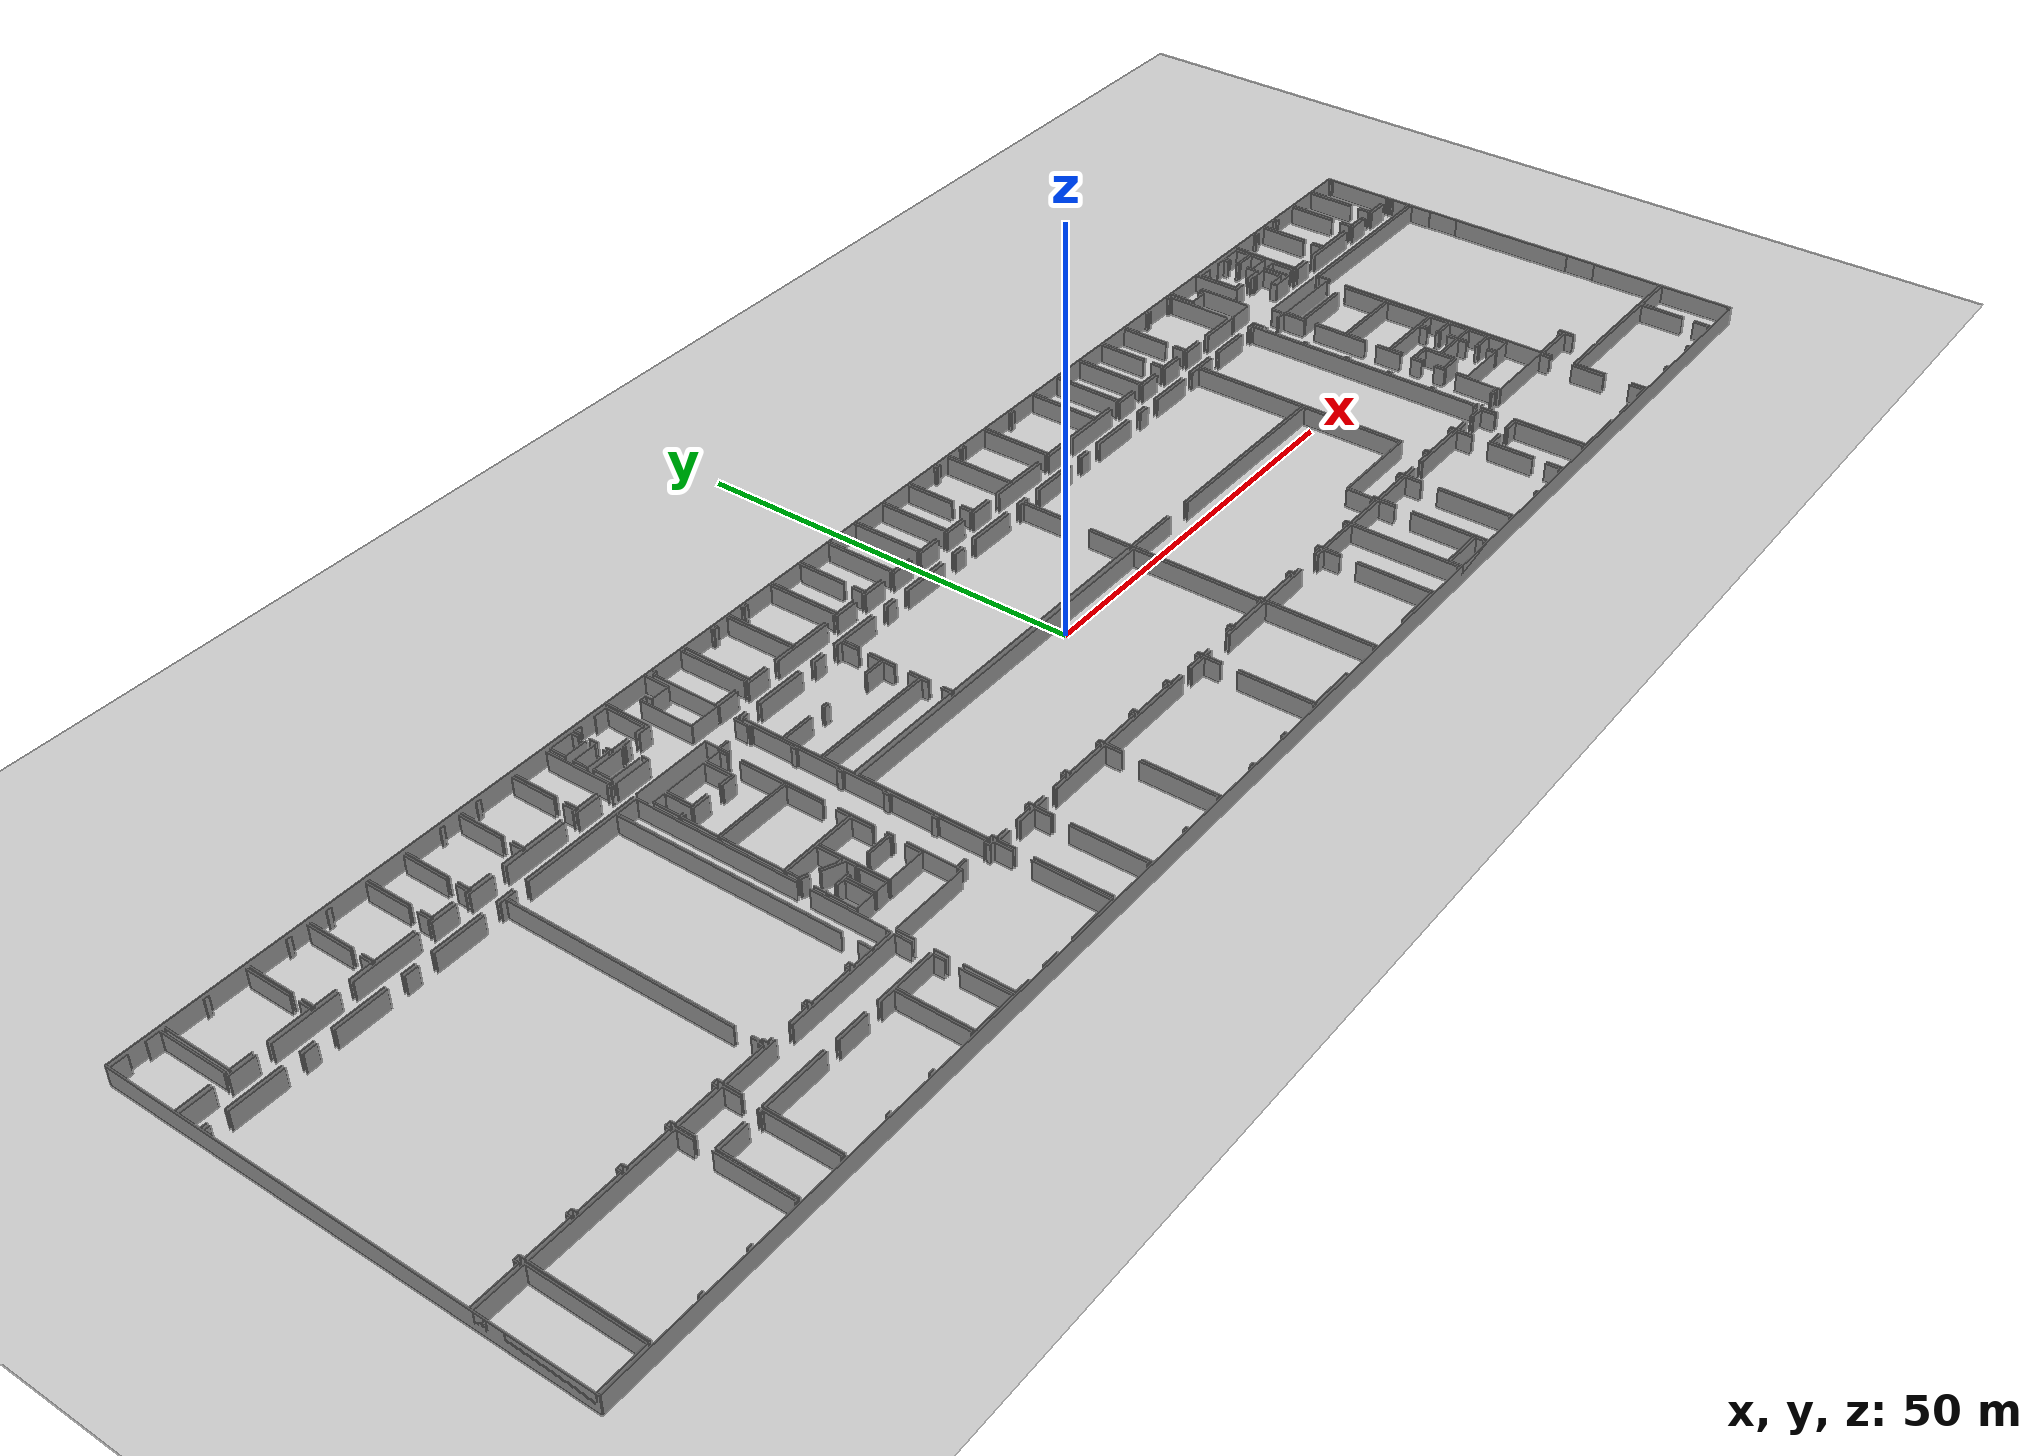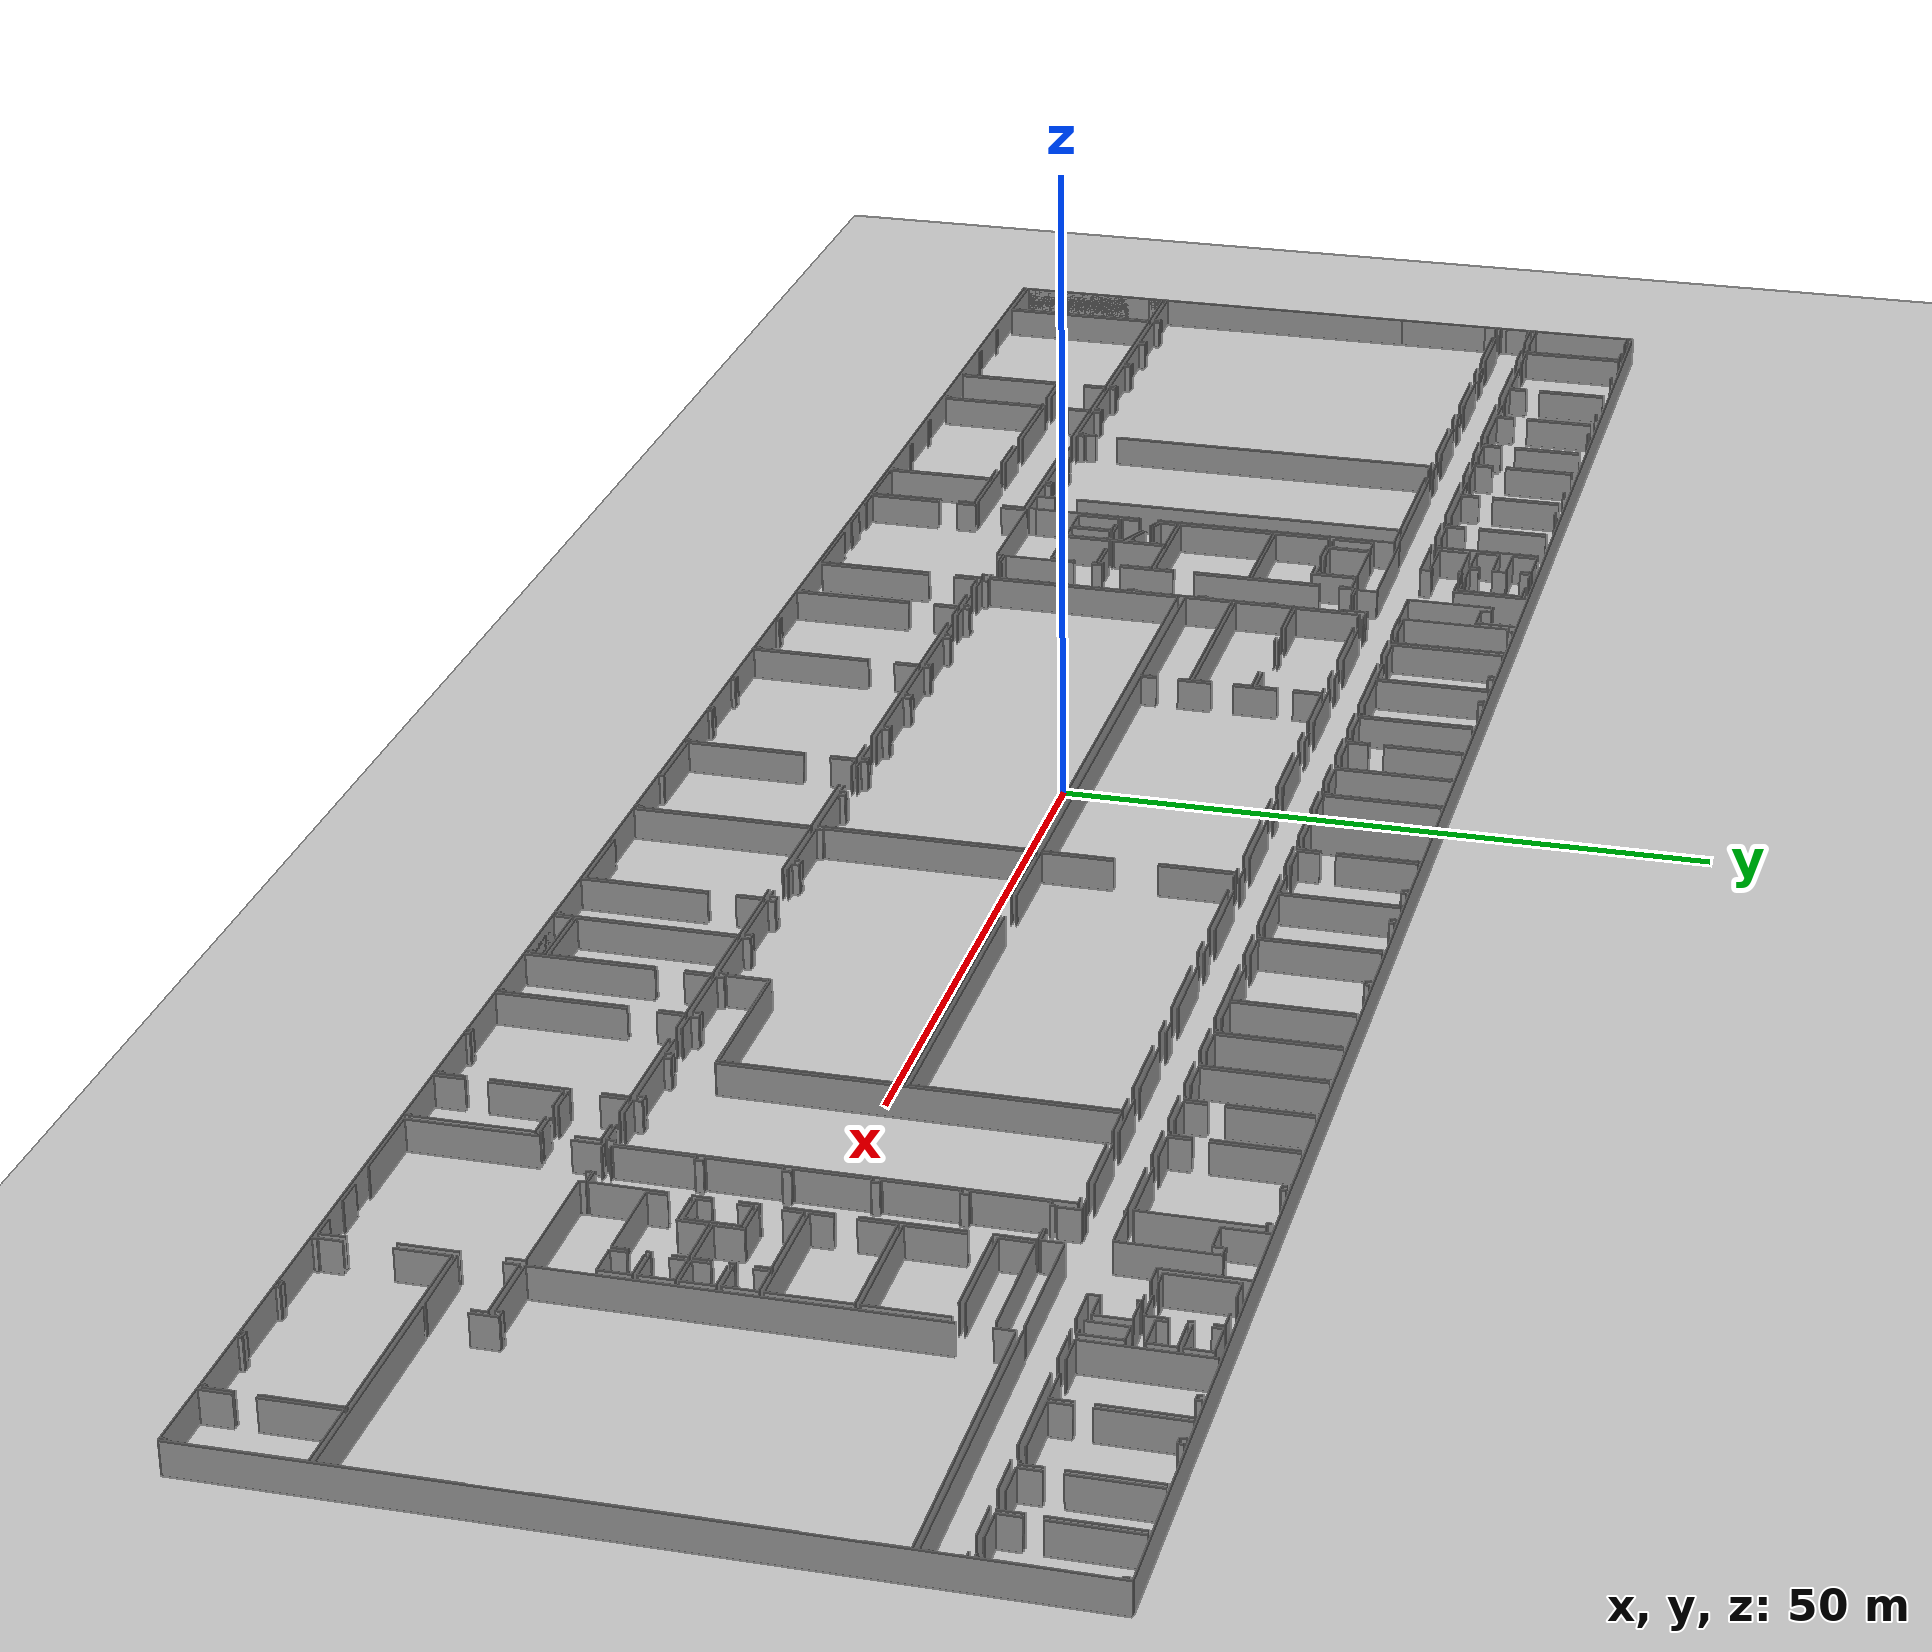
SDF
<sdf version="1.6">
  <world name="default">
    <light name="sun" type="directional">
      <cast_shadows>1</cast_shadows>
      <pose frame="">0 0 10 0 -0 0</pose>
      <diffuse>0.8 0.8 0.8 1</diffuse>
      <specular>0.1 0.1 0.1 1</specular>
      <attenuation>
        <range>1000</range>
        <constant>0.9</constant>
        <linear>0.01</linear>
        <quadratic>0.001</quadratic>
      </attenuation>
      <direction>-0.5 0.5 -1</direction>
    </light>
    <model name="ground_plane">
      <static>1</static>
      <link name="link">
        <collision name="collision">
          <geometry>
            <plane>
              <normal>0 0 1</normal>
              <size>100 100</size>
            </plane>
          </geometry>
          <surface>
            <friction>
              <ode>
                <mu>100</mu>
                <mu2>50</mu2>
              </ode>
              <torsional>
                <ode />
              </torsional>
            </friction>
            <contact>
              <ode />
            </contact>
            <bounce />
          </surface>
          <max_contacts>10</max_contacts>
        </collision>
        <visual name="visual">
          <cast_shadows>0</cast_shadows>
          <geometry>
            <plane>
              <normal>0 0 1</normal>
              <size>100 100</size>
            </plane>
          </geometry>
          <material>
            <script>
              <uri>file://media/materials/scripts/gazebo.material</uri>
              <name>Gazebo/Grey</name>
            </script>
          </material>
        </visual>
        <self_collide>0</self_collide>
        <kinematic>0</kinematic>
        <gravity>1</gravity>
      </link>
    </model>
    <gravity>0 0 -9.8</gravity>
    <magnetic_field>6e-06 2.3e-05 -4.2e-05</magnetic_field>
    <atmosphere type="adiabatic" />
    <physics default="0" name="default_physics" type="ode">
      <max_step_size>0.001</max_step_size>
      <real_time_factor>1</real_time_factor>
      <real_time_update_rate>1000</real_time_update_rate>
    </physics>
    <scene>
      <ambient>0.4 0.4 0.4 1</ambient>
      <background>0.7 0.7 0.7 1</background>
      <shadows>1</shadows>
    </scene>
    <spherical_coordinates>
      <surface_model>EARTH_WGS84</surface_model>
      <latitude_deg>0</latitude_deg>
      <longitude_deg>0</longitude_deg>
      <elevation>0</elevation>
      <heading_deg>0</heading_deg>
    </spherical_coordinates>
  <model name="50010535_PLAN2">
		<static>1</static>
		<link name="Wall_0">
			<collision name="Wall_0_Collision">
				<geometry>
					<box>
						<size>14.9290674257 0.1 2.5</size>
					</box>
				</geometry>
				<pose frame="">7.46453371283 0 1.25 0 0 0</pose>
			</collision>
			<visual name="Wall_0_Visual">
				<pose frame="">7.46453371283 0 1.25 0 0 0</pose>
				<geometry>
					<box>
						<size>14.9290674257 0.1 2.5</size>
					</box>
				</geometry>
				<material>
					<script>
						<uri>file://media/materials/scripts/gazebo.material</uri>
						<name>Gazebo/Grey</name>
					</script>
					<ambient>1 1 1 1</ambient>
				</material>
			</visual>
			<pose frame="">53.7913762762 -12.5641569729 0 0 0 3.14159265359</pose>
		</link>
		<link name="Wall_1">
			<collision name="Wall_1_Collision">
				<geometry>
					<box>
						<size>2.14023875021 0.1 2.5</size>
					</box>
				</geometry>
				<pose frame="">1.07011937511 0 1.25 0 0 0</pose>
			</collision>
			<visual name="Wall_1_Visual">
				<pose frame="">1.07011937511 0 1.25 0 0 0</pose>
				<geometry>
					<box>
						<size>2.14023875021 0.1 2.5</size>
					</box>
				</geometry>
				<material>
					<script>
						<uri>file://media/materials/scripts/gazebo.material</uri>
						<name>Gazebo/Grey</name>
					</script>
					<ambient>1 1 1 1</ambient>
				</material>
			</visual>
			<pose frame="">37.1960127825 -12.5641569729 0 0 0 3.14159265359</pose>
		</link>
		<link name="Wall_2">
			<collision name="Wall_2_Collision">
				<geometry>
					<box>
						<size>6.37853154006 0.1 2.5</size>
					</box>
				</geometry>
				<pose frame="">3.18926577003 0 1.25 0 0 0</pose>
			</collision>
			<visual name="Wall_2_Visual">
				<pose frame="">3.18926577003 0 1.25 0 0 0</pose>
				<geometry>
					<box>
						<size>6.37853154006 0.1 2.5</size>
					</box>
				</geometry>
				<material>
					<script>
						<uri>file://media/materials/scripts/gazebo.material</uri>
						<name>Gazebo/Grey</name>
					</script>
					<ambient>1 1 1 1</ambient>
				</material>
			</visual>
			<pose frame="">33.1376403245 -12.5641569729 0 0 0 3.14159265359</pose>
		</link>
		<link name="Wall_3">
			<collision name="Wall_3_Collision">
				<geometry>
					<box>
						<size>1.67087031378 0.1 2.5</size>
					</box>
				</geometry>
				<pose frame="">0.83543515689 0 1.25 0 0 0</pose>
			</collision>
			<visual name="Wall_3_Visual">
				<pose frame="">0.83543515689 0 1.25 0 0 0</pose>
				<geometry>
					<box>
						<size>1.67087031378 0.1 2.5</size>
					</box>
				</geometry>
				<material>
					<script>
						<uri>file://media/materials/scripts/gazebo.material</uri>
						<name>Gazebo/Grey</name>
					</script>
					<ambient>1 1 1 1</ambient>
				</material>
			</visual>
			<pose frame="">24.7685495194 -12.5641569729 0 0 0 3.14159265359</pose>
		</link>
		<link name="Wall_4">
			<collision name="Wall_4_Collision">
				<geometry>
					<box>
						<size>6.34956131713 0.1 2.5</size>
					</box>
				</geometry>
				<pose frame="">3.17478065856 0 1.25 0 0 0</pose>
			</collision>
			<visual name="Wall_4_Visual">
				<pose frame="">3.17478065856 0 1.25 0 0 0</pose>
				<geometry>
					<box>
						<size>6.34956131713 0.1 2.5</size>
					</box>
				</geometry>
				<material>
					<script>
						<uri>file://media/materials/scripts/gazebo.material</uri>
						<name>Gazebo/Grey</name>
					</script>
					<ambient>1 1 1 1</ambient>
				</material>
			</visual>
			<pose frame="">21.0926348291 -12.5641569729 0 0 0 3.14159265359</pose>
		</link>
		<link name="Wall_5">
			<collision name="Wall_5_Collision">
				<geometry>
					<box>
						<size>1.65638520232 0.1 2.5</size>
					</box>
				</geometry>
				<pose frame="">0.828192601158 0 1.25 0 0 0</pose>
			</collision>
			<visual name="Wall_5_Visual">
				<pose frame="">0.828192601158 0 1.25 0 0 0</pose>
				<geometry>
					<box>
						<size>1.65638520232 0.1 2.5</size>
					</box>
				</geometry>
				<material>
					<script>
						<uri>file://media/materials/scripts/gazebo.material</uri>
						<name>Gazebo/Grey</name>
					</script>
					<ambient>1 1 1 1</ambient>
				</material>
			</visual>
			<pose frame="">12.7235440239 -12.5641569729 0 0 0 3.14159265359</pose>
		</link>
		<link name="Wall_6">
			<collision name="Wall_6_Collision">
				<geometry>
					<box>
						<size>6.36404642859 0.1 2.5</size>
					</box>
				</geometry>
				<pose frame="">3.1820232143 0 1.25 0 0 0</pose>
			</collision>
			<visual name="Wall_6_Visual">
				<pose frame="">3.1820232143 0 1.25 0 0 0</pose>
				<geometry>
					<box>
						<size>6.36404642859 0.1 2.5</size>
					</box>
				</geometry>
				<material>
					<script>
						<uri>file://media/materials/scripts/gazebo.material</uri>
						<name>Gazebo/Grey</name>
					</script>
					<ambient>1 1 1 1</ambient>
				</material>
			</visual>
			<pose frame="">9.09108466802 -12.5641569729 0 0 0 3.14159265359</pose>
		</link>
		<link name="Wall_7">
			<collision name="Wall_7_Collision">
				<geometry>
					<box>
						<size>0.75556374402 0.1 2.5</size>
					</box>
				</geometry>
				<pose frame="">0.37778187201 0 1.25 0 0 0</pose>
			</collision>
			<visual name="Wall_7_Visual">
				<pose frame="">0.37778187201 0 1.25 0 0 0</pose>
				<geometry>
					<box>
						<size>0.75556374402 0.1 2.5</size>
					</box>
				</geometry>
				<material>
					<script>
						<uri>file://media/materials/scripts/gazebo.material</uri>
						<name>Gazebo/Grey</name>
					</script>
					<ambient>1 1 1 1</ambient>
				</material>
			</visual>
			<pose frame="">0.765652497093 -12.5641569729 0 0 0 3.14159265359</pose>
		</link>
		<link name="Wall_8">
			<collision name="Wall_8_Collision">
				<geometry>
					<box>
						<size>0.503929404141 0.1 2.5</size>
					</box>
				</geometry>
				<pose frame="">0.25196470207 0 1.25 0 0 0</pose>
			</collision>
			<visual name="Wall_8_Visual">
				<pose frame="">0.25196470207 0 1.25 0 0 0</pose>
				<geometry>
					<box>
						<size>0.503929404141 0.1 2.5</size>
					</box>
				</geometry>
				<material>
					<script>
						<uri>file://media/materials/scripts/gazebo.material</uri>
						<name>Gazebo/Grey</name>
					</script>
					<ambient>1 1 1 1</ambient>
				</material>
			</visual>
			<pose frame="">0.0100887530733 -12.5641569729 0 0 0 1.57079632679</pose>
		</link>
		<link name="Wall_9">
			<collision name="Wall_9_Collision">
				<geometry>
					<box>
						<size>0.363144285687 0.1 2.5</size>
					</box>
				</geometry>
				<pose frame="">0.181572142844 0 1.25 0 0 0</pose>
			</collision>
			<visual name="Wall_9_Visual">
				<pose frame="">0.181572142844 0 1.25 0 0 0</pose>
				<geometry>
					<box>
						<size>0.363144285687 0.1 2.5</size>
					</box>
				</geometry>
				<material>
					<script>
						<uri>file://media/materials/scripts/gazebo.material</uri>
						<name>Gazebo/Grey</name>
					</script>
					<ambient>1 1 1 1</ambient>
				</material>
			</visual>
			<pose frame="">0.0100887530733 -10.1278628743 0 0 0 1.57079632679</pose>
		</link>
		<link name="Wall_10">
			<collision name="Wall_10_Collision">
				<geometry>
					<box>
						<size>3.84348455874 0.1 2.5</size>
					</box>
				</geometry>
				<pose frame="">1.92174227937 0 1.25 0 0 0</pose>
			</collision>
			<visual name="Wall_10_Visual">
				<pose frame="">1.92174227937 0 1.25 0 0 0</pose>
				<geometry>
					<box>
						<size>3.84348455874 0.1 2.5</size>
					</box>
				</geometry>
				<material>
					<script>
						<uri>file://media/materials/scripts/gazebo.material</uri>
						<name>Gazebo/Grey</name>
					</script>
					<ambient>1 1 1 1</ambient>
				</material>
			</visual>
			<pose frame="">0.0100887530733 -9.76471858859 0 0 0 0.0</pose>
		</link>
		<link name="Wall_11">
			<collision name="Wall_11_Collision">
				<geometry>
					<box>
						<size>3.16741104045 0.1 2.5</size>
					</box>
				</geometry>
				<pose frame="">1.58370552023 0 1.25 0 0 0</pose>
			</collision>
			<visual name="Wall_11_Visual">
				<pose frame="">1.58370552023 0 1.25 0 0 0</pose>
				<geometry>
					<box>
						<size>3.16741104045 0.1 2.5</size>
					</box>
				</geometry>
				<material>
					<script>
						<uri>file://media/materials/scripts/gazebo.material</uri>
						<name>Gazebo/Grey</name>
					</script>
					<ambient>1 1 1 1</ambient>
				</material>
			</visual>
			<pose frame="">5.44414020063 -9.76471858859 0 0 0 0.0</pose>
		</link>
		<link name="Wall_12">
			<collision name="Wall_12_Collision">
				<geometry>
					<box>
						<size>7.91573222874 0.1 2.5</size>
					</box>
				</geometry>
				<pose frame="">3.95786611437 0 1.25 0 0 0</pose>
			</collision>
			<visual name="Wall_12_Visual">
				<pose frame="">3.95786611437 0 1.25 0 0 0</pose>
				<geometry>
					<box>
						<size>7.91573222874 0.1 2.5</size>
					</box>
				</geometry>
				<material>
					<script>
						<uri>file://media/materials/scripts/gazebo.material</uri>
						<name>Gazebo/Grey</name>
					</script>
					<ambient>1 1 1 1</ambient>
				</material>
			</visual>
			<pose frame="">10.2885205492 -9.76471858859 0 0 0 0.0</pose>
		</link>
		<link name="Wall_13">
			<collision name="Wall_13_Collision">
				<geometry>
					<box>
						<size>8.03237549475 0.1 2.5</size>
					</box>
				</geometry>
				<pose frame="">4.01618774737 0 1.25 0 0 0</pose>
			</collision>
			<visual name="Wall_13_Visual">
				<pose frame="">4.01618774737 0 1.25 0 0 0</pose>
				<geometry>
					<box>
						<size>8.03237549475 0.1 2.5</size>
					</box>
				</geometry>
				<material>
					<script>
						<uri>file://media/materials/scripts/gazebo.material</uri>
						<name>Gazebo/Grey</name>
					</script>
					<ambient>1 1 1 1</ambient>
				</material>
			</visual>
			<pose frame="">19.8181991449 -9.76471858859 0 0 0 0.0</pose>
		</link>
		<link name="Wall_14">
			<collision name="Wall_14_Collision">
				<geometry>
					<box>
						<size>3.15724604995 0.1 2.5</size>
					</box>
				</geometry>
				<pose frame="">1.57862302497 0 1.25 0 0 0</pose>
			</collision>
			<visual name="Wall_14_Visual">
				<pose frame="">1.57862302497 0 1.25 0 0 0</pose>
				<geometry>
					<box>
						<size>3.15724604995 0.1 2.5</size>
					</box>
				</geometry>
				<material>
					<script>
						<uri>file://media/materials/scripts/gazebo.material</uri>
						<name>Gazebo/Grey</name>
					</script>
					<ambient>1 1 1 1</ambient>
				</material>
			</visual>
			<pose frame="">29.4645210066 -9.76471858859 0 0 0 0.0</pose>
		</link>
		<link name="Wall_15">
			<collision name="Wall_15_Collision">
				<geometry>
					<box>
						<size>3.17122291189 0.1 2.5</size>
					</box>
				</geometry>
				<pose frame="">1.58561145594 0 1.25 0 0 0</pose>
			</collision>
			<visual name="Wall_15_Visual">
				<pose frame="">1.58561145594 0 1.25 0 0 0</pose>
				<geometry>
					<box>
						<size>3.17122291189 0.1 2.5</size>
					</box>
				</geometry>
				<material>
					<script>
						<uri>file://media/materials/scripts/gazebo.material</uri>
						<name>Gazebo/Grey</name>
					</script>
					<ambient>1 1 1 1</ambient>
				</material>
			</visual>
			<pose frame="">34.2773898846 -9.76471858859 0 0 0 0.0</pose>
		</link>
		<link name="Wall_16">
			<collision name="Wall_16_Collision">
				<geometry>
					<box>
						<size>7.94648132501 0.1 2.5</size>
					</box>
				</geometry>
				<pose frame="">3.9732406625 0 1.25 0 0 0</pose>
			</collision>
			<visual name="Wall_16_Visual">
				<pose frame="">3.9732406625 0 1.25 0 0 0</pose>
				<geometry>
					<box>
						<size>7.94648132501 0.1 2.5</size>
					</box>
				</geometry>
				<material>
					<script>
						<uri>file://media/materials/scripts/gazebo.material</uri>
						<name>Gazebo/Grey</name>
					</script>
					<ambient>1 1 1 1</ambient>
				</material>
			</visual>
			<pose frame="">39.0742489025 -9.76471858859 0 0 0 0.0</pose>
		</link>
		<link name="Wall_17">
			<collision name="Wall_17_Collision">
				<geometry>
					<box>
						<size>3.15140118041 0.1 2.5</size>
					</box>
				</geometry>
				<pose frame="">1.5757005902 0 1.25 0 0 0</pose>
			</collision>
			<visual name="Wall_17_Visual">
				<pose frame="">1.5757005902 0 1.25 0 0 0</pose>
				<geometry>
					<box>
						<size>3.15140118041 0.1 2.5</size>
					</box>
				</geometry>
				<material>
					<script>
						<uri>file://media/materials/scripts/gazebo.material</uri>
						<name>Gazebo/Grey</name>
					</script>
					<ambient>1 1 1 1</ambient>
				</material>
			</visual>
			<pose frame="">48.6992242842 -9.76471858859 0 0 0 0.0</pose>
		</link>
		<link name="Wall_18">
			<collision name="Wall_18_Collision">
				<geometry>
					<box>
						<size>0.35444510742 0.1 2.5</size>
					</box>
				</geometry>
				<pose frame="">0.17722255371 0 1.25 0 0 0</pose>
			</collision>
			<visual name="Wall_18_Visual">
				<pose frame="">0.17722255371 0 1.25 0 0 0</pose>
				<geometry>
					<box>
						<size>0.35444510742 0.1 2.5</size>
					</box>
				</geometry>
				<material>
					<script>
						<uri>file://media/materials/scripts/gazebo.material</uri>
						<name>Gazebo/Grey</name>
					</script>
					<ambient>1 1 1 1</ambient>
				</material>
			</visual>
			<pose frame="">53.4389052305 -9.76471858859 0 0 0 -0.105589964466</pose>
		</link>
		<link name="Wall_19">
			<collision name="Wall_19_Collision">
				<geometry>
					<box>
						<size>0.167214093759 0.1 2.5</size>
					</box>
				</geometry>
				<pose frame="">0.0836070468797 0 1.25 0 0 0</pose>
			</collision>
			<visual name="Wall_19_Visual">
				<pose frame="">0.0836070468797 0 1.25 0 0 0</pose>
				<geometry>
					<box>
						<size>0.167214093759 0.1 2.5</size>
					</box>
				</geometry>
				<material>
					<script>
						<uri>file://media/materials/scripts/gazebo.material</uri>
						<name>Gazebo/Grey</name>
					</script>
					<ambient>1 1 1 1</ambient>
				</material>
			</visual>
			<pose frame="">5.61567441535 -9.2203833472 0 0 0 3.14159265359</pose>
		</link>
		<link name="Wall_20">
			<collision name="Wall_20_Collision">
				<geometry>
					<box>
						<size>3.87888413817 0.1 2.5</size>
					</box>
				</geometry>
				<pose frame="">1.93944206908 0 1.25 0 0 0</pose>
			</collision>
			<visual name="Wall_20_Visual">
				<pose frame="">1.93944206908 0 1.25 0 0 0</pose>
				<geometry>
					<box>
						<size>3.87888413817 0.1 2.5</size>
					</box>
				</geometry>
				<material>
					<script>
						<uri>file://media/materials/scripts/gazebo.material</uri>
						<name>Gazebo/Grey</name>
					</script>
					<ambient>1 1 1 1</ambient>
				</material>
			</visual>
			<pose frame="">3.90414413957 -9.2203833472 0 0 0 3.14159265359</pose>
		</link>
		<link name="Wall_21">
			<collision name="Wall_21_Collision">
				<geometry>
					<box>
						<size>8.711168148 0.1 2.5</size>
					</box>
				</geometry>
				<pose frame="">4.355584074 0 1.25 0 0 0</pose>
			</collision>
			<visual name="Wall_21_Visual">
				<pose frame="">4.355584074 0 1.25 0 0 0</pose>
				<geometry>
					<box>
						<size>8.711168148 0.1 2.5</size>
					</box>
				</geometry>
				<material>
					<script>
						<uri>file://media/materials/scripts/gazebo.material</uri>
						<name>Gazebo/Grey</name>
					</script>
					<ambient>1 1 1 1</ambient>
				</material>
			</visual>
			<pose frame="">0.0252600013977 -9.2203833472 0 0 0 1.57079632679</pose>
		</link>
		<link name="Wall_22">
			<collision name="Wall_22_Collision">
				<geometry>
					<box>
						<size>1.95846330756 0.1 2.5</size>
					</box>
				</geometry>
				<pose frame="">0.97923165378 0 1.25 0 0 0</pose>
			</collision>
			<visual name="Wall_22_Visual">
				<pose frame="">0.97923165378 0 1.25 0 0 0</pose>
				<geometry>
					<box>
						<size>1.95846330756 0.1 2.5</size>
					</box>
				</geometry>
				<material>
					<script>
						<uri>file://media/materials/scripts/gazebo.material</uri>
						<name>Gazebo/Grey</name>
					</script>
					<ambient>1 1 1 1</ambient>
				</material>
			</visual>
			<pose frame="">0.0252600013977 -0.509215199202 0 0 0 0.0</pose>
		</link>
		<link name="Wall_23">
			<collision name="Wall_23_Collision">
				<geometry>
					<box>
						<size>1.62411135747 0.1 2.5</size>
					</box>
				</geometry>
				<pose frame="">0.812055678735 0 1.25 0 0 0</pose>
			</collision>
			<visual name="Wall_23_Visual">
				<pose frame="">0.812055678735 0 1.25 0 0 0</pose>
				<geometry>
					<box>
						<size>1.62411135747 0.1 2.5</size>
					</box>
				</geometry>
				<material>
					<script>
						<uri>file://media/materials/scripts/gazebo.material</uri>
						<name>Gazebo/Grey</name>
					</script>
					<ambient>1 1 1 1</ambient>
				</material>
			</visual>
			<pose frame="">3.94150047966 -0.509215199202 0 0 0 0.0</pose>
		</link>
		<link name="Wall_24">
			<collision name="Wall_24_Collision">
				<geometry>
					<box>
						<size>8.71131200018 0.1 2.5</size>
					</box>
				</geometry>
				<pose frame="">4.35565600009 0 1.25 0 0 0</pose>
			</collision>
			<visual name="Wall_24_Visual">
				<pose frame="">4.35565600009 0 1.25 0 0 0</pose>
				<geometry>
					<box>
						<size>8.71131200018 0.1 2.5</size>
					</box>
				</geometry>
				<material>
					<script>
						<uri>file://media/materials/scripts/gazebo.material</uri>
						<name>Gazebo/Grey</name>
					</script>
					<ambient>1 1 1 1</ambient>
				</material>
			</visual>
			<pose frame="">5.56561183713 -0.509215199202 0 0 0 -1.56504944805</pose>
		</link>
		<link name="Wall_25">
			<collision name="Wall_25_Collision">
				<geometry>
					<box>
						<size>5.07969987866 0.1 2.5</size>
					</box>
				</geometry>
				<pose frame="">2.53984993933 0 1.25 0 0 0</pose>
			</collision>
			<visual name="Wall_25_Visual">
				<pose frame="">2.53984993933 0 1.25 0 0 0</pose>
				<geometry>
					<box>
						<size>5.07969987866 0.1 2.5</size>
					</box>
				</geometry>
				<material>
					<script>
						<uri>file://media/materials/scripts/gazebo.material</uri>
						<name>Gazebo/Grey</name>
					</script>
					<ambient>1 1 1 1</ambient>
				</material>
			</visual>
			<pose frame="">15.3237485944 -9.20386523764 0 0 0 3.14159265359</pose>
		</link>
		<link name="Wall_26">
			<collision name="Wall_26_Collision">
				<geometry>
					<box>
						<size>2.56030698271 0.1 2.5</size>
					</box>
				</geometry>
				<pose frame="">1.28015349136 0 1.25 0 0 0</pose>
			</collision>
			<visual name="Wall_26_Visual">
				<pose frame="">1.28015349136 0 1.25 0 0 0</pose>
				<geometry>
					<box>
						<size>2.56030698271 0.1 2.5</size>
					</box>
				</geometry>
				<material>
					<script>
						<uri>file://media/materials/scripts/gazebo.material</uri>
						<name>Gazebo/Grey</name>
					</script>
					<ambient>1 1 1 1</ambient>
				</material>
			</visual>
			<pose frame="">8.64179208783 -9.20386523764 0 0 0 3.14159265359</pose>
		</link>
		<link name="Wall_27">
			<collision name="Wall_27_Collision">
				<geometry>
					<box>
						<size>8.68202003774 0.1 2.5</size>
					</box>
				</geometry>
				<pose frame="">4.34101001887 0 1.25 0 0 0</pose>
			</collision>
			<visual name="Wall_27_Visual">
				<pose frame="">4.34101001887 0 1.25 0 0 0</pose>
				<geometry>
					<box>
						<size>8.68202003774 0.1 2.5</size>
					</box>
				</geometry>
				<material>
					<script>
						<uri>file://media/materials/scripts/gazebo.material</uri>
						<name>Gazebo/Grey</name>
					</script>
					<ambient>1 1 1 1</ambient>
				</material>
			</visual>
			<pose frame="">6.08148510511 -9.20386523764 0 0 0 1.57079632679</pose>
		</link>
		<link name="Wall_28">
			<collision name="Wall_28_Collision">
				<geometry>
					<box>
						<size>0.573051339555 0.1 2.5</size>
					</box>
				</geometry>
				<pose frame="">0.286525669778 0 1.25 0 0 0</pose>
			</collision>
			<visual name="Wall_28_Visual">
				<pose frame="">0.286525669778 0 1.25 0 0 0</pose>
				<geometry>
					<box>
						<size>0.573051339555 0.1 2.5</size>
					</box>
				</geometry>
				<material>
					<script>
						<uri>file://media/materials/scripts/gazebo.material</uri>
						<name>Gazebo/Grey</name>
					</script>
					<ambient>1 1 1 1</ambient>
				</material>
			</visual>
			<pose frame="">10.4188865524 -0.521845199901 0 0 0 0.0</pose>
		</link>
		<link name="Wall_29">
			<collision name="Wall_29_Collision">
				<geometry>
					<box>
						<size>5.91294956259 0.1 2.5</size>
					</box>
				</geometry>
				<pose frame="">2.95647478129 0 1.25 0 0 0</pose>
			</collision>
			<visual name="Wall_29_Visual">
				<pose frame="">2.95647478129 0 1.25 0 0 0</pose>
				<geometry>
					<box>
						<size>5.91294956259 0.1 2.5</size>
					</box>
				</geometry>
				<material>
					<script>
						<uri>file://media/materials/scripts/gazebo.material</uri>
						<name>Gazebo/Grey</name>
					</script>
					<ambient>1 1 1 1</ambient>
				</material>
			</visual>
			<pose frame="">15.3196825982 -0.521845199901 0 0 0 -1.57079632679</pose>
		</link>
		<link name="Wall_30">
			<collision name="Wall_30_Collision">
				<geometry>
					<box>
						<size>1.5682091808 0.1 2.5</size>
					</box>
				</geometry>
				<pose frame="">0.784104590401 0 1.25 0 0 0</pose>
			</collision>
			<visual name="Wall_30_Visual">
				<pose frame="">0.784104590401 0 1.25 0 0 0</pose>
				<geometry>
					<box>
						<size>1.5682091808 0.1 2.5</size>
					</box>
				</geometry>
				<material>
					<script>
						<uri>file://media/materials/scripts/gazebo.material</uri>
						<name>Gazebo/Grey</name>
					</script>
					<ambient>1 1 1 1</ambient>
				</material>
			</visual>
			<pose frame="">15.3196825982 -7.63566132793 0 0 0 -1.56820355996</pose>
		</link>
		<link name="Wall_31">
			<collision name="Wall_31_Collision">
				<geometry>
					<box>
						<size>2.75115467939 0.1 2.5</size>
					</box>
				</geometry>
				<pose frame="">1.37557733969 0 1.25 0 0 0</pose>
			</collision>
			<visual name="Wall_31_Visual">
				<pose frame="">1.37557733969 0 1.25 0 0 0</pose>
				<geometry>
					<box>
						<size>2.75115467939 0.1 2.5</size>
					</box>
				</geometry>
				<material>
					<script>
						<uri>file://media/materials/scripts/gazebo.material</uri>
						<name>Gazebo/Grey</name>
					</script>
					<ambient>1 1 1 1</ambient>
				</material>
			</visual>
			<pose frame="">22.5746904443 -9.22699059103 0 0 0 3.14159265359</pose>
		</link>
		<link name="Wall_32">
			<collision name="Wall_32_Collision">
				<geometry>
					<box>
						<size>2.6065576895 0.1 2.5</size>
					</box>
				</geometry>
				<pose frame="">1.30327884475 0 1.25 0 0 0</pose>
			</collision>
			<visual name="Wall_32_Visual">
				<pose frame="">1.30327884475 0 1.25 0 0 0</pose>
				<geometry>
					<box>
						<size>2.6065576895 0.1 2.5</size>
					</box>
				</geometry>
				<material>
					<script>
						<uri>file://media/materials/scripts/gazebo.material</uri>
						<name>Gazebo/Grey</name>
					</script>
					<ambient>1 1 1 1</ambient>
				</material>
			</visual>
			<pose frame="">18.2977706905 -9.22699059103 0 0 0 3.14159265359</pose>
		</link>
		<link name="Wall_33">
			<collision name="Wall_33_Collision">
				<geometry>
					<box>
						<size>1.5770982764 0.1 2.5</size>
					</box>
				</geometry>
				<pose frame="">0.788549138199 0 1.25 0 0 0</pose>
			</collision>
			<visual name="Wall_33_Visual">
				<pose frame="">0.788549138199 0 1.25 0 0 0</pose>
				<geometry>
					<box>
						<size>1.5770982764 0.1 2.5</size>
					</box>
				</geometry>
				<material>
					<script>
						<uri>file://media/materials/scripts/gazebo.material</uri>
						<name>Gazebo/Grey</name>
					</script>
					<ambient>1 1 1 1</ambient>
				</material>
			</visual>
			<pose frame="">15.691213001 -9.22699059103 0 0 0 1.57079632679</pose>
		</link>
		<link name="Wall_34">
			<collision name="Wall_34_Collision">
				<geometry>
					<box>
						<size>5.87503414801 0.1 2.5</size>
					</box>
				</geometry>
				<pose frame="">2.93751707401 0 1.25 0 0 0</pose>
			</collision>
			<visual name="Wall_34_Visual">
				<pose frame="">2.93751707401 0 1.25 0 0 0</pose>
				<geometry>
					<box>
						<size>5.87503414801 0.1 2.5</size>
					</box>
				</geometry>
				<material>
					<script>
						<uri>file://media/materials/scripts/gazebo.material</uri>
						<name>Gazebo/Grey</name>
					</script>
					<ambient>1 1 1 1</ambient>
				</material>
			</visual>
			<pose frame="">15.691213001 -6.43479476249 0 0 0 1.57079632679</pose>
		</link>
		<link name="Wall_35">
			<collision name="Wall_35_Collision">
				<geometry>
					<box>
						<size>0.593889570084 0.1 2.5</size>
					</box>
				</geometry>
				<pose frame="">0.296944785042 0 1.25 0 0 0</pose>
			</collision>
			<visual name="Wall_35_Visual">
				<pose frame="">0.296944785042 0 1.25 0 0 0</pose>
				<geometry>
					<box>
						<size>0.593889570084 0.1 2.5</size>
					</box>
				</geometry>
				<material>
					<script>
						<uri>file://media/materials/scripts/gazebo.material</uri>
						<name>Gazebo/Grey</name>
					</script>
					<ambient>1 1 1 1</ambient>
				</material>
			</visual>
			<pose frame="">19.9877003615 -0.559760614474 0 0 0 0.0</pose>
		</link>
		<link name="Wall_36">
			<collision name="Wall_36_Collision">
				<geometry>
					<box>
						<size>5.87927803155 0.1 2.5</size>
					</box>
				</geometry>
				<pose frame="">2.93963901577 0 1.25 0 0 0</pose>
			</collision>
			<visual name="Wall_36_Visual">
				<pose frame="">2.93963901577 0 1.25 0 0 0</pose>
				<geometry>
					<box>
						<size>5.87927803155 0.1 2.5</size>
					</box>
				</geometry>
				<material>
					<script>
						<uri>file://media/materials/scripts/gazebo.material</uri>
						<name>Gazebo/Grey</name>
					</script>
					<ambient>1 1 1 1</ambient>
				</material>
			</visual>
			<pose frame="">22.5652878281 -0.559760614474 0 0 0 -1.57079632679</pose>
		</link>
		<link name="Wall_37">
			<collision name="Wall_37_Collision">
				<geometry>
					<box>
						<size>1.59135704127 0.1 2.5</size>
					</box>
				</geometry>
				<pose frame="">0.795678520634 0 1.25 0 0 0</pose>
			</collision>
			<visual name="Wall_37_Visual">
				<pose frame="">0.795678520634 0 1.25 0 0 0</pose>
				<geometry>
					<box>
						<size>1.59135704127 0.1 2.5</size>
					</box>
				</geometry>
				<material>
					<script>
						<uri>file://media/materials/scripts/gazebo.material</uri>
						<name>Gazebo/Grey</name>
					</script>
					<ambient>1 1 1 1</ambient>
				</material>
			</visual>
			<pose frame="">22.5652878281 -7.63566132793 0 0 0 -1.56488774017</pose>
		</link>
		<link name="Wall_38">
			<collision name="Wall_38_Collision">
				<geometry>
					<box>
						<size>0.317401828428 0.1 2.5</size>
					</box>
				</geometry>
				<pose frame="">0.158700914214 0 1.25 0 0 0</pose>
			</collision>
			<visual name="Wall_38_Visual">
				<pose frame="">0.158700914214 0 1.25 0 0 0</pose>
				<geometry>
					<box>
						<size>0.317401828428 0.1 2.5</size>
					</box>
				</geometry>
				<material>
					<script>
						<uri>file://media/materials/scripts/gazebo.material</uri>
						<name>Gazebo/Grey</name>
					</script>
					<ambient>1 1 1 1</ambient>
				</material>
			</visual>
			<pose frame="">29.7936125741 -9.25392781586 0 0 0 3.14159265359</pose>
		</link>
		<link name="Wall_39">
			<collision name="Wall_39_Collision">
				<geometry>
					<box>
						<size>4.9470467526 0.1 2.5</size>
					</box>
				</geometry>
				<pose frame="">2.4735233763 0 1.25 0 0 0</pose>
			</collision>
			<visual name="Wall_39_Visual">
				<pose frame="">2.4735233763 0 1.25 0 0 0</pose>
				<geometry>
					<box>
						<size>4.9470467526 0.1 2.5</size>
					</box>
				</geometry>
				<material>
					<script>
						<uri>file://media/materials/scripts/gazebo.material</uri>
						<name>Gazebo/Grey</name>
					</script>
					<ambient>1 1 1 1</ambient>
				</material>
			</visual>
			<pose frame="">27.8231291653 -9.25392781586 0 0 0 3.14159265359</pose>
		</link>
		<link name="Wall_40">
			<collision name="Wall_40_Collision">
				<geometry>
					<box>
						<size>1.62080773556 0.1 2.5</size>
					</box>
				</geometry>
				<pose frame="">0.810403867779 0 1.25 0 0 0</pose>
			</collision>
			<visual name="Wall_40_Visual">
				<pose frame="">0.810403867779 0 1.25 0 0 0</pose>
				<geometry>
					<box>
						<size>1.62080773556 0.1 2.5</size>
					</box>
				</geometry>
				<material>
					<script>
						<uri>file://media/materials/scripts/gazebo.material</uri>
						<name>Gazebo/Grey</name>
					</script>
					<ambient>1 1 1 1</ambient>
				</material>
			</visual>
			<pose frame="">22.8760824127 -9.25392781586 0 0 0 1.57079632679</pose>
		</link>
		<link name="Wall_41">
			<collision name="Wall_41_Collision">
				<geometry>
					<box>
						<size>5.86410678323 0.1 2.5</size>
					</box>
				</geometry>
				<pose frame="">2.93205339161 0 1.25 0 0 0</pose>
			</collision>
			<visual name="Wall_41_Visual">
				<pose frame="">2.93205339161 0 1.25 0 0 0</pose>
				<geometry>
					<box>
						<size>5.86410678323 0.1 2.5</size>
					</box>
				</geometry>
				<material>
					<script>
						<uri>file://media/materials/scripts/gazebo.material</uri>
						<name>Gazebo/Grey</name>
					</script>
					<ambient>1 1 1 1</ambient>
				</material>
			</visual>
			<pose frame="">22.8760824127 -6.43731059764 0 0 0 1.57079632679</pose>
		</link>
		<link name="Wall_42">
			<collision name="Wall_42_Collision">
				<geometry>
					<box>
						<size>0.598209691048 0.1 2.5</size>
					</box>
				</geometry>
				<pose frame="">0.299104845524 0 1.25 0 0 0</pose>
			</collision>
			<visual name="Wall_42_Visual">
				<pose frame="">0.299104845524 0 1.25 0 0 0</pose>
				<geometry>
					<box>
						<size>0.598209691048 0.1 2.5</size>
					</box>
				</geometry>
				<material>
					<script>
						<uri>file://media/materials/scripts/gazebo.material</uri>
						<name>Gazebo/Grey</name>
					</script>
					<ambient>1 1 1 1</ambient>
				</material>
			</visual>
			<pose frame="">24.8046352357 -0.573203814413 0 0 0 0.0</pose>
		</link>
		<link name="Wall_43">
			<collision name="Wall_43_Collision">
				<geometry>
					<box>
						<size>5.84896094738 0.1 2.5</size>
					</box>
				</geometry>
				<pose frame="">2.92448047369 0 1.25 0 0 0</pose>
			</collision>
			<visual name="Wall_43_Visual">
				<pose frame="">2.92448047369 0 1.25 0 0 0</pose>
				<geometry>
					<box>
						<size>5.84896094738 0.1 2.5</size>
					</box>
				</geometry>
				<material>
					<script>
						<uri>file://media/materials/scripts/gazebo.material</uri>
						<name>Gazebo/Grey</name>
					</script>
					<ambient>1 1 1 1</ambient>
				</material>
			</visual>
			<pose frame="">29.7227117653 -0.573203814413 0 0 0 -1.57079632679</pose>
		</link>
		<link name="Wall_44">
			<collision name="Wall_44_Collision">
				<geometry>
					<box>
						<size>1.65574386442 0.1 2.5</size>
					</box>
				</geometry>
				<pose frame="">0.827871932209 0 1.25 0 0 0</pose>
			</collision>
			<visual name="Wall_44_Visual">
				<pose frame="">0.827871932209 0 1.25 0 0 0</pose>
				<geometry>
					<box>
						<size>1.65574386442 0.1 2.5</size>
					</box>
				</geometry>
				<material>
					<script>
						<uri>file://media/materials/scripts/gazebo.material</uri>
						<name>Gazebo/Grey</name>
					</script>
					<ambient>1 1 1 1</ambient>
				</material>
			</visual>
			<pose frame="">29.7227117653 -7.59970267403 0 0 0 -1.52796210827</pose>
		</link>
		<link name="Wall_45">
			<collision name="Wall_45_Collision">
				<geometry>
					<box>
						<size>0.328329193217 0.1 2.5</size>
					</box>
				</geometry>
				<pose frame="">0.164164596609 0 1.25 0 0 0</pose>
			</collision>
			<visual name="Wall_45_Visual">
				<pose frame="">0.164164596609 0 1.25 0 0 0</pose>
				<geometry>
					<box>
						<size>0.328329193217 0.1 2.5</size>
					</box>
				</geometry>
				<material>
					<script>
						<uri>file://media/materials/scripts/gazebo.material</uri>
						<name>Gazebo/Grey</name>
					</script>
					<ambient>1 1 1 1</ambient>
				</material>
			</visual>
			<pose frame="">34.5678544882 -9.23969682916 0 0 0 3.14159265359</pose>
		</link>
		<link name="Wall_46">
			<collision name="Wall_46_Collision">
				<geometry>
					<box>
						<size>2.57479209418 0.1 2.5</size>
					</box>
				</geometry>
				<pose frame="">1.28739604709 0 1.25 0 0 0</pose>
			</collision>
			<visual name="Wall_46_Visual">
				<pose frame="">1.28739604709 0 1.25 0 0 0</pose>
				<geometry>
					<box>
						<size>2.57479209418 0.1 2.5</size>
					</box>
				</geometry>
				<material>
					<script>
						<uri>file://media/materials/scripts/gazebo.material</uri>
						<name>Gazebo/Grey</name>
					</script>
					<ambient>1 1 1 1</ambient>
				</material>
			</visual>
			<pose frame="">32.6542950261 -9.23969682916 0 0 0 3.14159265359</pose>
		</link>
		<link name="Wall_47">
			<collision name="Wall_47_Collision">
				<geometry>
					<box>
						<size>1.58980451453 0.1 2.5</size>
					</box>
				</geometry>
				<pose frame="">0.794902257263 0 1.25 0 0 0</pose>
			</collision>
			<visual name="Wall_47_Visual">
				<pose frame="">0.794902257263 0 1.25 0 0 0</pose>
				<geometry>
					<box>
						<size>1.58980451453 0.1 2.5</size>
					</box>
				</geometry>
				<material>
					<script>
						<uri>file://media/materials/scripts/gazebo.material</uri>
						<name>Gazebo/Grey</name>
					</script>
					<ambient>1 1 1 1</ambient>
				</material>
			</visual>
			<pose frame="">30.079502932 -9.23969682916 0 0 0 1.57079632679</pose>
		</link>
		<link name="Wall_48">
			<collision name="Wall_48_Collision">
				<geometry>
					<box>
						<size>5.83689002116 0.1 2.5</size>
					</box>
				</geometry>
				<pose frame="">2.91844501058 0 1.25 0 0 0</pose>
			</collision>
			<visual name="Wall_48_Visual">
				<pose frame="">2.91844501058 0 1.25 0 0 0</pose>
				<geometry>
					<box>
						<size>5.83689002116 0.1 2.5</size>
					</box>
				</geometry>
				<material>
					<script>
						<uri>file://media/materials/scripts/gazebo.material</uri>
						<name>Gazebo/Grey</name>
					</script>
					<ambient>1 1 1 1</ambient>
				</material>
			</visual>
			<pose frame="">30.079502932 -6.39665063563 0 0 0 1.57079632679</pose>
		</link>
		<link name="Wall_49">
			<collision name="Wall_49_Collision">
				<geometry>
					<box>
						<size>5.86240414732 0.1 2.5</size>
					</box>
				</geometry>
				<pose frame="">2.93120207366 0 1.25 0 0 0</pose>
			</collision>
			<visual name="Wall_49_Visual">
				<pose frame="">2.93120207366 0 1.25 0 0 0</pose>
				<geometry>
					<box>
						<size>5.86240414732 0.1 2.5</size>
					</box>
				</geometry>
				<material>
					<script>
						<uri>file://media/materials/scripts/gazebo.material</uri>
						<name>Gazebo/Grey</name>
					</script>
					<ambient>1 1 1 1</ambient>
				</material>
			</visual>
			<pose frame="">34.5508281291 -0.559760614474 0 0 0 -1.57079632679</pose>
		</link>
		<link name="Wall_50">
			<collision name="Wall_50_Collision">
				<geometry>
					<box>
						<size>1.57337853326 0.1 2.5</size>
					</box>
				</geometry>
				<pose frame="">0.786689266632 0 1.25 0 0 0</pose>
			</collision>
			<visual name="Wall_50_Visual">
				<pose frame="">0.786689266632 0 1.25 0 0 0</pose>
				<geometry>
					<box>
						<size>1.57337853326 0.1 2.5</size>
					</box>
				</geometry>
				<material>
					<script>
						<uri>file://media/materials/scripts/gazebo.material</uri>
						<name>Gazebo/Grey</name>
					</script>
					<ambient>1 1 1 1</ambient>
				</material>
			</visual>
			<pose frame="">34.5508281291 -7.6664104242 0 0 0 -1.55997458806</pose>
		</link>
		<link name="Wall_51">
			<collision name="Wall_51_Collision">
				<geometry>
					<box>
						<size>2.72294683075 0.1 2.5</size>
					</box>
				</geometry>
				<pose frame="">1.36147341537 0 1.25 0 0 0</pose>
			</collision>
			<visual name="Wall_51_Visual">
				<pose frame="">1.36147341537 0 1.25 0 0 0</pose>
				<geometry>
					<box>
						<size>2.72294683075 0.1 2.5</size>
					</box>
				</geometry>
				<material>
					<script>
						<uri>file://media/materials/scripts/gazebo.material</uri>
						<name>Gazebo/Grey</name>
					</script>
					<ambient>1 1 1 1</ambient>
				</material>
			</visual>
			<pose frame="">41.7816941227 -9.21885859863 0 0 0 3.14159265359</pose>
		</link>
		<link name="Wall_52">
			<collision name="Wall_52_Collision">
				<geometry>
					<box>
						<size>2.60071281996 0.1 2.5</size>
					</box>
				</geometry>
				<pose frame="">1.30035640998 0 1.25 0 0 0</pose>
			</collision>
			<visual name="Wall_52_Visual">
				<pose frame="">1.30035640998 0 1.25 0 0 0</pose>
				<geometry>
					<box>
						<size>2.60071281996 0.1 2.5</size>
					</box>
				</geometry>
				<material>
					<script>
						<uri>file://media/materials/scripts/gazebo.material</uri>
						<name>Gazebo/Grey</name>
					</script>
					<ambient>1 1 1 1</ambient>
				</material>
			</visual>
			<pose frame="">37.4966423766 -9.21885859863 0 0 0 3.14159265359</pose>
		</link>
		<link name="Wall_53">
			<collision name="Wall_53_Collision">
				<geometry>
					<box>
						<size>1.59005863929 0.1 2.5</size>
					</box>
				</geometry>
				<pose frame="">0.795029319644 0 1.25 0 0 0</pose>
			</collision>
			<visual name="Wall_53_Visual">
				<pose frame="">0.795029319644 0 1.25 0 0 0</pose>
				<geometry>
					<box>
						<size>1.59005863929 0.1 2.5</size>
					</box>
				</geometry>
				<material>
					<script>
						<uri>file://media/materials/scripts/gazebo.material</uri>
						<name>Gazebo/Grey</name>
					</script>
					<ambient>1 1 1 1</ambient>
				</material>
			</visual>
			<pose frame="">34.8959295566 -9.21885859863 0 0 0 1.57079632679</pose>
		</link>
		<link name="Wall_54">
			<collision name="Wall_54_Collision">
				<geometry>
					<box>
						<size>5.87503414801 0.1 2.5</size>
					</box>
				</geometry>
				<pose frame="">2.93751707401 0 1.25 0 0 0</pose>
			</collision>
			<visual name="Wall_54_Visual">
				<pose frame="">2.93751707401 0 1.25 0 0 0</pose>
				<geometry>
					<box>
						<size>5.87503414801 0.1 2.5</size>
					</box>
				</geometry>
				<material>
					<script>
						<uri>file://media/materials/scripts/gazebo.material</uri>
						<name>Gazebo/Grey</name>
					</script>
					<ambient>1 1 1 1</ambient>
				</material>
			</visual>
			<pose frame="">34.8959295566 -6.46005476389 0 0 0 1.57079632679</pose>
		</link>
		<link name="Wall_55">
			<collision name="Wall_55_Collision">
				<geometry>
					<box>
						<size>0.538236247086 0.1 2.5</size>
					</box>
				</geometry>
				<pose frame="">0.269118123543 0 1.25 0 0 0</pose>
			</collision>
			<visual name="Wall_55_Visual">
				<pose frame="">0.269118123543 0 1.25 0 0 0</pose>
				<geometry>
					<box>
						<size>0.538236247086 0.1 2.5</size>
					</box>
				</geometry>
				<material>
					<script>
						<uri>file://media/materials/scripts/gazebo.material</uri>
						<name>Gazebo/Grey</name>
					</script>
					<ambient>1 1 1 1</ambient>
				</material>
			</visual>
			<pose frame="">39.2124927733 -0.585020615871 0 0 0 0.0</pose>
		</link>
		<link name="Wall_56">
			<collision name="Wall_56_Collision">
				<geometry>
					<box>
						<size>5.84977414662 0.1 2.5</size>
					</box>
				</geometry>
				<pose frame="">2.92488707331 0 1.25 0 0 0</pose>
			</collision>
			<visual name="Wall_56_Visual">
				<pose frame="">2.92488707331 0 1.25 0 0 0</pose>
				<geometry>
					<box>
						<size>5.84977414662 0.1 2.5</size>
					</box>
				</geometry>
				<material>
					<script>
						<uri>file://media/materials/scripts/gazebo.material</uri>
						<name>Gazebo/Grey</name>
					</script>
					<ambient>1 1 1 1</ambient>
				</material>
			</visual>
			<pose frame="">41.7504367769 -0.585020615871 0 0 0 -1.57079632679</pose>
		</link>
		<link name="Wall_57">
			<collision name="Wall_57_Collision">
				<geometry>
					<box>
						<size>1.59519327845 0.1 2.5</size>
					</box>
				</geometry>
				<pose frame="">0.797596639227 0 1.25 0 0 0</pose>
			</collision>
			<visual name="Wall_57_Visual">
				<pose frame="">0.797596639227 0 1.25 0 0 0</pose>
				<geometry>
					<box>
						<size>1.59519327845 0.1 2.5</size>
					</box>
				</geometry>
				<material>
					<script>
						<uri>file://media/materials/scripts/gazebo.material</uri>
						<name>Gazebo/Grey</name>
					</script>
					<ambient>1 1 1 1</ambient>
				</material>
			</visual>
			<pose frame="">41.7504367769 -7.62397158885 0 0 0 -1.55120036511</pose>
		</link>
		<link name="Wall_58">
			<collision name="Wall_58_Collision">
				<geometry>
					<box>
						<size>0.350692172322 0.1 2.5</size>
					</box>
				</geometry>
				<pose frame="">0.175346086161 0 1.25 0 0 0</pose>
			</collision>
			<visual name="Wall_58_Visual">
				<pose frame="">0.175346086161 0 1.25 0 0 0</pose>
				<geometry>
					<box>
						<size>0.350692172322 0.1 2.5</size>
					</box>
				</geometry>
				<material>
					<script>
						<uri>file://media/materials/scripts/gazebo.material</uri>
						<name>Gazebo/Grey</name>
					</script>
					<ambient>1 1 1 1</ambient>
				</material>
			</visual>
			<pose frame="">48.9757120258 -9.2203833472 0 0 0 3.14159265359</pose>
		</link>
		<link name="Wall_59">
			<collision name="Wall_59_Collision">
				<geometry>
					<box>
						<size>5.02938317567 0.1 2.5</size>
					</box>
				</geometry>
				<pose frame="">2.51469158784 0 1.25 0 0 0</pose>
			</collision>
			<visual name="Wall_59_Visual">
				<pose frame="">2.51469158784 0 1.25 0 0 0</pose>
				<geometry>
					<box>
						<size>5.02938317567 0.1 2.5</size>
					</box>
				</geometry>
				<material>
					<script>
						<uri>file://media/materials/scripts/gazebo.material</uri>
						<name>Gazebo/Grey</name>
					</script>
					<ambient>1 1 1 1</ambient>
				</material>
			</visual>
			<pose frame="">47.1043372744 -9.2203833472 0 0 0 3.14159265359</pose>
		</link>
		<link name="Wall_60">
			<collision name="Wall_60_Collision">
				<geometry>
					<box>
						<size>1.60403550123 0.1 2.5</size>
					</box>
				</geometry>
				<pose frame="">0.802017750615 0 1.25 0 0 0</pose>
			</collision>
			<visual name="Wall_60_Visual">
				<pose frame="">0.802017750615 0 1.25 0 0 0</pose>
				<geometry>
					<box>
						<size>1.60403550123 0.1 2.5</size>
					</box>
				</geometry>
				<material>
					<script>
						<uri>file://media/materials/scripts/gazebo.material</uri>
						<name>Gazebo/Grey</name>
					</script>
					<ambient>1 1 1 1</ambient>
				</material>
			</visual>
			<pose frame="">42.0749540987 -9.2203833472 0 0 0 1.57079632679</pose>
		</link>
		<link name="Wall_61">
			<collision name="Wall_61_Collision">
				<geometry>
					<box>
						<size>5.83775404535 0.1 2.5</size>
					</box>
				</geometry>
				<pose frame="">2.91887702267 0 1.25 0 0 0</pose>
			</collision>
			<visual name="Wall_61_Visual">
				<pose frame="">2.91887702267 0 1.25 0 0 0</pose>
				<geometry>
					<box>
						<size>5.83775404535 0.1 2.5</size>
					</box>
				</geometry>
				<material>
					<script>
						<uri>file://media/materials/scripts/gazebo.material</uri>
						<name>Gazebo/Grey</name>
					</script>
					<ambient>1 1 1 1</ambient>
				</material>
			</visual>
			<pose frame="">42.0749540987 -6.43006804191 0 0 0 1.57079632679</pose>
		</link>
		<link name="Wall_62">
			<collision name="Wall_62_Collision">
				<geometry>
					<box>
						<size>0.601767437724 0.1 2.5</size>
					</box>
				</geometry>
				<pose frame="">0.300883718862 0 1.25 0 0 0</pose>
			</collision>
			<visual name="Wall_62_Visual">
				<pose frame="">0.300883718862 0 1.25 0 0 0</pose>
				<geometry>
					<box>
						<size>0.601767437724 0.1 2.5</size>
					</box>
				</geometry>
				<material>
					<script>
						<uri>file://media/materials/scripts/gazebo.material</uri>
						<name>Gazebo/Grey</name>
					</script>
					<ambient>1 1 1 1</ambient>
				</material>
			</visual>
			<pose frame="">44.0185002827 -0.592313996557 0 0 0 0.0</pose>
		</link>
		<link name="Wall_63">
			<collision name="Wall_63_Collision">
				<geometry>
					<box>
						<size>5.84024446802 0.1 2.5</size>
					</box>
				</geometry>
				<pose frame="">2.92012223401 0 1.25 0 0 0</pose>
			</collision>
			<visual name="Wall_63_Visual">
				<pose frame="">2.92012223401 0 1.25 0 0 0</pose>
				<geometry>
					<box>
						<size>5.84024446802 0.1 2.5</size>
					</box>
				</geometry>
				<material>
					<script>
						<uri>file://media/materials/scripts/gazebo.material</uri>
						<name>Gazebo/Grey</name>
					</script>
					<ambient>1 1 1 1</ambient>
				</material>
			</visual>
			<pose frame="">48.9098937123 -0.592313996557 0 0 0 -1.57079632679</pose>
		</link>
		<link name="Wall_64">
			<collision name="Wall_64_Collision">
				<geometry>
					<box>
						<size>1.59294373125 0.1 2.5</size>
					</box>
				</geometry>
				<pose frame="">0.796471865623 0 1.25 0 0 0</pose>
			</collision>
			<visual name="Wall_64_Visual">
				<pose frame="">0.796471865623 0 1.25 0 0 0</pose>
				<geometry>
					<box>
						<size>1.59294373125 0.1 2.5</size>
					</box>
				</geometry>
				<material>
					<script>
						<uri>file://media/materials/scripts/gazebo.material</uri>
						<name>Gazebo/Grey</name>
					</script>
					<ambient>1 1 1 1</ambient>
				</material>
			</visual>
			<pose frame="">48.9098937123 -7.62879995934 0 0 0 -1.52946589279</pose>
		</link>
		<link name="Wall_65">
			<collision name="Wall_65_Collision">
				<geometry>
					<box>
						<size>0.392368633381 0.1 2.5</size>
					</box>
				</geometry>
				<pose frame="">0.19618431669 0 1.25 0 0 0</pose>
			</collision>
			<visual name="Wall_65_Visual">
				<pose frame="">0.19618431669 0 1.25 0 0 0</pose>
				<geometry>
					<box>
						<size>0.392368633381 0.1 2.5</size>
					</box>
				</geometry>
				<material>
					<script>
						<uri>file://media/materials/scripts/gazebo.material</uri>
						<name>Gazebo/Grey</name>
					</script>
					<ambient>1 1 1 1</ambient>
				</material>
			</visual>
			<pose frame="">53.7990000191 -9.22699059103 0 0 0 3.14159265359</pose>
		</link>
		<link name="Wall_66">
			<collision name="Wall_66_Collision">
				<geometry>
					<box>
						<size>2.59003957993 0.1 2.5</size>
					</box>
				</geometry>
				<pose frame="">1.29501978997 0 1.25 0 0 0</pose>
			</collision>
			<visual name="Wall_66_Visual">
				<pose frame="">1.29501978997 0 1.25 0 0 0</pose>
				<geometry>
					<box>
						<size>2.59003957993 0.1 2.5</size>
					</box>
				</geometry>
				<material>
					<script>
						<uri>file://media/materials/scripts/gazebo.material</uri>
						<name>Gazebo/Grey</name>
					</script>
					<ambient>1 1 1 1</ambient>
				</material>
			</visual>
			<pose frame="">51.889760678 -9.22699059103 0 0 0 3.14159265359</pose>
		</link>
		<link name="Wall_67">
			<collision name="Wall_67_Collision">
				<geometry>
					<box>
						<size>1.60454375075 0.1 2.5</size>
					</box>
				</geometry>
				<pose frame="">0.802271875377 0 1.25 0 0 0</pose>
			</collision>
			<visual name="Wall_67_Visual">
				<pose frame="">0.802271875377 0 1.25 0 0 0</pose>
				<geometry>
					<box>
						<size>1.60454375075 0.1 2.5</size>
					</box>
				</geometry>
				<material>
					<script>
						<uri>file://media/materials/scripts/gazebo.material</uri>
						<name>Gazebo/Grey</name>
					</script>
					<ambient>1 1 1 1</ambient>
				</material>
			</visual>
			<pose frame="">49.2997210981 -9.22699059103 0 0 0 1.57079632679</pose>
		</link>
		<link name="Wall_68">
			<collision name="Wall_68_Collision">
				<geometry>
					<box>
						<size>5.80713201146 0.1 2.5</size>
					</box>
				</geometry>
				<pose frame="">2.90356600573 0 1.25 0 0 0</pose>
			</collision>
			<visual name="Wall_68_Visual">
				<pose frame="">2.90356600573 0 1.25 0 0 0</pose>
				<geometry>
					<box>
						<size>5.80713201146 0.1 2.5</size>
					</box>
				</geometry>
				<material>
					<script>
						<uri>file://media/materials/scripts/gazebo.material</uri>
						<name>Gazebo/Grey</name>
					</script>
					<ambient>1 1 1 1</ambient>
				</material>
			</visual>
			<pose frame="">49.2997210981 -6.43006804191 0 0 0 1.57079632679</pose>
		</link>
		<link name="Wall_69">
			<collision name="Wall_69_Collision">
				<geometry>
					<box>
						<size>8.60440137667 0.1 2.5</size>
					</box>
				</geometry>
				<pose frame="">4.30220068834 0 1.25 0 0 0</pose>
			</collision>
			<visual name="Wall_69_Visual">
				<pose frame="">4.30220068834 0 1.25 0 0 0</pose>
				<geometry>
					<box>
						<size>8.60440137667 0.1 2.5</size>
					</box>
				</geometry>
				<material>
					<script>
						<uri>file://media/materials/scripts/gazebo.material</uri>
						<name>Gazebo/Grey</name>
					</script>
					<ambient>1 1 1 1</ambient>
				</material>
			</visual>
			<pose frame="">53.7217460912 -0.622936030444 0 0 0 -1.56181778635</pose>
		</link>
		<link name="Wall_70">
			<collision name="Wall_70_Collision">
				<geometry>
					<box>
						<size>2.60884481236 0.1 2.5</size>
					</box>
				</geometry>
				<pose frame="">1.30442240618 0 1.25 0 0 0</pose>
			</collision>
			<visual name="Wall_70_Visual">
				<pose frame="">1.30442240618 0 1.25 0 0 0</pose>
				<geometry>
					<box>
						<size>2.60884481236 0.1 2.5</size>
					</box>
				</geometry>
				<material>
					<script>
						<uri>file://media/materials/scripts/gazebo.material</uri>
						<name>Gazebo/Grey</name>
					</script>
					<ambient>1 1 1 1</ambient>
				</material>
			</visual>
			<pose frame="">50.8468326525 -45.2247797056 0 0 0 3.14159265359</pose>
		</link>
		<link name="Wall_71">
			<collision name="Wall_71_Collision">
				<geometry>
					<box>
						<size>0.630991785417 0.1 2.5</size>
					</box>
				</geometry>
				<pose frame="">0.315495892709 0 1.25 0 0 0</pose>
			</collision>
			<visual name="Wall_71_Visual">
				<pose frame="">0.315495892709 0 1.25 0 0 0</pose>
				<geometry>
					<box>
						<size>0.630991785417 0.1 2.5</size>
					</box>
				</geometry>
				<material>
					<script>
						<uri>file://media/materials/scripts/gazebo.material</uri>
						<name>Gazebo/Grey</name>
					</script>
					<ambient>1 1 1 1</ambient>
				</material>
			</visual>
			<pose frame="">48.2379878401 -45.2247797056 0 0 0 1.57079632679</pose>
		</link>
		<link name="Wall_72">
			<collision name="Wall_72_Collision">
				<geometry>
					<box>
						<size>0.63226240923 0.1 2.5</size>
					</box>
				</geometry>
				<pose frame="">0.316131204615 0 1.25 0 0 0</pose>
			</collision>
			<visual name="Wall_72_Visual">
				<pose frame="">0.316131204615 0 1.25 0 0 0</pose>
				<geometry>
					<box>
						<size>0.63226240923 0.1 2.5</size>
					</box>
				</geometry>
				<material>
					<script>
						<uri>file://media/materials/scripts/gazebo.material</uri>
						<name>Gazebo/Grey</name>
					</script>
					<ambient>1 1 1 1</ambient>
				</material>
			</visual>
			<pose frame="">48.2379878401 -44.5937879202 0 0 0 3.14159265359</pose>
		</link>
		<link name="Wall_73">
			<collision name="Wall_73_Collision">
				<geometry>
					<box>
						<size>0.584741078633 0.1 2.5</size>
					</box>
				</geometry>
				<pose frame="">0.292370539316 0 1.25 0 0 0</pose>
			</collision>
			<visual name="Wall_73_Visual">
				<pose frame="">0.292370539316 0 1.25 0 0 0</pose>
				<geometry>
					<box>
						<size>0.584741078633 0.1 2.5</size>
					</box>
				</geometry>
				<material>
					<script>
						<uri>file://media/materials/scripts/gazebo.material</uri>
						<name>Gazebo/Grey</name>
					</script>
					<ambient>1 1 1 1</ambient>
				</material>
			</visual>
			<pose frame="">47.6057254309 -44.5937879202 0 0 0 -1.57079632679</pose>
		</link>
		<link name="Wall_74">
			<collision name="Wall_74_Collision">
				<geometry>
					<box>
						<size>5.32874214596 0.1 2.5</size>
					</box>
				</geometry>
				<pose frame="">2.66437107298 0 1.25 0 0 0</pose>
			</collision>
			<visual name="Wall_74_Visual">
				<pose frame="">2.66437107298 0 1.25 0 0 0</pose>
				<geometry>
					<box>
						<size>5.32874214596 0.1 2.5</size>
					</box>
				</geometry>
				<material>
					<script>
						<uri>file://media/materials/scripts/gazebo.material</uri>
						<name>Gazebo/Grey</name>
					</script>
					<ambient>1 1 1 1</ambient>
				</material>
			</visual>
			<pose frame="">47.6057254309 -45.1785289988 0 0 0 3.14159265359</pose>
		</link>
		<link name="Wall_75">
			<collision name="Wall_75_Collision">
				<geometry>
					<box>
						<size>0.600750938673 0.1 2.5</size>
					</box>
				</geometry>
				<pose frame="">0.300375469337 0 1.25 0 0 0</pose>
			</collision>
			<visual name="Wall_75_Visual">
				<pose frame="">0.300375469337 0 1.25 0 0 0</pose>
				<geometry>
					<box>
						<size>0.600750938673 0.1 2.5</size>
					</box>
				</geometry>
				<material>
					<script>
						<uri>file://media/materials/scripts/gazebo.material</uri>
						<name>Gazebo/Grey</name>
					</script>
					<ambient>1 1 1 1</ambient>
				</material>
			</visual>
			<pose frame="">42.2769832849 -45.1785289988 0 0 0 1.57079632679</pose>
		</link>
		<link name="Wall_76">
			<collision name="Wall_76_Collision">
				<geometry>
					<box>
						<size>0.668348125512 0.1 2.5</size>
					</box>
				</geometry>
				<pose frame="">0.334174062756 0 1.25 0 0 0</pose>
			</collision>
			<visual name="Wall_76_Visual">
				<pose frame="">0.334174062756 0 1.25 0 0 0</pose>
				<geometry>
					<box>
						<size>0.668348125512 0.1 2.5</size>
					</box>
				</geometry>
				<material>
					<script>
						<uri>file://media/materials/scripts/gazebo.material</uri>
						<name>Gazebo/Grey</name>
					</script>
					<ambient>1 1 1 1</ambient>
				</material>
			</visual>
			<pose frame="">42.2769832849 -44.5777780601 0 0 0 3.14159265359</pose>
		</link>
		<link name="Wall_77">
			<collision name="Wall_77_Collision">
				<geometry>
					<box>
						<size>0.595668443422 0.1 2.5</size>
					</box>
				</geometry>
				<pose frame="">0.297834221711 0 1.25 0 0 0</pose>
			</collision>
			<visual name="Wall_77_Visual">
				<pose frame="">0.297834221711 0 1.25 0 0 0</pose>
				<geometry>
					<box>
						<size>0.595668443422 0.1 2.5</size>
					</box>
				</geometry>
				<material>
					<script>
						<uri>file://media/materials/scripts/gazebo.material</uri>
						<name>Gazebo/Grey</name>
					</script>
					<ambient>1 1 1 1</ambient>
				</material>
			</visual>
			<pose frame="">41.6086351594 -44.5777780601 0 0 0 -1.57079632679</pose>
		</link>
		<link name="Wall_78">
			<collision name="Wall_78_Collision">
				<geometry>
					<box>
						<size>2.4993170397 0.1 2.5</size>
					</box>
				</geometry>
				<pose frame="">1.24965851985 0 1.25 0 0 0</pose>
			</collision>
			<visual name="Wall_78_Visual">
				<pose frame="">1.24965851985 0 1.25 0 0 0</pose>
				<geometry>
					<box>
						<size>2.4993170397 0.1 2.5</size>
					</box>
				</geometry>
				<material>
					<script>
						<uri>file://media/materials/scripts/gazebo.material</uri>
						<name>Gazebo/Grey</name>
					</script>
					<ambient>1 1 1 1</ambient>
				</material>
			</visual>
			<pose frame="">41.6086351594 -45.1734465036 0 0 0 3.14159265359</pose>
		</link>
		<link name="Wall_79">
			<collision name="Wall_79_Collision">
				<geometry>
					<box>
						<size>0.639377902581 0.1 2.5</size>
					</box>
				</geometry>
				<pose frame="">0.319688951291 0 1.25 0 0 0</pose>
			</collision>
			<visual name="Wall_79_Visual">
				<pose frame="">0.319688951291 0 1.25 0 0 0</pose>
				<geometry>
					<box>
						<size>0.639377902581 0.1 2.5</size>
					</box>
				</geometry>
				<material>
					<script>
						<uri>file://media/materials/scripts/gazebo.material</uri>
						<name>Gazebo/Grey</name>
					</script>
					<ambient>1 1 1 1</ambient>
				</material>
			</visual>
			<pose frame="">36.9009739332 -45.1734465036 0 0 0 3.14159265359</pose>
		</link>
		<link name="Wall_80">
			<collision name="Wall_80_Collision">
				<geometry>
					<box>
						<size>0.61040767965 0.1 2.5</size>
					</box>
				</geometry>
				<pose frame="">0.305203839825 0 1.25 0 0 0</pose>
			</collision>
			<visual name="Wall_80_Visual">
				<pose frame="">0.305203839825 0 1.25 0 0 0</pose>
				<geometry>
					<box>
						<size>0.61040767965 0.1 2.5</size>
					</box>
				</geometry>
				<material>
					<script>
						<uri>file://media/materials/scripts/gazebo.material</uri>
						<name>Gazebo/Grey</name>
					</script>
					<ambient>1 1 1 1</ambient>
				</material>
			</visual>
			<pose frame="">36.2615960306 -45.1734465036 0 0 0 1.57079632679</pose>
		</link>
		<link name="Wall_81">
			<collision name="Wall_81_Collision">
				<geometry>
					<box>
						<size>0.275979492132 0.1 2.5</size>
					</box>
				</geometry>
				<pose frame="">0.137989746066 0 1.25 0 0 0</pose>
			</collision>
			<visual name="Wall_81_Visual">
				<pose frame="">0.137989746066 0 1.25 0 0 0</pose>
				<geometry>
					<box>
						<size>0.275979492132 0.1 2.5</size>
					</box>
				</geometry>
				<material>
					<script>
						<uri>file://media/materials/scripts/gazebo.material</uri>
						<name>Gazebo/Grey</name>
					</script>
					<ambient>1 1 1 1</ambient>
				</material>
			</visual>
			<pose frame="">36.2615960306 -44.5630388239 0 0 0 3.14159265359</pose>
		</link>
		<link name="Wall_82">
			<collision name="Wall_82_Collision">
				<geometry>
					<box>
						<size>1.01700729973 0.1 2.5</size>
					</box>
				</geometry>
				<pose frame="">0.508503649867 0 1.25 0 0 0</pose>
			</collision>
			<visual name="Wall_82_Visual">
				<pose frame="">0.508503649867 0 1.25 0 0 0</pose>
				<geometry>
					<box>
						<size>1.01700729973 0.1 2.5</size>
					</box>
				</geometry>
				<material>
					<script>
						<uri>file://media/materials/scripts/gazebo.material</uri>
						<name>Gazebo/Grey</name>
					</script>
					<ambient>1 1 1 1</ambient>
				</material>
			</visual>
			<pose frame="">35.9856165384 -44.5630388239 0 0 0 1.57079632679</pose>
		</link>
		<link name="Wall_83">
			<collision name="Wall_83_Collision">
				<geometry>
					<box>
						<size>28.5727718023 0.1 2.5</size>
					</box>
				</geometry>
				<pose frame="">14.2863859012 0 1.25 0 0 0</pose>
			</collision>
			<visual name="Wall_83_Visual">
				<pose frame="">14.2863859012 0 1.25 0 0 0</pose>
				<geometry>
					<box>
						<size>28.5727718023 0.1 2.5</size>
					</box>
				</geometry>
				<material>
					<script>
						<uri>file://media/materials/scripts/gazebo.material</uri>
						<name>Gazebo/Grey</name>
					</script>
					<ambient>1 1 1 1</ambient>
				</material>
			</visual>
			<pose frame="">35.9856165384 -41.569449121 0 0 0 1.57079632679</pose>
		</link>
		<link name="Wall_84">
			<collision name="Wall_84_Collision">
				<geometry>
					<box>
						<size>1.19362400971 0.1 2.5</size>
					</box>
				</geometry>
				<pose frame="">0.596812004854 0 1.25 0 0 0</pose>
			</collision>
			<visual name="Wall_84_Visual">
				<pose frame="">0.596812004854 0 1.25 0 0 0</pose>
				<geometry>
					<box>
						<size>1.19362400971 0.1 2.5</size>
					</box>
				</geometry>
				<material>
					<script>
						<uri>file://media/materials/scripts/gazebo.material</uri>
						<name>Gazebo/Grey</name>
					</script>
					<ambient>1 1 1 1</ambient>
				</material>
			</visual>
			<pose frame="">35.9856165384 -12.9966773187 0 0 0 0.0</pose>
		</link>
		<link name="Wall_85">
			<collision name="Wall_85_Collision">
				<geometry>
					<box>
						<size>12.0452596202 0.1 2.5</size>
					</box>
				</geometry>
				<pose frame="">6.02262981011 0 1.25 0 0 0</pose>
			</collision>
			<visual name="Wall_85_Visual">
				<pose frame="">6.02262981011 0 1.25 0 0 0</pose>
				<geometry>
					<box>
						<size>12.0452596202 0.1 2.5</size>
					</box>
				</geometry>
				<material>
					<script>
						<uri>file://media/materials/scripts/gazebo.material</uri>
						<name>Gazebo/Grey</name>
					</script>
					<ambient>1 1 1 1</ambient>
				</material>
			</visual>
			<pose frame="">38.7868337961 -12.9966773187 0 0 0 0.0</pose>
		</link>
		<link name="Wall_86">
			<collision name="Wall_86_Collision">
				<geometry>
					<box>
						<size>28.5059369898 0.1 2.5</size>
					</box>
				</geometry>
				<pose frame="">14.2529684949 0 1.25 0 0 0</pose>
			</collision>
			<visual name="Wall_86_Visual">
				<pose frame="">14.2529684949 0 1.25 0 0 0</pose>
				<geometry>
					<box>
						<size>28.5059369898 0.1 2.5</size>
					</box>
				</geometry>
				<material>
					<script>
						<uri>file://media/materials/scripts/gazebo.material</uri>
						<name>Gazebo/Grey</name>
					</script>
					<ambient>1 1 1 1</ambient>
				</material>
			</visual>
			<pose frame="">50.8320934163 -12.9966773187 0 0 0 -1.57079632679</pose>
		</link>
		<link name="Wall_87">
			<collision name="Wall_87_Collision">
				<geometry>
					<box>
						<size>1.73954644382 0.1 2.5</size>
					</box>
				</geometry>
				<pose frame="">0.869773221908 0 1.25 0 0 0</pose>
			</collision>
			<visual name="Wall_87_Visual">
				<pose frame="">0.869773221908 0 1.25 0 0 0</pose>
				<geometry>
					<box>
						<size>1.73954644382 0.1 2.5</size>
					</box>
				</geometry>
				<material>
					<script>
						<uri>file://media/materials/scripts/gazebo.material</uri>
						<name>Gazebo/Grey</name>
					</script>
					<ambient>1 1 1 1</ambient>
				</material>
			</visual>
			<pose frame="">50.8320934163 -43.4852957059 0 0 0 -1.56232319137</pose>
		</link>
		<link name="Wall_88">
			<collision name="Wall_88_Collision">
				<geometry>
					<box>
						<size>5.34195663361 0.1 2.5</size>
					</box>
				</geometry>
				<pose frame="">2.6709783168 0 1.25 0 0 0</pose>
			</collision>
			<visual name="Wall_88_Visual">
				<pose frame="">2.6709783168 0 1.25 0 0 0</pose>
				<geometry>
					<box>
						<size>5.34195663361 0.1 2.5</size>
					</box>
				</geometry>
				<material>
					<script>
						<uri>file://media/materials/scripts/gazebo.material</uri>
						<name>Gazebo/Grey</name>
					</script>
					<ambient>1 1 1 1</ambient>
				</material>
			</visual>
			<pose frame="">35.6135778861 -45.2095322198 0 0 0 3.14159265359</pose>
		</link>
		<link name="Wall_89">
			<collision name="Wall_89_Collision">
				<geometry>
					<box>
						<size>0.653354764522 0.1 2.5</size>
					</box>
				</geometry>
				<pose frame="">0.326677382261 0 1.25 0 0 0</pose>
			</collision>
			<visual name="Wall_89_Visual">
				<pose frame="">0.326677382261 0 1.25 0 0 0</pose>
				<geometry>
					<box>
						<size>0.653354764522 0.1 2.5</size>
					</box>
				</geometry>
				<material>
					<script>
						<uri>file://media/materials/scripts/gazebo.material</uri>
						<name>Gazebo/Grey</name>
					</script>
					<ambient>1 1 1 1</ambient>
				</material>
			</visual>
			<pose frame="">30.2716212525 -45.2095322198 0 0 0 1.57079632679</pose>
		</link>
		<link name="Wall_90">
			<collision name="Wall_90_Collision">
				<geometry>
					<box>
						<size>0.694268851293 0.1 2.5</size>
					</box>
				</geometry>
				<pose frame="">0.347134425646 0 1.25 0 0 0</pose>
			</collision>
			<visual name="Wall_90_Visual">
				<pose frame="">0.347134425646 0 1.25 0 0 0</pose>
				<geometry>
					<box>
						<size>0.694268851293 0.1 2.5</size>
					</box>
				</geometry>
				<material>
					<script>
						<uri>file://media/materials/scripts/gazebo.material</uri>
						<name>Gazebo/Grey</name>
					</script>
					<ambient>1 1 1 1</ambient>
				</material>
			</visual>
			<pose frame="">30.2716212525 -44.5561774553 0 0 0 3.14159265359</pose>
		</link>
		<link name="Wall_91">
			<collision name="Wall_91_Collision">
				<geometry>
					<box>
						<size>0.6093911806 0.1 2.5</size>
					</box>
				</geometry>
				<pose frame="">0.3046955903 0 1.25 0 0 0</pose>
			</collision>
			<visual name="Wall_91_Visual">
				<pose frame="">0.3046955903 0 1.25 0 0 0</pose>
				<geometry>
					<box>
						<size>0.6093911806 0.1 2.5</size>
					</box>
				</geometry>
				<material>
					<script>
						<uri>file://media/materials/scripts/gazebo.material</uri>
						<name>Gazebo/Grey</name>
					</script>
					<ambient>1 1 1 1</ambient>
				</material>
			</visual>
			<pose frame="">29.5773524012 -44.5561774553 0 0 0 -1.57079632679</pose>
		</link>
		<link name="Wall_92">
			<collision name="Wall_92_Collision">
				<geometry>
					<box>
						<size>5.3175606564 0.1 2.5</size>
					</box>
				</geometry>
				<pose frame="">2.6587803282 0 1.25 0 0 0</pose>
			</collision>
			<visual name="Wall_92_Visual">
				<pose frame="">2.6587803282 0 1.25 0 0 0</pose>
				<geometry>
					<box>
						<size>5.3175606564 0.1 2.5</size>
					</box>
				</geometry>
				<material>
					<script>
						<uri>file://media/materials/scripts/gazebo.material</uri>
						<name>Gazebo/Grey</name>
					</script>
					<ambient>1 1 1 1</ambient>
				</material>
			</visual>
			<pose frame="">29.5773524012 -45.1655686359 0 0 0 3.14159265359</pose>
		</link>
		<link name="Wall_93">
			<collision name="Wall_93_Collision">
				<geometry>
					<box>
						<size>0.571272466217 0.1 2.5</size>
					</box>
				</geometry>
				<pose frame="">0.285636233109 0 1.25 0 0 0</pose>
			</collision>
			<visual name="Wall_93_Visual">
				<pose frame="">0.285636233109 0 1.25 0 0 0</pose>
				<geometry>
					<box>
						<size>0.571272466217 0.1 2.5</size>
					</box>
				</geometry>
				<material>
					<script>
						<uri>file://media/materials/scripts/gazebo.material</uri>
						<name>Gazebo/Grey</name>
					</script>
					<ambient>1 1 1 1</ambient>
				</material>
			</visual>
			<pose frame="">24.2597917448 -45.1655686359 0 0 0 1.57079632679</pose>
		</link>
		<link name="Wall_94">
			<collision name="Wall_94_Collision">
				<geometry>
					<box>
						<size>0.69198172843 0.1 2.5</size>
					</box>
				</geometry>
				<pose frame="">0.345990864215 0 1.25 0 0 0</pose>
			</collision>
			<visual name="Wall_94_Visual">
				<pose frame="">0.345990864215 0 1.25 0 0 0</pose>
				<geometry>
					<box>
						<size>0.69198172843 0.1 2.5</size>
					</box>
				</geometry>
				<material>
					<script>
						<uri>file://media/materials/scripts/gazebo.material</uri>
						<name>Gazebo/Grey</name>
					</script>
					<ambient>1 1 1 1</ambient>
				</material>
			</visual>
			<pose frame="">24.2597917448 -44.5942961697 0 0 0 3.14159265359</pose>
		</link>
		<link name="Wall_95">
			<collision name="Wall_95_Collision">
				<geometry>
					<box>
						<size>0.582199831007 0.1 2.5</size>
					</box>
				</geometry>
				<pose frame="">0.291099915504 0 1.25 0 0 0</pose>
			</collision>
			<visual name="Wall_95_Visual">
				<pose frame="">0.291099915504 0 1.25 0 0 0</pose>
				<geometry>
					<box>
						<size>0.582199831007 0.1 2.5</size>
					</box>
				</geometry>
				<material>
					<script>
						<uri>file://media/materials/scripts/gazebo.material</uri>
						<name>Gazebo/Grey</name>
					</script>
					<ambient>1 1 1 1</ambient>
				</material>
			</visual>
			<pose frame="">23.5678100163 -44.5942961697 0 0 0 -1.57079632679</pose>
		</link>
		<link name="Wall_96">
			<collision name="Wall_96_Collision">
				<geometry>
					<box>
						<size>5.29570592682 0.1 2.5</size>
					</box>
				</geometry>
				<pose frame="">2.64785296341 0 1.25 0 0 0</pose>
			</collision>
			<visual name="Wall_96_Visual">
				<pose frame="">2.64785296341 0 1.25 0 0 0</pose>
				<geometry>
					<box>
						<size>5.29570592682 0.1 2.5</size>
					</box>
				</geometry>
				<material>
					<script>
						<uri>file://media/materials/scripts/gazebo.material</uri>
						<name>Gazebo/Grey</name>
					</script>
					<ambient>1 1 1 1</ambient>
				</material>
			</visual>
			<pose frame="">23.5678100163 -45.1764960007 0 0 0 3.14159265359</pose>
		</link>
		<link name="Wall_97">
			<collision name="Wall_97_Collision">
				<geometry>
					<box>
						<size>0.598717940573 0.1 2.5</size>
					</box>
				</geometry>
				<pose frame="">0.299358970286 0 1.25 0 0 0</pose>
			</collision>
			<visual name="Wall_97_Visual">
				<pose frame="">0.299358970286 0 1.25 0 0 0</pose>
				<geometry>
					<box>
						<size>0.598717940573 0.1 2.5</size>
					</box>
				</geometry>
				<material>
					<script>
						<uri>file://media/materials/scripts/gazebo.material</uri>
						<name>Gazebo/Grey</name>
					</script>
					<ambient>1 1 1 1</ambient>
				</material>
			</visual>
			<pose frame="">18.2721040895 -45.1764960007 0 0 0 1.57079632679</pose>
		</link>
		<link name="Wall_98">
			<collision name="Wall_98_Collision">
				<geometry>
					<box>
						<size>0.695539475105 0.1 2.5</size>
					</box>
				</geometry>
				<pose frame="">0.347769737553 0 1.25 0 0 0</pose>
			</collision>
			<visual name="Wall_98_Visual">
				<pose frame="">0.347769737553 0 1.25 0 0 0</pose>
				<geometry>
					<box>
						<size>0.695539475105 0.1 2.5</size>
					</box>
				</geometry>
				<material>
					<script>
						<uri>file://media/materials/scripts/gazebo.material</uri>
						<name>Gazebo/Grey</name>
					</script>
					<ambient>1 1 1 1</ambient>
				</material>
			</visual>
			<pose frame="">18.2721040895 -44.5777780601 0 0 0 3.14159265359</pose>
		</link>
		<link name="Wall_99">
			<collision name="Wall_99_Collision">
				<geometry>
					<box>
						<size>0.610153554888 0.1 2.5</size>
					</box>
				</geometry>
				<pose frame="">0.305076777444 0 1.25 0 0 0</pose>
			</collision>
			<visual name="Wall_99_Visual">
				<pose frame="">0.305076777444 0 1.25 0 0 0</pose>
				<geometry>
					<box>
						<size>0.610153554888 0.1 2.5</size>
					</box>
				</geometry>
				<material>
					<script>
						<uri>file://media/materials/scripts/gazebo.material</uri>
						<name>Gazebo/Grey</name>
					</script>
					<ambient>1 1 1 1</ambient>
				</material>
			</visual>
			<pose frame="">17.5765646144 -44.5777780601 0 0 0 -1.57079632679</pose>
		</link>
		<link name="Wall_100">
			<collision name="Wall_100_Collision">
				<geometry>
					<box>
						<size>5.29596005159 0.1 2.5</size>
					</box>
				</geometry>
				<pose frame="">2.64798002579 0 1.25 0 0 0</pose>
			</collision>
			<visual name="Wall_100_Visual">
				<pose frame="">2.64798002579 0 1.25 0 0 0</pose>
				<geometry>
					<box>
						<size>5.29596005159 0.1 2.5</size>
					</box>
				</geometry>
				<material>
					<script>
						<uri>file://media/materials/scripts/gazebo.material</uri>
						<name>Gazebo/Grey</name>
					</script>
					<ambient>1 1 1 1</ambient>
				</material>
			</visual>
			<pose frame="">17.5765646144 -45.187931615 0 0 0 3.14159265359</pose>
		</link>
		<link name="Wall_101">
			<collision name="Wall_101_Collision">
				<geometry>
					<box>
						<size>0.584232829107 0.1 2.5</size>
					</box>
				</geometry>
				<pose frame="">0.292116414554 0 1.25 0 0 0</pose>
			</collision>
			<visual name="Wall_101_Visual">
				<pose frame="">0.292116414554 0 1.25 0 0 0</pose>
				<geometry>
					<box>
						<size>0.584232829107 0.1 2.5</size>
					</box>
				</geometry>
				<material>
					<script>
						<uri>file://media/materials/scripts/gazebo.material</uri>
						<name>Gazebo/Grey</name>
					</script>
					<ambient>1 1 1 1</ambient>
				</material>
			</visual>
			<pose frame="">12.2806045628 -45.187931615 0 0 0 1.57079632679</pose>
		</link>
		<link name="Wall_102">
			<collision name="Wall_102_Collision">
				<geometry>
					<box>
						<size>0.71993545231 0.1 2.5</size>
					</box>
				</geometry>
				<pose frame="">0.359967726155 0 1.25 0 0 0</pose>
			</collision>
			<visual name="Wall_102_Visual">
				<pose frame="">0.359967726155 0 1.25 0 0 0</pose>
				<geometry>
					<box>
						<size>0.71993545231 0.1 2.5</size>
					</box>
				</geometry>
				<material>
					<script>
						<uri>file://media/materials/scripts/gazebo.material</uri>
						<name>Gazebo/Grey</name>
					</script>
					<ambient>1 1 1 1</ambient>
				</material>
			</visual>
			<pose frame="">12.2806045628 -44.6036987859 0 0 0 3.14159265359</pose>
		</link>
		<link name="Wall_103">
			<collision name="Wall_103_Collision">
				<geometry>
					<box>
						<size>0.555770855702 0.1 2.5</size>
					</box>
				</geometry>
				<pose frame="">0.277885427851 0 1.25 0 0 0</pose>
			</collision>
			<visual name="Wall_103_Visual">
				<pose frame="">0.277885427851 0 1.25 0 0 0</pose>
				<geometry>
					<box>
						<size>0.555770855702 0.1 2.5</size>
					</box>
				</geometry>
				<material>
					<script>
						<uri>file://media/materials/scripts/gazebo.material</uri>
						<name>Gazebo/Grey</name>
					</script>
					<ambient>1 1 1 1</ambient>
				</material>
			</visual>
			<pose frame="">11.5606691105 -44.6036987859 0 0 0 -1.57079632679</pose>
		</link>
		<link name="Wall_104">
			<collision name="Wall_104_Collision">
				<geometry>
					<box>
						<size>5.31933952974 0.1 2.5</size>
					</box>
				</geometry>
				<pose frame="">2.65966976487 0 1.25 0 0 0</pose>
			</collision>
			<visual name="Wall_104_Visual">
				<pose frame="">2.65966976487 0 1.25 0 0 0</pose>
				<geometry>
					<box>
						<size>5.31933952974 0.1 2.5</size>
					</box>
				</geometry>
				<material>
					<script>
						<uri>file://media/materials/scripts/gazebo.material</uri>
						<name>Gazebo/Grey</name>
					</script>
					<ambient>1 1 1 1</ambient>
				</material>
			</visual>
			<pose frame="">11.5606691105 -45.1594696416 0 0 0 3.14159265359</pose>
		</link>
		<link name="Wall_105">
			<collision name="Wall_105_Collision">
				<geometry>
					<box>
						<size>0.593889570084 0.1 2.5</size>
					</box>
				</geometry>
				<pose frame="">0.296944785042 0 1.25 0 0 0</pose>
			</collision>
			<visual name="Wall_105_Visual">
				<pose frame="">0.296944785042 0 1.25 0 0 0</pose>
				<geometry>
					<box>
						<size>0.593889570084 0.1 2.5</size>
					</box>
				</geometry>
				<material>
					<script>
						<uri>file://media/materials/scripts/gazebo.material</uri>
						<name>Gazebo/Grey</name>
					</script>
					<ambient>1 1 1 1</ambient>
				</material>
			</visual>
			<pose frame="">6.24132958076 -45.1594696416 0 0 0 1.57079632679</pose>
		</link>
		<link name="Wall_106">
			<collision name="Wall_106_Collision">
				<geometry>
					<box>
						<size>0.669618749325 0.1 2.5</size>
					</box>
				</geometry>
				<pose frame="">0.334809374662 0 1.25 0 0 0</pose>
			</collision>
			<visual name="Wall_106_Visual">
				<pose frame="">0.334809374662 0 1.25 0 0 0</pose>
				<geometry>
					<box>
						<size>0.669618749325 0.1 2.5</size>
					</box>
				</geometry>
				<material>
					<script>
						<uri>file://media/materials/scripts/gazebo.material</uri>
						<name>Gazebo/Grey</name>
					</script>
					<ambient>1 1 1 1</ambient>
				</material>
			</visual>
			<pose frame="">6.24132958076 -44.5655800715 0 0 0 3.14159265359</pose>
		</link>
		<link name="Wall_107">
			<collision name="Wall_107_Collision">
				<geometry>
					<box>
						<size>0.606595808212 0.1 2.5</size>
					</box>
				</geometry>
				<pose frame="">0.303297904106 0 1.25 0 0 0</pose>
			</collision>
			<visual name="Wall_107_Visual">
				<pose frame="">0.303297904106 0 1.25 0 0 0</pose>
				<geometry>
					<box>
						<size>0.606595808212 0.1 2.5</size>
					</box>
				</geometry>
				<material>
					<script>
						<uri>file://media/materials/scripts/gazebo.material</uri>
						<name>Gazebo/Grey</name>
					</script>
					<ambient>1 1 1 1</ambient>
				</material>
			</visual>
			<pose frame="">5.57171083143 -44.5655800715 0 0 0 -1.57079632679</pose>
		</link>
		<link name="Wall_108">
			<collision name="Wall_108_Collision">
				<geometry>
					<box>
						<size>5.55908083073 0.1 2.5</size>
					</box>
				</geometry>
				<pose frame="">2.77954041537 0 1.25 0 0 0</pose>
			</collision>
			<visual name="Wall_108_Visual">
				<pose frame="">2.77954041537 0 1.25 0 0 0</pose>
				<geometry>
					<box>
						<size>5.55908083073 0.1 2.5</size>
					</box>
				</geometry>
				<material>
					<script>
						<uri>file://media/materials/scripts/gazebo.material</uri>
						<name>Gazebo/Grey</name>
					</script>
					<ambient>1 1 1 1</ambient>
				</material>
			</visual>
			<pose frame="">5.57171083143 -45.1721758797 0 0 0 3.14159265359</pose>
		</link>
		<link name="Wall_109">
			<collision name="Wall_109_Collision">
				<geometry>
					<box>
						<size>23.0176044929 0.1 2.5</size>
					</box>
				</geometry>
				<pose frame="">11.5088022465 0 1.25 0 0 0</pose>
			</collision>
			<visual name="Wall_109_Visual">
				<pose frame="">11.5088022465 0 1.25 0 0 0</pose>
				<geometry>
					<box>
						<size>23.0176044929 0.1 2.5</size>
					</box>
				</geometry>
				<material>
					<script>
						<uri>file://media/materials/scripts/gazebo.material</uri>
						<name>Gazebo/Grey</name>
					</script>
					<ambient>1 1 1 1</ambient>
				</material>
			</visual>
			<pose frame="">0.0126300006988 -45.1721758797 0 0 0 1.57079632679</pose>
		</link>
		<link name="Wall_110">
			<collision name="Wall_110_Collision">
				<geometry>
					<box>
						<size>1.13365056575 0.1 2.5</size>
					</box>
				</geometry>
				<pose frame="">0.566825282873 0 1.25 0 0 0</pose>
			</collision>
			<visual name="Wall_110_Visual">
				<pose frame="">0.566825282873 0 1.25 0 0 0</pose>
				<geometry>
					<box>
						<size>1.13365056575 0.1 2.5</size>
					</box>
				</geometry>
				<material>
					<script>
						<uri>file://media/materials/scripts/gazebo.material</uri>
						<name>Gazebo/Grey</name>
					</script>
					<ambient>1 1 1 1</ambient>
				</material>
			</visual>
			<pose frame="">0.0126300006988 -14.1379516274 0 0 0 1.57079632679</pose>
		</link>
		<link name="Wall_111">
			<collision name="Wall_111_Collision">
				<geometry>
					<box>
						<size>0.740672032935 0.1 2.5</size>
					</box>
				</geometry>
				<pose frame="">0.370336016467 0 1.25 0 0 0</pose>
			</collision>
			<visual name="Wall_111_Visual">
				<pose frame="">0.370336016467 0 1.25 0 0 0</pose>
				<geometry>
					<box>
						<size>0.740672032935 0.1 2.5</size>
					</box>
				</geometry>
				<material>
					<script>
						<uri>file://media/materials/scripts/gazebo.material</uri>
						<name>Gazebo/Grey</name>
					</script>
					<ambient>1 1 1 1</ambient>
				</material>
			</visual>
			<pose frame="">0.0126300006988 -13.0043010616 0 0 0 0.0</pose>
		</link>
		<link name="Wall_112">
			<collision name="Wall_112_Collision">
				<geometry>
					<box>
						<size>6.36404642859 0.1 2.5</size>
					</box>
				</geometry>
				<pose frame="">3.1820232143 0 1.25 0 0 0</pose>
			</collision>
			<visual name="Wall_112_Visual">
				<pose frame="">3.1820232143 0 1.25 0 0 0</pose>
				<geometry>
					<box>
						<size>6.36404642859 0.1 2.5</size>
					</box>
				</geometry>
				<material>
					<script>
						<uri>file://media/materials/scripts/gazebo.material</uri>
						<name>Gazebo/Grey</name>
					</script>
					<ambient>1 1 1 1</ambient>
				</material>
			</visual>
			<pose frame="">2.71255312796 -13.0043010616 0 0 0 0.0</pose>
		</link>
		<link name="Wall_113">
			<collision name="Wall_113_Collision">
				<geometry>
					<box>
						<size>1.65638520232 0.1 2.5</size>
					</box>
				</geometry>
				<pose frame="">0.828192601158 0 1.25 0 0 0</pose>
			</collision>
			<visual name="Wall_113_Visual">
				<pose frame="">0.828192601158 0 1.25 0 0 0</pose>
				<geometry>
					<box>
						<size>1.65638520232 0.1 2.5</size>
					</box>
				</geometry>
				<material>
					<script>
						<uri>file://media/materials/scripts/gazebo.material</uri>
						<name>Gazebo/Grey</name>
					</script>
					<ambient>1 1 1 1</ambient>
				</material>
			</visual>
			<pose frame="">11.0671588216 -13.0043010616 0 0 0 0.0</pose>
		</link>
		<link name="Wall_114">
			<collision name="Wall_114_Collision">
				<geometry>
					<box>
						<size>6.3205910942 0.1 2.5</size>
					</box>
				</geometry>
				<pose frame="">3.1602955471 0 1.25 0 0 0</pose>
			</collision>
			<visual name="Wall_114_Visual">
				<pose frame="">3.1602955471 0 1.25 0 0 0</pose>
				<geometry>
					<box>
						<size>6.3205910942 0.1 2.5</size>
					</box>
				</geometry>
				<material>
					<script>
						<uri>file://media/materials/scripts/gazebo.material</uri>
						<name>Gazebo/Grey</name>
					</script>
					<ambient>1 1 1 1</ambient>
				</material>
			</visual>
			<pose frame="">14.7430735119 -13.0043010616 0 0 0 0.0</pose>
		</link>
		<link name="Wall_115">
			<collision name="Wall_115_Collision">
				<geometry>
					<box>
						<size>1.7290648844 0.1 2.5</size>
					</box>
				</geometry>
				<pose frame="">0.864532442202 0 1.25 0 0 0</pose>
			</collision>
			<visual name="Wall_115_Visual">
				<pose frame="">0.864532442202 0 1.25 0 0 0</pose>
				<geometry>
					<box>
						<size>1.7290648844 0.1 2.5</size>
					</box>
				</geometry>
				<material>
					<script>
						<uri>file://media/materials/scripts/gazebo.material</uri>
						<name>Gazebo/Grey</name>
					</script>
					<ambient>1 1 1 1</ambient>
				</material>
			</visual>
			<pose frame="">23.0687089827 -13.0043010616 0 0 0 0.0</pose>
		</link>
		<link name="Wall_116">
			<collision name="Wall_116_Collision">
				<geometry>
					<box>
						<size>6.35006956665 0.1 2.5</size>
					</box>
				</geometry>
				<pose frame="">3.17503478333 0 1.25 0 0 0</pose>
			</collision>
			<visual name="Wall_116_Visual">
				<pose frame="">3.17503478333 0 1.25 0 0 0</pose>
				<geometry>
					<box>
						<size>6.35006956665 0.1 2.5</size>
					</box>
				</geometry>
				<material>
					<script>
						<uri>file://media/materials/scripts/gazebo.material</uri>
						<name>Gazebo/Grey</name>
					</script>
					<ambient>1 1 1 1</ambient>
				</material>
			</visual>
			<pose frame="">26.7428447997 -13.0043010616 0 0 0 0.0</pose>
		</link>
		<link name="Wall_117">
			<collision name="Wall_117_Collision">
				<geometry>
					<box>
						<size>0.749922174291 0.1 2.5</size>
					</box>
				</geometry>
				<pose frame="">0.374961087146 0 1.25 0 0 0</pose>
			</collision>
			<visual name="Wall_117_Visual">
				<pose frame="">0.374961087146 0 1.25 0 0 0</pose>
				<geometry>
					<box>
						<size>0.749922174291 0.1 2.5</size>
					</box>
				</geometry>
				<material>
					<script>
						<uri>file://media/materials/scripts/gazebo.material</uri>
						<name>Gazebo/Grey</name>
					</script>
					<ambient>1 1 1 1</ambient>
				</material>
			</visual>
			<pose frame="">35.1035494876 -13.0043010616 0 0 0 0.0</pose>
		</link>
		<link name="Wall_118">
			<collision name="Wall_118_Collision">
				<geometry>
					<box>
						<size>28.5229633489 0.1 2.5</size>
					</box>
				</geometry>
				<pose frame="">14.2614816744 0 1.25 0 0 0</pose>
			</collision>
			<visual name="Wall_118_Visual">
				<pose frame="">14.2614816744 0 1.25 0 0 0</pose>
				<geometry>
					<box>
						<size>28.5229633489 0.1 2.5</size>
					</box>
				</geometry>
				<material>
					<script>
						<uri>file://media/materials/scripts/gazebo.material</uri>
						<name>Gazebo/Grey</name>
					</script>
					<ambient>1 1 1 1</ambient>
				</material>
			</visual>
			<pose frame="">35.8534716619 -13.0043010616 0 0 0 -1.57079632679</pose>
		</link>
		<link name="Wall_119">
			<collision name="Wall_119_Collision">
				<geometry>
					<box>
						<size>1.03174653596 0.1 2.5</size>
					</box>
				</geometry>
				<pose frame="">0.515873267981 0 1.25 0 0 0</pose>
			</collision>
			<visual name="Wall_119_Visual">
				<pose frame="">0.515873267981 0 1.25 0 0 0</pose>
				<geometry>
					<box>
						<size>1.03174653596 0.1 2.5</size>
					</box>
				</geometry>
				<material>
					<script>
						<uri>file://media/materials/scripts/gazebo.material</uri>
						<name>Gazebo/Grey</name>
					</script>
					<ambient>1 1 1 1</ambient>
				</material>
			</visual>
			<pose frame="">35.8534716619 -43.5460315242 0 0 0 -1.57079632679</pose>
		</link>
		<link name="Wall_120">
			<collision name="Wall_120_Collision">
				<geometry>
					<box>
						<size>0.187544074764 0.1 2.5</size>
					</box>
				</geometry>
				<pose frame="">0.0937720373818 0 1.25 0 0 0</pose>
			</collision>
			<visual name="Wall_120_Visual">
				<pose frame="">0.0937720373818 0 1.25 0 0 0</pose>
				<geometry>
					<box>
						<size>0.187544074764 0.1 2.5</size>
					</box>
				</geometry>
				<material>
					<script>
						<uri>file://media/materials/scripts/gazebo.material</uri>
						<name>Gazebo/Grey</name>
					</script>
					<ambient>1 1 1 1</ambient>
				</material>
			</visual>
			<pose frame="">35.8534716619 -44.5777780601 0 0 0 3.14159265359</pose>
		</link>
		<link name="Wall_121">
			<collision name="Wall_121_Collision">
				<geometry>
					<box>
						<size>0.633919403006 0.1 2.5</size>
					</box>
				</geometry>
				<pose frame="">0.316959701503 0 1.25 0 0 0</pose>
			</collision>
			<visual name="Wall_121_Visual">
				<pose frame="">0.316959701503 0 1.25 0 0 0</pose>
				<geometry>
					<box>
						<size>0.633919403006 0.1 2.5</size>
					</box>
				</geometry>
				<material>
					<script>
						<uri>file://media/materials/scripts/gazebo.material</uri>
						<name>Gazebo/Grey</name>
					</script>
					<ambient>1 1 1 1</ambient>
				</material>
			</visual>
			<pose frame="">35.6659275871 -44.5777780601 0 0 0 -1.65347148241</pose>
		</link>
		<link name="Wall_122">
			<collision name="Wall_122_Collision">
				<geometry>
					<box>
						<size>1.39489082165 0.1 2.5</size>
					</box>
				</geometry>
				<pose frame="">0.697445410824 0 1.25 0 0 0</pose>
			</collision>
			<visual name="Wall_122_Visual">
				<pose frame="">0.697445410824 0 1.25 0 0 0</pose>
				<geometry>
					<box>
						<size>1.39489082165 0.1 2.5</size>
					</box>
				</geometry>
				<material>
					<script>
						<uri>file://media/materials/scripts/gazebo.material</uri>
						<name>Gazebo/Grey</name>
					</script>
					<ambient>1 1 1 1</ambient>
				</material>
			</visual>
			<pose frame="">65.727870498 -14.2251164209 0 0 0 3.14159265359</pose>
		</link>
		<link name="Wall_123">
			<collision name="Wall_123_Collision">
				<geometry>
					<box>
						<size>1.72881075964 0.1 2.5</size>
					</box>
				</geometry>
				<pose frame="">0.864405379821 0 1.25 0 0 0</pose>
			</collision>
			<visual name="Wall_123_Visual">
				<pose frame="">0.864405379821 0 1.25 0 0 0</pose>
				<geometry>
					<box>
						<size>1.72881075964 0.1 2.5</size>
					</box>
				</geometry>
				<material>
					<script>
						<uri>file://media/materials/scripts/gazebo.material</uri>
						<name>Gazebo/Grey</name>
					</script>
					<ambient>1 1 1 1</ambient>
				</material>
			</visual>
			<pose frame="">64.3329796764 -14.2251164209 0 0 0 1.57079632679</pose>
		</link>
		<link name="Wall_124">
			<collision name="Wall_124_Collision">
				<geometry>
					<box>
						<size>10.1380532773 0.1 2.5</size>
					</box>
				</geometry>
				<pose frame="">5.06902663863 0 1.25 0 0 0</pose>
			</collision>
			<visual name="Wall_124_Visual">
				<pose frame="">5.06902663863 0 1.25 0 0 0</pose>
				<geometry>
					<box>
						<size>10.1380532773 0.1 2.5</size>
					</box>
				</geometry>
				<material>
					<script>
						<uri>file://media/materials/scripts/gazebo.material</uri>
						<name>Gazebo/Grey</name>
					</script>
					<ambient>1 1 1 1</ambient>
				</material>
			</visual>
			<pose frame="">64.3329796764 -12.4963056613 0 0 0 3.14159265359</pose>
		</link>
		<link name="Wall_125">
			<collision name="Wall_125_Collision">
				<geometry>
					<box>
						<size>4.69444673863 0.1 2.5</size>
					</box>
				</geometry>
				<pose frame="">2.34722336931 0 1.25 0 0 0</pose>
			</collision>
			<visual name="Wall_125_Visual">
				<pose frame="">2.34722336931 0 1.25 0 0 0</pose>
				<geometry>
					<box>
						<size>4.69444673863 0.1 2.5</size>
					</box>
				</geometry>
				<material>
					<script>
						<uri>file://media/materials/scripts/gazebo.material</uri>
						<name>Gazebo/Grey</name>
					</script>
					<ambient>1 1 1 1</ambient>
				</material>
			</visual>
			<pose frame="">54.1949263991 -9.77996607434 0 0 0 0.0</pose>
		</link>
		<link name="Wall_126">
			<collision name="Wall_126_Collision">
				<geometry>
					<box>
						<size>0.931875504279 0.1 2.5</size>
					</box>
				</geometry>
				<pose frame="">0.465937752139 0 1.25 0 0 0</pose>
			</collision>
			<visual name="Wall_126_Visual">
				<pose frame="">0.465937752139 0 1.25 0 0 0</pose>
				<geometry>
					<box>
						<size>0.931875504279 0.1 2.5</size>
					</box>
				</geometry>
				<material>
					<script>
						<uri>file://media/materials/scripts/gazebo.material</uri>
						<name>Gazebo/Grey</name>
					</script>
					<ambient>1 1 1 1</ambient>
				</material>
			</visual>
			<pose frame="">58.8893731377 -9.77996607434 0 0 0 1.57079632679</pose>
		</link>
		<link name="Wall_127">
			<collision name="Wall_127_Collision">
				<geometry>
					<box>
						<size>0.319663538814 0.1 2.5</size>
					</box>
				</geometry>
				<pose frame="">0.159831769407 0 1.25 0 0 0</pose>
			</collision>
			<visual name="Wall_127_Visual">
				<pose frame="">0.159831769407 0 1.25 0 0 0</pose>
				<geometry>
					<box>
						<size>0.319663538814 0.1 2.5</size>
					</box>
				</geometry>
				<material>
					<script>
						<uri>file://media/materials/scripts/gazebo.material</uri>
						<name>Gazebo/Grey</name>
					</script>
					<ambient>1 1 1 1</ambient>
				</material>
			</visual>
			<pose frame="">58.8893731377 -6.58261913687 0 0 0 1.57079632679</pose>
		</link>
		<link name="Wall_128">
			<collision name="Wall_128_Collision">
				<geometry>
					<box>
						<size>1.02640991595 0.1 2.5</size>
					</box>
				</geometry>
				<pose frame="">0.513204957974 0 1.25 0 0 0</pose>
			</collision>
			<visual name="Wall_128_Visual">
				<pose frame="">0.513204957974 0 1.25 0 0 0</pose>
				<geometry>
					<box>
						<size>1.02640991595 0.1 2.5</size>
					</box>
				</geometry>
				<material>
					<script>
						<uri>file://media/materials/scripts/gazebo.material</uri>
						<name>Gazebo/Grey</name>
					</script>
					<ambient>1 1 1 1</ambient>
				</material>
			</visual>
			<pose frame="">58.8893731377 -6.26295559805 0 0 0 0.0</pose>
		</link>
		<link name="Wall_129">
			<collision name="Wall_129_Collision">
				<geometry>
					<box>
						<size>1.68738842335 0.1 2.5</size>
					</box>
				</geometry>
				<pose frame="">0.843694211673 0 1.25 0 0 0</pose>
			</collision>
			<visual name="Wall_129_Visual">
				<pose frame="">0.843694211673 0 1.25 0 0 0</pose>
				<geometry>
					<box>
						<size>1.68738842335 0.1 2.5</size>
					</box>
				</geometry>
				<material>
					<script>
						<uri>file://media/materials/scripts/gazebo.material</uri>
						<name>Gazebo/Grey</name>
					</script>
					<ambient>1 1 1 1</ambient>
				</material>
			</visual>
			<pose frame="">61.2069909722 -6.26295559805 0 0 0 0.0</pose>
		</link>
		<link name="Wall_130">
			<collision name="Wall_130_Collision">
				<geometry>
					<box>
						<size>6.26295559805 0.1 2.5</size>
					</box>
				</geometry>
				<pose frame="">3.13147779903 0 1.25 0 0 0</pose>
			</collision>
			<visual name="Wall_130_Visual">
				<pose frame="">3.13147779903 0 1.25 0 0 0</pose>
				<geometry>
					<box>
						<size>6.26295559805 0.1 2.5</size>
					</box>
				</geometry>
				<material>
					<script>
						<uri>file://media/materials/scripts/gazebo.material</uri>
						<name>Gazebo/Grey</name>
					</script>
					<ambient>1 1 1 1</ambient>
				</material>
			</visual>
			<pose frame="">62.8943793956 -6.26295559805 0 0 0 1.57079632679</pose>
		</link>
		<link name="Wall_131">
			<collision name="Wall_131_Collision">
				<geometry>
					<box>
						<size>3.40252727076 0.1 2.5</size>
					</box>
				</geometry>
				<pose frame="">1.70126363538 0 1.25 0 0 0</pose>
			</collision>
			<visual name="Wall_131_Visual">
				<pose frame="">1.70126363538 0 1.25 0 0 0</pose>
				<geometry>
					<box>
						<size>3.40252727076 0.1 2.5</size>
					</box>
				</geometry>
				<material>
					<script>
						<uri>file://media/materials/scripts/gazebo.material</uri>
						<name>Gazebo/Grey</name>
					</script>
					<ambient>1 1 1 1</ambient>
				</material>
			</visual>
			<pose frame="">68.6894404808 -0.0 0 0 0 -1.57079632679</pose>
		</link>
		<link name="Wall_132">
			<collision name="Wall_132_Collision">
				<geometry>
					<box>
						<size>2.46983856724 0.1 2.5</size>
					</box>
				</geometry>
				<pose frame="">1.23491928362 0 1.25 0 0 0</pose>
			</collision>
			<visual name="Wall_132_Visual">
				<pose frame="">1.23491928362 0 1.25 0 0 0</pose>
				<geometry>
					<box>
						<size>2.46983856724 0.1 2.5</size>
					</box>
				</geometry>
				<material>
					<script>
						<uri>file://media/materials/scripts/gazebo.material</uri>
						<name>Gazebo/Grey</name>
					</script>
					<ambient>1 1 1 1</ambient>
				</material>
			</visual>
			<pose frame="">68.6894404808 -3.40252727076 0 0 0 3.14159265359</pose>
		</link>
		<link name="Wall_133">
			<collision name="Wall_133_Collision">
				<geometry>
					<box>
						<size>0.848980006734 0.1 2.5</size>
					</box>
				</geometry>
				<pose frame="">0.424490003367 0 1.25 0 0 0</pose>
			</collision>
			<visual name="Wall_133_Visual">
				<pose frame="">0.424490003367 0 1.25 0 0 0</pose>
				<geometry>
					<box>
						<size>0.848980006734 0.1 2.5</size>
					</box>
				</geometry>
				<material>
					<script>
						<uri>file://media/materials/scripts/gazebo.material</uri>
						<name>Gazebo/Grey</name>
					</script>
					<ambient>1 1 1 1</ambient>
				</material>
			</visual>
			<pose frame="">66.2196019136 -3.40252727076 0 0 0 1.57079632679</pose>
		</link>
		<link name="Wall_134">
			<collision name="Wall_134_Collision">
				<geometry>
					<box>
						<size>0.868852563166 0.1 2.5</size>
					</box>
				</geometry>
				<pose frame="">0.434426281583 0 1.25 0 0 0</pose>
			</collision>
			<visual name="Wall_134_Visual">
				<pose frame="">0.434426281583 0 1.25 0 0 0</pose>
				<geometry>
					<box>
						<size>0.868852563166 0.1 2.5</size>
					</box>
				</geometry>
				<material>
					<script>
						<uri>file://media/materials/scripts/gazebo.material</uri>
						<name>Gazebo/Grey</name>
					</script>
					<ambient>1 1 1 1</ambient>
				</material>
			</visual>
			<pose frame="">66.2196019136 -2.55354726403 0 0 0 3.14159265359</pose>
		</link>
		<link name="Wall_135">
			<collision name="Wall_135_Collision">
				<geometry>
					<box>
						<size>7.12654777863 0.1 2.5</size>
					</box>
				</geometry>
				<pose frame="">3.56327388932 0 1.25 0 0 0</pose>
			</collision>
			<visual name="Wall_135_Visual">
				<pose frame="">3.56327388932 0 1.25 0 0 0</pose>
				<geometry>
					<box>
						<size>7.12654777863 0.1 2.5</size>
					</box>
				</geometry>
				<material>
					<script>
						<uri>file://media/materials/scripts/gazebo.material</uri>
						<name>Gazebo/Grey</name>
					</script>
					<ambient>1 1 1 1</ambient>
				</material>
			</visual>
			<pose frame="">65.3507493504 -2.55354726403 0 0 0 -1.57079632679</pose>
		</link>
		<link name="Wall_136">
			<collision name="Wall_136_Collision">
				<geometry>
					<box>
						<size>3.87057425843 0.1 2.5</size>
					</box>
				</geometry>
				<pose frame="">1.93528712922 0 1.25 0 0 0</pose>
			</collision>
			<visual name="Wall_136_Visual">
				<pose frame="">1.93528712922 0 1.25 0 0 0</pose>
				<geometry>
					<box>
						<size>3.87057425843 0.1 2.5</size>
					</box>
				</geometry>
				<material>
					<script>
						<uri>file://media/materials/scripts/gazebo.material</uri>
						<name>Gazebo/Grey</name>
					</script>
					<ambient>1 1 1 1</ambient>
				</material>
			</visual>
			<pose frame="">65.3507493504 -9.68009504266 0 0 0 0.0</pose>
		</link>
		<link name="Wall_137">
			<collision name="Wall_137_Collision">
				<geometry>
					<box>
						<size>0.500371657465 0.1 2.5</size>
					</box>
				</geometry>
				<pose frame="">0.250185828733 0 1.25 0 0 0</pose>
			</collision>
			<visual name="Wall_137_Visual">
				<pose frame="">0.250185828733 0 1.25 0 0 0</pose>
				<geometry>
					<box>
						<size>0.500371657465 0.1 2.5</size>
					</box>
				</geometry>
				<material>
					<script>
						<uri>file://media/materials/scripts/gazebo.material</uri>
						<name>Gazebo/Grey</name>
					</script>
					<ambient>1 1 1 1</ambient>
				</material>
			</visual>
			<pose frame="">69.2213236088 -12.481566425 0 0 0 3.14159265359</pose>
		</link>
		<link name="Wall_138">
			<collision name="Wall_138_Collision">
				<geometry>
					<box>
						<size>1.7440977911 0.1 2.5</size>
					</box>
				</geometry>
				<pose frame="">0.87204889555 0 1.25 0 0 0</pose>
			</collision>
			<visual name="Wall_138_Visual">
				<pose frame="">0.87204889555 0 1.25 0 0 0</pose>
				<geometry>
					<box>
						<size>1.7440977911 0.1 2.5</size>
					</box>
				</geometry>
				<material>
					<script>
						<uri>file://media/materials/scripts/gazebo.material</uri>
						<name>Gazebo/Grey</name>
					</script>
					<ambient>1 1 1 1</ambient>
				</material>
			</visual>
			<pose frame="">68.7209519514 -12.481566425 0 0 0 -1.59586030894</pose>
		</link>
		<link name="Wall_139">
			<collision name="Wall_139_Collision">
				<geometry>
					<box>
						<size>0.126300006988 0.1 2.5</size>
					</box>
				</geometry>
				<pose frame="">0.0631500034942 0 1.25 0 0 0</pose>
			</collision>
			<visual name="Wall_139_Visual">
				<pose frame="">0.0631500034942 0 1.25 0 0 0</pose>
				<geometry>
					<box>
						<size>0.126300006988 0.1 2.5</size>
					</box>
				</geometry>
				<material>
					<script>
						<uri>file://media/materials/scripts/gazebo.material</uri>
						<name>Gazebo/Grey</name>
					</script>
					<ambient>1 1 1 1</ambient>
				</material>
			</visual>
			<pose frame="">58.4850606405 -8.96168433893 0 0 0 1.57079632679</pose>
		</link>
		<link name="Wall_140">
			<collision name="Wall_140_Collision">
				<geometry>
					<box>
						<size>0.188890936005 0.1 2.5</size>
					</box>
				</geometry>
				<pose frame="">0.0944454680025 0 1.25 0 0 0</pose>
			</collision>
			<visual name="Wall_140_Visual">
				<pose frame="">0.0944454680025 0 1.25 0 0 0</pose>
				<geometry>
					<box>
						<size>0.188890936005 0.1 2.5</size>
					</box>
				</geometry>
				<material>
					<script>
						<uri>file://media/materials/scripts/gazebo.material</uri>
						<name>Gazebo/Grey</name>
					</script>
					<ambient>1 1 1 1</ambient>
				</material>
			</visual>
			<pose frame="">58.4850606405 -6.59715507328 0 0 0 1.57079632679</pose>
		</link>
		<link name="Wall_141">
			<collision name="Wall_141_Collision">
				<geometry>
					<box>
						<size>4.04515797031 0.1 2.5</size>
					</box>
				</geometry>
				<pose frame="">2.02257898515 0 1.25 0 0 0</pose>
			</collision>
			<visual name="Wall_141_Visual">
				<pose frame="">2.02257898515 0 1.25 0 0 0</pose>
				<geometry>
					<box>
						<size>4.04515797031 0.1 2.5</size>
					</box>
				</geometry>
				<material>
					<script>
						<uri>file://media/materials/scripts/gazebo.material</uri>
						<name>Gazebo/Grey</name>
					</script>
					<ambient>1 1 1 1</ambient>
				</material>
			</visual>
			<pose frame="">58.4850606405 -6.40826413728 0 0 0 3.14159265359</pose>
		</link>
		<link name="Wall_142">
			<collision name="Wall_142_Collision">
				<geometry>
					<box>
						<size>2.51276023964 0.1 2.5</size>
					</box>
				</geometry>
				<pose frame="">1.25638011982 0 1.25 0 0 0</pose>
			</collision>
			<visual name="Wall_142_Visual">
				<pose frame="">1.25638011982 0 1.25 0 0 0</pose>
				<geometry>
					<box>
						<size>2.51276023964 0.1 2.5</size>
					</box>
				</geometry>
				<material>
					<script>
						<uri>file://media/materials/scripts/gazebo.material</uri>
						<name>Gazebo/Grey</name>
					</script>
					<ambient>1 1 1 1</ambient>
				</material>
			</visual>
			<pose frame="">54.4399026702 -6.40826413728 0 0 0 -1.57079632679</pose>
		</link>
		<link name="Wall_143">
			<collision name="Wall_143_Collision">
				<geometry>
					<box>
						<size>4.04536231223 0.1 2.5</size>
					</box>
				</geometry>
				<pose frame="">2.02268115612 0 1.25 0 0 0</pose>
			</collision>
			<visual name="Wall_143_Visual">
				<pose frame="">2.02268115612 0 1.25 0 0 0</pose>
				<geometry>
					<box>
						<size>4.04536231223 0.1 2.5</size>
					</box>
				</geometry>
				<material>
					<script>
						<uri>file://media/materials/scripts/gazebo.material</uri>
						<name>Gazebo/Grey</name>
					</script>
					<ambient>1 1 1 1</ambient>
				</material>
			</visual>
			<pose frame="">54.4399026702 -8.92102437692 0 0 0 -0.0100511755185</pose>
		</link>
		<link name="Wall_144">
			<collision name="Wall_144_Collision">
				<geometry>
					<box>
						<size>1.22996385075 0.1 2.5</size>
					</box>
				</geometry>
				<pose frame="">0.614981925376 0 1.25 0 0 0</pose>
			</collision>
			<visual name="Wall_144_Visual">
				<pose frame="">0.614981925376 0 1.25 0 0 0</pose>
				<geometry>
					<box>
						<size>1.22996385075 0.1 2.5</size>
					</box>
				</geometry>
				<material>
					<script>
						<uri>file://media/materials/scripts/gazebo.material</uri>
						<name>Gazebo/Grey</name>
					</script>
					<ambient>1 1 1 1</ambient>
				</material>
			</visual>
			<pose frame="">62.3807932504 -5.79844094458 0 0 0 3.14159265359</pose>
		</link>
		<link name="Wall_145">
			<collision name="Wall_145_Collision">
				<geometry>
					<box>
						<size>2.22232104852 0.1 2.5</size>
					</box>
				</geometry>
				<pose frame="">1.11116052426 0 1.25 0 0 0</pose>
			</collision>
			<visual name="Wall_145_Visual">
				<pose frame="">1.11116052426 0 1.25 0 0 0</pose>
				<geometry>
					<box>
						<size>2.22232104852 0.1 2.5</size>
					</box>
				</geometry>
				<material>
					<script>
						<uri>file://media/materials/scripts/gazebo.material</uri>
						<name>Gazebo/Grey</name>
					</script>
					<ambient>1 1 1 1</ambient>
				</material>
			</visual>
			<pose frame="">59.987192112 -5.79844094458 0 0 0 3.14159265359</pose>
		</link>
		<link name="Wall_146">
			<collision name="Wall_146_Collision">
				<geometry>
					<box>
						<size>0.771954791205 0.1 2.5</size>
					</box>
				</geometry>
				<pose frame="">0.385977395602 0 1.25 0 0 0</pose>
			</collision>
			<visual name="Wall_146_Visual">
				<pose frame="">0.385977395602 0 1.25 0 0 0</pose>
				<geometry>
					<box>
						<size>0.771954791205 0.1 2.5</size>
					</box>
				</geometry>
				<material>
					<script>
						<uri>file://media/materials/scripts/gazebo.material</uri>
						<name>Gazebo/Grey</name>
					</script>
					<ambient>1 1 1 1</ambient>
				</material>
			</visual>
			<pose frame="">57.7648710634 -5.79844094458 0 0 0 1.57079632679</pose>
		</link>
		<link name="Wall_147">
			<collision name="Wall_147_Collision">
				<geometry>
					<box>
						<size>1.18765207779 0.1 2.5</size>
					</box>
				</geometry>
				<pose frame="">0.593826038894 0 1.25 0 0 0</pose>
			</collision>
			<visual name="Wall_147_Visual">
				<pose frame="">0.593826038894 0 1.25 0 0 0</pose>
				<geometry>
					<box>
						<size>1.18765207779 0.1 2.5</size>
					</box>
				</geometry>
				<material>
					<script>
						<uri>file://media/materials/scripts/gazebo.material</uri>
						<name>Gazebo/Grey</name>
					</script>
					<ambient>1 1 1 1</ambient>
				</material>
			</visual>
			<pose frame="">57.7648710634 -3.86998977148 0 0 0 1.57079632679</pose>
		</link>
		<link name="Wall_148">
			<collision name="Wall_148_Collision">
				<geometry>
					<box>
						<size>0.909665000032 0.1 2.5</size>
					</box>
				</geometry>
				<pose frame="">0.454832500016 0 1.25 0 0 0</pose>
			</collision>
			<visual name="Wall_148_Visual">
				<pose frame="">0.454832500016 0 1.25 0 0 0</pose>
				<geometry>
					<box>
						<size>0.909665000032 0.1 2.5</size>
					</box>
				</geometry>
				<material>
					<script>
						<uri>file://media/materials/scripts/gazebo.material</uri>
						<name>Gazebo/Grey</name>
					</script>
					<ambient>1 1 1 1</ambient>
				</material>
			</visual>
			<pose frame="">57.7648710634 -1.51997102978 0 0 0 1.57079632679</pose>
		</link>
		<link name="Wall_149">
			<collision name="Wall_149_Collision">
				<geometry>
					<box>
						<size>0.897060411809 0.1 2.5</size>
					</box>
				</geometry>
				<pose frame="">0.448530205905 0 1.25 0 0 0</pose>
			</collision>
			<visual name="Wall_149_Visual">
				<pose frame="">0.448530205905 0 1.25 0 0 0</pose>
				<geometry>
					<box>
						<size>0.897060411809 0.1 2.5</size>
					</box>
				</geometry>
				<material>
					<script>
						<uri>file://media/materials/scripts/gazebo.material</uri>
						<name>Gazebo/Grey</name>
					</script>
					<ambient>1 1 1 1</ambient>
				</material>
			</visual>
			<pose frame="">57.7648710634 -0.610306029745 0 0 0 0.0</pose>
		</link>
		<link name="Wall_150">
			<collision name="Wall_150_Collision">
				<geometry>
					<box>
						<size>1.78141458549 0.1 2.5</size>
					</box>
				</geometry>
				<pose frame="">0.890707292745 0 1.25 0 0 0</pose>
			</collision>
			<visual name="Wall_150_Visual">
				<pose frame="">0.890707292745 0 1.25 0 0 0</pose>
				<geometry>
					<box>
						<size>1.78141458549 0.1 2.5</size>
					</box>
				</geometry>
				<material>
					<script>
						<uri>file://media/materials/scripts/gazebo.material</uri>
						<name>Gazebo/Grey</name>
					</script>
					<ambient>1 1 1 1</ambient>
				</material>
			</visual>
			<pose frame="">60.6456293717 -0.610306029745 0 0 0 0.0</pose>
		</link>
		<link name="Wall_151">
			<collision name="Wall_151_Collision">
				<geometry>
					<box>
						<size>5.18834106651 0.1 2.5</size>
					</box>
				</geometry>
				<pose frame="">2.59417053325 0 1.25 0 0 0</pose>
			</collision>
			<visual name="Wall_151_Visual">
				<pose frame="">2.59417053325 0 1.25 0 0 0</pose>
				<geometry>
					<box>
						<size>5.18834106651 0.1 2.5</size>
					</box>
				</geometry>
				<material>
					<script>
						<uri>file://media/materials/scripts/gazebo.material</uri>
						<name>Gazebo/Grey</name>
					</script>
					<ambient>1 1 1 1</ambient>
				</material>
			</visual>
			<pose frame="">62.4270439572 -0.610306029745 0 0 0 -1.57971079845</pose>
		</link>
		<link name="Wall_152">
			<collision name="Wall_152_Collision">
				<geometry>
					<box>
						<size>0.780035958654 0.1 2.5</size>
					</box>
				</geometry>
				<pose frame="">0.390017979327 0 1.25 0 0 0</pose>
			</collision>
			<visual name="Wall_152_Visual">
				<pose frame="">0.390017979327 0 1.25 0 0 0</pose>
				<geometry>
					<box>
						<size>0.780035958654 0.1 2.5</size>
					</box>
				</geometry>
				<material>
					<script>
						<uri>file://media/materials/scripts/gazebo.material</uri>
						<name>Gazebo/Grey</name>
					</script>
					<ambient>1 1 1 1</ambient>
				</material>
			</visual>
			<pose frame="">57.2962650013 -5.78987694008 0 0 0 1.57079632679</pose>
		</link>
		<link name="Wall_153">
			<collision name="Wall_153_Collision">
				<geometry>
					<box>
						<size>2.99918044764 0.1 2.5</size>
					</box>
				</geometry>
				<pose frame="">1.49959022382 0 1.25 0 0 0</pose>
			</collision>
			<visual name="Wall_153_Visual">
				<pose frame="">1.49959022382 0 1.25 0 0 0</pose>
				<geometry>
					<box>
						<size>2.99918044764 0.1 2.5</size>
					</box>
				</geometry>
				<material>
					<script>
						<uri>file://media/materials/scripts/gazebo.material</uri>
						<name>Gazebo/Grey</name>
					</script>
					<ambient>1 1 1 1</ambient>
				</material>
			</visual>
			<pose frame="">57.2962650013 -3.83428524234 0 0 0 3.14159265359</pose>
		</link>
		<link name="Wall_154">
			<collision name="Wall_154_Collision">
				<geometry>
					<box>
						<size>1.9116535263 0.1 2.5</size>
					</box>
				</geometry>
				<pose frame="">0.955826763149 0 1.25 0 0 0</pose>
			</collision>
			<visual name="Wall_154_Visual">
				<pose frame="">0.955826763149 0 1.25 0 0 0</pose>
				<geometry>
					<box>
						<size>1.9116535263 0.1 2.5</size>
					</box>
				</geometry>
				<material>
					<script>
						<uri>file://media/materials/scripts/gazebo.material</uri>
						<name>Gazebo/Grey</name>
					</script>
					<ambient>1 1 1 1</ambient>
				</material>
			</visual>
			<pose frame="">54.2970845537 -3.83428524234 0 0 0 -1.57079632679</pose>
		</link>
		<link name="Wall_155">
			<collision name="Wall_155_Collision">
				<geometry>
					<box>
						<size>2.99950227878 0.1 2.5</size>
					</box>
				</geometry>
				<pose frame="">1.49975113939 0 1.25 0 0 0</pose>
			</collision>
			<visual name="Wall_155_Visual">
				<pose frame="">1.49975113939 0 1.25 0 0 0</pose>
				<geometry>
					<box>
						<size>2.99950227878 0.1 2.5</size>
					</box>
				</geometry>
				<material>
					<script>
						<uri>file://media/materials/scripts/gazebo.material</uri>
						<name>Gazebo/Grey</name>
					</script>
					<ambient>1 1 1 1</ambient>
				</material>
			</visual>
			<pose frame="">54.2970845537 -5.74593876864 0 0 0 -0.014649011361</pose>
		</link>
		<link name="Wall_156">
			<collision name="Wall_156_Collision">
				<geometry>
					<box>
						<size>0.917136268051 0.1 2.5</size>
					</box>
				</geometry>
				<pose frame="">0.458568134025 0 1.25 0 0 0</pose>
			</collision>
			<visual name="Wall_156_Visual">
				<pose frame="">0.458568134025 0 1.25 0 0 0</pose>
				<geometry>
					<box>
						<size>0.917136268051 0.1 2.5</size>
					</box>
				</geometry>
				<material>
					<script>
						<uri>file://media/materials/scripts/gazebo.material</uri>
						<name>Gazebo/Grey</name>
					</script>
					<ambient>1 1 1 1</ambient>
				</material>
			</visual>
			<pose frame="">57.3359084643 -1.51900535568 0 0 0 1.57079632679</pose>
		</link>
		<link name="Wall_157">
			<collision name="Wall_157_Collision">
				<geometry>
					<box>
						<size>3.0571208935 0.1 2.5</size>
					</box>
				</geometry>
				<pose frame="">1.52856044675 0 1.25 0 0 0</pose>
			</collision>
			<visual name="Wall_157_Visual">
				<pose frame="">1.52856044675 0 1.25 0 0 0</pose>
				<geometry>
					<box>
						<size>3.0571208935 0.1 2.5</size>
					</box>
				</geometry>
				<material>
					<script>
						<uri>file://media/materials/scripts/gazebo.material</uri>
						<name>Gazebo/Grey</name>
					</script>
					<ambient>1 1 1 1</ambient>
				</material>
			</visual>
			<pose frame="">57.3359084643 -0.601869087629 0 0 0 3.14159265359</pose>
		</link>
		<link name="Wall_158">
			<collision name="Wall_158_Collision">
				<geometry>
					<box>
						<size>2.09220917009 0.1 2.5</size>
					</box>
				</geometry>
				<pose frame="">1.04610458505 0 1.25 0 0 0</pose>
			</collision>
			<visual name="Wall_158_Visual">
				<pose frame="">1.04610458505 0 1.25 0 0 0</pose>
				<geometry>
					<box>
						<size>2.09220917009 0.1 2.5</size>
					</box>
				</geometry>
				<material>
					<script>
						<uri>file://media/materials/scripts/gazebo.material</uri>
						<name>Gazebo/Grey</name>
					</script>
					<ambient>1 1 1 1</ambient>
				</material>
			</visual>
			<pose frame="">54.2787875708 -0.601869087629 0 0 0 -1.57079632679</pose>
		</link>
		<link name="Wall_159">
			<collision name="Wall_159_Collision">
				<geometry>
					<box>
						<size>3.05713582578 0.1 2.5</size>
					</box>
				</geometry>
				<pose frame="">1.52856791289 0 1.25 0 0 0</pose>
			</collision>
			<visual name="Wall_159_Visual">
				<pose frame="">1.52856791289 0 1.25 0 0 0</pose>
				<geometry>
					<box>
						<size>3.05713582578 0.1 2.5</size>
					</box>
				</geometry>
				<material>
					<script>
						<uri>file://media/materials/scripts/gazebo.material</uri>
						<name>Gazebo/Grey</name>
					</script>
					<ambient>1 1 1 1</ambient>
				</material>
			</visual>
			<pose frame="">54.2787875708 -2.69407825772 0 0 0 -0.00312550935696</pose>
		</link>
		<link name="Wall_160">
			<collision name="Wall_160_Collision">
				<geometry>
					<box>
						<size>0.0955509107196 0.1 2.5</size>
					</box>
				</geometry>
				<pose frame="">0.0477754553598 0 1.25 0 0 0</pose>
			</collision>
			<visual name="Wall_160_Visual">
				<pose frame="">0.0477754553598 0 1.25 0 0 0</pose>
				<geometry>
					<box>
						<size>0.0955509107196 0.1 2.5</size>
					</box>
				</geometry>
				<material>
					<script>
						<uri>file://media/materials/scripts/gazebo.material</uri>
						<name>Gazebo/Grey</name>
					</script>
					<ambient>1 1 1 1</ambient>
				</material>
			</visual>
			<pose frame="">69.3829469578 -12.5819457062 0 0 0 1.57079632679</pose>
		</link>
		<link name="Wall_161">
			<collision name="Wall_161_Collision">
				<geometry>
					<box>
						<size>2.8990552912 0.1 2.5</size>
					</box>
				</geometry>
				<pose frame="">1.4495276456 0 1.25 0 0 0</pose>
			</collision>
			<visual name="Wall_161_Visual">
				<pose frame="">1.4495276456 0 1.25 0 0 0</pose>
				<geometry>
					<box>
						<size>2.8990552912 0.1 2.5</size>
					</box>
				</geometry>
				<material>
					<script>
						<uri>file://media/materials/scripts/gazebo.material</uri>
						<name>Gazebo/Grey</name>
					</script>
					<ambient>1 1 1 1</ambient>
				</material>
			</visual>
			<pose frame="">69.3829469578 -9.74515098187 0 0 0 0.0</pose>
		</link>
		<link name="Wall_162">
			<collision name="Wall_162_Collision">
				<geometry>
					<box>
						<size>3.18215027668 0.1 2.5</size>
					</box>
				</geometry>
				<pose frame="">1.59107513834 0 1.25 0 0 0</pose>
			</collision>
			<visual name="Wall_162_Visual">
				<pose frame="">1.59107513834 0 1.25 0 0 0</pose>
				<geometry>
					<box>
						<size>3.18215027668 0.1 2.5</size>
					</box>
				</geometry>
				<material>
					<script>
						<uri>file://media/materials/scripts/gazebo.material</uri>
						<name>Gazebo/Grey</name>
					</script>
					<ambient>1 1 1 1</ambient>
				</material>
			</visual>
			<pose frame="">73.8934073683 -9.74515098187 0 0 0 0.0</pose>
		</link>
		<link name="Wall_163">
			<collision name="Wall_163_Collision">
				<geometry>
					<box>
						<size>8.06591996341 0.1 2.5</size>
					</box>
				</geometry>
				<pose frame="">4.0329599817 0 1.25 0 0 0</pose>
			</collision>
			<visual name="Wall_163_Visual">
				<pose frame="">4.0329599817 0 1.25 0 0 0</pose>
				<geometry>
					<box>
						<size>8.06591996341 0.1 2.5</size>
					</box>
				</geometry>
				<material>
					<script>
						<uri>file://media/materials/scripts/gazebo.material</uri>
						<name>Gazebo/Grey</name>
					</script>
					<ambient>1 1 1 1</ambient>
				</material>
			</visual>
			<pose frame="">78.6429991804 -9.74515098187 0 0 0 0.0</pose>
		</link>
		<link name="Wall_164">
			<collision name="Wall_164_Collision">
				<geometry>
					<box>
						<size>3.18545389859 0.1 2.5</size>
					</box>
				</geometry>
				<pose frame="">1.5927269493 0 1.25 0 0 0</pose>
			</collision>
			<visual name="Wall_164_Visual">
				<pose frame="">1.5927269493 0 1.25 0 0 0</pose>
				<geometry>
					<box>
						<size>3.18545389859 0.1 2.5</size>
					</box>
				</geometry>
				<material>
					<script>
						<uri>file://media/materials/scripts/gazebo.material</uri>
						<name>Gazebo/Grey</name>
					</script>
					<ambient>1 1 1 1</ambient>
				</material>
			</visual>
			<pose frame="">88.316258267 -9.74515098187 0 0 0 0.0</pose>
		</link>
		<link name="Wall_165">
			<collision name="Wall_165_Collision">
				<geometry>
					<box>
						<size>3.2261138606 0.1 2.5</size>
					</box>
				</geometry>
				<pose frame="">1.6130569303 0 1.25 0 0 0</pose>
			</collision>
			<visual name="Wall_165_Visual">
				<pose frame="">1.6130569303 0 1.25 0 0 0</pose>
				<geometry>
					<box>
						<size>3.2261138606 0.1 2.5</size>
					</box>
				</geometry>
				<material>
					<script>
						<uri>file://media/materials/scripts/gazebo.material</uri>
						<name>Gazebo/Grey</name>
					</script>
					<ambient>1 1 1 1</ambient>
				</material>
			</visual>
			<pose frame="">93.0813516896 -9.74515098187 0 0 0 0.0</pose>
		</link>
		<link name="Wall_166">
			<collision name="Wall_166_Collision">
				<geometry>
					<box>
						<size>3.19129876813 0.1 2.5</size>
					</box>
				</geometry>
				<pose frame="">1.59564938407 0 1.25 0 0 0</pose>
			</collision>
			<visual name="Wall_166_Visual">
				<pose frame="">1.59564938407 0 1.25 0 0 0</pose>
				<geometry>
					<box>
						<size>3.19129876813 0.1 2.5</size>
					</box>
				</geometry>
				<material>
					<script>
						<uri>file://media/materials/scripts/gazebo.material</uri>
						<name>Gazebo/Grey</name>
					</script>
					<ambient>1 1 1 1</ambient>
				</material>
			</visual>
			<pose frame="">97.9336099058 -9.74515098187 0 0 0 0.0</pose>
		</link>
		<link name="Wall_167">
			<collision name="Wall_167_Collision">
				<geometry>
					<box>
						<size>3.1745265338 0.1 2.5</size>
					</box>
				</geometry>
				<pose frame="">1.5872632669 0 1.25 0 0 0</pose>
			</collision>
			<visual name="Wall_167_Visual">
				<pose frame="">1.5872632669 0 1.25 0 0 0</pose>
				<geometry>
					<box>
						<size>3.1745265338 0.1 2.5</size>
					</box>
				</geometry>
				<material>
					<script>
						<uri>file://media/materials/scripts/gazebo.material</uri>
						<name>Gazebo/Grey</name>
					</script>
					<ambient>1 1 1 1</ambient>
				</material>
			</visual>
			<pose frame="">102.712426066 -9.74515098187 0 0 0 0.0</pose>
		</link>
		<link name="Wall_168">
			<collision name="Wall_168_Collision">
				<geometry>
					<box>
						<size>3.22840098346 0.1 2.5</size>
					</box>
				</geometry>
				<pose frame="">1.61420049173 0 1.25 0 0 0</pose>
			</collision>
			<visual name="Wall_168_Visual">
				<pose frame="">1.61420049173 0 1.25 0 0 0</pose>
				<geometry>
					<box>
						<size>3.22840098346 0.1 2.5</size>
					</box>
				</geometry>
				<material>
					<script>
						<uri>file://media/materials/scripts/gazebo.material</uri>
						<name>Gazebo/Grey</name>
					</script>
					<ambient>1 1 1 1</ambient>
				</material>
			</visual>
			<pose frame="">107.479298362 -9.74515098187 0 0 0 0.0</pose>
		</link>
		<link name="Wall_169">
			<collision name="Wall_169_Collision">
				<geometry>
					<box>
						<size>3.22535148631 0.1 2.5</size>
					</box>
				</geometry>
				<pose frame="">1.61267574316 0 1.25 0 0 0</pose>
			</collision>
			<visual name="Wall_169_Visual">
				<pose frame="">1.61267574316 0 1.25 0 0 0</pose>
				<geometry>
					<box>
						<size>3.22535148631 0.1 2.5</size>
					</box>
				</geometry>
				<material>
					<script>
						<uri>file://media/materials/scripts/gazebo.material</uri>
						<name>Gazebo/Grey</name>
					</script>
					<ambient>1 1 1 1</ambient>
				</material>
			</visual>
			<pose frame="">112.295470861 -9.74515098187 0 0 0 0.0</pose>
		</link>
		<link name="Wall_170">
			<collision name="Wall_170_Collision">
				<geometry>
					<box>
						<size>7.99730627752 0.1 2.5</size>
					</box>
				</geometry>
				<pose frame="">3.99865313876 0 1.25 0 0 0</pose>
			</collision>
			<visual name="Wall_170_Visual">
				<pose frame="">3.99865313876 0 1.25 0 0 0</pose>
				<geometry>
					<box>
						<size>7.99730627752 0.1 2.5</size>
					</box>
				</geometry>
				<material>
					<script>
						<uri>file://media/materials/scripts/gazebo.material</uri>
						<name>Gazebo/Grey</name>
					</script>
					<ambient>1 1 1 1</ambient>
				</material>
			</visual>
			<pose frame="">117.121808352 -9.74515098187 0 0 0 0.0</pose>
		</link>
		<link name="Wall_171">
			<collision name="Wall_171_Collision">
				<geometry>
					<box>
						<size>3.20908750151 0.1 2.5</size>
					</box>
				</geometry>
				<pose frame="">1.60454375075 0 1.25 0 0 0</pose>
			</collision>
			<visual name="Wall_171_Visual">
				<pose frame="">1.60454375075 0 1.25 0 0 0</pose>
				<geometry>
					<box>
						<size>3.20908750151 0.1 2.5</size>
					</box>
				</geometry>
				<material>
					<script>
						<uri>file://media/materials/scripts/gazebo.material</uri>
						<name>Gazebo/Grey</name>
					</script>
					<ambient>1 1 1 1</ambient>
				</material>
			</visual>
			<pose frame="">126.736618743 -9.74515098187 0 0 0 0.0</pose>
		</link>
		<link name="Wall_172">
			<collision name="Wall_172_Collision">
				<geometry>
					<box>
						<size>7.99933927562 0.1 2.5</size>
					</box>
				</geometry>
				<pose frame="">3.99966963781 0 1.25 0 0 0</pose>
			</collision>
			<visual name="Wall_172_Visual">
				<pose frame="">3.99966963781 0 1.25 0 0 0</pose>
				<geometry>
					<box>
						<size>7.99933927562 0.1 2.5</size>
					</box>
				</geometry>
				<material>
					<script>
						<uri>file://media/materials/scripts/gazebo.material</uri>
						<name>Gazebo/Grey</name>
					</script>
					<ambient>1 1 1 1</ambient>
				</material>
			</visual>
			<pose frame="">131.553553617 -9.74515098187 0 0 0 0.0</pose>
		</link>
		<link name="Wall_173">
			<collision name="Wall_173_Collision">
				<geometry>
					<box>
						<size>3.18215027668 0.1 2.5</size>
					</box>
				</geometry>
				<pose frame="">1.59107513834 0 1.25 0 0 0</pose>
			</collision>
			<visual name="Wall_173_Visual">
				<pose frame="">1.59107513834 0 1.25 0 0 0</pose>
				<geometry>
					<box>
						<size>3.18215027668 0.1 2.5</size>
					</box>
				</geometry>
				<material>
					<script>
						<uri>file://media/materials/scripts/gazebo.material</uri>
						<name>Gazebo/Grey</name>
					</script>
					<ambient>1 1 1 1</ambient>
				</material>
			</visual>
			<pose frame="">141.166076885 -9.74515098187 0 0 0 0.0</pose>
		</link>
		<link name="Wall_174">
			<collision name="Wall_174_Collision">
				<geometry>
					<box>
						<size>3.15978729757 0.1 2.5</size>
					</box>
				</geometry>
				<pose frame="">1.57989364879 0 1.25 0 0 0</pose>
			</collision>
			<visual name="Wall_174_Visual">
				<pose frame="">1.57989364879 0 1.25 0 0 0</pose>
				<geometry>
					<box>
						<size>3.15978729757 0.1 2.5</size>
					</box>
				</geometry>
				<material>
					<script>
						<uri>file://media/materials/scripts/gazebo.material</uri>
						<name>Gazebo/Grey</name>
					</script>
					<ambient>1 1 1 1</ambient>
				</material>
			</visual>
			<pose frame="">145.961411155 -9.74515098187 0 0 0 0.0</pose>
		</link>
		<link name="Wall_175">
			<collision name="Wall_175_Collision">
				<geometry>
					<box>
						<size>3.24263197017 0.1 2.5</size>
					</box>
				</geometry>
				<pose frame="">1.62131598508 0 1.25 0 0 0</pose>
			</collision>
			<visual name="Wall_175_Visual">
				<pose frame="">1.62131598508 0 1.25 0 0 0</pose>
				<geometry>
					<box>
						<size>3.24263197017 0.1 2.5</size>
					</box>
				</geometry>
				<material>
					<script>
						<uri>file://media/materials/scripts/gazebo.material</uri>
						<name>Gazebo/Grey</name>
					</script>
					<ambient>1 1 1 1</ambient>
				</material>
			</visual>
			<pose frame="">150.733365946 -9.74515098187 0 0 0 0.0</pose>
		</link>
		<link name="Wall_176">
			<collision name="Wall_176_Collision">
				<geometry>
					<box>
						<size>3.18189615192 0.1 2.5</size>
					</box>
				</geometry>
				<pose frame="">1.59094807596 0 1.25 0 0 0</pose>
			</collision>
			<visual name="Wall_176_Visual">
				<pose frame="">1.59094807596 0 1.25 0 0 0</pose>
				<geometry>
					<box>
						<size>3.18189615192 0.1 2.5</size>
					</box>
				</geometry>
				<material>
					<script>
						<uri>file://media/materials/scripts/gazebo.material</uri>
						<name>Gazebo/Grey</name>
					</script>
					<ambient>1 1 1 1</ambient>
				</material>
			</visual>
			<pose frame="">155.564785932 -9.74515098187 0 0 0 0.0</pose>
		</link>
		<link name="Wall_177">
			<collision name="Wall_177_Collision">
				<geometry>
					<box>
						<size>5.46749426631 0.1 2.5</size>
					</box>
				</geometry>
				<pose frame="">2.73374713316 0 1.25 0 0 0</pose>
			</collision>
			<visual name="Wall_177_Visual">
				<pose frame="">2.73374713316 0 1.25 0 0 0</pose>
				<geometry>
					<box>
						<size>5.46749426631 0.1 2.5</size>
					</box>
				</geometry>
				<material>
					<script>
						<uri>file://media/materials/scripts/gazebo.material</uri>
						<name>Gazebo/Grey</name>
					</script>
					<ambient>1 1 1 1</ambient>
				</material>
			</visual>
			<pose frame="">160.398747165 -9.74515098187 0 0 0 0.0</pose>
		</link>
		<link name="Wall_178">
			<collision name="Wall_178_Collision">
				<geometry>
					<box>
						<size>0.682833236978 0.1 2.5</size>
					</box>
				</geometry>
				<pose frame="">0.341416618489 0 1.25 0 0 0</pose>
			</collision>
			<visual name="Wall_178_Visual">
				<pose frame="">0.341416618489 0 1.25 0 0 0</pose>
				<geometry>
					<box>
						<size>0.682833236978 0.1 2.5</size>
					</box>
				</geometry>
				<material>
					<script>
						<uri>file://media/materials/scripts/gazebo.material</uri>
						<name>Gazebo/Grey</name>
					</script>
					<ambient>1 1 1 1</ambient>
				</material>
			</visual>
			<pose frame="">165.866241431 -12.5499259862 0 0 0 3.14159265359</pose>
		</link>
		<link name="Wall_179">
			<collision name="Wall_179_Collision">
				<geometry>
					<box>
						<size>5.31908540498 0.1 2.5</size>
					</box>
				</geometry>
				<pose frame="">2.65954270249 0 1.25 0 0 0</pose>
			</collision>
			<visual name="Wall_179_Visual">
				<pose frame="">2.65954270249 0 1.25 0 0 0</pose>
				<geometry>
					<box>
						<size>5.31908540498 0.1 2.5</size>
					</box>
				</geometry>
				<material>
					<script>
						<uri>file://media/materials/scripts/gazebo.material</uri>
						<name>Gazebo/Grey</name>
					</script>
					<ambient>1 1 1 1</ambient>
				</material>
			</visual>
			<pose frame="">163.300851953 -12.5499259862 0 0 0 3.14159265359</pose>
		</link>
		<link name="Wall_180">
			<collision name="Wall_180_Collision">
				<geometry>
					<box>
						<size>4.42177086841 0.1 2.5</size>
					</box>
				</geometry>
				<pose frame="">2.2108854342 0 1.25 0 0 0</pose>
			</collision>
			<visual name="Wall_180_Visual">
				<pose frame="">2.2108854342 0 1.25 0 0 0</pose>
				<geometry>
					<box>
						<size>4.42177086841 0.1 2.5</size>
					</box>
				</geometry>
				<material>
					<script>
						<uri>file://media/materials/scripts/gazebo.material</uri>
						<name>Gazebo/Grey</name>
					</script>
					<ambient>1 1 1 1</ambient>
				</material>
			</visual>
			<pose frame="">156.402127024 -12.5499259862 0 0 0 3.14159265359</pose>
		</link>
		<link name="Wall_181">
			<collision name="Wall_181_Collision">
				<geometry>
					<box>
						<size>5.93965807513 0.1 2.5</size>
					</box>
				</geometry>
				<pose frame="">2.96982903757 0 1.25 0 0 0</pose>
			</collision>
			<visual name="Wall_181_Visual">
				<pose frame="">2.96982903757 0 1.25 0 0 0</pose>
				<geometry>
					<box>
						<size>5.93965807513 0.1 2.5</size>
					</box>
				</geometry>
				<material>
					<script>
						<uri>file://media/materials/scripts/gazebo.material</uri>
						<name>Gazebo/Grey</name>
					</script>
					<ambient>1 1 1 1</ambient>
				</material>
			</visual>
			<pose frame="">150.39207639 -12.5499259862 0 0 0 3.14159265359</pose>
		</link>
		<link name="Wall_182">
			<collision name="Wall_182_Collision">
				<geometry>
					<box>
						<size>1.6591805747 0.1 2.5</size>
					</box>
				</geometry>
				<pose frame="">0.829590287352 0 1.25 0 0 0</pose>
			</collision>
			<visual name="Wall_182_Visual">
				<pose frame="">0.829590287352 0 1.25 0 0 0</pose>
				<geometry>
					<box>
						<size>1.6591805747 0.1 2.5</size>
					</box>
				</geometry>
				<material>
					<script>
						<uri>file://media/materials/scripts/gazebo.material</uri>
						<name>Gazebo/Grey</name>
					</script>
					<ambient>1 1 1 1</ambient>
				</material>
			</visual>
			<pose frame="">142.463892048 -12.5499259862 0 0 0 3.14159265359</pose>
		</link>
		<link name="Wall_183">
			<collision name="Wall_183_Collision">
				<geometry>
					<box>
						<size>6.39428727534 0.1 2.5</size>
					</box>
				</geometry>
				<pose frame="">3.19714363767 0 1.25 0 0 0</pose>
			</collision>
			<visual name="Wall_183_Visual">
				<pose frame="">3.19714363767 0 1.25 0 0 0</pose>
				<geometry>
					<box>
						<size>6.39428727534 0.1 2.5</size>
					</box>
				</geometry>
				<material>
					<script>
						<uri>file://media/materials/scripts/gazebo.material</uri>
						<name>Gazebo/Grey</name>
					</script>
					<ambient>1 1 1 1</ambient>
				</material>
			</visual>
			<pose frame="">138.794330477 -12.5499259862 0 0 0 3.14159265359</pose>
		</link>
		<link name="Wall_184">
			<collision name="Wall_184_Collision">
				<geometry>
					<box>
						<size>1.64799908515 0.1 2.5</size>
					</box>
				</geometry>
				<pose frame="">0.823999542575 0 1.25 0 0 0</pose>
			</collision>
			<visual name="Wall_184_Visual">
				<pose frame="">0.823999542575 0 1.25 0 0 0</pose>
				<geometry>
					<box>
						<size>1.64799908515 0.1 2.5</size>
					</box>
				</geometry>
				<material>
					<script>
						<uri>file://media/materials/scripts/gazebo.material</uri>
						<name>Gazebo/Grey</name>
					</script>
					<ambient>1 1 1 1</ambient>
				</material>
			</visual>
			<pose frame="">130.455480518 -12.5499259862 0 0 0 3.14159265359</pose>
		</link>
		<link name="Wall_185">
			<collision name="Wall_185_Collision">
				<geometry>
					<box>
						<size>6.372178421 0.1 2.5</size>
					</box>
				</geometry>
				<pose frame="">3.1860892105 0 1.25 0 0 0</pose>
			</collision>
			<visual name="Wall_185_Visual">
				<pose frame="">3.1860892105 0 1.25 0 0 0</pose>
				<geometry>
					<box>
						<size>6.372178421 0.1 2.5</size>
					</box>
				</geometry>
				<material>
					<script>
						<uri>file://media/materials/scripts/gazebo.material</uri>
						<name>Gazebo/Grey</name>
					</script>
					<ambient>1 1 1 1</ambient>
				</material>
			</visual>
			<pose frame="">126.808027801 -12.5499259862 0 0 0 3.14159265359</pose>
		</link>
		<link name="Wall_186">
			<collision name="Wall_186_Collision">
				<geometry>
					<box>
						<size>1.59819063169 0.1 2.5</size>
					</box>
				</geometry>
				<pose frame="">0.799095315845 0 1.25 0 0 0</pose>
			</collision>
			<visual name="Wall_186_Visual">
				<pose frame="">0.799095315845 0 1.25 0 0 0</pose>
				<geometry>
					<box>
						<size>1.59819063169 0.1 2.5</size>
					</box>
				</geometry>
				<material>
					<script>
						<uri>file://media/materials/scripts/gazebo.material</uri>
						<name>Gazebo/Grey</name>
					</script>
					<ambient>1 1 1 1</ambient>
				</material>
			</visual>
			<pose frame="">118.414286894 -12.5499259862 0 0 0 3.14159265359</pose>
		</link>
		<link name="Wall_187">
			<collision name="Wall_187_Collision">
				<geometry>
					<box>
						<size>6.47077882887 0.1 2.5</size>
					</box>
				</geometry>
				<pose frame="">3.23538941443 0 1.25 0 0 0</pose>
			</collision>
			<visual name="Wall_187_Visual">
				<pose frame="">3.23538941443 0 1.25 0 0 0</pose>
				<geometry>
					<box>
						<size>6.47077882887 0.1 2.5</size>
					</box>
				</geometry>
				<material>
					<script>
						<uri>file://media/materials/scripts/gazebo.material</uri>
						<name>Gazebo/Grey</name>
					</script>
					<ambient>1 1 1 1</ambient>
				</material>
			</visual>
			<pose frame="">114.857556717 -12.5499259862 0 0 0 3.14159265359</pose>
		</link>
		<link name="Wall_188">
			<collision name="Wall_188_Collision">
				<geometry>
					<box>
						<size>1.62970210225 0.1 2.5</size>
					</box>
				</geometry>
				<pose frame="">0.814851051124 0 1.25 0 0 0</pose>
			</collision>
			<visual name="Wall_188_Visual">
				<pose frame="">0.814851051124 0 1.25 0 0 0</pose>
				<geometry>
					<box>
						<size>1.62970210225 0.1 2.5</size>
					</box>
				</geometry>
				<material>
					<script>
						<uri>file://media/materials/scripts/gazebo.material</uri>
						<name>Gazebo/Grey</name>
					</script>
					<ambient>1 1 1 1</ambient>
				</material>
			</visual>
			<pose frame="">106.445518827 -12.5499259862 0 0 0 3.14159265359</pose>
		</link>
		<link name="Wall_189">
			<collision name="Wall_189_Collision">
				<geometry>
					<box>
						<size>6.31728747228 0.1 2.5</size>
					</box>
				</geometry>
				<pose frame="">3.15864373614 0 1.25 0 0 0</pose>
			</collision>
			<visual name="Wall_189_Visual">
				<pose frame="">3.15864373614 0 1.25 0 0 0</pose>
				<geometry>
					<box>
						<size>6.31728747228 0.1 2.5</size>
					</box>
				</geometry>
				<material>
					<script>
						<uri>file://media/materials/scripts/gazebo.material</uri>
						<name>Gazebo/Grey</name>
					</script>
					<ambient>1 1 1 1</ambient>
				</material>
			</visual>
			<pose frame="">102.756389649 -12.5499259862 0 0 0 3.14159265359</pose>
		</link>
		<link name="Wall_190">
			<collision name="Wall_190_Collision">
				<geometry>
					<box>
						<size>1.66782081663 0.1 2.5</size>
					</box>
				</geometry>
				<pose frame="">0.833910408315 0 1.25 0 0 0</pose>
			</collision>
			<visual name="Wall_190_Visual">
				<pose frame="">0.833910408315 0 1.25 0 0 0</pose>
				<geometry>
					<box>
						<size>1.66782081663 0.1 2.5</size>
					</box>
				</geometry>
				<material>
					<script>
						<uri>file://media/materials/scripts/gazebo.material</uri>
						<name>Gazebo/Grey</name>
					</script>
					<ambient>1 1 1 1</ambient>
				</material>
			</visual>
			<pose frame="">94.4554042807 -12.5499259862 0 0 0 3.14159265359</pose>
		</link>
		<link name="Wall_191">
			<collision name="Wall_191_Collision">
				<geometry>
					<box>
						<size>6.39301665153 0.1 2.5</size>
					</box>
				</geometry>
				<pose frame="">3.19650832576 0 1.25 0 0 0</pose>
			</collision>
			<visual name="Wall_191_Visual">
				<pose frame="">3.19650832576 0 1.25 0 0 0</pose>
				<geometry>
					<box>
						<size>6.39301665153 0.1 2.5</size>
					</box>
				</geometry>
				<material>
					<script>
						<uri>file://media/materials/scripts/gazebo.material</uri>
						<name>Gazebo/Grey</name>
					</script>
					<ambient>1 1 1 1</ambient>
				</material>
			</visual>
			<pose frame="">90.7787272161 -12.5499259862 0 0 0 3.14159265359</pose>
		</link>
		<link name="Wall_192">
			<collision name="Wall_192_Collision">
				<geometry>
					<box>
						<size>1.68027292999 0.1 2.5</size>
					</box>
				</geometry>
				<pose frame="">0.840136464997 0 1.25 0 0 0</pose>
			</collision>
			<visual name="Wall_192_Visual">
				<pose frame="">0.840136464997 0 1.25 0 0 0</pose>
				<geometry>
					<box>
						<size>1.68027292999 0.1 2.5</size>
					</box>
				</geometry>
				<material>
					<script>
						<uri>file://media/materials/scripts/gazebo.material</uri>
						<name>Gazebo/Grey</name>
					</script>
					<ambient>1 1 1 1</ambient>
				</material>
			</visual>
			<pose frame="">82.4147189062 -12.5499259862 0 0 0 3.14159265359</pose>
		</link>
		<link name="Wall_193">
			<collision name="Wall_193_Collision">
				<geometry>
					<box>
						<size>6.63291042737 0.1 2.5</size>
					</box>
				</geometry>
				<pose frame="">3.31645521369 0 1.25 0 0 0</pose>
			</collision>
			<visual name="Wall_193_Visual">
				<pose frame="">3.31645521369 0 1.25 0 0 0</pose>
				<geometry>
					<box>
						<size>6.63291042737 0.1 2.5</size>
					</box>
				</geometry>
				<material>
					<script>
						<uri>file://media/materials/scripts/gazebo.material</uri>
						<name>Gazebo/Grey</name>
					</script>
					<ambient>1 1 1 1</ambient>
				</material>
			</visual>
			<pose frame="">78.7380418416 -12.5499259862 0 0 0 3.14159265359</pose>
		</link>
		<link name="Wall_194">
			<collision name="Wall_194_Collision">
				<geometry>
					<box>
						<size>0.878076810685 0.1 2.5</size>
					</box>
				</geometry>
				<pose frame="">0.439038405343 0 1.25 0 0 0</pose>
			</collision>
			<visual name="Wall_194_Visual">
				<pose frame="">0.439038405343 0 1.25 0 0 0</pose>
				<geometry>
					<box>
						<size>0.878076810685 0.1 2.5</size>
					</box>
				</geometry>
				<material>
					<script>
						<uri>file://media/materials/scripts/gazebo.material</uri>
						<name>Gazebo/Grey</name>
					</script>
					<ambient>1 1 1 1</ambient>
				</material>
			</visual>
			<pose frame="">70.2604397629 -12.5499259862 0 0 0 -3.10511882771</pose>
		</link>
		<link name="Wall_195">
			<collision name="Wall_195_Collision">
				<geometry>
					<box>
						<size>0.32655031988 0.1 2.5</size>
					</box>
				</geometry>
				<pose frame="">0.16327515994 0 1.25 0 0 0</pose>
			</collision>
			<visual name="Wall_195_Visual">
				<pose frame="">0.16327515994 0 1.25 0 0 0</pose>
				<geometry>
					<box>
						<size>0.32655031988 0.1 2.5</size>
					</box>
				</geometry>
				<material>
					<script>
						<uri>file://media/materials/scripts/gazebo.material</uri>
						<name>Gazebo/Grey</name>
					</script>
					<ambient>1 1 1 1</ambient>
				</material>
			</visual>
			<pose frame="">74.1597301195 -9.31491775887 0 0 0 3.14159265359</pose>
		</link>
		<link name="Wall_196">
			<collision name="Wall_196_Collision">
				<geometry>
					<box>
						<size>2.98240821331 0.1 2.5</size>
					</box>
				</geometry>
				<pose frame="">1.49120410666 0 1.25 0 0 0</pose>
			</collision>
			<visual name="Wall_196_Visual">
				<pose frame="">1.49120410666 0 1.25 0 0 0</pose>
				<geometry>
					<box>
						<size>2.98240821331 0.1 2.5</size>
					</box>
				</geometry>
				<material>
					<script>
						<uri>file://media/materials/scripts/gazebo.material</uri>
						<name>Gazebo/Grey</name>
					</script>
					<ambient>1 1 1 1</ambient>
				</material>
			</visual>
			<pose frame="">72.3305400787 -9.31491775887 0 0 0 3.14159265359</pose>
		</link>
		<link name="Wall_197">
			<collision name="Wall_197_Collision">
				<geometry>
					<box>
						<size>8.73304829006 0.1 2.5</size>
					</box>
				</geometry>
				<pose frame="">4.36652414503 0 1.25 0 0 0</pose>
			</collision>
			<visual name="Wall_197_Visual">
				<pose frame="">4.36652414503 0 1.25 0 0 0</pose>
				<geometry>
					<box>
						<size>8.73304829006 0.1 2.5</size>
					</box>
				</geometry>
				<material>
					<script>
						<uri>file://media/materials/scripts/gazebo.material</uri>
						<name>Gazebo/Grey</name>
					</script>
					<ambient>1 1 1 1</ambient>
				</material>
			</visual>
			<pose frame="">69.3481318653 -9.31491775887 0 0 0 1.57079632679</pose>
		</link>
		<link name="Wall_198">
			<collision name="Wall_198_Collision">
				<geometry>
					<box>
						<size>0.491477290776 0.1 2.5</size>
					</box>
				</geometry>
				<pose frame="">0.245738645388 0 1.25 0 0 0</pose>
			</collision>
			<visual name="Wall_198_Visual">
				<pose frame="">0.245738645388 0 1.25 0 0 0</pose>
				<geometry>
					<box>
						<size>0.491477290776 0.1 2.5</size>
					</box>
				</geometry>
				<material>
					<script>
						<uri>file://media/materials/scripts/gazebo.material</uri>
						<name>Gazebo/Grey</name>
					</script>
					<ambient>1 1 1 1</ambient>
				</material>
			</visual>
			<pose frame="">69.3481318653 -0.581869468816 0 0 0 0.0</pose>
		</link>
		<link name="Wall_199">
			<collision name="Wall_199_Collision">
				<geometry>
					<box>
						<size>0.37778187201 0.1 2.5</size>
					</box>
				</geometry>
				<pose frame="">0.188890936005 0 1.25 0 0 0</pose>
			</collision>
			<visual name="Wall_199_Visual">
				<pose frame="">0.188890936005 0 1.25 0 0 0</pose>
				<geometry>
					<box>
						<size>0.37778187201 0.1 2.5</size>
					</box>
				</geometry>
				<material>
					<script>
						<uri>file://media/materials/scripts/gazebo.material</uri>
						<name>Gazebo/Grey</name>
					</script>
					<ambient>1 1 1 1</ambient>
				</material>
			</visual>
			<pose frame="">69.8396091561 -0.581869468816 0 0 0 1.57079632679</pose>
		</link>
		<link name="Wall_200">
			<collision name="Wall_200_Collision">
				<geometry>
					<box>
						<size>9.11148239852 0.1 2.5</size>
					</box>
				</geometry>
				<pose frame="">4.55574119926 0 1.25 0 0 0</pose>
			</collision>
			<visual name="Wall_200_Visual">
				<pose frame="">4.55574119926 0 1.25 0 0 0</pose>
				<geometry>
					<box>
						<size>9.11148239852 0.1 2.5</size>
					</box>
				</geometry>
				<material>
					<script>
						<uri>file://media/materials/scripts/gazebo.material</uri>
						<name>Gazebo/Grey</name>
					</script>
					<ambient>1 1 1 1</ambient>
				</material>
			</visual>
			<pose frame="">74.0507105964 -0.204087596806 0 0 0 -1.55883097146</pose>
		</link>
		<link name="Wall_201">
			<collision name="Wall_201_Collision">
				<geometry>
					<box>
						<size>2.78622389662 0.1 2.5</size>
					</box>
				</geometry>
				<pose frame="">1.39311194831 0 1.25 0 0 0</pose>
			</collision>
			<visual name="Wall_201_Visual">
				<pose frame="">1.39311194831 0 1.25 0 0 0</pose>
				<geometry>
					<box>
						<size>2.78622389662 0.1 2.5</size>
					</box>
				</geometry>
				<material>
					<script>
						<uri>file://media/materials/scripts/gazebo.material</uri>
						<name>Gazebo/Grey</name>
					</script>
					<ambient>1 1 1 1</ambient>
				</material>
			</visual>
			<pose frame="">81.4231240828 -9.29560427692 0 0 0 3.14159265359</pose>
		</link>
		<link name="Wall_202">
			<collision name="Wall_202_Collision">
				<geometry>
					<box>
						<size>2.42104661283 0.1 2.5</size>
					</box>
				</geometry>
				<pose frame="">1.21052330642 0 1.25 0 0 0</pose>
			</collision>
			<visual name="Wall_202_Visual">
				<pose frame="">1.21052330642 0 1.25 0 0 0</pose>
				<geometry>
					<box>
						<size>2.42104661283 0.1 2.5</size>
					</box>
				</geometry>
				<material>
					<script>
						<uri>file://media/materials/scripts/gazebo.material</uri>
						<name>Gazebo/Grey</name>
					</script>
					<ambient>1 1 1 1</ambient>
				</material>
			</visual>
			<pose frame="">77.0996994975 -9.29560427692 0 0 0 3.14159265359</pose>
		</link>
		<link name="Wall_203">
			<collision name="Wall_203_Collision">
				<geometry>
					<box>
						<size>9.07588800722 0.1 2.5</size>
					</box>
				</geometry>
				<pose frame="">4.53794400361 0 1.25 0 0 0</pose>
			</collision>
			<visual name="Wall_203_Visual">
				<pose frame="">4.53794400361 0 1.25 0 0 0</pose>
				<geometry>
					<box>
						<size>9.07588800722 0.1 2.5</size>
					</box>
				</geometry>
				<material>
					<script>
						<uri>file://media/materials/scripts/gazebo.material</uri>
						<name>Gazebo/Grey</name>
					</script>
					<ambient>1 1 1 1</ambient>
				</material>
			</visual>
			<pose frame="">74.6786528846 -9.29560427692 0 0 0 1.57079632679</pose>
		</link>
		<link name="Wall_204">
			<collision name="Wall_204_Collision">
				<geometry>
					<box>
						<size>0.391275896902 0.1 2.5</size>
					</box>
				</geometry>
				<pose frame="">0.195637948451 0 1.25 0 0 0</pose>
			</collision>
			<visual name="Wall_204_Visual">
				<pose frame="">0.195637948451 0 1.25 0 0 0</pose>
				<geometry>
					<box>
						<size>0.391275896902 0.1 2.5</size>
					</box>
				</geometry>
				<material>
					<script>
						<uri>file://media/materials/scripts/gazebo.material</uri>
						<name>Gazebo/Grey</name>
					</script>
					<ambient>1 1 1 1</ambient>
				</material>
			</visual>
			<pose frame="">78.8523979848 -0.219716269703 0 0 0 -1.57079632679</pose>
		</link>
		<link name="Wall_205">
			<collision name="Wall_205_Collision">
				<geometry>
					<box>
						<size>0.598209691048 0.1 2.5</size>
					</box>
				</geometry>
				<pose frame="">0.299104845524 0 1.25 0 0 0</pose>
			</collision>
			<visual name="Wall_205_Visual">
				<pose frame="">0.299104845524 0 1.25 0 0 0</pose>
				<geometry>
					<box>
						<size>0.598209691048 0.1 2.5</size>
					</box>
				</geometry>
				<material>
					<script>
						<uri>file://media/materials/scripts/gazebo.material</uri>
						<name>Gazebo/Grey</name>
					</script>
					<ambient>1 1 1 1</ambient>
				</material>
			</visual>
			<pose frame="">78.8523979848 -0.610992166604 0 0 0 0.0</pose>
		</link>
		<link name="Wall_206">
			<collision name="Wall_206_Collision">
				<geometry>
					<box>
						<size>0.390437285185 0.1 2.5</size>
					</box>
				</geometry>
				<pose frame="">0.195218642593 0 1.25 0 0 0</pose>
			</collision>
			<visual name="Wall_206_Visual">
				<pose frame="">0.195218642593 0 1.25 0 0 0</pose>
				<geometry>
					<box>
						<size>0.390437285185 0.1 2.5</size>
					</box>
				</geometry>
				<material>
					<script>
						<uri>file://media/materials/scripts/gazebo.material</uri>
						<name>Gazebo/Grey</name>
					</script>
					<ambient>1 1 1 1</ambient>
				</material>
			</visual>
			<pose frame="">79.4506076758 -0.610992166604 0 0 0 1.57079632679</pose>
		</link>
		<link name="Wall_207">
			<collision name="Wall_207_Collision">
				<geometry>
					<box>
						<size>9.0751242037 0.1 2.5</size>
					</box>
				</geometry>
				<pose frame="">4.53756210185 0 1.25 0 0 0</pose>
			</collision>
			<visual name="Wall_207_Visual">
				<pose frame="">4.53756210185 0 1.25 0 0 0</pose>
				<geometry>
					<box>
						<size>9.0751242037 0.1 2.5</size>
					</box>
				</geometry>
				<material>
					<script>
						<uri>file://media/materials/scripts/gazebo.material</uri>
						<name>Gazebo/Grey</name>
					</script>
					<ambient>1 1 1 1</ambient>
				</material>
			</visual>
			<pose frame="">81.3862759922 -0.220554881419 0 0 0 -1.56673597555</pose>
		</link>
		<link name="Wall_208">
			<collision name="Wall_208_Collision">
				<geometry>
					<box>
						<size>0.36746440665 0.1 2.5</size>
					</box>
				</geometry>
				<pose frame="">0.183732203325 0 1.25 0 0 0</pose>
			</collision>
			<visual name="Wall_208_Visual">
				<pose frame="">0.183732203325 0 1.25 0 0 0</pose>
				<geometry>
					<box>
						<size>0.36746440665 0.1 2.5</size>
					</box>
				</geometry>
				<material>
					<script>
						<uri>file://media/materials/scripts/gazebo.material</uri>
						<name>Gazebo/Grey</name>
					</script>
					<ambient>1 1 1 1</ambient>
				</material>
			</visual>
			<pose frame="">88.6097723677 -9.28721815976 0 0 0 3.14159265359</pose>
		</link>
		<link name="Wall_209">
			<collision name="Wall_209_Collision">
				<geometry>
					<box>
						<size>4.94018538401 0.1 2.5</size>
					</box>
				</geometry>
				<pose frame="">2.47009269201 0 1.25 0 0 0</pose>
			</collision>
			<visual name="Wall_209_Visual">
				<pose frame="">2.47009269201 0 1.25 0 0 0</pose>
				<geometry>
					<box>
						<size>4.94018538401 0.1 2.5</size>
					</box>
				</geometry>
				<material>
					<script>
						<uri>file://media/materials/scripts/gazebo.material</uri>
						<name>Gazebo/Grey</name>
					</script>
					<ambient>1 1 1 1</ambient>
				</material>
			</visual>
			<pose frame="">86.7086650191 -9.28721815976 0 0 0 3.14159265359</pose>
		</link>
		<link name="Wall_210">
			<collision name="Wall_210_Collision">
				<geometry>
					<box>
						<size>9.05405869011 0.1 2.5</size>
					</box>
				</geometry>
				<pose frame="">4.52702934506 0 1.25 0 0 0</pose>
			</collision>
			<visual name="Wall_210_Visual">
				<pose frame="">4.52702934506 0 1.25 0 0 0</pose>
				<geometry>
					<box>
						<size>9.05405869011 0.1 2.5</size>
					</box>
				</geometry>
				<material>
					<script>
						<uri>file://media/materials/scripts/gazebo.material</uri>
						<name>Gazebo/Grey</name>
					</script>
					<ambient>1 1 1 1</ambient>
				</material>
			</visual>
			<pose frame="">81.7684796351 -9.28721815976 0 0 0 1.57079632679</pose>
		</link>
		<link name="Wall_211">
			<collision name="Wall_211_Collision">
				<geometry>
					<box>
						<size>0.361238349968 0.1 2.5</size>
					</box>
				</geometry>
				<pose frame="">0.180619174984 0 1.25 0 0 0</pose>
			</collision>
			<visual name="Wall_211_Visual">
				<pose frame="">0.180619174984 0 1.25 0 0 0</pose>
				<geometry>
					<box>
						<size>0.361238349968 0.1 2.5</size>
					</box>
				</geometry>
				<material>
					<script>
						<uri>file://media/materials/scripts/gazebo.material</uri>
						<name>Gazebo/Grey</name>
					</script>
					<ambient>1 1 1 1</ambient>
				</material>
			</visual>
			<pose frame="">83.6708576075 -0.233159469642 0 0 0 -1.57079632679</pose>
		</link>
		<link name="Wall_212">
			<collision name="Wall_212_Collision">
				<geometry>
					<box>
						<size>0.581437456719 0.1 2.5</size>
					</box>
				</geometry>
				<pose frame="">0.29071872836 0 1.25 0 0 0</pose>
			</collision>
			<visual name="Wall_212_Visual">
				<pose frame="">0.29071872836 0 1.25 0 0 0</pose>
				<geometry>
					<box>
						<size>0.581437456719 0.1 2.5</size>
					</box>
				</geometry>
				<material>
					<script>
						<uri>file://media/materials/scripts/gazebo.material</uri>
						<name>Gazebo/Grey</name>
					</script>
					<ambient>1 1 1 1</ambient>
				</material>
			</visual>
			<pose frame="">83.6708576075 -0.59439781961 0 0 0 0.0</pose>
		</link>
		<link name="Wall_213">
			<collision name="Wall_213_Collision">
				<geometry>
					<box>
						<size>0.35722317872 0.1 2.5</size>
					</box>
				</geometry>
				<pose frame="">0.17861158936 0 1.25 0 0 0</pose>
			</collision>
			<visual name="Wall_213_Visual">
				<pose frame="">0.17861158936 0 1.25 0 0 0</pose>
				<geometry>
					<box>
						<size>0.35722317872 0.1 2.5</size>
					</box>
				</geometry>
				<material>
					<script>
						<uri>file://media/materials/scripts/gazebo.material</uri>
						<name>Gazebo/Grey</name>
					</script>
					<ambient>1 1 1 1</ambient>
				</material>
			</visual>
			<pose frame="">84.2522950643 -0.59439781961 0 0 0 1.57079632679</pose>
		</link>
		<link name="Wall_214">
			<collision name="Wall_214_Collision">
				<geometry>
					<box>
						<size>9.05039082637 0.1 2.5</size>
					</box>
				</geometry>
				<pose frame="">4.52519541318 0 1.25 0 0 0</pose>
			</collision>
			<visual name="Wall_214_Visual">
				<pose frame="">4.52519541318 0 1.25 0 0 0</pose>
				<geometry>
					<box>
						<size>9.05039082637 0.1 2.5</size>
					</box>
				</geometry>
				<material>
					<script>
						<uri>file://media/materials/scripts/gazebo.material</uri>
						<name>Gazebo/Grey</name>
					</script>
					<ambient>1 1 1 1</ambient>
				</material>
			</visual>
			<pose frame="">88.5304854418 -0.23717464089 0 0 0 -1.56203560677</pose>
		</link>
		<link name="Wall_215">
			<collision name="Wall_215_Collision">
				<geometry>
					<box>
						<size>0.364160784737 0.1 2.5</size>
					</box>
				</geometry>
				<pose frame="">0.182080392369 0 1.25 0 0 0</pose>
			</collision>
			<visual name="Wall_215_Visual">
				<pose frame="">0.182080392369 0 1.25 0 0 0</pose>
				<geometry>
					<box>
						<size>0.364160784737 0.1 2.5</size>
					</box>
				</geometry>
				<material>
					<script>
						<uri>file://media/materials/scripts/gazebo.material</uri>
						<name>Gazebo/Grey</name>
					</script>
					<ambient>1 1 1 1</ambient>
				</material>
			</visual>
			<pose frame="">93.4221329962 -9.28721815976 0 0 0 3.14159265359</pose>
		</link>
		<link name="Wall_216">
			<collision name="Wall_216_Collision">
				<geometry>
					<box>
						<size>2.58673595802 0.1 2.5</size>
					</box>
				</geometry>
				<pose frame="">1.29336797901 0 1.25 0 0 0</pose>
			</collision>
			<visual name="Wall_216_Visual">
				<pose frame="">1.29336797901 0 1.25 0 0 0</pose>
				<geometry>
					<box>
						<size>2.58673595802 0.1 2.5</size>
					</box>
				</geometry>
				<material>
					<script>
						<uri>file://media/materials/scripts/gazebo.material</uri>
						<name>Gazebo/Grey</name>
					</script>
					<ambient>1 1 1 1</ambient>
				</material>
			</visual>
			<pose frame="">91.5306823885 -9.28721815976 0 0 0 3.14159265359</pose>
		</link>
		<link name="Wall_217">
			<collision name="Wall_217_Collision">
				<geometry>
					<box>
						<size>9.03454190835 0.1 2.5</size>
					</box>
				</geometry>
				<pose frame="">4.51727095417 0 1.25 0 0 0</pose>
			</collision>
			<visual name="Wall_217_Visual">
				<pose frame="">4.51727095417 0 1.25 0 0 0</pose>
				<geometry>
					<box>
						<size>9.03454190835 0.1 2.5</size>
					</box>
				</geometry>
				<material>
					<script>
						<uri>file://media/materials/scripts/gazebo.material</uri>
						<name>Gazebo/Grey</name>
					</script>
					<ambient>1 1 1 1</ambient>
				</material>
			</visual>
			<pose frame="">88.9439464305 -9.28721815976 0 0 0 1.57079632679</pose>
		</link>
		<link name="Wall_218">
			<collision name="Wall_218_Collision">
				<geometry>
					<box>
						<size>6.1773917905 0.1 2.5</size>
					</box>
				</geometry>
				<pose frame="">3.08869589525 0 1.25 0 0 0</pose>
			</collision>
			<visual name="Wall_218_Visual">
				<pose frame="">3.08869589525 0 1.25 0 0 0</pose>
				<geometry>
					<box>
						<size>6.1773917905 0.1 2.5</size>
					</box>
				</geometry>
				<material>
					<script>
						<uri>file://media/materials/scripts/gazebo.material</uri>
						<name>Gazebo/Grey</name>
					</script>
					<ambient>1 1 1 1</ambient>
				</material>
			</visual>
			<pose frame="">93.4089185085 -0.252676251406 0 0 0 -1.57079632679</pose>
		</link>
		<link name="Wall_219">
			<collision name="Wall_219_Collision">
				<geometry>
					<box>
						<size>1.69506367619 0.1 2.5</size>
					</box>
				</geometry>
				<pose frame="">0.847531838093 0 1.25 0 0 0</pose>
			</collision>
			<visual name="Wall_219_Visual">
				<pose frame="">0.847531838093 0 1.25 0 0 0</pose>
				<geometry>
					<box>
						<size>1.69506367619 0.1 2.5</size>
					</box>
				</geometry>
				<material>
					<script>
						<uri>file://media/materials/scripts/gazebo.material</uri>
						<name>Gazebo/Grey</name>
					</script>
					<ambient>1 1 1 1</ambient>
				</material>
			</visual>
			<pose frame="">93.4089185085 -7.59220599353 0 0 0 -1.56300038279</pose>
		</link>
		<link name="Wall_220">
			<collision name="Wall_220_Collision">
				<geometry>
					<box>
						<size>0.326804444642 0.1 2.5</size>
					</box>
				</geometry>
				<pose frame="">0.163402222321 0 1.25 0 0 0</pose>
			</collision>
			<visual name="Wall_220_Visual">
				<pose frame="">0.163402222321 0 1.25 0 0 0</pose>
				<geometry>
					<box>
						<size>0.326804444642 0.1 2.5</size>
					</box>
				</geometry>
				<material>
					<script>
						<uri>file://media/materials/scripts/gazebo.material</uri>
						<name>Gazebo/Grey</name>
					</script>
					<ambient>1 1 1 1</ambient>
				</material>
			</visual>
			<pose frame="">98.2560942295 -9.27654491973 0 0 0 3.14159265359</pose>
		</link>
		<link name="Wall_221">
			<collision name="Wall_221_Collision">
				<geometry>
					<box>
						<size>2.59003957993 0.1 2.5</size>
					</box>
				</geometry>
				<pose frame="">1.29501978997 0 1.25 0 0 0</pose>
			</collision>
			<visual name="Wall_221_Visual">
				<pose frame="">1.29501978997 0 1.25 0 0 0</pose>
				<geometry>
					<box>
						<size>2.59003957993 0.1 2.5</size>
					</box>
				</geometry>
				<material>
					<script>
						<uri>file://media/materials/scripts/gazebo.material</uri>
						<name>Gazebo/Grey</name>
					</script>
					<ambient>1 1 1 1</ambient>
				</material>
			</visual>
			<pose frame="">96.3128021702 -9.27654491973 0 0 0 3.14159265359</pose>
		</link>
		<link name="Wall_222">
			<collision name="Wall_222_Collision">
				<geometry>
					<box>
						<size>1.64342483942 0.1 2.5</size>
					</box>
				</geometry>
				<pose frame="">0.821712419712 0 1.25 0 0 0</pose>
			</collision>
			<visual name="Wall_222_Visual">
				<pose frame="">0.821712419712 0 1.25 0 0 0</pose>
				<geometry>
					<box>
						<size>1.64342483942 0.1 2.5</size>
					</box>
				</geometry>
				<material>
					<script>
						<uri>file://media/materials/scripts/gazebo.material</uri>
						<name>Gazebo/Grey</name>
					</script>
					<ambient>1 1 1 1</ambient>
				</material>
			</visual>
			<pose frame="">93.7227625903 -9.27654491973 0 0 0 1.57079632679</pose>
		</link>
		<link name="Wall_223">
			<collision name="Wall_223_Collision">
				<geometry>
					<box>
						<size>6.1733257943 0.1 2.5</size>
					</box>
				</geometry>
				<pose frame="">3.08666289715 0 1.25 0 0 0</pose>
			</collision>
			<visual name="Wall_223_Visual">
				<pose frame="">3.08666289715 0 1.25 0 0 0</pose>
				<geometry>
					<box>
						<size>6.1733257943 0.1 2.5</size>
					</box>
				</geometry>
				<material>
					<script>
						<uri>file://media/materials/scripts/gazebo.material</uri>
						<name>Gazebo/Grey</name>
					</script>
					<ambient>1 1 1 1</ambient>
				</material>
			</visual>
			<pose frame="">93.7227625903 -6.42102120036 0 0 0 1.57079632679</pose>
		</link>
		<link name="Wall_224">
			<collision name="Wall_224_Collision">
				<geometry>
					<box>
						<size>9.02886196269 0.1 2.5</size>
					</box>
				</geometry>
				<pose frame="">4.51443098135 0 1.25 0 0 0</pose>
			</collision>
			<visual name="Wall_224_Visual">
				<pose frame="">4.51443098135 0 1.25 0 0 0</pose>
				<geometry>
					<box>
						<size>9.02886196269 0.1 2.5</size>
					</box>
				</geometry>
				<material>
					<script>
						<uri>file://media/materials/scripts/gazebo.material</uri>
						<name>Gazebo/Grey</name>
					</script>
					<ambient>1 1 1 1</ambient>
				</material>
			</visual>
			<pose frame="">98.2710875905 -0.24769540606 0 0 0 -1.57245693119</pose>
		</link>
		<link name="Wall_225">
			<collision name="Wall_225_Collision">
				<geometry>
					<box>
						<size>0.32858331798 0.1 2.5</size>
					</box>
				</geometry>
				<pose frame="">0.16429165899 0 1.25 0 0 0</pose>
			</collision>
			<visual name="Wall_225_Visual">
				<pose frame="">0.16429165899 0 1.25 0 0 0</pose>
				<geometry>
					<box>
						<size>0.32858331798 0.1 2.5</size>
					</box>
				</geometry>
				<material>
					<script>
						<uri>file://media/materials/scripts/gazebo.material</uri>
						<name>Gazebo/Grey</name>
					</script>
					<ambient>1 1 1 1</ambient>
				</material>
			</visual>
			<pose frame="">103.021695902 -9.30271977027 0 0 0 3.14159265359</pose>
		</link>
		<link name="Wall_226">
			<collision name="Wall_226_Collision">
				<geometry>
					<box>
						<size>2.63273254004 0.1 2.5</size>
					</box>
				</geometry>
				<pose frame="">1.31636627002 0 1.25 0 0 0</pose>
			</collision>
			<visual name="Wall_226_Visual">
				<pose frame="">1.31636627002 0 1.25 0 0 0</pose>
				<geometry>
					<box>
						<size>2.63273254004 0.1 2.5</size>
					</box>
				</geometry>
				<material>
					<script>
						<uri>file://media/materials/scripts/gazebo.material</uri>
						<name>Gazebo/Grey</name>
					</script>
					<ambient>1 1 1 1</ambient>
				</material>
			</visual>
			<pose frame="">101.196063607 -9.30271977027 0 0 0 3.14159265359</pose>
		</link>
		<link name="Wall_227">
			<collision name="Wall_227_Collision">
				<geometry>
					<box>
						<size>9.08409623705 0.1 2.5</size>
					</box>
				</geometry>
				<pose frame="">4.54204811852 0 1.25 0 0 0</pose>
			</collision>
			<visual name="Wall_227_Visual">
				<pose frame="">4.54204811852 0 1.25 0 0 0</pose>
				<geometry>
					<box>
						<size>9.08409623705 0.1 2.5</size>
					</box>
				</geometry>
				<material>
					<script>
						<uri>file://media/materials/scripts/gazebo.material</uri>
						<name>Gazebo/Grey</name>
					</script>
					<ambient>1 1 1 1</ambient>
				</material>
			</visual>
			<pose frame="">98.5633310674 -9.30271977027 0 0 0 1.57079632679</pose>
		</link>
		<link name="Wall_228">
			<collision name="Wall_228_Collision">
				<geometry>
					<box>
						<size>9.08414406668 0.1 2.5</size>
					</box>
				</geometry>
				<pose frame="">4.54207203334 0 1.25 0 0 0</pose>
			</collision>
			<visual name="Wall_228_Visual">
				<pose frame="">4.54207203334 0 1.25 0 0 0</pose>
				<geometry>
					<box>
						<size>9.08414406668 0.1 2.5</size>
					</box>
				</geometry>
				<material>
					<script>
						<uri>file://media/materials/scripts/gazebo.material</uri>
						<name>Gazebo/Grey</name>
					</script>
					<ambient>1 1 1 1</ambient>
				</material>
			</visual>
			<pose frame="">102.992217429 -0.218623533224 0 0 0 -1.56755127432</pose>
		</link>
		<link name="Wall_229">
			<collision name="Wall_229_Collision">
				<geometry>
					<box>
						<size>0.367718531413 0.1 2.5</size>
					</box>
				</geometry>
				<pose frame="">0.183859265707 0 1.25 0 0 0</pose>
			</collision>
			<visual name="Wall_229_Visual">
				<pose frame="">0.183859265707 0 1.25 0 0 0</pose>
				<geometry>
					<box>
						<size>0.367718531413 0.1 2.5</size>
					</box>
				</geometry>
				<material>
					<script>
						<uri>file://media/materials/scripts/gazebo.material</uri>
						<name>Gazebo/Grey</name>
					</script>
					<ambient>1 1 1 1</ambient>
				</material>
			</visual>
			<pose frame="">107.847016893 -9.31695075697 0 0 0 3.14159265359</pose>
		</link>
		<link name="Wall_230">
			<collision name="Wall_230_Collision">
				<geometry>
					<box>
						<size>2.57504621894 0.1 2.5</size>
					</box>
				</geometry>
				<pose frame="">1.28752310947 0 1.25 0 0 0</pose>
			</collision>
			<visual name="Wall_230_Visual">
				<pose frame="">1.28752310947 0 1.25 0 0 0</pose>
				<geometry>
					<box>
						<size>2.57504621894 0.1 2.5</size>
					</box>
				</geometry>
				<material>
					<script>
						<uri>file://media/materials/scripts/gazebo.material</uri>
						<name>Gazebo/Grey</name>
					</script>
					<ambient>1 1 1 1</ambient>
				</material>
			</visual>
			<pose frame="">105.923038316 -9.31695075697 0 0 0 3.14159265359</pose>
		</link>
		<link name="Wall_231">
			<collision name="Wall_231_Collision">
				<geometry>
					<box>
						<size>9.09832722375 0.1 2.5</size>
					</box>
				</geometry>
				<pose frame="">4.54916361188 0 1.25 0 0 0</pose>
			</collision>
			<visual name="Wall_231_Visual">
				<pose frame="">4.54916361188 0 1.25 0 0 0</pose>
				<geometry>
					<box>
						<size>9.09832722375 0.1 2.5</size>
					</box>
				</geometry>
				<material>
					<script>
						<uri>file://media/materials/scripts/gazebo.material</uri>
						<name>Gazebo/Grey</name>
					</script>
					<ambient>1 1 1 1</ambient>
				</material>
			</visual>
			<pose frame="">103.347992097 -9.31695075697 0 0 0 1.57079632679</pose>
		</link>
		<link name="Wall_232">
			<collision name="Wall_232_Collision">
				<geometry>
					<box>
						<size>9.09839383414 0.1 2.5</size>
					</box>
				</geometry>
				<pose frame="">4.54919691707 0 1.25 0 0 0</pose>
			</collision>
			<visual name="Wall_232_Visual">
				<pose frame="">4.54919691707 0 1.25 0 0 0</pose>
				<geometry>
					<box>
						<size>9.09839383414 0.1 2.5</size>
					</box>
				</geometry>
				<material>
					<script>
						<uri>file://media/materials/scripts/gazebo.material</uri>
						<name>Gazebo/Grey</name>
					</script>
					<ambient>1 1 1 1</ambient>
				</material>
			</visual>
			<pose frame="">107.8122018 -0.218623533224 0 0 0 -1.56696980773</pose>
		</link>
		<link name="Wall_233">
			<collision name="Wall_233_Collision">
				<geometry>
					<box>
						<size>0.342051930395 0.1 2.5</size>
					</box>
				</geometry>
				<pose frame="">0.171025965198 0 1.25 0 0 0</pose>
			</collision>
			<visual name="Wall_233_Visual">
				<pose frame="">0.171025965198 0 1.25 0 0 0</pose>
				<geometry>
					<box>
						<size>0.342051930395 0.1 2.5</size>
					</box>
				</geometry>
				<material>
					<script>
						<uri>file://media/materials/scripts/gazebo.material</uri>
						<name>Gazebo/Grey</name>
					</script>
					<ambient>1 1 1 1</ambient>
				</material>
			</visual>
			<pose frame="">112.614905688 -9.31415538459 0 0 0 3.14159265359</pose>
		</link>
		<link name="Wall_234">
			<collision name="Wall_234_Collision">
				<geometry>
					<box>
						<size>2.58978545517 0.1 2.5</size>
					</box>
				</geometry>
				<pose frame="">1.29489272758 0 1.25 0 0 0</pose>
			</collision>
			<visual name="Wall_234_Visual">
				<pose frame="">1.29489272758 0 1.25 0 0 0</pose>
				<geometry>
					<box>
						<size>2.58978545517 0.1 2.5</size>
					</box>
				</geometry>
				<material>
					<script>
						<uri>file://media/materials/scripts/gazebo.material</uri>
						<name>Gazebo/Grey</name>
					</script>
					<ambient>1 1 1 1</ambient>
				</material>
			</visual>
			<pose frame="">110.749375806 -9.31415538459 0 0 0 3.14159265359</pose>
		</link>
		<link name="Wall_235">
			<collision name="Wall_235_Collision">
				<geometry>
					<box>
						<size>9.09553185136 0.1 2.5</size>
					</box>
				</geometry>
				<pose frame="">4.54776592568 0 1.25 0 0 0</pose>
			</collision>
			<visual name="Wall_235_Visual">
				<pose frame="">4.54776592568 0 1.25 0 0 0</pose>
				<geometry>
					<box>
						<size>9.09553185136 0.1 2.5</size>
					</box>
				</geometry>
				<material>
					<script>
						<uri>file://media/materials/scripts/gazebo.material</uri>
						<name>Gazebo/Grey</name>
					</script>
					<ambient>1 1 1 1</ambient>
				</material>
			</visual>
			<pose frame="">108.159590351 -9.31415538459 0 0 0 1.57079632679</pose>
		</link>
		<link name="Wall_236">
			<collision name="Wall_236_Collision">
				<geometry>
					<box>
						<size>6.21393493135 0.1 2.5</size>
					</box>
				</geometry>
				<pose frame="">3.10696746568 0 1.25 0 0 0</pose>
			</collision>
			<visual name="Wall_236_Visual">
				<pose frame="">3.10696746568 0 1.25 0 0 0</pose>
				<geometry>
					<box>
						<size>6.21393493135 0.1 2.5</size>
					</box>
				</geometry>
				<material>
					<script>
						<uri>file://media/materials/scripts/gazebo.material</uri>
						<name>Gazebo/Grey</name>
					</script>
					<ambient>1 1 1 1</ambient>
				</material>
			</visual>
			<pose frame="">112.569417355 -0.218623533224 0 0 0 -1.57079632679</pose>
		</link>
		<link name="Wall_237">
			<collision name="Wall_237_Collision">
				<geometry>
					<box>
						<size>1.69079580428 0.1 2.5</size>
					</box>
				</geometry>
				<pose frame="">0.845397902138 0 1.25 0 0 0</pose>
			</collision>
			<visual name="Wall_237_Visual">
				<pose frame="">0.845397902138 0 1.25 0 0 0</pose>
				<geometry>
					<box>
						<size>1.69079580428 0.1 2.5</size>
					</box>
				</geometry>
				<material>
					<script>
						<uri>file://media/materials/scripts/gazebo.material</uri>
						<name>Gazebo/Grey</name>
					</script>
					<ambient>1 1 1 1</ambient>
				</material>
			</visual>
			<pose frame="">112.569417355 -7.62397158885 0 0 0 -1.5438895758</pose>
		</link>
		<link name="Wall_238">
			<collision name="Wall_238_Collision">
				<geometry>
					<box>
						<size>2.7585242975 0.1 2.5</size>
					</box>
				</geometry>
				<pose frame="">1.37926214875 0 1.25 0 0 0</pose>
			</collision>
			<visual name="Wall_238_Visual">
				<pose frame="">1.37926214875 0 1.25 0 0 0</pose>
				<geometry>
					<box>
						<size>2.7585242975 0.1 2.5</size>
					</box>
				</geometry>
				<material>
					<script>
						<uri>file://media/materials/scripts/gazebo.material</uri>
						<name>Gazebo/Grey</name>
					</script>
					<ambient>1 1 1 1</ambient>
				</material>
			</visual>
			<pose frame="">119.865339288 -9.29967027312 0 0 0 3.14159265359</pose>
		</link>
		<link name="Wall_239">
			<collision name="Wall_239_Collision">
				<geometry>
					<box>
						<size>2.56742247606 0.1 2.5</size>
					</box>
				</geometry>
				<pose frame="">1.28371123803 0 1.25 0 0 0</pose>
			</collision>
			<visual name="Wall_239_Visual">
				<pose frame="">1.28371123803 0 1.25 0 0 0</pose>
				<geometry>
					<box>
						<size>2.56742247606 0.1 2.5</size>
					</box>
				</geometry>
				<material>
					<script>
						<uri>file://media/materials/scripts/gazebo.material</uri>
						<name>Gazebo/Grey</name>
					</script>
					<ambient>1 1 1 1</ambient>
				</material>
			</visual>
			<pose frame="">115.5449642 -9.29967027312 0 0 0 3.14159265359</pose>
		</link>
		<link name="Wall_240">
			<collision name="Wall_240_Collision">
				<geometry>
					<box>
						<size>1.67722343284 0.1 2.5</size>
					</box>
				</geometry>
				<pose frame="">0.838611716422 0 1.25 0 0 0</pose>
			</collision>
			<visual name="Wall_240_Visual">
				<pose frame="">0.838611716422 0 1.25 0 0 0</pose>
				<geometry>
					<box>
						<size>1.67722343284 0.1 2.5</size>
					</box>
				</geometry>
				<material>
					<script>
						<uri>file://media/materials/scripts/gazebo.material</uri>
						<name>Gazebo/Grey</name>
					</script>
					<ambient>1 1 1 1</ambient>
				</material>
			</visual>
			<pose frame="">112.977541724 -9.29967027312 0 0 0 1.57079632679</pose>
		</link>
		<link name="Wall_241">
			<collision name="Wall_241_Collision">
				<geometry>
					<box>
						<size>6.22450652148 0.1 2.5</size>
					</box>
				</geometry>
				<pose frame="">3.11225326074 0 1.25 0 0 0</pose>
			</collision>
			<visual name="Wall_241_Visual">
				<pose frame="">3.11225326074 0 1.25 0 0 0</pose>
				<geometry>
					<box>
						<size>6.22450652148 0.1 2.5</size>
					</box>
				</geometry>
				<material>
					<script>
						<uri>file://media/materials/scripts/gazebo.material</uri>
						<name>Gazebo/Grey</name>
					</script>
					<ambient>1 1 1 1</ambient>
				</material>
			</visual>
			<pose frame="">112.977541724 -6.4431300547 0 0 0 1.57079632679</pose>
		</link>
		<link name="Wall_242">
			<collision name="Wall_242_Collision">
				<geometry>
					<box>
						<size>0.384058753645 0.1 2.5</size>
					</box>
				</geometry>
				<pose frame="">0.192029376823 0 1.25 0 0 0</pose>
			</collision>
			<visual name="Wall_242_Visual">
				<pose frame="">0.192029376823 0 1.25 0 0 0</pose>
				<geometry>
					<box>
						<size>0.384058753645 0.1 2.5</size>
					</box>
				</geometry>
				<material>
					<script>
						<uri>file://media/materials/scripts/gazebo.material</uri>
						<name>Gazebo/Grey</name>
					</script>
					<ambient>1 1 1 1</ambient>
				</material>
			</visual>
			<pose frame="">117.332223655 -0.218623533224 0 0 0 -1.57079632679</pose>
		</link>
		<link name="Wall_243">
			<collision name="Wall_243_Collision">
				<geometry>
					<box>
						<size>0.556787354752 0.1 2.5</size>
					</box>
				</geometry>
				<pose frame="">0.278393677376 0 1.25 0 0 0</pose>
			</collision>
			<visual name="Wall_243_Visual">
				<pose frame="">0.278393677376 0 1.25 0 0 0</pose>
				<geometry>
					<box>
						<size>0.556787354752 0.1 2.5</size>
					</box>
				</geometry>
				<material>
					<script>
						<uri>file://media/materials/scripts/gazebo.material</uri>
						<name>Gazebo/Grey</name>
					</script>
					<ambient>1 1 1 1</ambient>
				</material>
			</visual>
			<pose frame="">117.332223655 -0.602682286869 0 0 0 0.0</pose>
		</link>
		<link name="Wall_244">
			<collision name="Wall_244_Collision">
				<geometry>
					<box>
						<size>0.373817525714 0.1 2.5</size>
					</box>
				</geometry>
				<pose frame="">0.186908762857 0 1.25 0 0 0</pose>
			</collision>
			<visual name="Wall_244_Visual">
				<pose frame="">0.186908762857 0 1.25 0 0 0</pose>
				<geometry>
					<box>
						<size>0.373817525714 0.1 2.5</size>
					</box>
				</geometry>
				<material>
					<script>
						<uri>file://media/materials/scripts/gazebo.material</uri>
						<name>Gazebo/Grey</name>
					</script>
					<ambient>1 1 1 1</ambient>
				</material>
			</visual>
			<pose frame="">117.88901101 -0.602682286869 0 0 0 1.57079632679</pose>
		</link>
		<link name="Wall_245">
			<collision name="Wall_245_Collision">
				<geometry>
					<box>
						<size>9.07083763855 0.1 2.5</size>
					</box>
				</geometry>
				<pose frame="">4.53541881928 0 1.25 0 0 0</pose>
			</collision>
			<visual name="Wall_245_Visual">
				<pose frame="">4.53541881928 0 1.25 0 0 0</pose>
				<geometry>
					<box>
						<size>9.07083763855 0.1 2.5</size>
					</box>
				</geometry>
				<material>
					<script>
						<uri>file://media/materials/scripts/gazebo.material</uri>
						<name>Gazebo/Grey</name>
					</script>
					<ambient>1 1 1 1</ambient>
				</material>
			</visual>
			<pose frame="">119.841197436 -0.228864761154 0 0 0 -1.56813484371</pose>
		</link>
		<link name="Wall_246">
			<collision name="Wall_246_Collision">
				<geometry>
					<box>
						<size>0.311811083652 0.1 2.5</size>
					</box>
				</geometry>
				<pose frame="">0.155905541826 0 1.25 0 0 0</pose>
			</collision>
			<visual name="Wall_246_Visual">
				<pose frame="">0.155905541826 0 1.25 0 0 0</pose>
				<geometry>
					<box>
						<size>0.311811083652 0.1 2.5</size>
					</box>
				</geometry>
				<material>
					<script>
						<uri>file://media/materials/scripts/gazebo.material</uri>
						<name>Gazebo/Grey</name>
					</script>
					<ambient>1 1 1 1</ambient>
				</material>
			</visual>
			<pose frame="">127.042839082 -9.28518516166 0 0 0 3.14159265359</pose>
		</link>
		<link name="Wall_247">
			<collision name="Wall_247_Collision">
				<geometry>
					<box>
						<size>5.04361416237 0.1 2.5</size>
					</box>
				</geometry>
				<pose frame="">2.52180708119 0 1.25 0 0 0</pose>
			</collision>
			<visual name="Wall_247_Visual">
				<pose frame="">2.52180708119 0 1.25 0 0 0</pose>
				<geometry>
					<box>
						<size>5.04361416237 0.1 2.5</size>
					</box>
				</geometry>
				<material>
					<script>
						<uri>file://media/materials/scripts/gazebo.material</uri>
						<name>Gazebo/Grey</name>
					</script>
					<ambient>1 1 1 1</ambient>
				</material>
			</visual>
			<pose frame="">125.197639181 -9.28518516166 0 0 0 3.14159265359</pose>
		</link>
		<link name="Wall_248">
			<collision name="Wall_248_Collision">
				<geometry>
					<box>
						<size>9.0563204005 0.1 2.5</size>
					</box>
				</geometry>
				<pose frame="">4.52816020025 0 1.25 0 0 0</pose>
			</collision>
			<visual name="Wall_248_Visual">
				<pose frame="">4.52816020025 0 1.25 0 0 0</pose>
				<geometry>
					<box>
						<size>9.0563204005 0.1 2.5</size>
					</box>
				</geometry>
				<material>
					<script>
						<uri>file://media/materials/scripts/gazebo.material</uri>
						<name>Gazebo/Grey</name>
					</script>
					<ambient>1 1 1 1</ambient>
				</material>
			</visual>
			<pose frame="">120.154025019 -9.28518516166 0 0 0 1.57079632679</pose>
		</link>
		<link name="Wall_249">
			<collision name="Wall_249_Collision">
				<geometry>
					<box>
						<size>0.365533058455 0.1 2.5</size>
					</box>
				</geometry>
				<pose frame="">0.182766529228 0 1.25 0 0 0</pose>
			</collision>
			<visual name="Wall_249_Visual">
				<pose frame="">0.182766529228 0 1.25 0 0 0</pose>
				<geometry>
					<box>
						<size>0.365533058455 0.1 2.5</size>
					</box>
				</geometry>
				<material>
					<script>
						<uri>file://media/materials/scripts/gazebo.material</uri>
						<name>Gazebo/Grey</name>
					</script>
					<ambient>1 1 1 1</ambient>
				</material>
			</visual>
			<pose frame="">122.075716473 -0.228864761154 0 0 0 -1.57079632679</pose>
		</link>
		<link name="Wall_250">
			<collision name="Wall_250_Collision">
				<geometry>
					<box>
						<size>0.623113917778 0.1 2.5</size>
					</box>
				</geometry>
				<pose frame="">0.311556958889 0 1.25 0 0 0</pose>
			</collision>
			<visual name="Wall_250_Visual">
				<pose frame="">0.311556958889 0 1.25 0 0 0</pose>
				<geometry>
					<box>
						<size>0.623113917778 0.1 2.5</size>
					</box>
				</geometry>
				<material>
					<script>
						<uri>file://media/materials/scripts/gazebo.material</uri>
						<name>Gazebo/Grey</name>
					</script>
					<ambient>1 1 1 1</ambient>
				</material>
			</visual>
			<pose frame="">122.075716473 -0.59439781961 0 0 0 0.0</pose>
		</link>
		<link name="Wall_251">
			<collision name="Wall_251_Collision">
				<geometry>
					<box>
						<size>0.373842938191 0.1 2.5</size>
					</box>
				</geometry>
				<pose frame="">0.186921469095 0 1.25 0 0 0</pose>
			</collision>
			<visual name="Wall_251_Visual">
				<pose frame="">0.186921469095 0 1.25 0 0 0</pose>
				<geometry>
					<box>
						<size>0.373842938191 0.1 2.5</size>
					</box>
				</geometry>
				<material>
					<script>
						<uri>file://media/materials/scripts/gazebo.material</uri>
						<name>Gazebo/Grey</name>
					</script>
					<ambient>1 1 1 1</ambient>
				</material>
			</visual>
			<pose frame="">122.698830391 -0.59439781961 0 0 0 1.57079632679</pose>
		</link>
		<link name="Wall_252">
			<collision name="Wall_252_Collision">
				<geometry>
					<box>
						<size>9.06490162756 0.1 2.5</size>
					</box>
				</geometry>
				<pose frame="">4.53245081378 0 1.25 0 0 0</pose>
			</collision>
			<visual name="Wall_252_Visual">
				<pose frame="">4.53245081378 0 1.25 0 0 0</pose>
				<geometry>
					<box>
						<size>9.06490162756 0.1 2.5</size>
					</box>
				</geometry>
				<material>
					<script>
						<uri>file://media/materials/scripts/gazebo.material</uri>
						<name>Gazebo/Grey</name>
					</script>
					<ambient>1 1 1 1</ambient>
				</material>
			</visual>
			<pose frame="">126.972700647 -0.220554881419 0 0 0 -1.56305888659</pose>
		</link>
		<link name="Wall_253">
			<collision name="Wall_253_Collision">
				<geometry>
					<box>
						<size>5.07233026054 0.1 2.5</size>
					</box>
				</geometry>
				<pose frame="">2.53616513027 0 1.25 0 0 0</pose>
			</collision>
			<visual name="Wall_253_Visual">
				<pose frame="">2.53616513027 0 1.25 0 0 0</pose>
				<geometry>
					<box>
						<size>5.07233026054 0.1 2.5</size>
					</box>
				</geometry>
				<material>
					<script>
						<uri>file://media/materials/scripts/gazebo.material</uri>
						<name>Gazebo/Grey</name>
					</script>
					<ambient>1 1 1 1</ambient>
				</material>
			</visual>
			<pose frame="">136.648500982 -9.27654491973 0 0 0 3.14159265359</pose>
		</link>
		<link name="Wall_254">
			<collision name="Wall_254_Collision">
				<geometry>
					<box>
						<size>2.59410557613 0.1 2.5</size>
					</box>
				</geometry>
				<pose frame="">1.29705278807 0 1.25 0 0 0</pose>
			</collision>
			<visual name="Wall_254_Visual">
				<pose frame="">1.29705278807 0 1.25 0 0 0</pose>
				<geometry>
					<box>
						<size>2.59410557613 0.1 2.5</size>
					</box>
				</geometry>
				<material>
					<script>
						<uri>file://media/materials/scripts/gazebo.material</uri>
						<name>Gazebo/Grey</name>
					</script>
					<ambient>1 1 1 1</ambient>
				</material>
			</visual>
			<pose frame="">129.96146198 -9.27654491973 0 0 0 3.14159265359</pose>
		</link>
		<link name="Wall_255">
			<collision name="Wall_255_Collision">
				<geometry>
					<box>
						<size>9.05682865003 0.1 2.5</size>
					</box>
				</geometry>
				<pose frame="">4.52841432501 0 1.25 0 0 0</pose>
			</collision>
			<visual name="Wall_255_Visual">
				<pose frame="">4.52841432501 0 1.25 0 0 0</pose>
				<geometry>
					<box>
						<size>9.05682865003 0.1 2.5</size>
					</box>
				</geometry>
				<material>
					<script>
						<uri>file://media/materials/scripts/gazebo.material</uri>
						<name>Gazebo/Grey</name>
					</script>
					<ambient>1 1 1 1</ambient>
				</material>
			</visual>
			<pose frame="">127.367356404 -9.27654491973 0 0 0 1.57079632679</pose>
		</link>
		<link name="Wall_256">
			<collision name="Wall_256_Collision">
				<geometry>
					<box>
						<size>0.372597726854 0.1 2.5</size>
					</box>
				</geometry>
				<pose frame="">0.186298863427 0 1.25 0 0 0</pose>
			</collision>
			<visual name="Wall_256_Visual">
				<pose frame="">0.186298863427 0 1.25 0 0 0</pose>
				<geometry>
					<box>
						<size>0.372597726854 0.1 2.5</size>
					</box>
				</geometry>
				<material>
					<script>
						<uri>file://media/materials/scripts/gazebo.material</uri>
						<name>Gazebo/Grey</name>
					</script>
					<ambient>1 1 1 1</ambient>
				</material>
			</visual>
			<pose frame="">131.719497087 -0.219716269703 0 0 0 -1.57079632679</pose>
		</link>
		<link name="Wall_257">
			<collision name="Wall_257_Collision">
				<geometry>
					<box>
						<size>0.563648723341 0.1 2.5</size>
					</box>
				</geometry>
				<pose frame="">0.28182436167 0 1.25 0 0 0</pose>
			</collision>
			<visual name="Wall_257_Visual">
				<pose frame="">0.28182436167 0 1.25 0 0 0</pose>
				<geometry>
					<box>
						<size>0.563648723341 0.1 2.5</size>
					</box>
				</geometry>
				<material>
					<script>
						<uri>file://media/materials/scripts/gazebo.material</uri>
						<name>Gazebo/Grey</name>
					</script>
					<ambient>1 1 1 1</ambient>
				</material>
			</visual>
			<pose frame="">131.719497087 -0.592313996557 0 0 0 0.0</pose>
		</link>
		<link name="Wall_258">
			<collision name="Wall_258_Collision">
				<geometry>
					<box>
						<size>0.363042635782 0.1 2.5</size>
					</box>
				</geometry>
				<pose frame="">0.181521317891 0 1.25 0 0 0</pose>
			</collision>
			<visual name="Wall_258_Visual">
				<pose frame="">0.181521317891 0 1.25 0 0 0</pose>
				<geometry>
					<box>
						<size>0.363042635782 0.1 2.5</size>
					</box>
				</geometry>
				<material>
					<script>
						<uri>file://media/materials/scripts/gazebo.material</uri>
						<name>Gazebo/Grey</name>
					</script>
					<ambient>1 1 1 1</ambient>
				</material>
			</visual>
			<pose frame="">132.28314581 -0.592313996557 0 0 0 1.57079632679</pose>
		</link>
		<link name="Wall_259">
			<collision name="Wall_259_Collision">
				<geometry>
					<box>
						<size>9.04735173394 0.1 2.5</size>
					</box>
				</geometry>
				<pose frame="">4.52367586697 0 1.25 0 0 0</pose>
			</collision>
			<visual name="Wall_259_Visual">
				<pose frame="">4.52367586697 0 1.25 0 0 0</pose>
				<geometry>
					<box>
						<size>9.04735173394 0.1 2.5</size>
					</box>
				</geometry>
				<material>
					<script>
						<uri>file://media/materials/scripts/gazebo.material</uri>
						<name>Gazebo/Grey</name>
					</script>
					<ambient>1 1 1 1</ambient>
				</material>
			</visual>
			<pose frame="">136.610890517 -0.229271360775 0 0 0 -1.56663924588</pose>
		</link>
		<link name="Wall_260">
			<collision name="Wall_260_Collision">
				<geometry>
					<box>
						<size>0.284111484533 0.1 2.5</size>
					</box>
				</geometry>
				<pose frame="">0.142055742267 0 1.25 0 0 0</pose>
			</collision>
			<visual name="Wall_260_Visual">
				<pose frame="">0.142055742267 0 1.25 0 0 0</pose>
				<geometry>
					<box>
						<size>0.284111484533 0.1 2.5</size>
					</box>
				</geometry>
				<material>
					<script>
						<uri>file://media/materials/scripts/gazebo.material</uri>
						<name>Gazebo/Grey</name>
					</script>
					<ambient>1 1 1 1</ambient>
				</material>
			</visual>
			<pose frame="">141.427317141 -9.25392781586 0 0 0 3.14159265359</pose>
		</link>
		<link name="Wall_261">
			<collision name="Wall_261_Collision">
				<geometry>
					<box>
						<size>2.60096694472 0.1 2.5</size>
					</box>
				</geometry>
				<pose frame="">1.30048347236 0 1.25 0 0 0</pose>
			</collision>
			<visual name="Wall_261_Visual">
				<pose frame="">1.30048347236 0 1.25 0 0 0</pose>
				<geometry>
					<box>
						<size>2.60096694472 0.1 2.5</size>
					</box>
				</geometry>
				<material>
					<script>
						<uri>file://media/materials/scripts/gazebo.material</uri>
						<name>Gazebo/Grey</name>
					</script>
					<ambient>1 1 1 1</ambient>
				</material>
			</visual>
			<pose frame="">139.567632129 -9.25392781586 0 0 0 3.14159265359</pose>
		</link>
		<link name="Wall_262">
			<collision name="Wall_262_Collision">
				<geometry>
					<box>
						<size>9.03421154616 0.1 2.5</size>
					</box>
				</geometry>
				<pose frame="">4.51710577308 0 1.25 0 0 0</pose>
			</collision>
			<visual name="Wall_262_Visual">
				<pose frame="">4.51710577308 0 1.25 0 0 0</pose>
				<geometry>
					<box>
						<size>9.03421154616 0.1 2.5</size>
					</box>
				</geometry>
				<material>
					<script>
						<uri>file://media/materials/scripts/gazebo.material</uri>
						<name>Gazebo/Grey</name>
					</script>
					<ambient>1 1 1 1</ambient>
				</material>
			</visual>
			<pose frame="">136.966665184 -9.25392781586 0 0 0 1.57079632679</pose>
		</link>
		<link name="Wall_263">
			<collision name="Wall_263_Collision">
				<geometry>
					<box>
						<size>9.03422856271 0.1 2.5</size>
					</box>
				</geometry>
				<pose frame="">4.51711428135 0 1.25 0 0 0</pose>
			</collision>
			<visual name="Wall_263_Visual">
				<pose frame="">4.51711428135 0 1.25 0 0 0</pose>
				<geometry>
					<box>
						<size>9.03422856271 0.1 2.5</size>
					</box>
				</geometry>
				<material>
					<script>
						<uri>file://media/materials/scripts/gazebo.material</uri>
						<name>Gazebo/Grey</name>
					</script>
					<ambient>1 1 1 1</ambient>
				</material>
			</visual>
			<pose frame="">141.44485175 -0.219716269703 0 0 0 -1.57273723625</pose>
		</link>
		<link name="Wall_264">
			<collision name="Wall_264_Collision">
				<geometry>
					<box>
						<size>0.283094985483 0.1 2.5</size>
					</box>
				</geometry>
				<pose frame="">0.141547492742 0 1.25 0 0 0</pose>
			</collision>
			<visual name="Wall_264_Visual">
				<pose frame="">0.141547492742 0 1.25 0 0 0</pose>
				<geometry>
					<box>
						<size>0.283094985483 0.1 2.5</size>
					</box>
				</geometry>
				<material>
					<script>
						<uri>file://media/materials/scripts/gazebo.material</uri>
						<name>Gazebo/Grey</name>
					</script>
					<ambient>1 1 1 1</ambient>
				</material>
			</visual>
			<pose frame="">146.236628273 -9.28518516166 0 0 0 3.14159265359</pose>
		</link>
		<link name="Wall_265">
			<collision name="Wall_265_Collision">
				<geometry>
					<box>
						<size>2.56157760653 0.1 2.5</size>
					</box>
				</geometry>
				<pose frame="">1.28078880326 0 1.25 0 0 0</pose>
			</collision>
			<visual name="Wall_265_Visual">
				<pose frame="">1.28078880326 0 1.25 0 0 0</pose>
				<geometry>
					<box>
						<size>2.56157760653 0.1 2.5</size>
					</box>
				</geometry>
				<material>
					<script>
						<uri>file://media/materials/scripts/gazebo.material</uri>
						<name>Gazebo/Grey</name>
					</script>
					<ambient>1 1 1 1</ambient>
				</material>
			</visual>
			<pose frame="">144.368557143 -9.28518516166 0 0 0 3.14159265359</pose>
		</link>
		<link name="Wall_266">
			<collision name="Wall_266_Collision">
				<geometry>
					<box>
						<size>9.06656162843 0.1 2.5</size>
					</box>
				</geometry>
				<pose frame="">4.53328081422 0 1.25 0 0 0</pose>
			</collision>
			<visual name="Wall_266_Visual">
				<pose frame="">4.53328081422 0 1.25 0 0 0</pose>
				<geometry>
					<box>
						<size>9.06656162843 0.1 2.5</size>
					</box>
				</geometry>
				<material>
					<script>
						<uri>file://media/materials/scripts/gazebo.material</uri>
						<name>Gazebo/Grey</name>
					</script>
					<ambient>1 1 1 1</ambient>
				</material>
			</visual>
			<pose frame="">141.806979537 -9.28518516166 0 0 0 1.57079632679</pose>
		</link>
		<link name="Wall_267">
			<collision name="Wall_267_Collision">
				<geometry>
					<box>
						<size>9.06660472133 0.1 2.5</size>
					</box>
				</geometry>
				<pose frame="">4.53330236066 0 1.25 0 0 0</pose>
			</collision>
			<visual name="Wall_267_Visual">
				<pose frame="">4.53330236066 0 1.25 0 0 0</pose>
				<geometry>
					<box>
						<size>9.06660472133 0.1 2.5</size>
					</box>
				</geometry>
				<material>
					<script>
						<uri>file://media/materials/scripts/gazebo.material</uri>
						<name>Gazebo/Grey</name>
					</script>
					<ambient>1 1 1 1</ambient>
				</material>
			</visual>
			<pose frame="">146.208674549 -0.218623533224 0 0 0 -1.56771316954</pose>
		</link>
		<link name="Wall_268">
			<collision name="Wall_268_Collision">
				<geometry>
					<box>
						<size>0.323246697966 0.1 2.5</size>
					</box>
				</geometry>
				<pose frame="">0.161623348983 0 1.25 0 0 0</pose>
			</collision>
			<visual name="Wall_268_Visual">
				<pose frame="">0.161623348983 0 1.25 0 0 0</pose>
				<geometry>
					<box>
						<size>0.323246697966 0.1 2.5</size>
					</box>
				</geometry>
				<material>
					<script>
						<uri>file://media/materials/scripts/gazebo.material</uri>
						<name>Gazebo/Grey</name>
					</script>
					<ambient>1 1 1 1</ambient>
				</material>
			</visual>
			<pose frame="">151.035012039 -9.30399039408 0 0 0 3.14159265359</pose>
		</link>
		<link name="Wall_269">
			<collision name="Wall_269_Collision">
				<geometry>
					<box>
						<size>2.55725748556 0.1 2.5</size>
					</box>
				</geometry>
				<pose frame="">1.27862874278 0 1.25 0 0 0</pose>
			</collision>
			<visual name="Wall_269_Visual">
				<pose frame="">1.27862874278 0 1.25 0 0 0</pose>
				<geometry>
					<box>
						<size>2.55725748556 0.1 2.5</size>
					</box>
				</geometry>
				<material>
					<script>
						<uri>file://media/materials/scripts/gazebo.material</uri>
						<name>Gazebo/Grey</name>
					</script>
					<ambient>1 1 1 1</ambient>
				</material>
			</visual>
			<pose frame="">149.128059821 -9.30399039408 0 0 0 3.14159265359</pose>
		</link>
		<link name="Wall_270">
			<collision name="Wall_270_Collision">
				<geometry>
					<box>
						<size>9.08536686086 0.1 2.5</size>
					</box>
				</geometry>
				<pose frame="">4.54268343043 0 1.25 0 0 0</pose>
			</collision>
			<visual name="Wall_270_Visual">
				<pose frame="">4.54268343043 0 1.25 0 0 0</pose>
				<geometry>
					<box>
						<size>9.08536686086 0.1 2.5</size>
					</box>
				</geometry>
				<material>
					<script>
						<uri>file://media/materials/scripts/gazebo.material</uri>
						<name>Gazebo/Grey</name>
					</script>
					<ambient>1 1 1 1</ambient>
				</material>
			</visual>
			<pose frame="">146.570802335 -9.30399039408 0 0 0 1.57079632679</pose>
		</link>
		<link name="Wall_271">
			<collision name="Wall_271_Collision">
				<geometry>
					<box>
						<size>6.20417654047 0.1 2.5</size>
					</box>
				</geometry>
				<pose frame="">3.10208827024 0 1.25 0 0 0</pose>
			</collision>
			<visual name="Wall_271_Visual">
				<pose frame="">3.10208827024 0 1.25 0 0 0</pose>
				<geometry>
					<box>
						<size>6.20417654047 0.1 2.5</size>
					</box>
				</geometry>
				<material>
					<script>
						<uri>file://media/materials/scripts/gazebo.material</uri>
						<name>Gazebo/Grey</name>
					</script>
					<ambient>1 1 1 1</ambient>
				</material>
			</visual>
			<pose frame="">151.032724916 -0.218623533224 0 0 0 -1.57079632679</pose>
		</link>
		<link name="Wall_272">
			<collision name="Wall_272_Collision">
				<geometry>
					<box>
						<size>1.69928300139 0.1 2.5</size>
					</box>
				</geometry>
				<pose frame="">0.849641500696 0 1.25 0 0 0</pose>
			</collision>
			<visual name="Wall_272_Visual">
				<pose frame="">0.849641500696 0 1.25 0 0 0</pose>
				<geometry>
					<box>
						<size>1.69928300139 0.1 2.5</size>
					</box>
				</geometry>
				<material>
					<script>
						<uri>file://media/materials/scripts/gazebo.material</uri>
						<name>Gazebo/Grey</name>
					</script>
					<ambient>1 1 1 1</ambient>
				</material>
			</visual>
			<pose frame="">151.032724916 -7.60470893185 0 0 0 -1.56945039233</pose>
		</link>
		<link name="Wall_273">
			<collision name="Wall_273_Collision">
				<geometry>
					<box>
						<size>0.353741669473 0.1 2.5</size>
					</box>
				</geometry>
				<pose frame="">0.176870834736 0 1.25 0 0 0</pose>
			</collision>
			<visual name="Wall_273_Visual">
				<pose frame="">0.176870834736 0 1.25 0 0 0</pose>
				<geometry>
					<box>
						<size>0.353741669473 0.1 2.5</size>
					</box>
				</geometry>
				<material>
					<script>
						<uri>file://media/materials/scripts/gazebo.material</uri>
						<name>Gazebo/Grey</name>
					</script>
					<ambient>1 1 1 1</ambient>
				</material>
			</visual>
			<pose frame="">155.871768645 -9.29026765691 0 0 0 3.14159265359</pose>
		</link>
		<link name="Wall_274">
			<collision name="Wall_274_Collision">
				<geometry>
					<box>
						<size>2.63629028672 0.1 2.5</size>
					</box>
				</geometry>
				<pose frame="">1.31814514336 0 1.25 0 0 0</pose>
			</collision>
			<visual name="Wall_274_Visual">
				<pose frame="">1.31814514336 0 1.25 0 0 0</pose>
				<geometry>
					<box>
						<size>2.63629028672 0.1 2.5</size>
					</box>
				</geometry>
				<material>
					<script>
						<uri>file://media/materials/scripts/gazebo.material</uri>
						<name>Gazebo/Grey</name>
					</script>
					<ambient>1 1 1 1</ambient>
				</material>
			</visual>
			<pose frame="">154.010050634 -9.29026765691 0 0 0 3.14159265359</pose>
		</link>
		<link name="Wall_275">
			<collision name="Wall_275_Collision">
				<geometry>
					<box>
						<size>1.67661353341 0.1 2.5</size>
					</box>
				</geometry>
				<pose frame="">0.838306766707 0 1.25 0 0 0</pose>
			</collision>
			<visual name="Wall_275_Visual">
				<pose frame="">0.838306766707 0 1.25 0 0 0</pose>
				<geometry>
					<box>
						<size>1.67661353341 0.1 2.5</size>
					</box>
				</geometry>
				<material>
					<script>
						<uri>file://media/materials/scripts/gazebo.material</uri>
						<name>Gazebo/Grey</name>
					</script>
					<ambient>1 1 1 1</ambient>
				</material>
			</visual>
			<pose frame="">151.373760348 -9.29026765691 0 0 0 1.57079632679</pose>
		</link>
		<link name="Wall_276">
			<collision name="Wall_276_Collision">
				<geometry>
					<box>
						<size>6.21507849279 0.1 2.5</size>
					</box>
				</geometry>
				<pose frame="">3.10753924639 0 1.25 0 0 0</pose>
			</collision>
			<visual name="Wall_276_Visual">
				<pose frame="">3.10753924639 0 1.25 0 0 0</pose>
				<geometry>
					<box>
						<size>6.21507849279 0.1 2.5</size>
					</box>
				</geometry>
				<material>
					<script>
						<uri>file://media/materials/scripts/gazebo.material</uri>
						<name>Gazebo/Grey</name>
					</script>
					<ambient>1 1 1 1</ambient>
				</material>
			</visual>
			<pose frame="">151.373760348 -6.43479476249 0 0 0 1.57079632679</pose>
		</link>
		<link name="Wall_277">
			<collision name="Wall_277_Collision">
				<geometry>
					<box>
						<size>6.22887746739 0.1 2.5</size>
					</box>
				</geometry>
				<pose frame="">3.1144387337 0 1.25 0 0 0</pose>
			</collision>
			<visual name="Wall_277_Visual">
				<pose frame="">3.1144387337 0 1.25 0 0 0</pose>
				<geometry>
					<box>
						<size>6.22887746739 0.1 2.5</size>
					</box>
				</geometry>
				<material>
					<script>
						<uri>file://media/materials/scripts/gazebo.material</uri>
						<name>Gazebo/Grey</name>
					</script>
					<ambient>1 1 1 1</ambient>
				</material>
			</visual>
			<pose frame="">155.856267034 -0.219716269703 0 0 0 -1.57079632679</pose>
		</link>
		<link name="Wall_278">
			<collision name="Wall_278_Collision">
				<geometry>
					<box>
						<size>1.68563000553 0.1 2.5</size>
					</box>
				</geometry>
				<pose frame="">0.842815002765 0 1.25 0 0 0</pose>
			</collision>
			<visual name="Wall_278_Visual">
				<pose frame="">0.842815002765 0 1.25 0 0 0</pose>
				<geometry>
					<box>
						<size>1.68563000553 0.1 2.5</size>
					</box>
				</geometry>
				<material>
					<script>
						<uri>file://media/materials/scripts/gazebo.material</uri>
						<name>Gazebo/Grey</name>
					</script>
					<ambient>1 1 1 1</ambient>
				</material>
			</visual>
			<pose frame="">155.856267034 -7.60470893185 0 0 0 -1.56159986673</pose>
		</link>
		<link name="Wall_279">
			<collision name="Wall_279_Collision">
				<geometry>
					<box>
						<size>5.47816750634 0.1 2.5</size>
					</box>
				</geometry>
				<pose frame="">2.73908375317 0 1.25 0 0 0</pose>
			</collision>
			<visual name="Wall_279_Visual">
				<pose frame="">2.73908375317 0 1.25 0 0 0</pose>
				<geometry>
					<box>
						<size>5.47816750634 0.1 2.5</size>
					</box>
				</geometry>
				<material>
					<script>
						<uri>file://media/materials/scripts/gazebo.material</uri>
						<name>Gazebo/Grey</name>
					</script>
					<ambient>1 1 1 1</ambient>
				</material>
			</visual>
			<pose frame="">165.822531972 -9.28721815976 0 0 0 3.14159265359</pose>
		</link>
		<link name="Wall_280">
			<collision name="Wall_280_Collision">
				<geometry>
					<box>
						<size>2.60376231711 0.1 2.5</size>
					</box>
				</geometry>
				<pose frame="">1.30188115855 0 1.25 0 0 0</pose>
			</collision>
			<visual name="Wall_280_Visual">
				<pose frame="">1.30188115855 0 1.25 0 0 0</pose>
				<geometry>
					<box>
						<size>2.60376231711 0.1 2.5</size>
					</box>
				</geometry>
				<material>
					<script>
						<uri>file://media/materials/scripts/gazebo.material</uri>
						<name>Gazebo/Grey</name>
					</script>
					<ambient>1 1 1 1</ambient>
				</material>
			</visual>
			<pose frame="">158.803860155 -9.28721815976 0 0 0 3.14159265359</pose>
		</link>
		<link name="Wall_281">
			<collision name="Wall_281_Collision">
				<geometry>
					<box>
						<size>1.67742673265 0.1 2.5</size>
					</box>
				</geometry>
				<pose frame="">0.838713366327 0 1.25 0 0 0</pose>
			</collision>
			<visual name="Wall_281_Visual">
				<pose frame="">0.838713366327 0 1.25 0 0 0</pose>
				<geometry>
					<box>
						<size>1.67742673265 0.1 2.5</size>
					</box>
				</geometry>
				<material>
					<script>
						<uri>file://media/materials/scripts/gazebo.material</uri>
						<name>Gazebo/Grey</name>
					</script>
					<ambient>1 1 1 1</ambient>
				</material>
			</visual>
			<pose frame="">156.200097838 -9.28721815976 0 0 0 1.57079632679</pose>
		</link>
		<link name="Wall_282">
			<collision name="Wall_282_Collision">
				<geometry>
					<box>
						<size>6.20803923686 0.1 2.5</size>
					</box>
				</geometry>
				<pose frame="">3.10401961843 0 1.25 0 0 0</pose>
			</collision>
			<visual name="Wall_282_Visual">
				<pose frame="">3.10401961843 0 1.25 0 0 0</pose>
				<geometry>
					<box>
						<size>6.20803923686 0.1 2.5</size>
					</box>
				</geometry>
				<material>
					<script>
						<uri>file://media/materials/scripts/gazebo.material</uri>
						<name>Gazebo/Grey</name>
					</script>
					<ambient>1 1 1 1</ambient>
				</material>
			</visual>
			<pose frame="">156.200097838 -6.43731059764 0 0 0 1.57079632679</pose>
		</link>
		<link name="Wall_283">
			<collision name="Wall_283_Collision">
				<geometry>
					<box>
						<size>0.382152817926 0.1 2.5</size>
					</box>
				</geometry>
				<pose frame="">0.191076408963 0 1.25 0 0 0</pose>
			</collision>
			<visual name="Wall_283_Visual">
				<pose frame="">0.191076408963 0 1.25 0 0 0</pose>
				<geometry>
					<box>
						<size>0.382152817926 0.1 2.5</size>
					</box>
				</geometry>
				<material>
					<script>
						<uri>file://media/materials/scripts/gazebo.material</uri>
						<name>Gazebo/Grey</name>
					</script>
					<ambient>1 1 1 1</ambient>
				</material>
			</visual>
			<pose frame="">160.532670915 -0.229271360775 0 0 0 -1.57079632679</pose>
		</link>
		<link name="Wall_284">
			<collision name="Wall_284_Collision">
				<geometry>
					<box>
						<size>0.554246107126 0.1 2.5</size>
					</box>
				</geometry>
				<pose frame="">0.277123053563 0 1.25 0 0 0</pose>
			</collision>
			<visual name="Wall_284_Visual">
				<pose frame="">0.277123053563 0 1.25 0 0 0</pose>
				<geometry>
					<box>
						<size>0.554246107126 0.1 2.5</size>
					</box>
				</geometry>
				<material>
					<script>
						<uri>file://media/materials/scripts/gazebo.material</uri>
						<name>Gazebo/Grey</name>
					</script>
					<ambient>1 1 1 1</ambient>
				</material>
			</visual>
			<pose frame="">160.532670915 -0.611424178701 0 0 0 0.0</pose>
		</link>
		<link name="Wall_285">
			<collision name="Wall_285_Collision">
				<geometry>
					<box>
						<size>0.372597726854 0.1 2.5</size>
					</box>
				</geometry>
				<pose frame="">0.186298863427 0 1.25 0 0 0</pose>
			</collision>
			<visual name="Wall_285_Visual">
				<pose frame="">0.186298863427 0 1.25 0 0 0</pose>
				<geometry>
					<box>
						<size>0.372597726854 0.1 2.5</size>
					</box>
				</geometry>
				<material>
					<script>
						<uri>file://media/materials/scripts/gazebo.material</uri>
						<name>Gazebo/Grey</name>
					</script>
					<ambient>1 1 1 1</ambient>
				</material>
			</visual>
			<pose frame="">161.086917022 -0.611424178701 0 0 0 1.57079632679</pose>
		</link>
		<link name="Wall_286">
			<collision name="Wall_286_Collision">
				<geometry>
					<box>
						<size>0.35348754471 0.1 2.5</size>
					</box>
				</geometry>
				<pose frame="">0.176743772355 0 1.25 0 0 0</pose>
			</collision>
			<visual name="Wall_286_Visual">
				<pose frame="">0.176743772355 0 1.25 0 0 0</pose>
				<geometry>
					<box>
						<size>0.35348754471 0.1 2.5</size>
					</box>
				</geometry>
				<material>
					<script>
						<uri>file://media/materials/scripts/gazebo.material</uri>
						<name>Gazebo/Grey</name>
					</script>
					<ambient>1 1 1 1</ambient>
				</material>
			</visual>
			<pose frame="">165.366886273 -0.238826451847 0 0 0 -1.57079632679</pose>
		</link>
		<link name="Wall_287">
			<collision name="Wall_287_Collision">
				<geometry>
					<box>
						<size>0.44903845543 0.1 2.5</size>
					</box>
				</geometry>
				<pose frame="">0.224519227715 0 1.25 0 0 0</pose>
			</collision>
			<visual name="Wall_287_Visual">
				<pose frame="">0.224519227715 0 1.25 0 0 0</pose>
				<geometry>
					<box>
						<size>0.44903845543 0.1 2.5</size>
					</box>
				</geometry>
				<material>
					<script>
						<uri>file://media/materials/scripts/gazebo.material</uri>
						<name>Gazebo/Grey</name>
					</script>
					<ambient>1 1 1 1</ambient>
				</material>
			</visual>
			<pose frame="">165.366886273 -0.592313996557 0 0 0 0.0</pose>
		</link>
		<link name="Wall_288">
			<collision name="Wall_288_Collision">
				<geometry>
					<box>
						<size>8.69490667362 0.1 2.5</size>
					</box>
				</geometry>
				<pose frame="">4.34745333681 0 1.25 0 0 0</pose>
			</collision>
			<visual name="Wall_288_Visual">
				<pose frame="">4.34745333681 0 1.25 0 0 0</pose>
				<geometry>
					<box>
						<size>8.69490667362 0.1 2.5</size>
					</box>
				</geometry>
				<material>
					<script>
						<uri>file://media/materials/scripts/gazebo.material</uri>
						<name>Gazebo/Grey</name>
					</script>
					<ambient>1 1 1 1</ambient>
				</material>
			</visual>
			<pose frame="">165.815924728 -0.592313996557 0 0 0 -1.57003642853</pose>
		</link>
		<link name="Wall_289">
			<collision name="Wall_289_Collision">
				<geometry>
					<box>
						<size>2.67339250205 0.1 2.5</size>
					</box>
				</geometry>
				<pose frame="">1.33669625102 0 1.25 0 0 0</pose>
			</collision>
			<visual name="Wall_289_Visual">
				<pose frame="">1.33669625102 0 1.25 0 0 0</pose>
				<geometry>
					<box>
						<size>2.67339250205 0.1 2.5</size>
					</box>
				</geometry>
				<material>
					<script>
						<uri>file://media/materials/scripts/gazebo.material</uri>
						<name>Gazebo/Grey</name>
					</script>
					<ambient>1 1 1 1</ambient>
				</material>
			</visual>
			<pose frame="">85.1394446103 -18.3808186629 0 0 0 3.14159265359</pose>
		</link>
		<link name="Wall_290">
			<collision name="Wall_290_Collision">
				<geometry>
					<box>
						<size>0.886133047019 0.1 2.5</size>
					</box>
				</geometry>
				<pose frame="">0.44306652351 0 1.25 0 0 0</pose>
			</collision>
			<visual name="Wall_290_Visual">
				<pose frame="">0.44306652351 0 1.25 0 0 0</pose>
				<geometry>
					<box>
						<size>0.886133047019 0.1 2.5</size>
					</box>
				</geometry>
				<material>
					<script>
						<uri>file://media/materials/scripts/gazebo.material</uri>
						<name>Gazebo/Grey</name>
					</script>
					<ambient>1 1 1 1</ambient>
				</material>
			</visual>
			<pose frame="">76.3924702833 -18.3808186629 0 0 0 3.14159265359</pose>
		</link>
		<link name="Wall_291">
			<collision name="Wall_291_Collision">
				<geometry>
					<box>
						<size>4.22812779934 0.1 2.5</size>
					</box>
				</geometry>
				<pose frame="">2.11406389967 0 1.25 0 0 0</pose>
			</collision>
			<visual name="Wall_291_Visual">
				<pose frame="">2.11406389967 0 1.25 0 0 0</pose>
				<geometry>
					<box>
						<size>4.22812779934 0.1 2.5</size>
					</box>
				</geometry>
				<material>
					<script>
						<uri>file://media/materials/scripts/gazebo.material</uri>
						<name>Gazebo/Grey</name>
					</script>
					<ambient>1 1 1 1</ambient>
				</material>
			</visual>
			<pose frame="">73.5882035285 -18.3808186629 0 0 0 3.14159265359</pose>
		</link>
		<link name="Wall_292">
			<collision name="Wall_292_Collision">
				<geometry>
					<box>
						<size>5.35949124223 0.1 2.5</size>
					</box>
				</geometry>
				<pose frame="">2.67974562111 0 1.25 0 0 0</pose>
			</collision>
			<visual name="Wall_292_Visual">
				<pose frame="">2.67974562111 0 1.25 0 0 0</pose>
				<geometry>
					<box>
						<size>5.35949124223 0.1 2.5</size>
					</box>
				</geometry>
				<material>
					<script>
						<uri>file://media/materials/scripts/gazebo.material</uri>
						<name>Gazebo/Grey</name>
					</script>
					<ambient>1 1 1 1</ambient>
				</material>
			</visual>
			<pose frame="">69.3600757292 -18.3808186629 0 0 0 1.57079632679</pose>
		</link>
		<link name="Wall_293">
			<collision name="Wall_293_Collision">
				<geometry>
					<box>
						<size>0.854113326938 0.1 2.5</size>
					</box>
				</geometry>
				<pose frame="">0.427056663469 0 1.25 0 0 0</pose>
			</collision>
			<visual name="Wall_293_Visual">
				<pose frame="">0.427056663469 0 1.25 0 0 0</pose>
				<geometry>
					<box>
						<size>0.854113326938 0.1 2.5</size>
					</box>
				</geometry>
				<material>
					<script>
						<uri>file://media/materials/scripts/gazebo.material</uri>
						<name>Gazebo/Grey</name>
					</script>
					<ambient>1 1 1 1</ambient>
				</material>
			</visual>
			<pose frame="">69.3600757292 -13.0213274207 0 0 0 0.0</pose>
		</link>
		<link name="Wall_294">
			<collision name="Wall_294_Collision">
				<geometry>
					<box>
						<size>6.5818313501 0.1 2.5</size>
					</box>
				</geometry>
				<pose frame="">3.29091567505 0 1.25 0 0 0</pose>
			</collision>
			<visual name="Wall_294_Visual">
				<pose frame="">3.29091567505 0 1.25 0 0 0</pose>
				<geometry>
					<box>
						<size>6.5818313501 0.1 2.5</size>
					</box>
				</geometry>
				<material>
					<script>
						<uri>file://media/materials/scripts/gazebo.material</uri>
						<name>Gazebo/Grey</name>
					</script>
					<ambient>1 1 1 1</ambient>
				</material>
			</visual>
			<pose frame="">72.135372261 -13.0213274207 0 0 0 0.0</pose>
		</link>
		<link name="Wall_295">
			<collision name="Wall_295_Collision">
				<geometry>
					<box>
						<size>1.70289003386 0.1 2.5</size>
					</box>
				</geometry>
				<pose frame="">0.851445016931 0 1.25 0 0 0</pose>
			</collision>
			<visual name="Wall_295_Visual">
				<pose frame="">0.851445016931 0 1.25 0 0 0</pose>
				<geometry>
					<box>
						<size>1.70289003386 0.1 2.5</size>
					</box>
				</geometry>
				<material>
					<script>
						<uri>file://media/materials/scripts/gazebo.material</uri>
						<name>Gazebo/Grey</name>
					</script>
					<ambient>1 1 1 1</ambient>
				</material>
			</visual>
			<pose frame="">80.7306341048 -13.0213274207 0 0 0 0.0</pose>
		</link>
		<link name="Wall_296">
			<collision name="Wall_296_Collision">
				<geometry>
					<box>
						<size>0.768981531483 0.1 2.5</size>
					</box>
				</geometry>
				<pose frame="">0.384490765741 0 1.25 0 0 0</pose>
			</collision>
			<visual name="Wall_296_Visual">
				<pose frame="">0.384490765741 0 1.25 0 0 0</pose>
				<geometry>
					<box>
						<size>0.768981531483 0.1 2.5</size>
					</box>
				</geometry>
				<material>
					<script>
						<uri>file://media/materials/scripts/gazebo.material</uri>
						<name>Gazebo/Grey</name>
					</script>
					<ambient>1 1 1 1</ambient>
				</material>
			</visual>
			<pose frame="">84.3780868217 -13.0213274207 0 0 0 0.0</pose>
		</link>
		<link name="Wall_297">
			<collision name="Wall_297_Collision">
				<geometry>
					<box>
						<size>2.28280274201 0.1 2.5</size>
					</box>
				</geometry>
				<pose frame="">1.141401371 0 1.25 0 0 0</pose>
			</collision>
			<visual name="Wall_297_Visual">
				<pose frame="">1.141401371 0 1.25 0 0 0</pose>
				<geometry>
					<box>
						<size>2.28280274201 0.1 2.5</size>
					</box>
				</geometry>
				<material>
					<script>
						<uri>file://media/materials/scripts/gazebo.material</uri>
						<name>Gazebo/Grey</name>
					</script>
					<ambient>1 1 1 1</ambient>
				</material>
			</visual>
			<pose frame="">85.1470683532 -13.0213274207 0 0 0 -1.57079632679</pose>
		</link>
		<link name="Wall_298">
			<collision name="Wall_298_Collision">
				<geometry>
					<box>
						<size>1.78320975577 0.1 2.5</size>
					</box>
				</geometry>
				<pose frame="">0.891604877884 0 1.25 0 0 0</pose>
			</collision>
			<visual name="Wall_298_Visual">
				<pose frame="">0.891604877884 0 1.25 0 0 0</pose>
				<geometry>
					<box>
						<size>1.78320975577 0.1 2.5</size>
					</box>
				</geometry>
				<material>
					<script>
						<uri>file://media/materials/scripts/gazebo.material</uri>
						<name>Gazebo/Grey</name>
					</script>
					<ambient>1 1 1 1</ambient>
				</material>
			</visual>
			<pose frame="">85.1470683532 -16.5976252041 0 0 0 -1.57507163208</pose>
		</link>
		<link name="Wall_299">
			<collision name="Wall_299_Collision">
				<geometry>
					<box>
						<size>15.8083391041 0.1 2.5</size>
					</box>
				</geometry>
				<pose frame="">7.90416955204 0 1.25 0 0 0</pose>
			</collision>
			<visual name="Wall_299_Visual">
				<pose frame="">7.90416955204 0 1.25 0 0 0</pose>
				<geometry>
					<box>
						<size>15.8083391041 0.1 2.5</size>
					</box>
				</geometry>
				<material>
					<script>
						<uri>file://media/materials/scripts/gazebo.material</uri>
						<name>Gazebo/Grey</name>
					</script>
					<ambient>1 1 1 1</ambient>
				</material>
			</visual>
			<pose frame="">85.1394446103 -23.4805943978 0 0 0 3.14159265359</pose>
		</link>
		<link name="Wall_300">
			<collision name="Wall_300_Collision">
				<geometry>
					<box>
						<size>4.77068416739 0.1 2.5</size>
					</box>
				</geometry>
				<pose frame="">2.3853420837 0 1.25 0 0 0</pose>
			</collision>
			<visual name="Wall_300_Visual">
				<pose frame="">2.3853420837 0 1.25 0 0 0</pose>
				<geometry>
					<box>
						<size>4.77068416739 0.1 2.5</size>
					</box>
				</geometry>
				<material>
					<script>
						<uri>file://media/materials/scripts/gazebo.material</uri>
						<name>Gazebo/Grey</name>
					</script>
					<ambient>1 1 1 1</ambient>
				</material>
			</visual>
			<pose frame="">69.3311055062 -23.4805943978 0 0 0 1.57079632679</pose>
		</link>
		<link name="Wall_301">
			<collision name="Wall_301_Collision">
				<geometry>
					<box>
						<size>4.24718715653 0.1 2.5</size>
					</box>
				</geometry>
				<pose frame="">2.12359357827 0 1.25 0 0 0</pose>
			</collision>
			<visual name="Wall_301_Visual">
				<pose frame="">2.12359357827 0 1.25 0 0 0</pose>
				<geometry>
					<box>
						<size>4.24718715653 0.1 2.5</size>
					</box>
				</geometry>
				<material>
					<script>
						<uri>file://media/materials/scripts/gazebo.material</uri>
						<name>Gazebo/Grey</name>
					</script>
					<ambient>1 1 1 1</ambient>
				</material>
			</visual>
			<pose frame="">69.3311055062 -18.7099102304 0 0 0 0.0</pose>
		</link>
		<link name="Wall_302">
			<collision name="Wall_302_Collision">
				<geometry>
					<box>
						<size>0.922981137589 0.1 2.5</size>
					</box>
				</geometry>
				<pose frame="">0.461490568795 0 1.25 0 0 0</pose>
			</collision>
			<visual name="Wall_302_Visual">
				<pose frame="">0.461490568795 0 1.25 0 0 0</pose>
				<geometry>
					<box>
						<size>0.922981137589 0.1 2.5</size>
					</box>
				</geometry>
				<material>
					<script>
						<uri>file://media/materials/scripts/gazebo.material</uri>
						<name>Gazebo/Grey</name>
					</script>
					<ambient>1 1 1 1</ambient>
				</material>
			</visual>
			<pose frame="">75.4679643971 -18.7099102304 0 0 0 0.0</pose>
		</link>
		<link name="Wall_303">
			<collision name="Wall_303_Collision">
				<geometry>
					<box>
						<size>2.7796166528 0.1 2.5</size>
					</box>
				</geometry>
				<pose frame="">1.3898083264 0 1.25 0 0 0</pose>
			</collision>
			<visual name="Wall_303_Visual">
				<pose frame="">1.3898083264 0 1.25 0 0 0</pose>
				<geometry>
					<box>
						<size>2.7796166528 0.1 2.5</size>
					</box>
				</geometry>
				<material>
					<script>
						<uri>file://media/materials/scripts/gazebo.material</uri>
						<name>Gazebo/Grey</name>
					</script>
					<ambient>1 1 1 1</ambient>
				</material>
			</visual>
			<pose frame="">82.3455969708 -18.7099102304 0 0 0 0.0</pose>
		</link>
		<link name="Wall_304">
			<collision name="Wall_304_Collision">
				<geometry>
					<box>
						<size>1.47239887423 0.1 2.5</size>
					</box>
				</geometry>
				<pose frame="">0.736199437114 0 1.25 0 0 0</pose>
			</collision>
			<visual name="Wall_304_Visual">
				<pose frame="">0.736199437114 0 1.25 0 0 0</pose>
				<geometry>
					<box>
						<size>1.47239887423 0.1 2.5</size>
					</box>
				</geometry>
				<material>
					<script>
						<uri>file://media/materials/scripts/gazebo.material</uri>
						<name>Gazebo/Grey</name>
					</script>
					<ambient>1 1 1 1</ambient>
				</material>
			</visual>
			<pose frame="">85.1252136236 -18.7099102304 0 0 0 -1.57079632679</pose>
		</link>
		<link name="Wall_305">
			<collision name="Wall_305_Collision">
				<geometry>
					<box>
						<size>1.49432136887 0.1 2.5</size>
					</box>
				</geometry>
				<pose frame="">0.747160684437 0 1.25 0 0 0</pose>
			</collision>
			<visual name="Wall_305_Visual">
				<pose frame="">0.747160684437 0 1.25 0 0 0</pose>
				<geometry>
					<box>
						<size>1.49432136887 0.1 2.5</size>
					</box>
				</geometry>
				<material>
					<script>
						<uri>file://media/materials/scripts/gazebo.material</uri>
						<name>Gazebo/Grey</name>
					</script>
					<ambient>1 1 1 1</ambient>
				</material>
			</visual>
			<pose frame="">85.1252136236 -21.986340794 0 0 0 -1.5612728052</pose>
		</link>
		<link name="Wall_306">
			<collision name="Wall_306_Collision">
				<geometry>
					<box>
						<size>15.8421376975 0.1 2.5</size>
					</box>
				</geometry>
				<pose frame="">7.92106884875 0 1.25 0 0 0</pose>
			</collision>
			<visual name="Wall_306_Visual">
				<pose frame="">7.92106884875 0 1.25 0 0 0</pose>
				<geometry>
					<box>
						<size>15.8421376975 0.1 2.5</size>
					</box>
				</geometry>
				<material>
					<script>
						<uri>file://media/materials/scripts/gazebo.material</uri>
						<name>Gazebo/Grey</name>
					</script>
					<ambient>1 1 1 1</ambient>
				</material>
			</visual>
			<pose frame="">85.167652459 -27.7509069077 0 0 0 3.14159265359</pose>
		</link>
		<link name="Wall_307">
			<collision name="Wall_307_Collision">
				<geometry>
					<box>
						<size>3.93105595192 0.1 2.5</size>
					</box>
				</geometry>
				<pose frame="">1.96552797596 0 1.25 0 0 0</pose>
			</collision>
			<visual name="Wall_307_Visual">
				<pose frame="">1.96552797596 0 1.25 0 0 0</pose>
				<geometry>
					<box>
						<size>3.93105595192 0.1 2.5</size>
					</box>
				</geometry>
				<material>
					<script>
						<uri>file://media/materials/scripts/gazebo.material</uri>
						<name>Gazebo/Grey</name>
					</script>
					<ambient>1 1 1 1</ambient>
				</material>
			</visual>
			<pose frame="">69.3255147615 -27.7509069077 0 0 0 1.57079632679</pose>
		</link>
		<link name="Wall_308">
			<collision name="Wall_308_Collision">
				<geometry>
					<box>
						<size>15.8436624461 0.1 2.5</size>
					</box>
				</geometry>
				<pose frame="">7.92183122304 0 1.25 0 0 0</pose>
			</collision>
			<visual name="Wall_308_Visual">
				<pose frame="">7.92183122304 0 1.25 0 0 0</pose>
				<geometry>
					<box>
						<size>15.8436624461 0.1 2.5</size>
					</box>
				</geometry>
				<material>
					<script>
						<uri>file://media/materials/scripts/gazebo.material</uri>
						<name>Gazebo/Grey</name>
					</script>
					<ambient>1 1 1 1</ambient>
				</material>
			</visual>
			<pose frame="">69.3255147615 -23.8198509558 0 0 0 0.0</pose>
		</link>
		<link name="Wall_309">
			<collision name="Wall_309_Collision">
				<geometry>
					<box>
						<size>0.877746929855 0.1 2.5</size>
					</box>
				</geometry>
				<pose frame="">0.438873464928 0 1.25 0 0 0</pose>
			</collision>
			<visual name="Wall_309_Visual">
				<pose frame="">0.438873464928 0 1.25 0 0 0</pose>
				<geometry>
					<box>
						<size>0.877746929855 0.1 2.5</size>
					</box>
				</geometry>
				<material>
					<script>
						<uri>file://media/materials/scripts/gazebo.material</uri>
						<name>Gazebo/Grey</name>
					</script>
					<ambient>1 1 1 1</ambient>
				</material>
			</visual>
			<pose frame="">85.1691772076 -23.8198509558 0 0 0 -1.57079632679</pose>
		</link>
		<link name="Wall_310">
			<collision name="Wall_310_Collision">
				<geometry>
					<box>
						<size>1.31992489737 0.1 2.5</size>
					</box>
				</geometry>
				<pose frame="">0.659962448687 0 1.25 0 0 0</pose>
			</collision>
			<visual name="Wall_310_Visual">
				<pose frame="">0.659962448687 0 1.25 0 0 0</pose>
				<geometry>
					<box>
						<size>1.31992489737 0.1 2.5</size>
					</box>
				</geometry>
				<material>
					<script>
						<uri>file://media/materials/scripts/gazebo.material</uri>
						<name>Gazebo/Grey</name>
					</script>
					<ambient>1 1 1 1</ambient>
				</material>
			</visual>
			<pose frame="">85.1691772076 -26.4309828911 0 0 0 -1.57195150533</pose>
		</link>
		<link name="Wall_311">
			<collision name="Wall_311_Collision">
				<geometry>
					<box>
						<size>31.9170536775 0.1 2.5</size>
					</box>
				</geometry>
				<pose frame="">15.9585268388 0 1.25 0 0 0</pose>
			</collision>
			<visual name="Wall_311_Visual">
				<pose frame="">15.9585268388 0 1.25 0 0 0</pose>
				<geometry>
					<box>
						<size>31.9170536775 0.1 2.5</size>
					</box>
				</geometry>
				<material>
					<script>
						<uri>file://media/materials/scripts/gazebo.material</uri>
						<name>Gazebo/Grey</name>
					</script>
					<ambient>1 1 1 1</ambient>
				</material>
			</visual>
			<pose frame="">117.402107965 -27.740996042 0 0 0 3.14159265359</pose>
		</link>
		<link name="Wall_312">
			<collision name="Wall_312_Collision">
				<geometry>
					<box>
						<size>1.29324091663 0.1 2.5</size>
					</box>
				</geometry>
				<pose frame="">0.646620458314 0 1.25 0 0 0</pose>
			</collision>
			<visual name="Wall_312_Visual">
				<pose frame="">0.646620458314 0 1.25 0 0 0</pose>
				<geometry>
					<box>
						<size>1.29324091663 0.1 2.5</size>
					</box>
				</geometry>
				<material>
					<script>
						<uri>file://media/materials/scripts/gazebo.material</uri>
						<name>Gazebo/Grey</name>
					</script>
					<ambient>1 1 1 1</ambient>
				</material>
			</visual>
			<pose frame="">85.4850542874 -27.740996042 0 0 0 1.57079632679</pose>
		</link>
		<link name="Wall_313">
			<collision name="Wall_313_Collision">
				<geometry>
					<box>
						<size>2.75420417654 0.1 2.5</size>
					</box>
				</geometry>
				<pose frame="">1.37710208827 0 1.25 0 0 0</pose>
			</collision>
			<visual name="Wall_313_Visual">
				<pose frame="">1.37710208827 0 1.25 0 0 0</pose>
				<geometry>
					<box>
						<size>2.75420417654 0.1 2.5</size>
					</box>
				</geometry>
				<material>
					<script>
						<uri>file://media/materials/scripts/gazebo.material</uri>
						<name>Gazebo/Grey</name>
					</script>
					<ambient>1 1 1 1</ambient>
				</material>
			</visual>
			<pose frame="">85.4850542874 -24.7169113676 0 0 0 1.57079632679</pose>
		</link>
		<link name="Wall_314">
			<collision name="Wall_314_Collision">
				<geometry>
					<box>
						<size>3.60907987777 0.1 2.5</size>
					</box>
				</geometry>
				<pose frame="">1.80453993888 0 1.25 0 0 0</pose>
			</collision>
			<visual name="Wall_314_Visual">
				<pose frame="">1.80453993888 0 1.25 0 0 0</pose>
				<geometry>
					<box>
						<size>3.60907987777 0.1 2.5</size>
					</box>
				</geometry>
				<material>
					<script>
						<uri>file://media/materials/scripts/gazebo.material</uri>
						<name>Gazebo/Grey</name>
					</script>
					<ambient>1 1 1 1</ambient>
				</material>
			</visual>
			<pose frame="">85.4850542874 -20.1815467304 0 0 0 1.57079632679</pose>
		</link>
		<link name="Wall_315">
			<collision name="Wall_315_Collision">
				<geometry>
					<box>
						<size>2.28280274201 0.1 2.5</size>
					</box>
				</geometry>
				<pose frame="">1.141401371 0 1.25 0 0 0</pose>
			</collision>
			<visual name="Wall_315_Visual">
				<pose frame="">1.141401371 0 1.25 0 0 0</pose>
				<geometry>
					<box>
						<size>2.28280274201 0.1 2.5</size>
					</box>
				</geometry>
				<material>
					<script>
						<uri>file://media/materials/scripts/gazebo.material</uri>
						<name>Gazebo/Grey</name>
					</script>
					<ambient>1 1 1 1</ambient>
				</material>
			</visual>
			<pose frame="">85.4850542874 -15.3041301627 0 0 0 1.57079632679</pose>
		</link>
		<link name="Wall_316">
			<collision name="Wall_316_Collision">
				<geometry>
					<box>
						<size>5.27867956773 0.1 2.5</size>
					</box>
				</geometry>
				<pose frame="">2.63933978387 0 1.25 0 0 0</pose>
			</collision>
			<visual name="Wall_316_Visual">
				<pose frame="">2.63933978387 0 1.25 0 0 0</pose>
				<geometry>
					<box>
						<size>5.27867956773 0.1 2.5</size>
					</box>
				</geometry>
				<material>
					<script>
						<uri>file://media/materials/scripts/gazebo.material</uri>
						<name>Gazebo/Grey</name>
					</script>
					<ambient>1 1 1 1</ambient>
				</material>
			</visual>
			<pose frame="">85.4850542874 -13.0213274207 0 0 0 0.0</pose>
		</link>
		<link name="Wall_317">
			<collision name="Wall_317_Collision">
				<geometry>
					<box>
						<size>1.66223007185 0.1 2.5</size>
					</box>
				</geometry>
				<pose frame="">0.831115035927 0 1.25 0 0 0</pose>
			</collision>
			<visual name="Wall_317_Visual">
				<pose frame="">0.831115035927 0 1.25 0 0 0</pose>
				<geometry>
					<box>
						<size>1.66223007185 0.1 2.5</size>
					</box>
				</geometry>
				<material>
					<script>
						<uri>file://media/materials/scripts/gazebo.material</uri>
						<name>Gazebo/Grey</name>
					</script>
					<ambient>1 1 1 1</ambient>
				</material>
			</visual>
			<pose frame="">92.7603921145 -13.0213274207 0 0 0 0.0</pose>
		</link>
		<link name="Wall_318">
			<collision name="Wall_318_Collision">
				<geometry>
					<box>
						<size>6.33405970661 0.1 2.5</size>
					</box>
				</geometry>
				<pose frame="">3.16702985331 0 1.25 0 0 0</pose>
			</collision>
			<visual name="Wall_318_Visual">
				<pose frame="">3.16702985331 0 1.25 0 0 0</pose>
				<geometry>
					<box>
						<size>6.33405970661 0.1 2.5</size>
					</box>
				</geometry>
				<material>
					<script>
						<uri>file://media/materials/scripts/gazebo.material</uri>
						<name>Gazebo/Grey</name>
					</script>
					<ambient>1 1 1 1</ambient>
				</material>
			</visual>
			<pose frame="">96.4096237048 -13.0213274207 0 0 0 0.0</pose>
		</link>
		<link name="Wall_319">
			<collision name="Wall_319_Collision">
				<geometry>
					<box>
						<size>1.74456649492 0.1 2.5</size>
					</box>
				</geometry>
				<pose frame="">0.87228324746 0 1.25 0 0 0</pose>
			</collision>
			<visual name="Wall_319_Visual">
				<pose frame="">0.87228324746 0 1.25 0 0 0</pose>
				<geometry>
					<box>
						<size>1.74456649492 0.1 2.5</size>
					</box>
				</geometry>
				<material>
					<script>
						<uri>file://media/materials/scripts/gazebo.material</uri>
						<name>Gazebo/Grey</name>
					</script>
					<ambient>1 1 1 1</ambient>
				</material>
			</visual>
			<pose frame="">104.771599017 -13.0213274207 0 0 0 0.0</pose>
		</link>
		<link name="Wall_320">
			<collision name="Wall_320_Collision">
				<geometry>
					<box>
						<size>6.41817500302 0.1 2.5</size>
					</box>
				</geometry>
				<pose frame="">3.20908750151 0 1.25 0 0 0</pose>
			</collision>
			<visual name="Wall_320_Visual">
				<pose frame="">3.20908750151 0 1.25 0 0 0</pose>
				<geometry>
					<box>
						<size>6.41817500302 0.1 2.5</size>
					</box>
				</geometry>
				<material>
					<script>
						<uri>file://media/materials/scripts/gazebo.material</uri>
						<name>Gazebo/Grey</name>
					</script>
					<ambient>1 1 1 1</ambient>
				</material>
			</visual>
			<pose frame="">108.404058372 -13.0213274207 0 0 0 0.0</pose>
		</link>
		<link name="Wall_321">
			<collision name="Wall_321_Collision">
				<geometry>
					<box>
						<size>0.615236050139 0.1 2.5</size>
					</box>
				</geometry>
				<pose frame="">0.307618025069 0 1.25 0 0 0</pose>
			</collision>
			<visual name="Wall_321_Visual">
				<pose frame="">0.307618025069 0 1.25 0 0 0</pose>
				<geometry>
					<box>
						<size>0.615236050139 0.1 2.5</size>
					</box>
				</geometry>
				<material>
					<script>
						<uri>file://media/materials/scripts/gazebo.material</uri>
						<name>Gazebo/Grey</name>
					</script>
					<ambient>1 1 1 1</ambient>
				</material>
			</visual>
			<pose frame="">116.810251393 -13.0213274207 0 0 0 0.0</pose>
		</link>
		<link name="Wall_322">
			<collision name="Wall_322_Collision">
				<geometry>
					<box>
						<size>5.82428543293 0.1 2.5</size>
					</box>
				</geometry>
				<pose frame="">2.91214271647 0 1.25 0 0 0</pose>
			</collision>
			<visual name="Wall_322_Visual">
				<pose frame="">2.91214271647 0 1.25 0 0 0</pose>
				<geometry>
					<box>
						<size>5.82428543293 0.1 2.5</size>
					</box>
				</geometry>
				<material>
					<script>
						<uri>file://media/materials/scripts/gazebo.material</uri>
						<name>Gazebo/Grey</name>
					</script>
					<ambient>1 1 1 1</ambient>
				</material>
			</visual>
			<pose frame="">117.425487443 -13.0213274207 0 0 0 -1.57079632679</pose>
		</link>
		<link name="Wall_323">
			<collision name="Wall_323_Collision">
				<geometry>
					<box>
						<size>5.54225625877 0.1 2.5</size>
					</box>
				</geometry>
				<pose frame="">2.77112812938 0 1.25 0 0 0</pose>
			</collision>
			<visual name="Wall_323_Visual">
				<pose frame="">2.77112812938 0 1.25 0 0 0</pose>
				<geometry>
					<box>
						<size>5.54225625877 0.1 2.5</size>
					</box>
				</geometry>
				<material>
					<script>
						<uri>file://media/materials/scripts/gazebo.material</uri>
						<name>Gazebo/Grey</name>
					</script>
					<ambient>1 1 1 1</ambient>
				</material>
			</visual>
			<pose frame="">117.425487443 -22.1987890955 0 0 0 -1.5750147437</pose>
		</link>
		<link name="Wall_324">
			<collision name="Wall_324_Collision">
				<geometry>
					<box>
						<size>25.1916418366 0.1 2.5</size>
					</box>
				</geometry>
				<pose frame="">12.5958209183 0 1.25 0 0 0</pose>
			</collision>
			<visual name="Wall_324_Visual">
				<pose frame="">12.5958209183 0 1.25 0 0 0</pose>
				<geometry>
					<box>
						<size>25.1916418366 0.1 2.5</size>
					</box>
				</geometry>
				<material>
					<script>
						<uri>file://media/materials/scripts/gazebo.material</uri>
						<name>Gazebo/Grey</name>
					</script>
					<ambient>1 1 1 1</ambient>
				</material>
			</visual>
			<pose frame="">153.513236724 -27.7664085183 0 0 0 3.14159265359</pose>
		</link>
		<link name="Wall_325">
			<collision name="Wall_325_Collision">
				<geometry>
					<box>
						<size>7.18486941164 0.1 2.5</size>
					</box>
				</geometry>
				<pose frame="">3.59243470582 0 1.25 0 0 0</pose>
			</collision>
			<visual name="Wall_325_Visual">
				<pose frame="">3.59243470582 0 1.25 0 0 0</pose>
				<geometry>
					<box>
						<size>7.18486941164 0.1 2.5</size>
					</box>
				</geometry>
				<material>
					<script>
						<uri>file://media/materials/scripts/gazebo.material</uri>
						<name>Gazebo/Grey</name>
					</script>
					<ambient>1 1 1 1</ambient>
				</material>
			</visual>
			<pose frame="">124.935382426 -27.7664085183 0 0 0 3.14159265359</pose>
		</link>
		<link name="Wall_326">
			<collision name="Wall_326_Collision">
				<geometry>
					<box>
						<size>5.5462729427 0.1 2.5</size>
					</box>
				</geometry>
				<pose frame="">2.77313647135 0 1.25 0 0 0</pose>
			</collision>
			<visual name="Wall_326_Visual">
				<pose frame="">2.77313647135 0 1.25 0 0 0</pose>
				<geometry>
					<box>
						<size>5.5462729427 0.1 2.5</size>
					</box>
				</geometry>
				<material>
					<script>
						<uri>file://media/materials/scripts/gazebo.material</uri>
						<name>Gazebo/Grey</name>
					</script>
					<ambient>1 1 1 1</ambient>
				</material>
			</visual>
			<pose frame="">117.750513014 -27.7664085183 0 0 0 1.57079632679</pose>
		</link>
		<link name="Wall_327">
			<collision name="Wall_327_Collision">
				<geometry>
					<box>
						<size>5.84156591679 0.1 2.5</size>
					</box>
				</geometry>
				<pose frame="">2.92078295839 0 1.25 0 0 0</pose>
			</collision>
			<visual name="Wall_327_Visual">
				<pose frame="">2.92078295839 0 1.25 0 0 0</pose>
				<geometry>
					<box>
						<size>5.84156591679 0.1 2.5</size>
					</box>
				</geometry>
				<material>
					<script>
						<uri>file://media/materials/scripts/gazebo.material</uri>
						<name>Gazebo/Grey</name>
					</script>
					<ambient>1 1 1 1</ambient>
				</material>
			</visual>
			<pose frame="">117.750513014 -18.8458669784 0 0 0 1.57079632679</pose>
		</link>
		<link name="Wall_328">
			<collision name="Wall_328_Collision">
				<geometry>
					<box>
						<size>0.661740881686 0.1 2.5</size>
					</box>
				</geometry>
				<pose frame="">0.330870440843 0 1.25 0 0 0</pose>
			</collision>
			<visual name="Wall_328_Visual">
				<pose frame="">0.330870440843 0 1.25 0 0 0</pose>
				<geometry>
					<box>
						<size>0.661740881686 0.1 2.5</size>
					</box>
				</geometry>
				<material>
					<script>
						<uri>file://media/materials/scripts/gazebo.material</uri>
						<name>Gazebo/Grey</name>
					</script>
					<ambient>1 1 1 1</ambient>
				</material>
			</visual>
			<pose frame="">117.750513014 -13.0043010616 0 0 0 0.0</pose>
		</link>
		<link name="Wall_329">
			<collision name="Wall_329_Collision">
				<geometry>
					<box>
						<size>6.35362731333 0.1 2.5</size>
					</box>
				</geometry>
				<pose frame="">3.17681365666 0 1.25 0 0 0</pose>
			</collision>
			<visual name="Wall_329_Visual">
				<pose frame="">3.17681365666 0 1.25 0 0 0</pose>
				<geometry>
					<box>
						<size>6.35362731333 0.1 2.5</size>
					</box>
				</geometry>
				<material>
					<script>
						<uri>file://media/materials/scripts/gazebo.material</uri>
						<name>Gazebo/Grey</name>
					</script>
					<ambient>1 1 1 1</ambient>
				</material>
			</visual>
			<pose frame="">120.417552397 -13.0043010616 0 0 0 0.0</pose>
		</link>
		<link name="Wall_330">
			<collision name="Wall_330_Collision">
				<geometry>
					<box>
						<size>1.68967554621 0.1 2.5</size>
					</box>
				</geometry>
				<pose frame="">0.844837773105 0 1.25 0 0 0</pose>
			</collision>
			<visual name="Wall_330_Visual">
				<pose frame="">0.844837773105 0 1.25 0 0 0</pose>
				<geometry>
					<box>
						<size>1.68967554621 0.1 2.5</size>
					</box>
				</geometry>
				<material>
					<script>
						<uri>file://media/materials/scripts/gazebo.material</uri>
						<name>Gazebo/Grey</name>
					</script>
					<ambient>1 1 1 1</ambient>
				</material>
			</visual>
			<pose frame="">128.756148231 -13.0043010616 0 0 0 0.0</pose>
		</link>
		<link name="Wall_331">
			<collision name="Wall_331_Collision">
				<geometry>
					<box>
						<size>6.34574944569 0.1 2.5</size>
					</box>
				</geometry>
				<pose frame="">3.17287472285 0 1.25 0 0 0</pose>
			</collision>
			<visual name="Wall_331_Visual">
				<pose frame="">3.17287472285 0 1.25 0 0 0</pose>
				<geometry>
					<box>
						<size>6.34574944569 0.1 2.5</size>
					</box>
				</geometry>
				<material>
					<script>
						<uri>file://media/materials/scripts/gazebo.material</uri>
						<name>Gazebo/Grey</name>
					</script>
					<ambient>1 1 1 1</ambient>
				</material>
			</visual>
			<pose frame="">132.437145417 -13.0043010616 0 0 0 0.0</pose>
		</link>
		<link name="Wall_332">
			<collision name="Wall_332_Collision">
				<geometry>
					<box>
						<size>1.68560955001 0.1 2.5</size>
					</box>
				</geometry>
				<pose frame="">0.842804775004 0 1.25 0 0 0</pose>
			</collision>
			<visual name="Wall_332_Visual">
				<pose frame="">0.842804775004 0 1.25 0 0 0</pose>
				<geometry>
					<box>
						<size>1.68560955001 0.1 2.5</size>
					</box>
				</geometry>
				<material>
					<script>
						<uri>file://media/materials/scripts/gazebo.material</uri>
						<name>Gazebo/Grey</name>
					</script>
					<ambient>1 1 1 1</ambient>
				</material>
			</visual>
			<pose frame="">140.773454127 -13.0043010616 0 0 0 0.0</pose>
		</link>
		<link name="Wall_333">
			<collision name="Wall_333_Collision">
				<geometry>
					<box>
						<size>6.02987236584 0.1 2.5</size>
					</box>
				</geometry>
				<pose frame="">3.01493618292 0 1.25 0 0 0</pose>
			</collision>
			<visual name="Wall_333_Visual">
				<pose frame="">3.01493618292 0 1.25 0 0 0</pose>
				<geometry>
					<box>
						<size>6.02987236584 0.1 2.5</size>
					</box>
				</geometry>
				<material>
					<script>
						<uri>file://media/materials/scripts/gazebo.material</uri>
						<name>Gazebo/Grey</name>
					</script>
					<ambient>1 1 1 1</ambient>
				</material>
			</visual>
			<pose frame="">144.391428372 -13.0043010616 0 0 0 0.0</pose>
		</link>
		<link name="Wall_334">
			<collision name="Wall_334_Collision">
				<geometry>
					<box>
						<size>1.53720068868 0.1 2.5</size>
					</box>
				</geometry>
				<pose frame="">0.768600344339 0 1.25 0 0 0</pose>
			</collision>
			<visual name="Wall_334_Visual">
				<pose frame="">0.768600344339 0 1.25 0 0 0</pose>
				<geometry>
					<box>
						<size>1.53720068868 0.1 2.5</size>
					</box>
				</geometry>
				<material>
					<script>
						<uri>file://media/materials/scripts/gazebo.material</uri>
						<name>Gazebo/Grey</name>
					</script>
					<ambient>1 1 1 1</ambient>
				</material>
			</visual>
			<pose frame="">151.924956958 -13.0043010616 0 0 0 0.0</pose>
		</link>
		<link name="Wall_335">
			<collision name="Wall_335_Collision">
				<geometry>
					<box>
						<size>14.762195827 0.1 2.5</size>
					</box>
				</geometry>
				<pose frame="">7.38109791349 0 1.25 0 0 0</pose>
			</collision>
			<visual name="Wall_335_Visual">
				<pose frame="">7.38109791349 0 1.25 0 0 0</pose>
				<geometry>
					<box>
						<size>14.762195827 0.1 2.5</size>
					</box>
				</geometry>
				<material>
					<script>
						<uri>file://media/materials/scripts/gazebo.material</uri>
						<name>Gazebo/Grey</name>
					</script>
					<ambient>1 1 1 1</ambient>
				</material>
			</visual>
			<pose frame="">153.462157646 -13.0043010616 0 0 0 -1.56733619256</pose>
		</link>
		<link name="Wall_336">
			<collision name="Wall_336_Collision">
				<geometry>
					<box>
						<size>1.90263209723 0.1 2.5</size>
					</box>
				</geometry>
				<pose frame="">0.951316048614 0 1.25 0 0 0</pose>
			</collision>
			<visual name="Wall_336_Visual">
				<pose frame="">0.951316048614 0 1.25 0 0 0</pose>
				<geometry>
					<box>
						<size>1.90263209723 0.1 2.5</size>
					</box>
				</geometry>
				<material>
					<script>
						<uri>file://media/materials/scripts/gazebo.material</uri>
						<name>Gazebo/Grey</name>
					</script>
					<ambient>1 1 1 1</ambient>
				</material>
			</visual>
			<pose frame="">165.319110817 -45.2468885599 0 0 0 3.14159265359</pose>
		</link>
		<link name="Wall_337">
			<collision name="Wall_337_Collision">
				<geometry>
					<box>
						<size>1.82969829038 0.1 2.5</size>
					</box>
				</geometry>
				<pose frame="">0.914849145188 0 1.25 0 0 0</pose>
			</collision>
			<visual name="Wall_337_Visual">
				<pose frame="">0.914849145188 0 1.25 0 0 0</pose>
				<geometry>
					<box>
						<size>1.82969829038 0.1 2.5</size>
					</box>
				</geometry>
				<material>
					<script>
						<uri>file://media/materials/scripts/gazebo.material</uri>
						<name>Gazebo/Grey</name>
					</script>
					<ambient>1 1 1 1</ambient>
				</material>
			</visual>
			<pose frame="">161.797703983 -45.2468885599 0 0 0 3.14159265359</pose>
		</link>
		<link name="Wall_338">
			<collision name="Wall_338_Collision">
				<geometry>
					<box>
						<size>0.657420760722 0.1 2.5</size>
					</box>
				</geometry>
				<pose frame="">0.328710380361 0 1.25 0 0 0</pose>
			</collision>
			<visual name="Wall_338_Visual">
				<pose frame="">0.328710380361 0 1.25 0 0 0</pose>
				<geometry>
					<box>
						<size>0.657420760722 0.1 2.5</size>
					</box>
				</geometry>
				<material>
					<script>
						<uri>file://media/materials/scripts/gazebo.material</uri>
						<name>Gazebo/Grey</name>
					</script>
					<ambient>1 1 1 1</ambient>
				</material>
			</visual>
			<pose frame="">159.968005692 -45.2468885599 0 0 0 1.57079632679</pose>
		</link>
		<link name="Wall_339">
			<collision name="Wall_339_Collision">
				<geometry>
					<box>
						<size>0.661995006448 0.1 2.5</size>
					</box>
				</geometry>
				<pose frame="">0.330997503224 0 1.25 0 0 0</pose>
			</collision>
			<visual name="Wall_339_Visual">
				<pose frame="">0.330997503224 0 1.25 0 0 0</pose>
				<geometry>
					<box>
						<size>0.661995006448 0.1 2.5</size>
					</box>
				</geometry>
				<material>
					<script>
						<uri>file://media/materials/scripts/gazebo.material</uri>
						<name>Gazebo/Grey</name>
					</script>
					<ambient>1 1 1 1</ambient>
				</material>
			</visual>
			<pose frame="">159.968005692 -44.5894677992 0 0 0 3.14159265359</pose>
		</link>
		<link name="Wall_340">
			<collision name="Wall_340_Collision">
				<geometry>
					<box>
						<size>0.572288965268 0.1 2.5</size>
					</box>
				</geometry>
				<pose frame="">0.286144482634 0 1.25 0 0 0</pose>
			</collision>
			<visual name="Wall_340_Visual">
				<pose frame="">0.286144482634 0 1.25 0 0 0</pose>
				<geometry>
					<box>
						<size>0.572288965268 0.1 2.5</size>
					</box>
				</geometry>
				<material>
					<script>
						<uri>file://media/materials/scripts/gazebo.material</uri>
						<name>Gazebo/Grey</name>
					</script>
					<ambient>1 1 1 1</ambient>
				</material>
			</visual>
			<pose frame="">159.306010686 -44.5894677992 0 0 0 -1.57079632679</pose>
		</link>
		<link name="Wall_341">
			<collision name="Wall_341_Collision">
				<geometry>
					<box>
						<size>5.38007534799 0.1 2.5</size>
					</box>
				</geometry>
				<pose frame="">2.690037674 0 1.25 0 0 0</pose>
			</collision>
			<visual name="Wall_341_Visual">
				<pose frame="">2.690037674 0 1.25 0 0 0</pose>
				<geometry>
					<box>
						<size>5.38007534799 0.1 2.5</size>
					</box>
				</geometry>
				<material>
					<script>
						<uri>file://media/materials/scripts/gazebo.material</uri>
						<name>Gazebo/Grey</name>
					</script>
					<ambient>1 1 1 1</ambient>
				</material>
			</visual>
			<pose frame="">159.306010686 -45.1617567645 0 0 0 3.14159265359</pose>
		</link>
		<link name="Wall_342">
			<collision name="Wall_342_Collision">
				<geometry>
					<box>
						<size>0.570764216692 0.1 2.5</size>
					</box>
				</geometry>
				<pose frame="">0.285382108346 0 1.25 0 0 0</pose>
			</collision>
			<visual name="Wall_342_Visual">
				<pose frame="">0.285382108346 0 1.25 0 0 0</pose>
				<geometry>
					<box>
						<size>0.570764216692 0.1 2.5</size>
					</box>
				</geometry>
				<material>
					<script>
						<uri>file://media/materials/scripts/gazebo.material</uri>
						<name>Gazebo/Grey</name>
					</script>
					<ambient>1 1 1 1</ambient>
				</material>
			</visual>
			<pose frame="">153.925935338 -45.1617567645 0 0 0 1.57079632679</pose>
		</link>
		<link name="Wall_343">
			<collision name="Wall_343_Collision">
				<geometry>
					<box>
						<size>0.631754159705 0.1 2.5</size>
					</box>
				</geometry>
				<pose frame="">0.315877079852 0 1.25 0 0 0</pose>
			</collision>
			<visual name="Wall_343_Visual">
				<pose frame="">0.315877079852 0 1.25 0 0 0</pose>
				<geometry>
					<box>
						<size>0.631754159705 0.1 2.5</size>
					</box>
				</geometry>
				<material>
					<script>
						<uri>file://media/materials/scripts/gazebo.material</uri>
						<name>Gazebo/Grey</name>
					</script>
					<ambient>1 1 1 1</ambient>
				</material>
			</visual>
			<pose frame="">153.925935338 -44.5909925478 0 0 0 3.14159265359</pose>
		</link>
		<link name="Wall_344">
			<collision name="Wall_344_Collision">
				<geometry>
					<box>
						<size>0.568477093829 0.1 2.5</size>
					</box>
				</geometry>
				<pose frame="">0.284238546915 0 1.25 0 0 0</pose>
			</collision>
			<visual name="Wall_344_Visual">
				<pose frame="">0.284238546915 0 1.25 0 0 0</pose>
				<geometry>
					<box>
						<size>0.568477093829 0.1 2.5</size>
					</box>
				</geometry>
				<material>
					<script>
						<uri>file://media/materials/scripts/gazebo.material</uri>
						<name>Gazebo/Grey</name>
					</script>
					<ambient>1 1 1 1</ambient>
				</material>
			</visual>
			<pose frame="">153.294181178 -44.5909925478 0 0 0 -1.57079632679</pose>
		</link>
		<link name="Wall_345">
			<collision name="Wall_345_Collision">
				<geometry>
					<box>
						<size>1.95828542023 0.1 2.5</size>
					</box>
				</geometry>
				<pose frame="">0.979142710114 0 1.25 0 0 0</pose>
			</collision>
			<visual name="Wall_345_Visual">
				<pose frame="">0.979142710114 0 1.25 0 0 0</pose>
				<geometry>
					<box>
						<size>1.95828542023 0.1 2.5</size>
					</box>
				</geometry>
				<material>
					<script>
						<uri>file://media/materials/scripts/gazebo.material</uri>
						<name>Gazebo/Grey</name>
					</script>
					<ambient>1 1 1 1</ambient>
				</material>
			</visual>
			<pose frame="">153.294181178 -45.1594696416 0 0 0 3.14159265359</pose>
		</link>
		<link name="Wall_346">
			<collision name="Wall_346_Collision">
				<geometry>
					<box>
						<size>1.85460251711 0.1 2.5</size>
					</box>
				</geometry>
				<pose frame="">0.927301258553 0 1.25 0 0 0</pose>
			</collision>
			<visual name="Wall_346_Visual">
				<pose frame="">0.927301258553 0 1.25 0 0 0</pose>
				<geometry>
					<box>
						<size>1.85460251711 0.1 2.5</size>
					</box>
				</geometry>
				<material>
					<script>
						<uri>file://media/materials/scripts/gazebo.material</uri>
						<name>Gazebo/Grey</name>
					</script>
					<ambient>1 1 1 1</ambient>
				</material>
			</visual>
			<pose frame="">149.815213179 -45.1594696416 0 0 0 3.14159265359</pose>
		</link>
		<link name="Wall_347">
			<collision name="Wall_347_Collision">
				<geometry>
					<box>
						<size>0.615998424426 0.1 2.5</size>
					</box>
				</geometry>
				<pose frame="">0.307999212213 0 1.25 0 0 0</pose>
			</collision>
			<visual name="Wall_347_Visual">
				<pose frame="">0.307999212213 0 1.25 0 0 0</pose>
				<geometry>
					<box>
						<size>0.615998424426 0.1 2.5</size>
					</box>
				</geometry>
				<material>
					<script>
						<uri>file://media/materials/scripts/gazebo.material</uri>
						<name>Gazebo/Grey</name>
					</script>
					<ambient>1 1 1 1</ambient>
				</material>
			</visual>
			<pose frame="">147.960610662 -45.1594696416 0 0 0 1.57079632679</pose>
		</link>
		<link name="Wall_348">
			<collision name="Wall_348_Collision">
				<geometry>
					<box>
						<size>0.735182938063 0.1 2.5</size>
					</box>
				</geometry>
				<pose frame="">0.367591469032 0 1.25 0 0 0</pose>
			</collision>
			<visual name="Wall_348_Visual">
				<pose frame="">0.367591469032 0 1.25 0 0 0</pose>
				<geometry>
					<box>
						<size>0.735182938063 0.1 2.5</size>
					</box>
				</geometry>
				<material>
					<script>
						<uri>file://media/materials/scripts/gazebo.material</uri>
						<name>Gazebo/Grey</name>
					</script>
					<ambient>1 1 1 1</ambient>
				</material>
			</visual>
			<pose frame="">147.960610662 -44.5434712172 0 0 0 3.14159265359</pose>
		</link>
		<link name="Wall_349">
			<collision name="Wall_349_Collision">
				<geometry>
					<box>
						<size>0.651830015946 0.1 2.5</size>
					</box>
				</geometry>
				<pose frame="">0.325915007973 0 1.25 0 0 0</pose>
			</collision>
			<visual name="Wall_349_Visual">
				<pose frame="">0.325915007973 0 1.25 0 0 0</pose>
				<geometry>
					<box>
						<size>0.651830015946 0.1 2.5</size>
					</box>
				</geometry>
				<material>
					<script>
						<uri>file://media/materials/scripts/gazebo.material</uri>
						<name>Gazebo/Grey</name>
					</script>
					<ambient>1 1 1 1</ambient>
				</material>
			</visual>
			<pose frame="">147.225427724 -44.5434712172 0 0 0 -1.57079632679</pose>
		</link>
		<link name="Wall_350">
			<collision name="Wall_350_Collision">
				<geometry>
					<box>
						<size>5.2517423429 0.1 2.5</size>
					</box>
				</geometry>
				<pose frame="">2.62587117145 0 1.25 0 0 0</pose>
			</collision>
			<visual name="Wall_350_Visual">
				<pose frame="">2.62587117145 0 1.25 0 0 0</pose>
				<geometry>
					<box>
						<size>5.2517423429 0.1 2.5</size>
					</box>
				</geometry>
				<material>
					<script>
						<uri>file://media/materials/scripts/gazebo.material</uri>
						<name>Gazebo/Grey</name>
					</script>
					<ambient>1 1 1 1</ambient>
				</material>
			</visual>
			<pose frame="">147.225427724 -45.1953012331 0 0 0 3.14159265359</pose>
		</link>
		<link name="Wall_351">
			<collision name="Wall_351_Collision">
				<geometry>
					<box>
						<size>0.579150333856 0.1 2.5</size>
					</box>
				</geometry>
				<pose frame="">0.289575166928 0 1.25 0 0 0</pose>
			</collision>
			<visual name="Wall_351_Visual">
				<pose frame="">0.289575166928 0 1.25 0 0 0</pose>
				<geometry>
					<box>
						<size>0.579150333856 0.1 2.5</size>
					</box>
				</geometry>
				<material>
					<script>
						<uri>file://media/materials/scripts/gazebo.material</uri>
						<name>Gazebo/Grey</name>
					</script>
					<ambient>1 1 1 1</ambient>
				</material>
			</visual>
			<pose frame="">141.973685381 -45.1953012331 0 0 0 1.57079632679</pose>
		</link>
		<link name="Wall_352">
			<collision name="Wall_352_Collision">
				<geometry>
					<box>
						<size>0.315877079852 0.1 2.5</size>
					</box>
				</geometry>
				<pose frame="">0.157938539926 0 1.25 0 0 0</pose>
			</collision>
			<visual name="Wall_352_Visual">
				<pose frame="">0.157938539926 0 1.25 0 0 0</pose>
				<geometry>
					<box>
						<size>0.315877079852 0.1 2.5</size>
					</box>
				</geometry>
				<material>
					<script>
						<uri>file://media/materials/scripts/gazebo.material</uri>
						<name>Gazebo/Grey</name>
					</script>
					<ambient>1 1 1 1</ambient>
				</material>
			</visual>
			<pose frame="">141.973685381 -44.6161508993 0 0 0 3.14159265359</pose>
		</link>
		<link name="Wall_353">
			<collision name="Wall_353_Collision">
				<geometry>
					<box>
						<size>3.19688951291 0.1 2.5</size>
					</box>
				</geometry>
				<pose frame="">1.59844475645 0 1.25 0 0 0</pose>
			</collision>
			<visual name="Wall_353_Visual">
				<pose frame="">1.59844475645 0 1.25 0 0 0</pose>
				<geometry>
					<box>
						<size>3.19688951291 0.1 2.5</size>
					</box>
				</geometry>
				<material>
					<script>
						<uri>file://media/materials/scripts/gazebo.material</uri>
						<name>Gazebo/Grey</name>
					</script>
					<ambient>1 1 1 1</ambient>
				</material>
			</visual>
			<pose frame="">141.657808301 -44.6161508993 0 0 0 1.57079632679</pose>
		</link>
		<link name="Wall_354">
			<collision name="Wall_354_Collision">
				<geometry>
					<box>
						<size>12.1692725043 0.1 2.5</size>
					</box>
				</geometry>
				<pose frame="">6.08463625217 0 1.25 0 0 0</pose>
			</collision>
			<visual name="Wall_354_Visual">
				<pose frame="">6.08463625217 0 1.25 0 0 0</pose>
				<geometry>
					<box>
						<size>12.1692725043 0.1 2.5</size>
					</box>
				</geometry>
				<material>
					<script>
						<uri>file://media/materials/scripts/gazebo.material</uri>
						<name>Gazebo/Grey</name>
					</script>
					<ambient>1 1 1 1</ambient>
				</material>
			</visual>
			<pose frame="">141.657808301 -41.4192613864 0 0 0 0.0</pose>
		</link>
		<link name="Wall_355">
			<collision name="Wall_355_Collision">
				<geometry>
					<box>
						<size>28.4436764229 0.1 2.5</size>
					</box>
				</geometry>
				<pose frame="">14.2218382115 0 1.25 0 0 0</pose>
			</collision>
			<visual name="Wall_355_Visual">
				<pose frame="">14.2218382115 0 1.25 0 0 0</pose>
				<geometry>
					<box>
						<size>28.4436764229 0.1 2.5</size>
					</box>
				</geometry>
				<material>
					<script>
						<uri>file://media/materials/scripts/gazebo.material</uri>
						<name>Gazebo/Grey</name>
					</script>
					<ambient>1 1 1 1</ambient>
				</material>
			</visual>
			<pose frame="">153.827080805 -41.4192613864 0 0 0 1.57079632679</pose>
		</link>
		<link name="Wall_356">
			<collision name="Wall_356_Collision">
				<geometry>
					<box>
						<size>2.56589772749 0.1 2.5</size>
					</box>
				</geometry>
				<pose frame="">1.28294886374 0 1.25 0 0 0</pose>
			</collision>
			<visual name="Wall_356_Visual">
				<pose frame="">1.28294886374 0 1.25 0 0 0</pose>
				<geometry>
					<box>
						<size>2.56589772749 0.1 2.5</size>
					</box>
				</geometry>
				<material>
					<script>
						<uri>file://media/materials/scripts/gazebo.material</uri>
						<name>Gazebo/Grey</name>
					</script>
					<ambient>1 1 1 1</ambient>
				</material>
			</visual>
			<pose frame="">153.827080805 -12.9755849634 0 0 0 0.0</pose>
		</link>
		<link name="Wall_357">
			<collision name="Wall_357_Collision">
				<geometry>
					<box>
						<size>5.34449788123 0.1 2.5</size>
					</box>
				</geometry>
				<pose frame="">2.67224894062 0 1.25 0 0 0</pose>
			</collision>
			<visual name="Wall_357_Visual">
				<pose frame="">2.67224894062 0 1.25 0 0 0</pose>
				<geometry>
					<box>
						<size>5.34449788123 0.1 2.5</size>
					</box>
				</geometry>
				<material>
					<script>
						<uri>file://media/materials/scripts/gazebo.material</uri>
						<name>Gazebo/Grey</name>
					</script>
					<ambient>1 1 1 1</ambient>
				</material>
			</visual>
			<pose frame="">157.943647834 -12.9755849634 0 0 0 0.0</pose>
		</link>
		<link name="Wall_358">
			<collision name="Wall_358_Collision">
				<geometry>
					<box>
						<size>0.649797017846 0.1 2.5</size>
					</box>
				</geometry>
				<pose frame="">0.324898508923 0 1.25 0 0 0</pose>
			</collision>
			<visual name="Wall_358_Visual">
				<pose frame="">0.324898508923 0 1.25 0 0 0</pose>
				<geometry>
					<box>
						<size>0.649797017846 0.1 2.5</size>
					</box>
				</geometry>
				<material>
					<script>
						<uri>file://media/materials/scripts/gazebo.material</uri>
						<name>Gazebo/Grey</name>
					</script>
					<ambient>1 1 1 1</ambient>
				</material>
			</visual>
			<pose frame="">165.16612771 -12.9755849634 0 0 0 0.0</pose>
		</link>
		<link name="Wall_359">
			<collision name="Wall_359_Collision">
				<geometry>
					<box>
						<size>31.5805924919 0.1 2.5</size>
					</box>
				</geometry>
				<pose frame="">15.7902962459 0 1.25 0 0 0</pose>
			</collision>
			<visual name="Wall_359_Visual">
				<pose frame="">15.7902962459 0 1.25 0 0 0</pose>
				<geometry>
					<box>
						<size>31.5805924919 0.1 2.5</size>
					</box>
				</geometry>
				<material>
					<script>
						<uri>file://media/materials/scripts/gazebo.material</uri>
						<name>Gazebo/Grey</name>
					</script>
					<ambient>1 1 1 1</ambient>
				</material>
			</visual>
			<pose frame="">165.815924728 -12.9755849634 0 0 0 -1.57079632679</pose>
		</link>
		<link name="Wall_360">
			<collision name="Wall_360_Collision">
				<geometry>
					<box>
						<size>0.478771052648 0.1 2.5</size>
					</box>
				</geometry>
				<pose frame="">0.239385526324 0 1.25 0 0 0</pose>
			</collision>
			<visual name="Wall_360_Visual">
				<pose frame="">0.239385526324 0 1.25 0 0 0</pose>
				<geometry>
					<box>
						<size>0.478771052648 0.1 2.5</size>
					</box>
				</geometry>
				<material>
					<script>
						<uri>file://media/materials/scripts/gazebo.material</uri>
						<name>Gazebo/Grey</name>
					</script>
					<ambient>1 1 1 1</ambient>
				</material>
			</visual>
			<pose frame="">165.815924728 -44.5561774553 0 0 0 3.14159265359</pose>
		</link>
		<link name="Wall_361">
			<collision name="Wall_361_Collision">
				<geometry>
					<box>
						<size>0.69094672354 0.1 2.5</size>
					</box>
				</geometry>
				<pose frame="">0.34547336177 0 1.25 0 0 0</pose>
			</collision>
			<visual name="Wall_361_Visual">
				<pose frame="">0.34547336177 0 1.25 0 0 0</pose>
				<geometry>
					<box>
						<size>0.69094672354 0.1 2.5</size>
					</box>
				</geometry>
				<material>
					<script>
						<uri>file://media/materials/scripts/gazebo.material</uri>
						<name>Gazebo/Grey</name>
					</script>
					<ambient>1 1 1 1</ambient>
				</material>
			</visual>
			<pose frame="">165.337153676 -44.5561774553 0 0 0 -1.59691253624</pose>
		</link>
		<link name="Wall_362">
			<collision name="Wall_362_Collision">
				<geometry>
					<box>
						<size>0.492493789826 0.1 2.5</size>
					</box>
				</geometry>
				<pose frame="">0.246246894913 0 1.25 0 0 0</pose>
			</collision>
			<visual name="Wall_362_Visual">
				<pose frame="">0.246246894913 0 1.25 0 0 0</pose>
				<geometry>
					<box>
						<size>0.492493789826 0.1 2.5</size>
					</box>
				</geometry>
				<material>
					<script>
						<uri>file://media/materials/scripts/gazebo.material</uri>
						<name>Gazebo/Grey</name>
					</script>
					<ambient>1 1 1 1</ambient>
				</material>
			</visual>
			<pose frame="">180.991493174 -9.77793307624 0 0 0 3.14159265359</pose>
		</link>
		<link name="Wall_363">
			<collision name="Wall_363_Collision">
				<geometry>
					<box>
						<size>2.99765569907 0.1 2.5</size>
					</box>
				</geometry>
				<pose frame="">1.49882784953 0 1.25 0 0 0</pose>
			</collision>
			<visual name="Wall_363_Visual">
				<pose frame="">1.49882784953 0 1.25 0 0 0</pose>
				<geometry>
					<box>
						<size>2.99765569907 0.1 2.5</size>
					</box>
				</geometry>
				<material>
					<script>
						<uri>file://media/materials/scripts/gazebo.material</uri>
						<name>Gazebo/Grey</name>
					</script>
					<ambient>1 1 1 1</ambient>
				</material>
			</visual>
			<pose frame="">179.326213605 -9.77793307624 0 0 0 3.14159265359</pose>
		</link>
		<link name="Wall_364">
			<collision name="Wall_364_Collision">
				<geometry>
					<box>
						<size>0.904938279448 0.1 2.5</size>
					</box>
				</geometry>
				<pose frame="">0.452469139724 0 1.25 0 0 0</pose>
			</collision>
			<visual name="Wall_364_Visual">
				<pose frame="">0.452469139724 0 1.25 0 0 0</pose>
				<geometry>
					<box>
						<size>0.904938279448 0.1 2.5</size>
					</box>
				</geometry>
				<material>
					<script>
						<uri>file://media/materials/scripts/gazebo.material</uri>
						<name>Gazebo/Grey</name>
					</script>
					<ambient>1 1 1 1</ambient>
				</material>
			</visual>
			<pose frame="">176.328557906 -9.77793307624 0 0 0 1.57079632679</pose>
		</link>
		<link name="Wall_365">
			<collision name="Wall_365_Collision">
				<geometry>
					<box>
						<size>0.32959981703 0.1 2.5</size>
					</box>
				</geometry>
				<pose frame="">0.164799908515 0 1.25 0 0 0</pose>
			</collision>
			<visual name="Wall_365_Visual">
				<pose frame="">0.164799908515 0 1.25 0 0 0</pose>
				<geometry>
					<box>
						<size>0.32959981703 0.1 2.5</size>
					</box>
				</geometry>
				<material>
					<script>
						<uri>file://media/materials/scripts/gazebo.material</uri>
						<name>Gazebo/Grey</name>
					</script>
					<ambient>1 1 1 1</ambient>
				</material>
			</visual>
			<pose frame="">176.328557906 -6.5918946907 0 0 0 1.57079632679</pose>
		</link>
		<link name="Wall_366">
			<collision name="Wall_366_Collision">
				<geometry>
					<box>
						<size>0.707483338945 0.1 2.5</size>
					</box>
				</geometry>
				<pose frame="">0.353741669473 0 1.25 0 0 0</pose>
			</collision>
			<visual name="Wall_366_Visual">
				<pose frame="">0.353741669473 0 1.25 0 0 0</pose>
				<geometry>
					<box>
						<size>0.707483338945 0.1 2.5</size>
					</box>
				</geometry>
				<material>
					<script>
						<uri>file://media/materials/scripts/gazebo.material</uri>
						<name>Gazebo/Grey</name>
					</script>
					<ambient>1 1 1 1</ambient>
				</material>
			</visual>
			<pose frame="">176.328557906 -6.26229487367 0 0 0 3.14159265359</pose>
		</link>
		<link name="Wall_367">
			<collision name="Wall_367_Collision">
				<geometry>
					<box>
						<size>1.71457977294 0.1 2.5</size>
					</box>
				</geometry>
				<pose frame="">0.85728988647 0 1.25 0 0 0</pose>
			</collision>
			<visual name="Wall_367_Visual">
				<pose frame="">0.85728988647 0 1.25 0 0 0</pose>
				<geometry>
					<box>
						<size>1.71457977294 0.1 2.5</size>
					</box>
				</geometry>
				<material>
					<script>
						<uri>file://media/materials/scripts/gazebo.material</uri>
						<name>Gazebo/Grey</name>
					</script>
					<ambient>1 1 1 1</ambient>
				</material>
			</visual>
			<pose frame="">174.046517538 -6.26229487367 0 0 0 3.14159265359</pose>
		</link>
		<link name="Wall_368">
			<collision name="Wall_368_Collision">
				<geometry>
					<box>
						<size>6.26160873681 0.1 2.5</size>
					</box>
				</geometry>
				<pose frame="">3.1308043684 0 1.25 0 0 0</pose>
			</collision>
			<visual name="Wall_368_Visual">
				<pose frame="">3.1308043684 0 1.25 0 0 0</pose>
				<geometry>
					<box>
						<size>6.26160873681 0.1 2.5</size>
					</box>
				</geometry>
				<material>
					<script>
						<uri>file://media/materials/scripts/gazebo.material</uri>
						<name>Gazebo/Grey</name>
					</script>
					<ambient>1 1 1 1</ambient>
				</material>
			</visual>
			<pose frame="">172.331937765 -6.26229487367 0 0 0 1.57079632679</pose>
		</link>
		<link name="Wall_369">
			<collision name="Wall_369_Collision">
				<geometry>
					<box>
						<size>3.4144711346 0.1 2.5</size>
					</box>
				</geometry>
				<pose frame="">1.7072355673 0 1.25 0 0 0</pose>
			</collision>
			<visual name="Wall_369_Visual">
				<pose frame="">1.7072355673 0 1.25 0 0 0</pose>
				<geometry>
					<box>
						<size>3.4144711346 0.1 2.5</size>
					</box>
				</geometry>
				<material>
					<script>
						<uri>file://media/materials/scripts/gazebo.material</uri>
						<name>Gazebo/Grey</name>
					</script>
					<ambient>1 1 1 1</ambient>
				</material>
			</visual>
			<pose frame="">166.549074668 -0.000686136858892 0 0 0 -1.57079632679</pose>
		</link>
		<link name="Wall_370">
			<collision name="Wall_370_Collision">
				<geometry>
					<box>
						<size>2.41189812138 0.1 2.5</size>
					</box>
				</geometry>
				<pose frame="">1.20594906069 0 1.25 0 0 0</pose>
			</collision>
			<visual name="Wall_370_Visual">
				<pose frame="">1.20594906069 0 1.25 0 0 0</pose>
				<geometry>
					<box>
						<size>2.41189812138 0.1 2.5</size>
					</box>
				</geometry>
				<material>
					<script>
						<uri>file://media/materials/scripts/gazebo.material</uri>
						<name>Gazebo/Grey</name>
					</script>
					<ambient>1 1 1 1</ambient>
				</material>
			</visual>
			<pose frame="">166.549074668 -3.41515727146 0 0 0 0.0</pose>
		</link>
		<link name="Wall_371">
			<collision name="Wall_371_Collision">
				<geometry>
					<box>
						<size>0.857264473994 0.1 2.5</size>
					</box>
				</geometry>
				<pose frame="">0.428632236997 0 1.25 0 0 0</pose>
			</collision>
			<visual name="Wall_371_Visual">
				<pose frame="">0.428632236997 0 1.25 0 0 0</pose>
				<geometry>
					<box>
						<size>0.857264473994 0.1 2.5</size>
					</box>
				</geometry>
				<material>
					<script>
						<uri>file://media/materials/scripts/gazebo.material</uri>
						<name>Gazebo/Grey</name>
					</script>
					<ambient>1 1 1 1</ambient>
				</material>
			</visual>
			<pose frame="">168.96097279 -3.41515727146 0 0 0 1.57079632679</pose>
		</link>
		<link name="Wall_372">
			<collision name="Wall_372_Collision">
				<geometry>
					<box>
						<size>0.857416948851 0.1 2.5</size>
					</box>
				</geometry>
				<pose frame="">0.428708474426 0 1.25 0 0 0</pose>
			</collision>
			<visual name="Wall_372_Visual">
				<pose frame="">0.428708474426 0 1.25 0 0 0</pose>
				<geometry>
					<box>
						<size>0.857416948851 0.1 2.5</size>
					</box>
				</geometry>
				<material>
					<script>
						<uri>file://media/materials/scripts/gazebo.material</uri>
						<name>Gazebo/Grey</name>
					</script>
					<ambient>1 1 1 1</ambient>
				</material>
			</visual>
			<pose frame="">168.96097279 -2.55789279747 0 0 0 0.0</pose>
		</link>
		<link name="Wall_373">
			<collision name="Wall_373_Collision">
				<geometry>
					<box>
						<size>7.13033423759 0.1 2.5</size>
					</box>
				</geometry>
				<pose frame="">3.5651671188 0 1.25 0 0 0</pose>
			</collision>
			<visual name="Wall_373_Visual">
				<pose frame="">3.5651671188 0 1.25 0 0 0</pose>
				<geometry>
					<box>
						<size>7.13033423759 0.1 2.5</size>
					</box>
				</geometry>
				<material>
					<script>
						<uri>file://media/materials/scripts/gazebo.material</uri>
						<name>Gazebo/Grey</name>
					</script>
					<ambient>1 1 1 1</ambient>
				</material>
			</visual>
			<pose frame="">169.818389738 -2.55789279747 0 0 0 -1.57079632679</pose>
		</link>
		<link name="Wall_374">
			<collision name="Wall_374_Collision">
				<geometry>
					<box>
						<size>3.74452837621 0.1 2.5</size>
					</box>
				</geometry>
				<pose frame="">1.8722641881 0 1.25 0 0 0</pose>
			</collision>
			<visual name="Wall_374_Visual">
				<pose frame="">1.8722641881 0 1.25 0 0 0</pose>
				<geometry>
					<box>
						<size>3.74452837621 0.1 2.5</size>
					</box>
				</geometry>
				<material>
					<script>
						<uri>file://media/materials/scripts/gazebo.material</uri>
						<name>Gazebo/Grey</name>
					</script>
					<ambient>1 1 1 1</ambient>
				</material>
			</visual>
			<pose frame="">169.818389738 -9.68822703506 0 0 0 3.14159265359</pose>
		</link>
		<link name="Wall_375">
			<collision name="Wall_375_Collision">
				<geometry>
					<box>
						<size>0.210669428156 0.1 2.5</size>
					</box>
				</geometry>
				<pose frame="">0.105334714078 0 1.25 0 0 0</pose>
			</collision>
			<visual name="Wall_375_Visual">
				<pose frame="">0.105334714078 0 1.25 0 0 0</pose>
				<geometry>
					<box>
						<size>0.210669428156 0.1 2.5</size>
					</box>
				</geometry>
				<material>
					<script>
						<uri>file://media/materials/scripts/gazebo.material</uri>
						<name>Gazebo/Grey</name>
					</script>
					<ambient>1 1 1 1</ambient>
				</material>
			</visual>
			<pose frame="">166.073861362 -9.68822703506 0 0 0 -1.57079632679</pose>
		</link>
		<link name="Wall_376">
			<collision name="Wall_376_Collision">
				<geometry>
					<box>
						<size>0.501388156515 0.1 2.5</size>
					</box>
				</geometry>
				<pose frame="">0.250694078258 0 1.25 0 0 0</pose>
			</collision>
			<visual name="Wall_376_Visual">
				<pose frame="">0.250694078258 0 1.25 0 0 0</pose>
				<geometry>
					<box>
						<size>0.501388156515 0.1 2.5</size>
					</box>
				</geometry>
				<material>
					<script>
						<uri>file://media/materials/scripts/gazebo.material</uri>
						<name>Gazebo/Grey</name>
					</script>
					<ambient>1 1 1 1</ambient>
				</material>
			</visual>
			<pose frame="">166.073861362 -12.5341702509 0 0 0 0.0</pose>
		</link>
		<link name="Wall_377">
			<collision name="Wall_377_Collision">
				<geometry>
					<box>
						<size>1.68154355381 0.1 2.5</size>
					</box>
				</geometry>
				<pose frame="">0.840771776904 0 1.25 0 0 0</pose>
			</collision>
			<visual name="Wall_377_Visual">
				<pose frame="">0.840771776904 0 1.25 0 0 0</pose>
				<geometry>
					<box>
						<size>1.68154355381 0.1 2.5</size>
					</box>
				</geometry>
				<material>
					<script>
						<uri>file://media/materials/scripts/gazebo.material</uri>
						<name>Gazebo/Grey</name>
					</script>
					<ambient>1 1 1 1</ambient>
				</material>
			</visual>
			<pose frame="">166.575249519 -12.5341702509 0 0 0 -1.57079632679</pose>
		</link>
		<link name="Wall_378">
			<collision name="Wall_378_Collision">
				<geometry>
					<box>
						<size>1.33669625102 0.1 2.5</size>
					</box>
				</geometry>
				<pose frame="">0.668348125512 0 1.25 0 0 0</pose>
			</collision>
			<visual name="Wall_378_Visual">
				<pose frame="">0.668348125512 0 1.25 0 0 0</pose>
				<geometry>
					<box>
						<size>1.33669625102 0.1 2.5</size>
					</box>
				</geometry>
				<material>
					<script>
						<uri>file://media/materials/scripts/gazebo.material</uri>
						<name>Gazebo/Grey</name>
					</script>
					<ambient>1 1 1 1</ambient>
				</material>
			</visual>
			<pose frame="">169.454991328 -14.2157138047 0 0 0 0.0</pose>
		</link>
		<link name="Wall_379">
			<collision name="Wall_379_Collision">
				<geometry>
					<box>
						<size>1.61521699078 0.1 2.5</size>
					</box>
				</geometry>
				<pose frame="">0.807608495391 0 1.25 0 0 0</pose>
			</collision>
			<visual name="Wall_379_Visual">
				<pose frame="">0.807608495391 0 1.25 0 0 0</pose>
				<geometry>
					<box>
						<size>1.61521699078 0.1 2.5</size>
					</box>
				</geometry>
				<material>
					<script>
						<uri>file://media/materials/scripts/gazebo.material</uri>
						<name>Gazebo/Grey</name>
					</script>
					<ambient>1 1 1 1</ambient>
				</material>
			</visual>
			<pose frame="">170.791687579 -14.2157138047 0 0 0 1.57079632679</pose>
		</link>
		<link name="Wall_380">
			<collision name="Wall_380_Collision">
				<geometry>
					<box>
						<size>10.1998876528 0.1 2.5</size>
					</box>
				</geometry>
				<pose frame="">5.09994382639 0 1.25 0 0 0</pose>
			</collision>
			<visual name="Wall_380_Visual">
				<pose frame="">5.09994382639 0 1.25 0 0 0</pose>
				<geometry>
					<box>
						<size>10.1998876528 0.1 2.5</size>
					</box>
				</geometry>
				<material>
					<script>
						<uri>file://media/materials/scripts/gazebo.material</uri>
						<name>Gazebo/Grey</name>
					</script>
					<ambient>1 1 1 1</ambient>
				</material>
			</visual>
			<pose frame="">170.791687579 -12.6004968139 0 0 0 -0.00401123991579</pose>
		</link>
		<link name="Wall_381">
			<collision name="Wall_381_Collision">
				<geometry>
					<box>
						<size>1.88865523529 0.1 2.5</size>
					</box>
				</geometry>
				<pose frame="">0.944327617644 0 1.25 0 0 0</pose>
			</collision>
			<visual name="Wall_381_Visual">
				<pose frame="">0.944327617644 0 1.25 0 0 0</pose>
				<geometry>
					<box>
						<size>1.88865523529 0.1 2.5</size>
					</box>
				</geometry>
				<material>
					<script>
						<uri>file://media/materials/scripts/gazebo.material</uri>
						<name>Gazebo/Grey</name>
					</script>
					<ambient>1 1 1 1</ambient>
				</material>
			</visual>
			<pose frame="">178.579595052 -8.96549621036 0 0 0 3.14159265359</pose>
		</link>
		<link name="Wall_382">
			<collision name="Wall_382_Collision">
				<geometry>
					<box>
						<size>0.130874252714 0.1 2.5</size>
					</box>
				</geometry>
				<pose frame="">0.0654371263572 0 1.25 0 0 0</pose>
			</collision>
			<visual name="Wall_382_Visual">
				<pose frame="">0.0654371263572 0 1.25 0 0 0</pose>
				<geometry>
					<box>
						<size>0.130874252714 0.1 2.5</size>
					</box>
				</geometry>
				<material>
					<script>
						<uri>file://media/materials/scripts/gazebo.material</uri>
						<name>Gazebo/Grey</name>
					</script>
					<ambient>1 1 1 1</ambient>
				</material>
			</visual>
			<pose frame="">176.690939817 -8.96549621036 0 0 0 1.57079632679</pose>
		</link>
		<link name="Wall_383">
			<collision name="Wall_383_Collision">
				<geometry>
					<box>
						<size>0.172931900917 0.1 2.5</size>
					</box>
				</geometry>
				<pose frame="">0.0864659504584 0 1.25 0 0 0</pose>
			</collision>
			<visual name="Wall_383_Visual">
				<pose frame="">0.0864659504584 0 1.25 0 0 0</pose>
				<geometry>
					<box>
						<size>0.172931900917 0.1 2.5</size>
					</box>
				</geometry>
				<material>
					<script>
						<uri>file://media/materials/scripts/gazebo.material</uri>
						<name>Gazebo/Grey</name>
					</script>
					<ambient>1 1 1 1</ambient>
				</material>
			</visual>
			<pose frame="">176.690939817 -6.5286430373 0 0 0 1.57079632679</pose>
		</link>
		<link name="Wall_384">
			<collision name="Wall_384_Collision">
				<geometry>
					<box>
						<size>1.8858598629 0.1 2.5</size>
					</box>
				</geometry>
				<pose frame="">0.94292993145 0 1.25 0 0 0</pose>
			</collision>
			<visual name="Wall_384_Visual">
				<pose frame="">0.94292993145 0 1.25 0 0 0</pose>
				<geometry>
					<box>
						<size>1.8858598629 0.1 2.5</size>
					</box>
				</geometry>
				<material>
					<script>
						<uri>file://media/materials/scripts/gazebo.material</uri>
						<name>Gazebo/Grey</name>
					</script>
					<ambient>1 1 1 1</ambient>
				</material>
			</visual>
			<pose frame="">176.690939817 -6.35571113638 0 0 0 0.0</pose>
		</link>
		<link name="Wall_385">
			<collision name="Wall_385_Collision">
				<geometry>
					<box>
						<size>2.60978657106 0.1 2.5</size>
					</box>
				</geometry>
				<pose frame="">1.30489328553 0 1.25 0 0 0</pose>
			</collision>
			<visual name="Wall_385_Visual">
				<pose frame="">1.30489328553 0 1.25 0 0 0</pose>
				<geometry>
					<box>
						<size>2.60978657106 0.1 2.5</size>
					</box>
				</geometry>
				<material>
					<script>
						<uri>file://media/materials/scripts/gazebo.material</uri>
						<name>Gazebo/Grey</name>
					</script>
					<ambient>1 1 1 1</ambient>
				</material>
			</visual>
			<pose frame="">178.57679968 -6.35571113638 0 0 0 -1.5697252151</pose>
		</link>
		<link name="Wall_386">
			<collision name="Wall_386_Collision">
				<geometry>
					<box>
						<size>2.3120270897 0.1 2.5</size>
					</box>
				</geometry>
				<pose frame="">1.15601354485 0 1.25 0 0 0</pose>
			</collision>
			<visual name="Wall_386_Visual">
				<pose frame="">1.15601354485 0 1.25 0 0 0</pose>
				<geometry>
					<box>
						<size>2.3120270897 0.1 2.5</size>
					</box>
				</geometry>
				<material>
					<script>
						<uri>file://media/materials/scripts/gazebo.material</uri>
						<name>Gazebo/Grey</name>
					</script>
					<ambient>1 1 1 1</ambient>
				</material>
			</visual>
			<pose frame="">177.911246927 -5.76896247213 0 0 0 3.14159265359</pose>
		</link>
		<link name="Wall_387">
			<collision name="Wall_387_Collision">
				<geometry>
					<box>
						<size>1.21979886025 0.1 2.5</size>
					</box>
				</geometry>
				<pose frame="">0.609899430125 0 1.25 0 0 0</pose>
			</collision>
			<visual name="Wall_387_Visual">
				<pose frame="">0.609899430125 0 1.25 0 0 0</pose>
				<geometry>
					<box>
						<size>1.21979886025 0.1 2.5</size>
					</box>
				</geometry>
				<material>
					<script>
						<uri>file://media/materials/scripts/gazebo.material</uri>
						<name>Gazebo/Grey</name>
					</script>
					<ambient>1 1 1 1</ambient>
				</material>
			</visual>
			<pose frame="">174.043468041 -5.76896247213 0 0 0 3.14159265359</pose>
		</link>
		<link name="Wall_388">
			<collision name="Wall_388_Collision">
				<geometry>
					<box>
						<size>5.13697960013 0.1 2.5</size>
					</box>
				</geometry>
				<pose frame="">2.56848980007 0 1.25 0 0 0</pose>
			</collision>
			<visual name="Wall_388_Visual">
				<pose frame="">2.56848980007 0 1.25 0 0 0</pose>
				<geometry>
					<box>
						<size>5.13697960013 0.1 2.5</size>
					</box>
				</geometry>
				<material>
					<script>
						<uri>file://media/materials/scripts/gazebo.material</uri>
						<name>Gazebo/Grey</name>
					</script>
					<ambient>1 1 1 1</ambient>
				</material>
			</visual>
			<pose frame="">172.82366918 -5.76896247213 0 0 0 1.57079632679</pose>
		</link>
		<link name="Wall_389">
			<collision name="Wall_389_Collision">
				<geometry>
					<box>
						<size>1.68764254811 0.1 2.5</size>
					</box>
				</geometry>
				<pose frame="">0.843821274054 0 1.25 0 0 0</pose>
			</collision>
			<visual name="Wall_389_Visual">
				<pose frame="">0.843821274054 0 1.25 0 0 0</pose>
				<geometry>
					<box>
						<size>1.68764254811 0.1 2.5</size>
					</box>
				</geometry>
				<material>
					<script>
						<uri>file://media/materials/scripts/gazebo.material</uri>
						<name>Gazebo/Grey</name>
					</script>
					<ambient>1 1 1 1</ambient>
				</material>
			</visual>
			<pose frame="">172.82366918 -0.631982871991 0 0 0 0.0</pose>
		</link>
		<link name="Wall_390">
			<collision name="Wall_390_Collision">
				<geometry>
					<box>
						<size>1.35194373678 0.1 2.5</size>
					</box>
				</geometry>
				<pose frame="">0.675971868389 0 1.25 0 0 0</pose>
			</collision>
			<visual name="Wall_390_Visual">
				<pose frame="">0.675971868389 0 1.25 0 0 0</pose>
				<geometry>
					<box>
						<size>1.35194373678 0.1 2.5</size>
					</box>
				</geometry>
				<material>
					<script>
						<uri>file://media/materials/scripts/gazebo.material</uri>
						<name>Gazebo/Grey</name>
					</script>
					<ambient>1 1 1 1</ambient>
				</material>
			</visual>
			<pose frame="">176.516356105 -0.631982871991 0 0 0 0.0</pose>
		</link>
		<link name="Wall_391">
			<collision name="Wall_391_Collision">
				<geometry>
					<box>
						<size>0.736377324447 0.1 2.5</size>
					</box>
				</geometry>
				<pose frame="">0.368188662224 0 1.25 0 0 0</pose>
			</collision>
			<visual name="Wall_391_Visual">
				<pose frame="">0.368188662224 0 1.25 0 0 0</pose>
				<geometry>
					<box>
						<size>0.736377324447 0.1 2.5</size>
					</box>
				</geometry>
				<material>
					<script>
						<uri>file://media/materials/scripts/gazebo.material</uri>
						<name>Gazebo/Grey</name>
					</script>
					<ambient>1 1 1 1</ambient>
				</material>
			</visual>
			<pose frame="">177.868299842 -0.631982871991 0 0 0 -1.57079632679</pose>
		</link>
		<link name="Wall_392">
			<collision name="Wall_392_Collision">
				<geometry>
					<box>
						<size>0.416942497919 0.1 2.5</size>
					</box>
				</geometry>
				<pose frame="">0.20847124896 0 1.25 0 0 0</pose>
			</collision>
			<visual name="Wall_392_Visual">
				<pose frame="">0.20847124896 0 1.25 0 0 0</pose>
				<geometry>
					<box>
						<size>0.416942497919 0.1 2.5</size>
					</box>
				</geometry>
				<material>
					<script>
						<uri>file://media/materials/scripts/gazebo.material</uri>
						<name>Gazebo/Grey</name>
					</script>
					<ambient>1 1 1 1</ambient>
				</material>
			</visual>
			<pose frame="">177.868299842 -2.55601227423 0 0 0 -1.57079632679</pose>
		</link>
		<link name="Wall_393">
			<collision name="Wall_393_Collision">
				<geometry>
					<box>
						<size>1.59632885538 0.1 2.5</size>
					</box>
				</geometry>
				<pose frame="">0.79816442769 0 1.25 0 0 0</pose>
			</collision>
			<visual name="Wall_393_Visual">
				<pose frame="">0.79816442769 0 1.25 0 0 0</pose>
				<geometry>
					<box>
						<size>1.59632885538 0.1 2.5</size>
					</box>
				</geometry>
				<material>
					<script>
						<uri>file://media/materials/scripts/gazebo.material</uri>
						<name>Gazebo/Grey</name>
					</script>
					<ambient>1 1 1 1</ambient>
				</material>
			</visual>
			<pose frame="">177.868299842 -4.17321143816 0 0 0 -1.54388942267</pose>
		</link>
		<link name="Wall_394">
			<collision name="Wall_394_Collision">
				<geometry>
					<box>
						<size>0.454883324968 0.1 2.5</size>
					</box>
				</geometry>
				<pose frame="">0.227441662484 0 1.25 0 0 0</pose>
			</collision>
			<visual name="Wall_394_Visual">
				<pose frame="">0.227441662484 0 1.25 0 0 0</pose>
				<geometry>
					<box>
						<size>0.454883324968 0.1 2.5</size>
					</box>
				</geometry>
				<material>
					<script>
						<uri>file://media/materials/scripts/gazebo.material</uri>
						<name>Gazebo/Grey</name>
					</script>
					<ambient>1 1 1 1</ambient>
				</material>
			</visual>
			<pose frame="">180.925928985 -9.29026765691 0 0 0 3.14159265359</pose>
		</link>
		<link name="Wall_395">
			<collision name="Wall_395_Collision">
				<geometry>
					<box>
						<size>3.01971372845 0.1 2.5</size>
					</box>
				</geometry>
				<pose frame="">1.50985686423 0 1.25 0 0 0</pose>
			</collision>
			<visual name="Wall_395_Visual">
				<pose frame="">1.50985686423 0 1.25 0 0 0</pose>
				<geometry>
					<box>
						<size>3.01971372845 0.1 2.5</size>
					</box>
				</geometry>
				<material>
					<script>
						<uri>file://media/materials/scripts/gazebo.material</uri>
						<name>Gazebo/Grey</name>
					</script>
					<ambient>1 1 1 1</ambient>
				</material>
			</visual>
			<pose frame="">179.356962701 -9.29026765691 0 0 0 1.57079632679</pose>
		</link>
		<link name="Wall_396">
			<collision name="Wall_396_Collision">
				<geometry>
					<box>
						<size>1.568966284 0.1 2.5</size>
					</box>
				</geometry>
				<pose frame="">0.784483141999 0 1.25 0 0 0</pose>
			</collision>
			<visual name="Wall_396_Visual">
				<pose frame="">0.784483141999 0 1.25 0 0 0</pose>
				<geometry>
					<box>
						<size>1.568966284 0.1 2.5</size>
					</box>
				</geometry>
				<material>
					<script>
						<uri>file://media/materials/scripts/gazebo.material</uri>
						<name>Gazebo/Grey</name>
					</script>
					<ambient>1 1 1 1</ambient>
				</material>
			</visual>
			<pose frame="">179.356962701 -6.27055392845 0 0 0 0.0</pose>
		</link>
		<link name="Wall_397">
			<collision name="Wall_397_Collision">
				<geometry>
					<box>
						<size>3.01971372845 0.1 2.5</size>
					</box>
				</geometry>
				<pose frame="">1.50985686423 0 1.25 0 0 0</pose>
			</collision>
			<visual name="Wall_397_Visual">
				<pose frame="">1.50985686423 0 1.25 0 0 0</pose>
				<geometry>
					<box>
						<size>3.01971372845 0.1 2.5</size>
					</box>
				</geometry>
				<material>
					<script>
						<uri>file://media/materials/scripts/gazebo.material</uri>
						<name>Gazebo/Grey</name>
					</script>
					<ambient>1 1 1 1</ambient>
				</material>
			</visual>
			<pose frame="">180.925928985 -6.27055392845 0 0 0 -1.57079632679</pose>
		</link>
		<link name="Wall_398">
			<collision name="Wall_398_Collision">
				<geometry>
					<box>
						<size>2.70693697071 0.1 2.5</size>
					</box>
				</geometry>
				<pose frame="">1.35346848535 0 1.25 0 0 0</pose>
			</collision>
			<visual name="Wall_398_Visual">
				<pose frame="">1.35346848535 0 1.25 0 0 0</pose>
				<geometry>
					<box>
						<size>2.70693697071 0.1 2.5</size>
					</box>
				</geometry>
				<material>
					<script>
						<uri>file://media/materials/scripts/gazebo.material</uri>
						<name>Gazebo/Grey</name>
					</script>
					<ambient>1 1 1 1</ambient>
				</material>
			</visual>
			<pose frame="">180.927707858 -2.6036606672 0 0 0 3.14159265359</pose>
		</link>
		<link name="Wall_399">
			<collision name="Wall_399_Collision">
				<geometry>
					<box>
						<size>0.795969581266 0.1 2.5</size>
					</box>
				</geometry>
				<pose frame="">0.397984790633 0 1.25 0 0 0</pose>
			</collision>
			<visual name="Wall_399_Visual">
				<pose frame="">0.397984790633 0 1.25 0 0 0</pose>
				<geometry>
					<box>
						<size>0.795969581266 0.1 2.5</size>
					</box>
				</geometry>
				<material>
					<script>
						<uri>file://media/materials/scripts/gazebo.material</uri>
						<name>Gazebo/Grey</name>
					</script>
					<ambient>1 1 1 1</ambient>
				</material>
			</visual>
			<pose frame="">178.220770887 -1.41890561171 0 0 0 1.57079632679</pose>
		</link>
		<link name="Wall_400">
			<collision name="Wall_400_Collision">
				<geometry>
					<box>
						<size>2.73031644886 0.1 2.5</size>
					</box>
				</geometry>
				<pose frame="">1.36515822443 0 1.25 0 0 0</pose>
			</collision>
			<visual name="Wall_400_Visual">
				<pose frame="">1.36515822443 0 1.25 0 0 0</pose>
				<geometry>
					<box>
						<size>2.73031644886 0.1 2.5</size>
					</box>
				</geometry>
				<material>
					<script>
						<uri>file://media/materials/scripts/gazebo.material</uri>
						<name>Gazebo/Grey</name>
					</script>
					<ambient>1 1 1 1</ambient>
				</material>
			</visual>
			<pose frame="">178.220770887 -0.622936030444 0 0 0 0.0</pose>
		</link>
		<link name="Wall_401">
			<collision name="Wall_401_Collision">
				<geometry>
					<box>
						<size>1.98086261176 0.1 2.5</size>
					</box>
				</geometry>
				<pose frame="">0.99043130588 0 1.25 0 0 0</pose>
			</collision>
			<visual name="Wall_401_Visual">
				<pose frame="">0.99043130588 0 1.25 0 0 0</pose>
				<geometry>
					<box>
						<size>1.98086261176 0.1 2.5</size>
					</box>
				</geometry>
				<material>
					<script>
						<uri>file://media/materials/scripts/gazebo.material</uri>
						<name>Gazebo/Grey</name>
					</script>
					<ambient>1 1 1 1</ambient>
				</material>
			</visual>
			<pose frame="">180.951087336 -0.622936030444 0 0 0 -1.5825992761</pose>
		</link>
		<link name="Wall_402">
			<collision name="Wall_402_Collision">
				<geometry>
					<box>
						<size>2.65865326582 0.1 2.5</size>
					</box>
				</geometry>
				<pose frame="">1.32932663291 0 1.25 0 0 0</pose>
			</collision>
			<visual name="Wall_402_Visual">
				<pose frame="">1.32932663291 0 1.25 0 0 0</pose>
				<geometry>
					<box>
						<size>2.65865326582 0.1 2.5</size>
					</box>
				</geometry>
				<material>
					<script>
						<uri>file://media/materials/scripts/gazebo.material</uri>
						<name>Gazebo/Grey</name>
					</script>
					<ambient>1 1 1 1</ambient>
				</material>
			</visual>
			<pose frame="">180.905599004 -4.96590280998 0 0 0 3.14159265359</pose>
		</link>
		<link name="Wall_403">
			<collision name="Wall_403_Collision">
				<geometry>
					<box>
						<size>0.780035958654 0.1 2.5</size>
					</box>
				</geometry>
				<pose frame="">0.390017979327 0 1.25 0 0 0</pose>
			</collision>
			<visual name="Wall_403_Visual">
				<pose frame="">0.390017979327 0 1.25 0 0 0</pose>
				<geometry>
					<box>
						<size>0.780035958654 0.1 2.5</size>
					</box>
				</geometry>
				<material>
					<script>
						<uri>file://media/materials/scripts/gazebo.material</uri>
						<name>Gazebo/Grey</name>
					</script>
					<ambient>1 1 1 1</ambient>
				</material>
			</visual>
			<pose frame="">178.246945738 -4.96590280998 0 0 0 1.57079632679</pose>
		</link>
		<link name="Wall_404">
			<collision name="Wall_404_Collision">
				<geometry>
					<box>
						<size>2.67898324683 0.1 2.5</size>
					</box>
				</geometry>
				<pose frame="">1.33949162341 0 1.25 0 0 0</pose>
			</collision>
			<visual name="Wall_404_Visual">
				<pose frame="">1.33949162341 0 1.25 0 0 0</pose>
				<geometry>
					<box>
						<size>2.67898324683 0.1 2.5</size>
					</box>
				</geometry>
				<material>
					<script>
						<uri>file://media/materials/scripts/gazebo.material</uri>
						<name>Gazebo/Grey</name>
					</script>
					<ambient>1 1 1 1</ambient>
				</material>
			</visual>
			<pose frame="">178.246945738 -2.94766935827 0 0 0 0.0</pose>
		</link>
		<link name="Wall_405">
			<collision name="Wall_405_Collision">
				<geometry>
					<box>
						<size>2.01833584265 0.1 2.5</size>
					</box>
				</geometry>
				<pose frame="">1.00916792133 0 1.25 0 0 0</pose>
			</collision>
			<visual name="Wall_405_Visual">
				<pose frame="">1.00916792133 0 1.25 0 0 0</pose>
				<geometry>
					<box>
						<size>2.01833584265 0.1 2.5</size>
					</box>
				</geometry>
				<material>
					<script>
						<uri>file://media/materials/scripts/gazebo.material</uri>
						<name>Gazebo/Grey</name>
					</script>
					<ambient>1 1 1 1</ambient>
				</material>
			</visual>
			<pose frame="">180.925928985 -2.94766935827 0 0 0 -1.58086914241</pose>
		</link>
		<link name="Wall_406">
			<collision name="Wall_406_Collision">
				<geometry>
					<box>
						<size>23.8506254646 0.1 2.5</size>
					</box>
				</geometry>
				<pose frame="">11.9253127323 0 1.25 0 0 0</pose>
			</collision>
			<visual name="Wall_406_Visual">
				<pose frame="">11.9253127323 0 1.25 0 0 0</pose>
				<geometry>
					<box>
						<size>23.8506254646 0.1 2.5</size>
					</box>
				</geometry>
				<material>
					<script>
						<uri>file://media/materials/scripts/gazebo.material</uri>
						<name>Gazebo/Grey</name>
					</script>
					<ambient>1 1 1 1</ambient>
				</material>
			</visual>
			<pose frame="">205.205517049 -12.6083746815 0 0 0 3.14159265359</pose>
		</link>
		<link name="Wall_407">
			<collision name="Wall_407_Collision">
				<geometry>
					<box>
						<size>2.58622770849 0.1 2.5</size>
					</box>
				</geometry>
				<pose frame="">1.29311385425 0 1.25 0 0 0</pose>
			</collision>
			<visual name="Wall_407_Visual">
				<pose frame="">1.29311385425 0 1.25 0 0 0</pose>
				<geometry>
					<box>
						<size>2.58622770849 0.1 2.5</size>
					</box>
				</geometry>
				<material>
					<script>
						<uri>file://media/materials/scripts/gazebo.material</uri>
						<name>Gazebo/Grey</name>
					</script>
					<ambient>1 1 1 1</ambient>
				</material>
			</visual>
			<pose frame="">181.354891584 -9.77920370006 0 0 0 0.0</pose>
		</link>
		<link name="Wall_408">
			<collision name="Wall_408_Collision">
				<geometry>
					<box>
						<size>7.99349440608 0.1 2.5</size>
					</box>
				</geometry>
				<pose frame="">3.99674720304 0 1.25 0 0 0</pose>
			</collision>
			<visual name="Wall_408_Visual">
				<pose frame="">3.99674720304 0 1.25 0 0 0</pose>
				<geometry>
					<box>
						<size>7.99349440608 0.1 2.5</size>
					</box>
				</geometry>
				<material>
					<script>
						<uri>file://media/materials/scripts/gazebo.material</uri>
						<name>Gazebo/Grey</name>
					</script>
					<ambient>1 1 1 1</ambient>
				</material>
			</visual>
			<pose frame="">185.609702483 -9.77920370006 0 0 0 0.0</pose>
		</link>
		<link name="Wall_409">
			<collision name="Wall_409_Collision">
				<geometry>
					<box>
						<size>3.15114705565 0.1 2.5</size>
					</box>
				</geometry>
				<pose frame="">1.57557352782 0 1.25 0 0 0</pose>
			</collision>
			<visual name="Wall_409_Visual">
				<pose frame="">1.57557352782 0 1.25 0 0 0</pose>
				<geometry>
					<box>
						<size>3.15114705565 0.1 2.5</size>
					</box>
				</geometry>
				<material>
					<script>
						<uri>file://media/materials/scripts/gazebo.material</uri>
						<name>Gazebo/Grey</name>
					</script>
					<ambient>1 1 1 1</ambient>
				</material>
			</visual>
			<pose frame="">195.189697782 -9.77920370006 0 0 0 0.0</pose>
		</link>
		<link name="Wall_410">
			<collision name="Wall_410_Collision">
				<geometry>
					<box>
						<size>3.08304161928 0.1 2.5</size>
					</box>
				</geometry>
				<pose frame="">1.54152080964 0 1.25 0 0 0</pose>
			</collision>
			<visual name="Wall_410_Visual">
				<pose frame="">1.54152080964 0 1.25 0 0 0</pose>
				<geometry>
					<box>
						<size>3.08304161928 0.1 2.5</size>
					</box>
				</geometry>
				<material>
					<script>
						<uri>file://media/materials/scripts/gazebo.material</uri>
						<name>Gazebo/Grey</name>
					</script>
					<ambient>1 1 1 1</ambient>
				</material>
			</visual>
			<pose frame="">200.070163847 -9.77920370006 0 0 0 0.0</pose>
		</link>
		<link name="Wall_411">
			<collision name="Wall_411_Collision">
				<geometry>
					<box>
						<size>0.422863604887 0.1 2.5</size>
					</box>
				</geometry>
				<pose frame="">0.211431802443 0 1.25 0 0 0</pose>
			</collision>
			<visual name="Wall_411_Visual">
				<pose frame="">0.211431802443 0 1.25 0 0 0</pose>
				<geometry>
					<box>
						<size>0.422863604887 0.1 2.5</size>
					</box>
				</geometry>
				<material>
					<script>
						<uri>file://media/materials/scripts/gazebo.material</uri>
						<name>Gazebo/Grey</name>
					</script>
					<ambient>1 1 1 1</ambient>
				</material>
			</visual>
			<pose frame="">204.767405958 -9.77920370006 0 0 0 0.0</pose>
		</link>
		<link name="Wall_412">
			<collision name="Wall_412_Collision">
				<geometry>
					<box>
						<size>0.381187143828 0.1 2.5</size>
					</box>
				</geometry>
				<pose frame="">0.190593571914 0 1.25 0 0 0</pose>
			</collision>
			<visual name="Wall_412_Visual">
				<pose frame="">0.190593571914 0 1.25 0 0 0</pose>
				<geometry>
					<box>
						<size>0.381187143828 0.1 2.5</size>
					</box>
				</geometry>
				<material>
					<script>
						<uri>file://media/materials/scripts/gazebo.material</uri>
						<name>Gazebo/Grey</name>
					</script>
					<ambient>1 1 1 1</ambient>
				</material>
			</visual>
			<pose frame="">205.190269563 -9.77920370006 0 0 0 -1.57079632679</pose>
		</link>
		<link name="Wall_413">
			<collision name="Wall_413_Collision">
				<geometry>
					<box>
						<size>0.526259190143 0.1 2.5</size>
					</box>
				</geometry>
				<pose frame="">0.263129595071 0 1.25 0 0 0</pose>
			</collision>
			<visual name="Wall_413_Visual">
				<pose frame="">0.263129595071 0 1.25 0 0 0</pose>
				<geometry>
					<box>
						<size>0.526259190143 0.1 2.5</size>
					</box>
				</geometry>
				<material>
					<script>
						<uri>file://media/materials/scripts/gazebo.material</uri>
						<name>Gazebo/Grey</name>
					</script>
					<ambient>1 1 1 1</ambient>
				</material>
			</visual>
			<pose frame="">205.190269563 -12.0823364231 0 0 0 -1.54181893294</pose>
		</link>
		<link name="Wall_414">
			<collision name="Wall_414_Collision">
				<geometry>
					<box>
						<size>2.76360679275 0.1 2.5</size>
					</box>
				</geometry>
				<pose frame="">1.38180339638 0 1.25 0 0 0</pose>
			</collision>
			<visual name="Wall_414_Visual">
				<pose frame="">1.38180339638 0 1.25 0 0 0</pose>
				<geometry>
					<box>
						<size>2.76360679275 0.1 2.5</size>
					</box>
				</geometry>
				<material>
					<script>
						<uri>file://media/materials/scripts/gazebo.material</uri>
						<name>Gazebo/Grey</name>
					</script>
					<ambient>1 1 1 1</ambient>
				</material>
			</visual>
			<pose frame="">188.302916717 -9.26612580446 0 0 0 3.14159265359</pose>
		</link>
		<link name="Wall_415">
			<collision name="Wall_415_Collision">
				<geometry>
					<box>
						<size>2.39538001182 0.1 2.5</size>
					</box>
				</geometry>
				<pose frame="">1.19769000591 0 1.25 0 0 0</pose>
			</collision>
			<visual name="Wall_415_Visual">
				<pose frame="">1.19769000591 0 1.25 0 0 0</pose>
				<geometry>
					<box>
						<size>2.39538001182 0.1 2.5</size>
					</box>
				</geometry>
				<material>
					<script>
						<uri>file://media/materials/scripts/gazebo.material</uri>
						<name>Gazebo/Grey</name>
					</script>
					<ambient>1 1 1 1</ambient>
				</material>
			</visual>
			<pose frame="">183.969581266 -9.26612580446 0 0 0 3.14159265359</pose>
		</link>
		<link name="Wall_416">
			<collision name="Wall_416_Collision">
				<geometry>
					<box>
						<size>9.03296633482 0.1 2.5</size>
					</box>
				</geometry>
				<pose frame="">4.51648316741 0 1.25 0 0 0</pose>
			</collision>
			<visual name="Wall_416_Visual">
				<pose frame="">4.51648316741 0 1.25 0 0 0</pose>
				<geometry>
					<box>
						<size>9.03296633482 0.1 2.5</size>
					</box>
				</geometry>
				<material>
					<script>
						<uri>file://media/materials/scripts/gazebo.material</uri>
						<name>Gazebo/Grey</name>
					</script>
					<ambient>1 1 1 1</ambient>
				</material>
			</visual>
			<pose frame="">181.574201254 -9.26612580446 0 0 0 1.57079632679</pose>
		</link>
		<link name="Wall_417">
			<collision name="Wall_417_Collision">
				<geometry>
					<box>
						<size>0.363245935592 0.1 2.5</size>
					</box>
				</geometry>
				<pose frame="">0.181622967796 0 1.25 0 0 0</pose>
			</collision>
			<visual name="Wall_417_Visual">
				<pose frame="">0.181622967796 0 1.25 0 0 0</pose>
				<geometry>
					<box>
						<size>0.363245935592 0.1 2.5</size>
					</box>
				</geometry>
				<material>
					<script>
						<uri>file://media/materials/scripts/gazebo.material</uri>
						<name>Gazebo/Grey</name>
					</script>
					<ambient>1 1 1 1</ambient>
				</material>
			</visual>
			<pose frame="">185.786319193 -0.233159469642 0 0 0 -1.57079632679</pose>
		</link>
		<link name="Wall_418">
			<collision name="Wall_418_Collision">
				<geometry>
					<box>
						<size>0.566698220491 0.1 2.5</size>
					</box>
				</geometry>
				<pose frame="">0.283349110246 0 1.25 0 0 0</pose>
			</collision>
			<visual name="Wall_418_Visual">
				<pose frame="">0.283349110246 0 1.25 0 0 0</pose>
				<geometry>
					<box>
						<size>0.566698220491 0.1 2.5</size>
					</box>
				</geometry>
				<material>
					<script>
						<uri>file://media/materials/scripts/gazebo.material</uri>
						<name>Gazebo/Grey</name>
					</script>
					<ambient>1 1 1 1</ambient>
				</material>
			</visual>
			<pose frame="">185.786319193 -0.596405405234 0 0 0 0.0</pose>
		</link>
		<link name="Wall_419">
			<collision name="Wall_419_Collision">
				<geometry>
					<box>
						<size>0.363245935592 0.1 2.5</size>
					</box>
				</geometry>
				<pose frame="">0.181622967796 0 1.25 0 0 0</pose>
			</collision>
			<visual name="Wall_419_Visual">
				<pose frame="">0.181622967796 0 1.25 0 0 0</pose>
				<geometry>
					<box>
						<size>0.363245935592 0.1 2.5</size>
					</box>
				</geometry>
				<material>
					<script>
						<uri>file://media/materials/scripts/gazebo.material</uri>
						<name>Gazebo/Grey</name>
					</script>
					<ambient>1 1 1 1</ambient>
				</material>
			</visual>
			<pose frame="">186.353017414 -0.596405405234 0 0 0 1.57079632679</pose>
		</link>
		<link name="Wall_420">
			<collision name="Wall_420_Collision">
				<geometry>
					<box>
						<size>6.18018716289 0.1 2.5</size>
					</box>
				</geometry>
				<pose frame="">3.09009358144 0 1.25 0 0 0</pose>
			</collision>
			<visual name="Wall_420_Visual">
				<pose frame="">3.09009358144 0 1.25 0 0 0</pose>
				<geometry>
					<box>
						<size>6.18018716289 0.1 2.5</size>
					</box>
				</geometry>
				<material>
					<script>
						<uri>file://media/materials/scripts/gazebo.material</uri>
						<name>Gazebo/Grey</name>
					</script>
					<ambient>1 1 1 1</ambient>
				</material>
			</visual>
			<pose frame="">188.241926774 -0.233159469642 0 0 0 -1.57079632679</pose>
		</link>
		<link name="Wall_421">
			<collision name="Wall_421_Collision">
				<geometry>
					<box>
						<size>1.62754164001 0.1 2.5</size>
					</box>
				</geometry>
				<pose frame="">0.813770820007 0 1.25 0 0 0</pose>
			</collision>
			<visual name="Wall_421_Visual">
				<pose frame="">0.813770820007 0 1.25 0 0 0</pose>
				<geometry>
					<box>
						<size>1.62754164001 0.1 2.5</size>
					</box>
				</geometry>
				<material>
					<script>
						<uri>file://media/materials/scripts/gazebo.material</uri>
						<name>Gazebo/Grey</name>
					</script>
					<ambient>1 1 1 1</ambient>
				</material>
			</visual>
			<pose frame="">188.241926774 -7.63972732413 0 0 0 -1.5333138901</pose>
		</link>
		<link name="Wall_422">
			<collision name="Wall_422_Collision">
				<geometry>
					<box>
						<size>0.350946297085 0.1 2.5</size>
					</box>
				</geometry>
				<pose frame="">0.175473148542 0 1.25 0 0 0</pose>
			</collision>
			<visual name="Wall_422_Visual">
				<pose frame="">0.175473148542 0 1.25 0 0 0</pose>
				<geometry>
					<box>
						<size>0.350946297085 0.1 2.5</size>
					</box>
				</geometry>
				<material>
					<script>
						<uri>file://media/materials/scripts/gazebo.material</uri>
						<name>Gazebo/Grey</name>
					</script>
					<ambient>1 1 1 1</ambient>
				</material>
			</visual>
			<pose frame="">195.514723353 -9.27070005019 0 0 0 3.14159265359</pose>
		</link>
		<link name="Wall_423">
			<collision name="Wall_423_Collision">
				<geometry>
					<box>
						<size>4.99761758035 0.1 2.5</size>
					</box>
				</geometry>
				<pose frame="">2.49880879018 0 1.25 0 0 0</pose>
			</collision>
			<visual name="Wall_423_Visual">
				<pose frame="">2.49880879018 0 1.25 0 0 0</pose>
				<geometry>
					<box>
						<size>4.99761758035 0.1 2.5</size>
					</box>
				</geometry>
				<material>
					<script>
						<uri>file://media/materials/scripts/gazebo.material</uri>
						<name>Gazebo/Grey</name>
					</script>
					<ambient>1 1 1 1</ambient>
				</material>
			</visual>
			<pose frame="">193.660883211 -9.27070005019 0 0 0 3.14159265359</pose>
		</link>
		<link name="Wall_424">
			<collision name="Wall_424_Collision">
				<geometry>
					<box>
						<size>1.62741497938 0.1 2.5</size>
					</box>
				</geometry>
				<pose frame="">0.813707489692 0 1.25 0 0 0</pose>
			</collision>
			<visual name="Wall_424_Visual">
				<pose frame="">0.813707489692 0 1.25 0 0 0</pose>
				<geometry>
					<box>
						<size>1.62741497938 0.1 2.5</size>
					</box>
				</geometry>
				<material>
					<script>
						<uri>file://media/materials/scripts/gazebo.material</uri>
						<name>Gazebo/Grey</name>
					</script>
					<ambient>1 1 1 1</ambient>
				</material>
			</visual>
			<pose frame="">188.66326563 -9.27070005019 0 0 0 1.57079632679</pose>
		</link>
		<link name="Wall_425">
			<collision name="Wall_425_Collision">
				<geometry>
					<box>
						<size>6.22463358386 0.1 2.5</size>
					</box>
				</geometry>
				<pose frame="">3.11231679193 0 1.25 0 0 0</pose>
			</collision>
			<visual name="Wall_425_Visual">
				<pose frame="">3.11231679193 0 1.25 0 0 0</pose>
				<geometry>
					<box>
						<size>6.22463358386 0.1 2.5</size>
					</box>
				</geometry>
				<material>
					<script>
						<uri>file://media/materials/scripts/gazebo.material</uri>
						<name>Gazebo/Grey</name>
					</script>
					<ambient>1 1 1 1</ambient>
				</material>
			</visual>
			<pose frame="">188.66326563 -6.43479476249 0 0 0 1.57079632679</pose>
		</link>
		<link name="Wall_426">
			<collision name="Wall_426_Collision">
				<geometry>
					<box>
						<size>0.410818091142 0.1 2.5</size>
					</box>
				</geometry>
				<pose frame="">0.205409045571 0 1.25 0 0 0</pose>
			</collision>
			<visual name="Wall_426_Visual">
				<pose frame="">0.205409045571 0 1.25 0 0 0</pose>
				<geometry>
					<box>
						<size>0.410818091142 0.1 2.5</size>
					</box>
				</geometry>
				<material>
					<script>
						<uri>file://media/materials/scripts/gazebo.material</uri>
						<name>Gazebo/Grey</name>
					</script>
					<ambient>1 1 1 1</ambient>
				</material>
			</visual>
			<pose frame="">190.559290484 -0.210161178631 0 0 0 -1.57079632679</pose>
		</link>
		<link name="Wall_427">
			<collision name="Wall_427_Collision">
				<geometry>
					<box>
						<size>0.602021562486 0.1 2.5</size>
					</box>
				</geometry>
				<pose frame="">0.301010781243 0 1.25 0 0 0</pose>
			</collision>
			<visual name="Wall_427_Visual">
				<pose frame="">0.301010781243 0 1.25 0 0 0</pose>
				<geometry>
					<box>
						<size>0.602021562486 0.1 2.5</size>
					</box>
				</geometry>
				<material>
					<script>
						<uri>file://media/materials/scripts/gazebo.material</uri>
						<name>Gazebo/Grey</name>
					</script>
					<ambient>1 1 1 1</ambient>
				</material>
			</visual>
			<pose frame="">190.559290484 -0.620979269772 0 0 0 0.0</pose>
		</link>
		<link name="Wall_428">
			<collision name="Wall_428_Collision">
				<geometry>
					<box>
						<size>0.40126300007 0.1 2.5</size>
					</box>
				</geometry>
				<pose frame="">0.200631500035 0 1.25 0 0 0</pose>
			</collision>
			<visual name="Wall_428_Visual">
				<pose frame="">0.200631500035 0 1.25 0 0 0</pose>
				<geometry>
					<box>
						<size>0.40126300007 0.1 2.5</size>
					</box>
				</geometry>
				<material>
					<script>
						<uri>file://media/materials/scripts/gazebo.material</uri>
						<name>Gazebo/Grey</name>
					</script>
					<ambient>1 1 1 1</ambient>
				</material>
			</visual>
			<pose frame="">191.161312046 -0.620979269772 0 0 0 1.57079632679</pose>
		</link>
		<link name="Wall_429">
			<collision name="Wall_429_Collision">
				<geometry>
					<box>
						<size>6.20244849209 0.1 2.5</size>
					</box>
				</geometry>
				<pose frame="">3.10122424604 0 1.25 0 0 0</pose>
			</collision>
			<visual name="Wall_429_Visual">
				<pose frame="">3.10122424604 0 1.25 0 0 0</pose>
				<geometry>
					<box>
						<size>6.20244849209 0.1 2.5</size>
					</box>
				</geometry>
				<material>
					<script>
						<uri>file://media/materials/scripts/gazebo.material</uri>
						<name>Gazebo/Grey</name>
					</script>
					<ambient>1 1 1 1</ambient>
				</material>
			</visual>
			<pose frame="">195.431624556 -0.219716269703 0 0 0 -1.57079632679</pose>
		</link>
		<link name="Wall_430">
			<collision name="Wall_430_Collision">
				<geometry>
					<box>
						<size>1.60060333923 0.1 2.5</size>
					</box>
				</geometry>
				<pose frame="">0.800301669615 0 1.25 0 0 0</pose>
			</collision>
			<visual name="Wall_430_Visual">
				<pose frame="">0.800301669615 0 1.25 0 0 0</pose>
				<geometry>
					<box>
						<size>1.60060333923 0.1 2.5</size>
					</box>
				</geometry>
				<material>
					<script>
						<uri>file://media/materials/scripts/gazebo.material</uri>
						<name>Gazebo/Grey</name>
					</script>
					<ambient>1 1 1 1</ambient>
				</material>
			</visual>
			<pose frame="">195.431624556 -7.67225529374 0 0 0 -1.51885580454</pose>
		</link>
		<link name="Wall_431">
			<collision name="Wall_431_Collision">
				<geometry>
					<box>
						<size>0.31867245224 0.1 2.5</size>
					</box>
				</geometry>
				<pose frame="">0.15933622612 0 1.25 0 0 0</pose>
			</collision>
			<visual name="Wall_431_Visual">
				<pose frame="">0.15933622612 0 1.25 0 0 0</pose>
				<geometry>
					<box>
						<size>0.31867245224 0.1 2.5</size>
					</box>
				</geometry>
				<material>
					<script>
						<uri>file://media/materials/scripts/gazebo.material</uri>
						<name>Gazebo/Grey</name>
					</script>
					<ambient>1 1 1 1</ambient>
				</material>
			</visual>
			<pose frame="">200.3077705 -9.29458777787 0 0 0 3.14159265359</pose>
		</link>
		<link name="Wall_432">
			<collision name="Wall_432_Collision">
				<geometry>
					<box>
						<size>2.57479209418 0.1 2.5</size>
					</box>
				</geometry>
				<pose frame="">1.28739604709 0 1.25 0 0 0</pose>
			</collision>
			<visual name="Wall_432_Visual">
				<pose frame="">1.28739604709 0 1.25 0 0 0</pose>
				<geometry>
					<box>
						<size>2.57479209418 0.1 2.5</size>
					</box>
				</geometry>
				<material>
					<script>
						<uri>file://media/materials/scripts/gazebo.material</uri>
						<name>Gazebo/Grey</name>
					</script>
					<ambient>1 1 1 1</ambient>
				</material>
			</visual>
			<pose frame="">198.426230758 -9.29458777787 0 0 0 3.14159265359</pose>
		</link>
		<link name="Wall_433">
			<collision name="Wall_433_Collision">
				<geometry>
					<box>
						<size>1.63224334987 0.1 2.5</size>
					</box>
				</geometry>
				<pose frame="">0.816121674936 0 1.25 0 0 0</pose>
			</collision>
			<visual name="Wall_433_Visual">
				<pose frame="">0.816121674936 0 1.25 0 0 0</pose>
				<geometry>
					<box>
						<size>1.63224334987 0.1 2.5</size>
					</box>
				</geometry>
				<material>
					<script>
						<uri>file://media/materials/scripts/gazebo.material</uri>
						<name>Gazebo/Grey</name>
					</script>
					<ambient>1 1 1 1</ambient>
				</material>
			</visual>
			<pose frame="">195.851438664 -9.29458777787 0 0 0 1.57079632679</pose>
		</link>
		<link name="Wall_434">
			<collision name="Wall_434_Collision">
				<geometry>
					<box>
						<size>6.16257631684 0.1 2.5</size>
					</box>
				</geometry>
				<pose frame="">3.08128815842 0 1.25 0 0 0</pose>
			</collision>
			<visual name="Wall_434_Visual">
				<pose frame="">3.08128815842 0 1.25 0 0 0</pose>
				<geometry>
					<box>
						<size>6.16257631684 0.1 2.5</size>
					</box>
				</geometry>
				<material>
					<script>
						<uri>file://media/materials/scripts/gazebo.material</uri>
						<name>Gazebo/Grey</name>
					</script>
					<ambient>1 1 1 1</ambient>
				</material>
			</visual>
			<pose frame="">195.851438664 -6.37682890415 0 0 0 1.57079632679</pose>
		</link>
		<link name="Wall_435">
			<collision name="Wall_435_Collision">
				<geometry>
					<box>
						<size>6.25212988317 0.1 2.5</size>
					</box>
				</geometry>
				<pose frame="">3.12606494158 0 1.25 0 0 0</pose>
			</collision>
			<visual name="Wall_435_Visual">
				<pose frame="">3.12606494158 0 1.25 0 0 0</pose>
				<geometry>
					<box>
						<size>6.25212988317 0.1 2.5</size>
					</box>
				</geometry>
				<material>
					<script>
						<uri>file://media/materials/scripts/gazebo.material</uri>
						<name>Gazebo/Grey</name>
					</script>
					<ambient>1 1 1 1</ambient>
				</material>
			</visual>
			<pose frame="">200.269397661 -0.214252587308 0 0 0 -1.57079632679</pose>
		</link>
		<link name="Wall_436">
			<collision name="Wall_436_Collision">
				<geometry>
					<box>
						<size>1.69031446453 0.1 2.5</size>
					</box>
				</geometry>
				<pose frame="">0.845157232266 0 1.25 0 0 0</pose>
			</collision>
			<visual name="Wall_436_Visual">
				<pose frame="">0.845157232266 0 1.25 0 0 0</pose>
				<geometry>
					<box>
						<size>1.69031446453 0.1 2.5</size>
					</box>
				</geometry>
				<material>
					<script>
						<uri>file://media/materials/scripts/gazebo.material</uri>
						<name>Gazebo/Grey</name>
					</script>
					<ambient>1 1 1 1</ambient>
				</material>
			</visual>
			<pose frame="">200.269397661 -7.60470893185 0 0 0 -1.54809277861</pose>
		</link>
		<link name="Wall_437">
			<collision name="Wall_437_Collision">
				<geometry>
					<box>
						<size>0.391606259093 0.1 2.5</size>
					</box>
				</geometry>
				<pose frame="">0.195803129546 0 1.25 0 0 0</pose>
			</collision>
			<visual name="Wall_437_Visual">
				<pose frame="">0.195803129546 0 1.25 0 0 0</pose>
				<geometry>
					<box>
						<size>0.391606259093 0.1 2.5</size>
					</box>
				</geometry>
				<material>
					<script>
						<uri>file://media/materials/scripts/gazebo.material</uri>
						<name>Gazebo/Grey</name>
					</script>
					<ambient>1 1 1 1</ambient>
				</material>
			</visual>
			<pose frame="">205.17146433 -9.30271977027 0 0 0 3.14159265359</pose>
		</link>
		<link name="Wall_438">
			<collision name="Wall_438_Collision">
				<geometry>
					<box>
						<size>2.54658424554 0.1 2.5</size>
					</box>
				</geometry>
				<pose frame="">1.27329212277 0 1.25 0 0 0</pose>
			</collision>
			<visual name="Wall_438_Visual">
				<pose frame="">1.27329212277 0 1.25 0 0 0</pose>
				<geometry>
					<box>
						<size>2.54658424554 0.1 2.5</size>
					</box>
				</geometry>
				<material>
					<script>
						<uri>file://media/materials/scripts/gazebo.material</uri>
						<name>Gazebo/Grey</name>
					</script>
					<ambient>1 1 1 1</ambient>
				</material>
			</visual>
			<pose frame="">203.207588165 -9.30271977027 0 0 0 3.14159265359</pose>
		</link>
		<link name="Wall_439">
			<collision name="Wall_439_Collision">
				<geometry>
					<box>
						<size>1.6551145785 0.1 2.5</size>
					</box>
				</geometry>
				<pose frame="">0.827557289251 0 1.25 0 0 0</pose>
			</collision>
			<visual name="Wall_439_Visual">
				<pose frame="">0.827557289251 0 1.25 0 0 0</pose>
				<geometry>
					<box>
						<size>1.6551145785 0.1 2.5</size>
					</box>
				</geometry>
				<material>
					<script>
						<uri>file://media/materials/scripts/gazebo.material</uri>
						<name>Gazebo/Grey</name>
					</script>
					<ambient>1 1 1 1</ambient>
				</material>
			</visual>
			<pose frame="">200.66100392 -9.30271977027 0 0 0 1.57079632679</pose>
		</link>
		<link name="Wall_440">
			<collision name="Wall_440_Collision">
				<geometry>
					<box>
						<size>6.18964060405 0.1 2.5</size>
					</box>
				</geometry>
				<pose frame="">3.09482030203 0 1.25 0 0 0</pose>
			</collision>
			<visual name="Wall_440_Visual">
				<pose frame="">3.09482030203 0 1.25 0 0 0</pose>
				<geometry>
					<box>
						<size>6.18964060405 0.1 2.5</size>
					</box>
				</geometry>
				<material>
					<script>
						<uri>file://media/materials/scripts/gazebo.material</uri>
						<name>Gazebo/Grey</name>
					</script>
					<ambient>1 1 1 1</ambient>
				</material>
			</visual>
			<pose frame="">200.66100392 -6.40826413728 0 0 0 1.57079632679</pose>
		</link>
		<link name="Wall_441">
			<collision name="Wall_441_Collision">
				<geometry>
					<box>
						<size>0.37778187201 0.1 2.5</size>
					</box>
				</geometry>
				<pose frame="">0.188890936005 0 1.25 0 0 0</pose>
			</collision>
			<visual name="Wall_441_Visual">
				<pose frame="">0.188890936005 0 1.25 0 0 0</pose>
				<geometry>
					<box>
						<size>0.37778187201 0.1 2.5</size>
					</box>
				</geometry>
				<material>
					<script>
						<uri>file://media/materials/scripts/gazebo.material</uri>
						<name>Gazebo/Grey</name>
					</script>
					<ambient>1 1 1 1</ambient>
				</material>
			</visual>
			<pose frame="">205.009078607 -0.218623533224 0 0 0 -1.57079632679</pose>
		</link>
		<link name="Wall_442">
			<collision name="Wall_442_Collision">
				<geometry>
					<box>
						<size>0.21803904627 0.1 2.5</size>
					</box>
				</geometry>
				<pose frame="">0.109019523135 0 1.25 0 0 0</pose>
			</collision>
			<visual name="Wall_442_Visual">
				<pose frame="">0.109019523135 0 1.25 0 0 0</pose>
				<geometry>
					<box>
						<size>0.21803904627 0.1 2.5</size>
					</box>
				</geometry>
				<material>
					<script>
						<uri>file://media/materials/scripts/gazebo.material</uri>
						<name>Gazebo/Grey</name>
					</script>
					<ambient>1 1 1 1</ambient>
				</material>
			</visual>
			<pose frame="">205.009078607 -0.596405405234 0 0 0 0.0</pose>
		</link>
		<link name="Wall_443">
			<collision name="Wall_443_Collision">
				<geometry>
					<box>
						<size>8.70649223943 0.1 2.5</size>
					</box>
				</geometry>
				<pose frame="">4.35324611971 0 1.25 0 0 0</pose>
			</collision>
			<visual name="Wall_443_Visual">
				<pose frame="">4.35324611971 0 1.25 0 0 0</pose>
				<geometry>
					<box>
						<size>8.70649223943 0.1 2.5</size>
					</box>
				</geometry>
				<material>
					<script>
						<uri>file://media/materials/scripts/gazebo.material</uri>
						<name>Gazebo/Grey</name>
					</script>
					<ambient>1 1 1 1</ambient>
				</material>
			</visual>
			<pose frame="">205.227117653 -0.596405405234 0 0 0 -1.57718853395</pose>
		</link>
		<link name="Wall_444">
			<collision name="Wall_444_Collision">
				<geometry>
					<box>
						<size>1.31407914716 0.1 2.5</size>
					</box>
				</geometry>
				<pose frame="">0.657039573579 0 1.25 0 0 0</pose>
			</collision>
			<visual name="Wall_444_Visual">
				<pose frame="">0.657039573579 0 1.25 0 0 0</pose>
				<geometry>
					<box>
						<size>1.31407914716 0.1 2.5</size>
					</box>
				</geometry>
				<material>
					<script>
						<uri>file://media/materials/scripts/gazebo.material</uri>
						<name>Gazebo/Grey</name>
					</script>
					<ambient>1 1 1 1</ambient>
				</material>
			</visual>
			<pose frame="">170.780506089 -44.6415633755 0 0 0 3.14159265359</pose>
		</link>
		<link name="Wall_445">
			<collision name="Wall_445_Collision">
				<geometry>
					<box>
						<size>0.46403181642 0.1 2.5</size>
					</box>
				</geometry>
				<pose frame="">0.23201590821 0 1.25 0 0 0</pose>
			</collision>
			<visual name="Wall_445_Visual">
				<pose frame="">0.23201590821 0 1.25 0 0 0</pose>
				<geometry>
					<box>
						<size>0.46403181642 0.1 2.5</size>
					</box>
				</geometry>
				<material>
					<script>
						<uri>file://media/materials/scripts/gazebo.material</uri>
						<name>Gazebo/Grey</name>
					</script>
					<ambient>1 1 1 1</ambient>
				</material>
			</visual>
			<pose frame="">166.512226578 -44.6415633755 0 0 0 3.14159265359</pose>
		</link>
		<link name="Wall_446">
			<collision name="Wall_446_Collision">
				<geometry>
					<box>
						<size>5.86926551591 0.1 2.5</size>
					</box>
				</geometry>
				<pose frame="">2.93463275795 0 1.25 0 0 0</pose>
			</collision>
			<visual name="Wall_446_Visual">
				<pose frame="">2.93463275795 0 1.25 0 0 0</pose>
				<geometry>
					<box>
						<size>5.86926551591 0.1 2.5</size>
					</box>
				</geometry>
				<material>
					<script>
						<uri>file://media/materials/scripts/gazebo.material</uri>
						<name>Gazebo/Grey</name>
					</script>
					<ambient>1 1 1 1</ambient>
				</material>
			</visual>
			<pose frame="">166.048194761 -44.6415633755 0 0 0 1.57079632679</pose>
		</link>
		<link name="Wall_447">
			<collision name="Wall_447_Collision">
				<geometry>
					<box>
						<size>0.399230001969 0.1 2.5</size>
					</box>
				</geometry>
				<pose frame="">0.199615000985 0 1.25 0 0 0</pose>
			</collision>
			<visual name="Wall_447_Visual">
				<pose frame="">0.199615000985 0 1.25 0 0 0</pose>
				<geometry>
					<box>
						<size>0.399230001969 0.1 2.5</size>
					</box>
				</geometry>
				<material>
					<script>
						<uri>file://media/materials/scripts/gazebo.material</uri>
						<name>Gazebo/Grey</name>
					</script>
					<ambient>1 1 1 1</ambient>
				</material>
			</visual>
			<pose frame="">166.048194761 -38.7722978596 0 0 0 0.0</pose>
		</link>
		<link name="Wall_448">
			<collision name="Wall_448_Collision">
				<geometry>
					<box>
						<size>0.587536451021 0.1 2.5</size>
					</box>
				</geometry>
				<pose frame="">0.29376822551 0 1.25 0 0 0</pose>
			</collision>
			<visual name="Wall_448_Visual">
				<pose frame="">0.29376822551 0 1.25 0 0 0</pose>
				<geometry>
					<box>
						<size>0.587536451021 0.1 2.5</size>
					</box>
				</geometry>
				<material>
					<script>
						<uri>file://media/materials/scripts/gazebo.material</uri>
						<name>Gazebo/Grey</name>
					</script>
					<ambient>1 1 1 1</ambient>
				</material>
			</visual>
			<pose frame="">166.447424763 -38.7722978596 0 0 0 1.57079632679</pose>
		</link>
		<link name="Wall_449">
			<collision name="Wall_449_Collision">
				<geometry>
					<box>
						<size>0.392368633381 0.1 2.5</size>
					</box>
				</geometry>
				<pose frame="">0.19618431669 0 1.25 0 0 0</pose>
			</collision>
			<visual name="Wall_449_Visual">
				<pose frame="">0.19618431669 0 1.25 0 0 0</pose>
				<geometry>
					<box>
						<size>0.392368633381 0.1 2.5</size>
					</box>
				</geometry>
				<material>
					<script>
						<uri>file://media/materials/scripts/gazebo.material</uri>
						<name>Gazebo/Grey</name>
					</script>
					<ambient>1 1 1 1</ambient>
				</material>
			</visual>
			<pose frame="">166.447424763 -38.1847614086 0 0 0 3.14159265359</pose>
		</link>
		<link name="Wall_450">
			<collision name="Wall_450_Collision">
				<geometry>
					<box>
						<size>5.41971881095 0.1 2.5</size>
					</box>
				</geometry>
				<pose frame="">2.70985940548 0 1.25 0 0 0</pose>
			</collision>
			<visual name="Wall_450_Visual">
				<pose frame="">2.70985940548 0 1.25 0 0 0</pose>
				<geometry>
					<box>
						<size>5.41971881095 0.1 2.5</size>
					</box>
				</geometry>
				<material>
					<script>
						<uri>file://media/materials/scripts/gazebo.material</uri>
						<name>Gazebo/Grey</name>
					</script>
					<ambient>1 1 1 1</ambient>
				</material>
			</visual>
			<pose frame="">166.05505613 -38.1847614086 0 0 0 1.57079632679</pose>
		</link>
		<link name="Wall_451">
			<collision name="Wall_451_Collision">
				<geometry>
					<box>
						<size>0.421338856312 0.1 2.5</size>
					</box>
				</geometry>
				<pose frame="">0.210669428156 0 1.25 0 0 0</pose>
			</collision>
			<visual name="Wall_451_Visual">
				<pose frame="">0.210669428156 0 1.25 0 0 0</pose>
				<geometry>
					<box>
						<size>0.421338856312 0.1 2.5</size>
					</box>
				</geometry>
				<material>
					<script>
						<uri>file://media/materials/scripts/gazebo.material</uri>
						<name>Gazebo/Grey</name>
					</script>
					<ambient>1 1 1 1</ambient>
				</material>
			</visual>
			<pose frame="">166.05505613 -32.7650425977 0 0 0 0.0</pose>
		</link>
		<link name="Wall_452">
			<collision name="Wall_452_Collision">
				<geometry>
					<box>
						<size>0.624638666353 0.1 2.5</size>
					</box>
				</geometry>
				<pose frame="">0.312319333177 0 1.25 0 0 0</pose>
			</collision>
			<visual name="Wall_452_Visual">
				<pose frame="">0.312319333177 0 1.25 0 0 0</pose>
				<geometry>
					<box>
						<size>0.624638666353 0.1 2.5</size>
					</box>
				</geometry>
				<material>
					<script>
						<uri>file://media/materials/scripts/gazebo.material</uri>
						<name>Gazebo/Grey</name>
					</script>
					<ambient>1 1 1 1</ambient>
				</material>
			</visual>
			<pose frame="">166.476394986 -32.7650425977 0 0 0 1.57079632679</pose>
		</link>
		<link name="Wall_453">
			<collision name="Wall_453_Collision">
				<geometry>
					<box>
						<size>0.41219036486 0.1 2.5</size>
					</box>
				</geometry>
				<pose frame="">0.20609518243 0 1.25 0 0 0</pose>
			</collision>
			<visual name="Wall_453_Visual">
				<pose frame="">0.20609518243 0 1.25 0 0 0</pose>
				<geometry>
					<box>
						<size>0.41219036486 0.1 2.5</size>
					</box>
				</geometry>
				<material>
					<script>
						<uri>file://media/materials/scripts/gazebo.material</uri>
						<name>Gazebo/Grey</name>
					</script>
					<ambient>1 1 1 1</ambient>
				</material>
			</visual>
			<pose frame="">166.476394986 -32.1404039313 0 0 0 3.14159265359</pose>
		</link>
		<link name="Wall_454">
			<collision name="Wall_454_Collision">
				<geometry>
					<box>
						<size>5.40015120423 0.1 2.5</size>
					</box>
				</geometry>
				<pose frame="">2.70007560212 0 1.25 0 0 0</pose>
			</collision>
			<visual name="Wall_454_Visual">
				<pose frame="">2.70007560212 0 1.25 0 0 0</pose>
				<geometry>
					<box>
						<size>5.40015120423 0.1 2.5</size>
					</box>
				</geometry>
				<material>
					<script>
						<uri>file://media/materials/scripts/gazebo.material</uri>
						<name>Gazebo/Grey</name>
					</script>
					<ambient>1 1 1 1</ambient>
				</material>
			</visual>
			<pose frame="">166.064204621 -32.1404039313 0 0 0 1.57079632679</pose>
		</link>
		<link name="Wall_455">
			<collision name="Wall_455_Collision">
				<geometry>
					<box>
						<size>0.35348754471 0.1 2.5</size>
					</box>
				</geometry>
				<pose frame="">0.176743772355 0 1.25 0 0 0</pose>
			</collision>
			<visual name="Wall_455_Visual">
				<pose frame="">0.176743772355 0 1.25 0 0 0</pose>
				<geometry>
					<box>
						<size>0.35348754471 0.1 2.5</size>
					</box>
				</geometry>
				<material>
					<script>
						<uri>file://media/materials/scripts/gazebo.material</uri>
						<name>Gazebo/Grey</name>
					</script>
					<ambient>1 1 1 1</ambient>
				</material>
			</visual>
			<pose frame="">166.064204621 -26.7402527271 0 0 0 0.0</pose>
		</link>
		<link name="Wall_456">
			<collision name="Wall_456_Collision">
				<geometry>
					<box>
						<size>0.602021562486 0.1 2.5</size>
					</box>
				</geometry>
				<pose frame="">0.301010781243 0 1.25 0 0 0</pose>
			</collision>
			<visual name="Wall_456_Visual">
				<pose frame="">0.301010781243 0 1.25 0 0 0</pose>
				<geometry>
					<box>
						<size>0.602021562486 0.1 2.5</size>
					</box>
				</geometry>
				<material>
					<script>
						<uri>file://media/materials/scripts/gazebo.material</uri>
						<name>Gazebo/Grey</name>
					</script>
					<ambient>1 1 1 1</ambient>
				</material>
			</visual>
			<pose frame="">166.417692166 -26.7402527271 0 0 0 1.57079632679</pose>
		</link>
		<link name="Wall_457">
			<collision name="Wall_457_Collision">
				<geometry>
					<box>
						<size>0.362890160925 0.1 2.5</size>
					</box>
				</geometry>
				<pose frame="">0.181445080462 0 1.25 0 0 0</pose>
			</collision>
			<visual name="Wall_457_Visual">
				<pose frame="">0.181445080462 0 1.25 0 0 0</pose>
				<geometry>
					<box>
						<size>0.362890160925 0.1 2.5</size>
					</box>
				</geometry>
				<material>
					<script>
						<uri>file://media/materials/scripts/gazebo.material</uri>
						<name>Gazebo/Grey</name>
					</script>
					<ambient>1 1 1 1</ambient>
				</material>
			</visual>
			<pose frame="">166.417692166 -26.1382311646 0 0 0 3.14159265359</pose>
		</link>
		<link name="Wall_458">
			<collision name="Wall_458_Collision">
				<geometry>
					<box>
						<size>5.41819406237 0.1 2.5</size>
					</box>
				</geometry>
				<pose frame="">2.70909703119 0 1.25 0 0 0</pose>
			</collision>
			<visual name="Wall_458_Visual">
				<pose frame="">2.70909703119 0 1.25 0 0 0</pose>
				<geometry>
					<box>
						<size>5.41819406237 0.1 2.5</size>
					</box>
				</geometry>
				<material>
					<script>
						<uri>file://media/materials/scripts/gazebo.material</uri>
						<name>Gazebo/Grey</name>
					</script>
					<ambient>1 1 1 1</ambient>
				</material>
			</visual>
			<pose frame="">166.054802005 -26.1382311646 0 0 0 1.57079632679</pose>
		</link>
		<link name="Wall_459">
			<collision name="Wall_459_Collision">
				<geometry>
					<box>
						<size>0.407107869609 0.1 2.5</size>
					</box>
				</geometry>
				<pose frame="">0.203553934804 0 1.25 0 0 0</pose>
			</collision>
			<visual name="Wall_459_Visual">
				<pose frame="">0.203553934804 0 1.25 0 0 0</pose>
				<geometry>
					<box>
						<size>0.407107869609 0.1 2.5</size>
					</box>
				</geometry>
				<material>
					<script>
						<uri>file://media/materials/scripts/gazebo.material</uri>
						<name>Gazebo/Grey</name>
					</script>
					<ambient>1 1 1 1</ambient>
				</material>
			</visual>
			<pose frame="">166.054802005 -20.7200371022 0 0 0 0.0</pose>
		</link>
		<link name="Wall_460">
			<collision name="Wall_460_Collision">
				<geometry>
					<box>
						<size>0.581183331957 0.1 2.5</size>
					</box>
				</geometry>
				<pose frame="">0.290591665978 0 1.25 0 0 0</pose>
			</collision>
			<visual name="Wall_460_Visual">
				<pose frame="">0.290591665978 0 1.25 0 0 0</pose>
				<geometry>
					<box>
						<size>0.581183331957 0.1 2.5</size>
					</box>
				</geometry>
				<material>
					<script>
						<uri>file://media/materials/scripts/gazebo.material</uri>
						<name>Gazebo/Grey</name>
					</script>
					<ambient>1 1 1 1</ambient>
				</material>
			</visual>
			<pose frame="">166.461909875 -20.7200371022 0 0 0 1.57079632679</pose>
		</link>
		<link name="Wall_461">
			<collision name="Wall_461_Collision">
				<geometry>
					<box>
						<size>0.435823967777 0.1 2.5</size>
					</box>
				</geometry>
				<pose frame="">0.217911983888 0 1.25 0 0 0</pose>
			</collision>
			<visual name="Wall_461_Visual">
				<pose frame="">0.217911983888 0 1.25 0 0 0</pose>
				<geometry>
					<box>
						<size>0.435823967777 0.1 2.5</size>
					</box>
				</geometry>
				<material>
					<script>
						<uri>file://media/materials/scripts/gazebo.material</uri>
						<name>Gazebo/Grey</name>
					</script>
					<ambient>1 1 1 1</ambient>
				</material>
			</visual>
			<pose frame="">166.461909875 -20.1388537703 0 0 0 3.14159265359</pose>
		</link>
		<link name="Wall_462">
			<collision name="Wall_462_Collision">
				<geometry>
					<box>
						<size>5.45148440627 0.1 2.5</size>
					</box>
				</geometry>
				<pose frame="">2.72574220313 0 1.25 0 0 0</pose>
			</collision>
			<visual name="Wall_462_Visual">
				<pose frame="">2.72574220313 0 1.25 0 0 0</pose>
				<geometry>
					<box>
						<size>5.45148440627 0.1 2.5</size>
					</box>
				</geometry>
				<material>
					<script>
						<uri>file://media/materials/scripts/gazebo.material</uri>
						<name>Gazebo/Grey</name>
					</script>
					<ambient>1 1 1 1</ambient>
				</material>
			</visual>
			<pose frame="">166.026085907 -20.1388537703 0 0 0 1.57079632679</pose>
		</link>
		<link name="Wall_463">
			<collision name="Wall_463_Collision">
				<geometry>
					<box>
						<size>0.465810689758 0.1 2.5</size>
					</box>
				</geometry>
				<pose frame="">0.232905344879 0 1.25 0 0 0</pose>
			</collision>
			<visual name="Wall_463_Visual">
				<pose frame="">0.232905344879 0 1.25 0 0 0</pose>
				<geometry>
					<box>
						<size>0.465810689758 0.1 2.5</size>
					</box>
				</geometry>
				<material>
					<script>
						<uri>file://media/materials/scripts/gazebo.material</uri>
						<name>Gazebo/Grey</name>
					</script>
					<ambient>1 1 1 1</ambient>
				</material>
			</visual>
			<pose frame="">166.026085907 -14.687369364 0 0 0 0.0</pose>
		</link>
		<link name="Wall_464">
			<collision name="Wall_464_Collision">
				<geometry>
					<box>
						<size>0.303424966487 0.1 2.5</size>
					</box>
				</geometry>
				<pose frame="">0.151712483244 0 1.25 0 0 0</pose>
			</collision>
			<visual name="Wall_464_Visual">
				<pose frame="">0.151712483244 0 1.25 0 0 0</pose>
				<geometry>
					<box>
						<size>0.303424966487 0.1 2.5</size>
					</box>
				</geometry>
				<material>
					<script>
						<uri>file://media/materials/scripts/gazebo.material</uri>
						<name>Gazebo/Grey</name>
					</script>
					<ambient>1 1 1 1</ambient>
				</material>
			</visual>
			<pose frame="">166.491896597 -14.687369364 0 0 0 1.57079632679</pose>
		</link>
		<link name="Wall_465">
			<collision name="Wall_465_Collision">
				<geometry>
					<box>
						<size>1.33923749865 0.1 2.5</size>
					</box>
				</geometry>
				<pose frame="">0.669618749325 0 1.25 0 0 0</pose>
			</collision>
			<visual name="Wall_465_Visual">
				<pose frame="">0.669618749325 0 1.25 0 0 0</pose>
				<geometry>
					<box>
						<size>1.33923749865 0.1 2.5</size>
					</box>
				</geometry>
				<material>
					<script>
						<uri>file://media/materials/scripts/gazebo.material</uri>
						<name>Gazebo/Grey</name>
					</script>
					<ambient>1 1 1 1</ambient>
				</material>
			</visual>
			<pose frame="">169.47913318 -14.3839443975 0 0 0 0.0</pose>
		</link>
		<link name="Wall_466">
			<collision name="Wall_466_Collision">
				<geometry>
					<box>
						<size>2.99231907905 0.1 2.5</size>
					</box>
				</geometry>
				<pose frame="">1.49615953953 0 1.25 0 0 0</pose>
			</collision>
			<visual name="Wall_466_Visual">
				<pose frame="">1.49615953953 0 1.25 0 0 0</pose>
				<geometry>
					<box>
						<size>2.99231907905 0.1 2.5</size>
					</box>
				</geometry>
				<material>
					<script>
						<uri>file://media/materials/scripts/gazebo.material</uri>
						<name>Gazebo/Grey</name>
					</script>
					<ambient>1 1 1 1</ambient>
				</material>
			</visual>
			<pose frame="">170.818370679 -14.3839443975 0 0 0 -1.57079632679</pose>
		</link>
		<link name="Wall_467">
			<collision name="Wall_467_Collision">
				<geometry>
					<box>
						<size>7.3248921558 0.1 2.5</size>
					</box>
				</geometry>
				<pose frame="">3.6624460779 0 1.25 0 0 0</pose>
			</collision>
			<visual name="Wall_467_Visual">
				<pose frame="">3.6624460779 0 1.25 0 0 0</pose>
				<geometry>
					<box>
						<size>7.3248921558 0.1 2.5</size>
					</box>
				</geometry>
				<material>
					<script>
						<uri>file://media/materials/scripts/gazebo.material</uri>
						<name>Gazebo/Grey</name>
					</script>
					<ambient>1 1 1 1</ambient>
				</material>
			</visual>
			<pose frame="">170.818370679 -18.9620019949 0 0 0 -1.57079632679</pose>
		</link>
		<link name="Wall_468">
			<collision name="Wall_468_Collision">
				<geometry>
					<box>
						<size>3.4588921431 0.1 2.5</size>
					</box>
				</geometry>
				<pose frame="">1.72944607155 0 1.25 0 0 0</pose>
			</collision>
			<visual name="Wall_468_Visual">
				<pose frame="">1.72944607155 0 1.25 0 0 0</pose>
				<geometry>
					<box>
						<size>3.4588921431 0.1 2.5</size>
					</box>
				</geometry>
				<material>
					<script>
						<uri>file://media/materials/scripts/gazebo.material</uri>
						<name>Gazebo/Grey</name>
					</script>
					<ambient>1 1 1 1</ambient>
				</material>
			</visual>
			<pose frame="">170.818370679 -27.8678042985 0 0 0 -1.57079632679</pose>
		</link>
		<link name="Wall_469">
			<collision name="Wall_469_Collision">
				<geometry>
					<box>
						<size>1.48713811046 0.1 2.5</size>
					</box>
				</geometry>
				<pose frame="">0.743569055228 0 1.25 0 0 0</pose>
			</collision>
			<visual name="Wall_469_Visual">
				<pose frame="">0.743569055228 0 1.25 0 0 0</pose>
				<geometry>
					<box>
						<size>1.48713811046 0.1 2.5</size>
					</box>
				</geometry>
				<material>
					<script>
						<uri>file://media/materials/scripts/gazebo.material</uri>
						<name>Gazebo/Grey</name>
					</script>
					<ambient>1 1 1 1</ambient>
				</material>
			</visual>
			<pose frame="">170.818370679 -32.847124896 0 0 0 -1.57079632679</pose>
		</link>
		<link name="Wall_470">
			<collision name="Wall_470_Collision">
				<geometry>
					<box>
						<size>1.47036587613 0.1 2.5</size>
					</box>
				</geometry>
				<pose frame="">0.735182938063 0 1.25 0 0 0</pose>
			</collision>
			<visual name="Wall_470_Visual">
				<pose frame="">0.735182938063 0 1.25 0 0 0</pose>
				<geometry>
					<box>
						<size>1.47036587613 0.1 2.5</size>
					</box>
				</geometry>
				<material>
					<script>
						<uri>file://media/materials/scripts/gazebo.material</uri>
						<name>Gazebo/Grey</name>
					</script>
					<ambient>1 1 1 1</ambient>
				</material>
			</visual>
			<pose frame="">170.818370679 -36.0719681328 0 0 0 -1.57079632679</pose>
		</link>
		<link name="Wall_471">
			<collision name="Wall_471_Collision">
				<geometry>
					<box>
						<size>5.51260439163 0.1 2.5</size>
					</box>
				</geometry>
				<pose frame="">2.75630219582 0 1.25 0 0 0</pose>
			</collision>
			<visual name="Wall_471_Visual">
				<pose frame="">2.75630219582 0 1.25 0 0 0</pose>
				<geometry>
					<box>
						<size>5.51260439163 0.1 2.5</size>
					</box>
				</geometry>
				<material>
					<script>
						<uri>file://media/materials/scripts/gazebo.material</uri>
						<name>Gazebo/Grey</name>
					</script>
					<ambient>1 1 1 1</ambient>
				</material>
			</visual>
			<pose frame="">170.818370679 -39.1290890263 0 0 0 -1.57766511053</pose>
		</link>
		<link name="Wall_472">
			<collision name="Wall_472_Collision">
				<geometry>
					<box>
						<size>9.74898826579 0.1 2.5</size>
					</box>
				</geometry>
				<pose frame="">4.87449413289 0 1.25 0 0 0</pose>
			</collision>
			<visual name="Wall_472_Visual">
				<pose frame="">4.87449413289 0 1.25 0 0 0</pose>
				<geometry>
					<box>
						<size>9.74898826579 0.1 2.5</size>
					</box>
				</geometry>
				<material>
					<script>
						<uri>file://media/materials/scripts/gazebo.material</uri>
						<name>Gazebo/Grey</name>
					</script>
					<ambient>1 1 1 1</ambient>
				</material>
			</visual>
			<pose frame="">180.901787132 -23.2076644028 0 0 0 3.14159265359</pose>
		</link>
		<link name="Wall_473">
			<collision name="Wall_473_Collision">
				<geometry>
					<box>
						<size>4.26243464229 0.1 2.5</size>
					</box>
				</geometry>
				<pose frame="">2.13121732114 0 1.25 0 0 0</pose>
			</collision>
			<visual name="Wall_473_Visual">
				<pose frame="">2.13121732114 0 1.25 0 0 0</pose>
				<geometry>
					<box>
						<size>4.26243464229 0.1 2.5</size>
					</box>
				</geometry>
				<material>
					<script>
						<uri>file://media/materials/scripts/gazebo.material</uri>
						<name>Gazebo/Grey</name>
					</script>
					<ambient>1 1 1 1</ambient>
				</material>
			</visual>
			<pose frame="">171.152798867 -23.2076644028 0 0 0 1.57079632679</pose>
		</link>
		<link name="Wall_474">
			<collision name="Wall_474_Collision">
				<geometry>
					<box>
						<size>8.10988354733 0.1 2.5</size>
					</box>
				</geometry>
				<pose frame="">4.05494177366 0 1.25 0 0 0</pose>
			</collision>
			<visual name="Wall_474_Visual">
				<pose frame="">4.05494177366 0 1.25 0 0 0</pose>
				<geometry>
					<box>
						<size>8.10988354733 0.1 2.5</size>
					</box>
				</geometry>
				<material>
					<script>
						<uri>file://media/materials/scripts/gazebo.material</uri>
						<name>Gazebo/Grey</name>
					</script>
					<ambient>1 1 1 1</ambient>
				</material>
			</visual>
			<pose frame="">171.152798867 -17.3076497907 0 0 0 0.0</pose>
		</link>
		<link name="Wall_475">
			<collision name="Wall_475_Collision">
				<geometry>
					<box>
						<size>5.90001515946 0.1 2.5</size>
					</box>
				</geometry>
				<pose frame="">2.95000757973 0 1.25 0 0 0</pose>
			</collision>
			<visual name="Wall_475_Visual">
				<pose frame="">2.95000757973 0 1.25 0 0 0</pose>
				<geometry>
					<box>
						<size>5.90001515946 0.1 2.5</size>
					</box>
				</geometry>
				<material>
					<script>
						<uri>file://media/materials/scripts/gazebo.material</uri>
						<name>Gazebo/Grey</name>
					</script>
					<ambient>1 1 1 1</ambient>
				</material>
			</visual>
			<pose frame="">180.90432838 -17.3076497907 0 0 0 -1.57122704564</pose>
		</link>
		<link name="Wall_476">
			<collision name="Wall_476_Collision">
				<geometry>
					<box>
						<size>8.05118072718 0.1 2.5</size>
					</box>
				</geometry>
				<pose frame="">4.02559036359 0 1.25 0 0 0</pose>
			</collision>
			<visual name="Wall_476_Visual">
				<pose frame="">4.02559036359 0 1.25 0 0 0</pose>
				<geometry>
					<box>
						<size>8.05118072718 0.1 2.5</size>
					</box>
				</geometry>
				<material>
					<script>
						<uri>file://media/materials/scripts/gazebo.material</uri>
						<name>Gazebo/Grey</name>
					</script>
					<ambient>1 1 1 1</ambient>
				</material>
			</visual>
			<pose frame="">179.249213802 -16.9132481592 0 0 0 3.14159265359</pose>
		</link>
		<link name="Wall_477">
			<collision name="Wall_477_Collision">
				<geometry>
					<box>
						<size>2.44849208719 0.1 2.5</size>
					</box>
				</geometry>
				<pose frame="">1.2242460436 0 1.25 0 0 0</pose>
			</collision>
			<visual name="Wall_477_Visual">
				<pose frame="">1.2242460436 0 1.25 0 0 0</pose>
				<geometry>
					<box>
						<size>2.44849208719 0.1 2.5</size>
					</box>
				</geometry>
				<material>
					<script>
						<uri>file://media/materials/scripts/gazebo.material</uri>
						<name>Gazebo/Grey</name>
					</script>
					<ambient>1 1 1 1</ambient>
				</material>
			</visual>
			<pose frame="">171.198033074 -16.9132481592 0 0 0 1.57079632679</pose>
		</link>
		<link name="Wall_478">
			<collision name="Wall_478_Collision">
				<geometry>
					<box>
						<size>9.71518967237 0.1 2.5</size>
					</box>
				</geometry>
				<pose frame="">4.85759483618 0 1.25 0 0 0</pose>
			</collision>
			<visual name="Wall_478_Visual">
				<pose frame="">4.85759483618 0 1.25 0 0 0</pose>
				<geometry>
					<box>
						<size>9.71518967237 0.1 2.5</size>
					</box>
				</geometry>
				<material>
					<script>
						<uri>file://media/materials/scripts/gazebo.material</uri>
						<name>Gazebo/Grey</name>
					</script>
					<ambient>1 1 1 1</ambient>
				</material>
			</visual>
			<pose frame="">171.198033074 -14.464756072 0 0 0 0.0</pose>
		</link>
		<link name="Wall_479">
			<collision name="Wall_479_Collision">
				<geometry>
					<box>
						<size>17.6039846763 0.1 2.5</size>
					</box>
				</geometry>
				<pose frame="">8.80199233814 0 1.25 0 0 0</pose>
			</collision>
			<visual name="Wall_479_Visual">
				<pose frame="">8.80199233814 0 1.25 0 0 0</pose>
				<geometry>
					<box>
						<size>17.6039846763 0.1 2.5</size>
					</box>
				</geometry>
				<material>
					<script>
						<uri>file://media/materials/scripts/gazebo.material</uri>
						<name>Gazebo/Grey</name>
					</script>
					<ambient>1 1 1 1</ambient>
				</material>
			</visual>
			<pose frame="">205.189253064 -49.6399433302 0 0 0 3.14159265359</pose>
		</link>
		<link name="Wall_480">
			<collision name="Wall_480_Collision">
				<geometry>
					<box>
						<size>2.03198160137 0.1 2.5</size>
					</box>
				</geometry>
				<pose frame="">1.01599080068 0 1.25 0 0 0</pose>
			</collision>
			<visual name="Wall_480_Visual">
				<pose frame="">1.01599080068 0 1.25 0 0 0</pose>
				<geometry>
					<box>
						<size>2.03198160137 0.1 2.5</size>
					</box>
				</geometry>
				<material>
					<script>
						<uri>file://media/materials/scripts/gazebo.material</uri>
						<name>Gazebo/Grey</name>
					</script>
					<ambient>1 1 1 1</ambient>
				</material>
			</visual>
			<pose frame="">187.585268388 -46.6158586558 0 0 0 1.57079632679</pose>
		</link>
		<link name="Wall_481">
			<collision name="Wall_481_Collision">
				<geometry>
					<box>
						<size>0.642427399732 0.1 2.5</size>
					</box>
				</geometry>
				<pose frame="">0.321213699866 0 1.25 0 0 0</pose>
			</collision>
			<visual name="Wall_481_Visual">
				<pose frame="">0.321213699866 0 1.25 0 0 0</pose>
				<geometry>
					<box>
						<size>0.642427399732 0.1 2.5</size>
					</box>
				</geometry>
				<material>
					<script>
						<uri>file://media/materials/scripts/gazebo.material</uri>
						<name>Gazebo/Grey</name>
					</script>
					<ambient>1 1 1 1</ambient>
				</material>
			</visual>
			<pose frame="">187.585268388 -44.5838770544 0 0 0 3.14159265359</pose>
		</link>
		<link name="Wall_482">
			<collision name="Wall_482_Collision">
				<geometry>
					<box>
						<size>0.494272663164 0.1 2.5</size>
					</box>
				</geometry>
				<pose frame="">0.247136331582 0 1.25 0 0 0</pose>
			</collision>
			<visual name="Wall_482_Visual">
				<pose frame="">0.247136331582 0 1.25 0 0 0</pose>
				<geometry>
					<box>
						<size>0.494272663164 0.1 2.5</size>
					</box>
				</geometry>
				<material>
					<script>
						<uri>file://media/materials/scripts/gazebo.material</uri>
						<name>Gazebo/Grey</name>
					</script>
					<ambient>1 1 1 1</ambient>
				</material>
			</visual>
			<pose frame="">186.942840988 -44.5838770544 0 0 0 -1.57079632679</pose>
		</link>
		<link name="Wall_483">
			<collision name="Wall_483_Collision">
				<geometry>
					<box>
						<size>5.44004879195 0.1 2.5</size>
					</box>
				</geometry>
				<pose frame="">2.72002439598 0 1.25 0 0 0</pose>
			</collision>
			<visual name="Wall_483_Visual">
				<pose frame="">2.72002439598 0 1.25 0 0 0</pose>
				<geometry>
					<box>
						<size>5.44004879195 0.1 2.5</size>
					</box>
				</geometry>
				<material>
					<script>
						<uri>file://media/materials/scripts/gazebo.material</uri>
						<name>Gazebo/Grey</name>
					</script>
					<ambient>1 1 1 1</ambient>
				</material>
			</visual>
			<pose frame="">186.942840988 -45.0781497176 0 0 0 3.14159265359</pose>
		</link>
		<link name="Wall_484">
			<collision name="Wall_484_Collision">
				<geometry>
					<box>
						<size>28.1539741936 0.1 2.5</size>
					</box>
				</geometry>
				<pose frame="">14.0769870968 0 1.25 0 0 0</pose>
			</collision>
			<visual name="Wall_484_Visual">
				<pose frame="">14.0769870968 0 1.25 0 0 0</pose>
				<geometry>
					<box>
						<size>28.1539741936 0.1 2.5</size>
					</box>
				</geometry>
				<material>
					<script>
						<uri>file://media/materials/scripts/gazebo.material</uri>
						<name>Gazebo/Grey</name>
					</script>
					<ambient>1 1 1 1</ambient>
				</material>
			</visual>
			<pose frame="">181.502792196 -45.0781497176 0 0 0 1.57079632679</pose>
		</link>
		<link name="Wall_485">
			<collision name="Wall_485_Collision">
				<geometry>
					<box>
						<size>1.47036587613 0.1 2.5</size>
					</box>
				</geometry>
				<pose frame="">0.735182938063 0 1.25 0 0 0</pose>
			</collision>
			<visual name="Wall_485_Visual">
				<pose frame="">0.735182938063 0 1.25 0 0 0</pose>
				<geometry>
					<box>
						<size>1.47036587613 0.1 2.5</size>
					</box>
				</geometry>
				<material>
					<script>
						<uri>file://media/materials/scripts/gazebo.material</uri>
						<name>Gazebo/Grey</name>
					</script>
					<ambient>1 1 1 1</ambient>
				</material>
			</visual>
			<pose frame="">181.502792196 -14.5005876635 0 0 0 1.57079632679</pose>
		</link>
		<link name="Wall_486">
			<collision name="Wall_486_Collision">
				<geometry>
					<box>
						<size>23.6699427584 0.1 2.5</size>
					</box>
				</geometry>
				<pose frame="">11.8349713792 0 1.25 0 0 0</pose>
			</collision>
			<visual name="Wall_486_Visual">
				<pose frame="">11.8349713792 0 1.25 0 0 0</pose>
				<geometry>
					<box>
						<size>23.6699427584 0.1 2.5</size>
					</box>
				</geometry>
				<material>
					<script>
						<uri>file://media/materials/scripts/gazebo.material</uri>
						<name>Gazebo/Grey</name>
					</script>
					<ambient>1 1 1 1</ambient>
				</material>
			</visual>
			<pose frame="">181.502792196 -13.0302217874 0 0 0 0.0</pose>
		</link>
		<link name="Wall_487">
			<collision name="Wall_487_Collision">
				<geometry>
					<box>
						<size>2.8223096129 0.1 2.5</size>
					</box>
				</geometry>
				<pose frame="">1.41115480645 0 1.25 0 0 0</pose>
			</collision>
			<visual name="Wall_487_Visual">
				<pose frame="">1.41115480645 0 1.25 0 0 0</pose>
				<geometry>
					<box>
						<size>2.8223096129 0.1 2.5</size>
					</box>
				</geometry>
				<material>
					<script>
						<uri>file://media/materials/scripts/gazebo.material</uri>
						<name>Gazebo/Grey</name>
					</script>
					<ambient>1 1 1 1</ambient>
				</material>
			</visual>
			<pose frame="">205.172734954 -13.0302217874 0 0 0 -1.57079632679</pose>
		</link>
		<link name="Wall_488">
			<collision name="Wall_488_Collision">
				<geometry>
					<box>
						<size>16.4474628819 0.1 2.5</size>
					</box>
				</geometry>
				<pose frame="">8.22373144095 0 1.25 0 0 0</pose>
			</collision>
			<visual name="Wall_488_Visual">
				<pose frame="">8.22373144095 0 1.25 0 0 0</pose>
				<geometry>
					<box>
						<size>16.4474628819 0.1 2.5</size>
					</box>
				</geometry>
				<material>
					<script>
						<uri>file://media/materials/scripts/gazebo.material</uri>
						<name>Gazebo/Grey</name>
					</script>
					<ambient>1 1 1 1</ambient>
				</material>
			</visual>
			<pose frame="">205.172734954 -19.9063296125 0 0 0 -1.57079632679</pose>
		</link>
		<link name="Wall_489">
			<collision name="Wall_489_Collision">
				<geometry>
					<box>
						<size>9.33401714434 0.1 2.5</size>
					</box>
				</geometry>
				<pose frame="">4.66700857217 0 1.25 0 0 0</pose>
			</collision>
			<visual name="Wall_489_Visual">
				<pose frame="">4.66700857217 0 1.25 0 0 0</pose>
				<geometry>
					<box>
						<size>9.33401714434 0.1 2.5</size>
					</box>
				</geometry>
				<material>
					<script>
						<uri>file://media/materials/scripts/gazebo.material</uri>
						<name>Gazebo/Grey</name>
					</script>
					<ambient>1 1 1 1</ambient>
				</material>
			</visual>
			<pose frame="">205.172734954 -40.3059408016 0 0 0 -1.56902665807</pose>
		</link>
		<link name="Wall_490">
			<collision name="Wall_490_Collision">
				<geometry>
					<box>
						<size>9.76601462488 0.1 2.5</size>
					</box>
				</geometry>
				<pose frame="">4.88300731244 0 1.25 0 0 0</pose>
			</collision>
			<visual name="Wall_490_Visual">
				<pose frame="">4.88300731244 0 1.25 0 0 0</pose>
				<geometry>
					<box>
						<size>9.76601462488 0.1 2.5</size>
					</box>
				</geometry>
				<material>
					<script>
						<uri>file://media/materials/scripts/gazebo.material</uri>
						<name>Gazebo/Grey</name>
					</script>
					<ambient>1 1 1 1</ambient>
				</material>
			</visual>
			<pose frame="">180.921100614 -29.4911532817 0 0 0 3.14159265359</pose>
		</link>
		<link name="Wall_491">
			<collision name="Wall_491_Collision">
				<geometry>
					<box>
						<size>1.63707172036 0.1 2.5</size>
					</box>
				</geometry>
				<pose frame="">0.818535860181 0 1.25 0 0 0</pose>
			</collision>
			<visual name="Wall_491_Visual">
				<pose frame="">0.818535860181 0 1.25 0 0 0</pose>
				<geometry>
					<box>
						<size>1.63707172036 0.1 2.5</size>
					</box>
				</geometry>
				<material>
					<script>
						<uri>file://media/materials/scripts/gazebo.material</uri>
						<name>Gazebo/Grey</name>
					</script>
					<ambient>1 1 1 1</ambient>
				</material>
			</visual>
			<pose frame="">171.155085989 -29.4911532817 0 0 0 1.57079632679</pose>
		</link>
		<link name="Wall_492">
			<collision name="Wall_492_Collision">
				<geometry>
					<box>
						<size>2.72853757552 0.1 2.5</size>
					</box>
				</geometry>
				<pose frame="">1.36426878776 0 1.25 0 0 0</pose>
			</collision>
			<visual name="Wall_492_Visual">
				<pose frame="">1.36426878776 0 1.25 0 0 0</pose>
				<geometry>
					<box>
						<size>2.72853757552 0.1 2.5</size>
					</box>
				</geometry>
				<material>
					<script>
						<uri>file://media/materials/scripts/gazebo.material</uri>
						<name>Gazebo/Grey</name>
					</script>
					<ambient>1 1 1 1</ambient>
				</material>
			</visual>
			<pose frame="">171.155085989 -26.3013792621 0 0 0 1.57079632679</pose>
		</link>
		<link name="Wall_493">
			<collision name="Wall_493_Collision">
				<geometry>
					<box>
						<size>9.74670114293 0.1 2.5</size>
					</box>
				</geometry>
				<pose frame="">4.87335057146 0 1.25 0 0 0</pose>
			</collision>
			<visual name="Wall_493_Visual">
				<pose frame="">4.87335057146 0 1.25 0 0 0</pose>
				<geometry>
					<box>
						<size>9.74670114293 0.1 2.5</size>
					</box>
				</geometry>
				<material>
					<script>
						<uri>file://media/materials/scripts/gazebo.material</uri>
						<name>Gazebo/Grey</name>
					</script>
					<ambient>1 1 1 1</ambient>
				</material>
			</visual>
			<pose frame="">171.155085989 -23.5728416866 0 0 0 0.0</pose>
		</link>
		<link name="Wall_494">
			<collision name="Wall_494_Collision">
				<geometry>
					<box>
						<size>5.91834310825 0.1 2.5</size>
					</box>
				</geometry>
				<pose frame="">2.95917155413 0 1.25 0 0 0</pose>
			</collision>
			<visual name="Wall_494_Visual">
				<pose frame="">2.95917155413 0 1.25 0 0 0</pose>
				<geometry>
					<box>
						<size>5.91834310825 0.1 2.5</size>
					</box>
				</geometry>
				<material>
					<script>
						<uri>file://media/materials/scripts/gazebo.material</uri>
						<name>Gazebo/Grey</name>
					</script>
					<ambient>1 1 1 1</ambient>
				</material>
			</visual>
			<pose frame="">180.901787132 -23.5728416866 0 0 0 -1.56753299517</pose>
		</link>
		<link name="Wall_495">
			<collision name="Wall_495_Collision">
				<geometry>
					<box>
						<size>4.05405233699 0.1 2.5</size>
					</box>
				</geometry>
				<pose frame="">2.0270261685 0 1.25 0 0 0</pose>
			</collision>
			<visual name="Wall_495_Visual">
				<pose frame="">2.0270261685 0 1.25 0 0 0</pose>
				<geometry>
					<box>
						<size>4.05405233699 0.1 2.5</size>
					</box>
				</geometry>
				<material>
					<script>
						<uri>file://media/materials/scripts/gazebo.material</uri>
						<name>Gazebo/Grey</name>
					</script>
					<ambient>1 1 1 1</ambient>
				</material>
			</visual>
			<pose frame="">178.092946132 -35.068937695 0 0 0 3.14159265359</pose>
		</link>
		<link name="Wall_496">
			<collision name="Wall_496_Collision">
				<geometry>
					<box>
						<size>2.13134438353 0.1 2.5</size>
					</box>
				</geometry>
				<pose frame="">1.06567219176 0 1.25 0 0 0</pose>
			</collision>
			<visual name="Wall_496_Visual">
				<pose frame="">1.06567219176 0 1.25 0 0 0</pose>
				<geometry>
					<box>
						<size>2.13134438353 0.1 2.5</size>
					</box>
				</geometry>
				<material>
					<script>
						<uri>file://media/materials/scripts/gazebo.material</uri>
						<name>Gazebo/Grey</name>
					</script>
					<ambient>1 1 1 1</ambient>
				</material>
			</visual>
			<pose frame="">174.038893795 -35.068937695 0 0 0 1.57079632679</pose>
		</link>
		<link name="Wall_497">
			<collision name="Wall_497_Collision">
				<geometry>
					<box>
						<size>2.85636233109 0.1 2.5</size>
					</box>
				</geometry>
				<pose frame="">1.42818116554 0 1.25 0 0 0</pose>
			</collision>
			<visual name="Wall_497_Visual">
				<pose frame="">1.42818116554 0 1.25 0 0 0</pose>
				<geometry>
					<box>
						<size>2.85636233109 0.1 2.5</size>
					</box>
				</geometry>
				<material>
					<script>
						<uri>file://media/materials/scripts/gazebo.material</uri>
						<name>Gazebo/Grey</name>
					</script>
					<ambient>1 1 1 1</ambient>
				</material>
			</visual>
			<pose frame="">174.038893795 -32.9375933114 0 0 0 3.14159265359</pose>
		</link>
		<link name="Wall_498">
			<collision name="Wall_498_Collision">
				<geometry>
					<box>
						<size>1.44114152843 0.1 2.5</size>
					</box>
				</geometry>
				<pose frame="">0.720570764217 0 1.25 0 0 0</pose>
			</collision>
			<visual name="Wall_498_Visual">
				<pose frame="">0.720570764217 0 1.25 0 0 0</pose>
				<geometry>
					<box>
						<size>1.44114152843 0.1 2.5</size>
					</box>
				</geometry>
				<material>
					<script>
						<uri>file://media/materials/scripts/gazebo.material</uri>
						<name>Gazebo/Grey</name>
					</script>
					<ambient>1 1 1 1</ambient>
				</material>
			</visual>
			<pose frame="">171.182531464 -31.3165314511 0 0 0 1.57079632679</pose>
		</link>
		<link name="Wall_499">
			<collision name="Wall_499_Collision">
				<geometry>
					<box>
						<size>6.9177842862 0.1 2.5</size>
					</box>
				</geometry>
				<pose frame="">3.4588921431 0 1.25 0 0 0</pose>
			</collision>
			<visual name="Wall_499_Visual">
				<pose frame="">3.4588921431 0 1.25 0 0 0</pose>
				<geometry>
					<box>
						<size>6.9177842862 0.1 2.5</size>
					</box>
				</geometry>
				<material>
					<script>
						<uri>file://media/materials/scripts/gazebo.material</uri>
						<name>Gazebo/Grey</name>
					</script>
					<ambient>1 1 1 1</ambient>
				</material>
			</visual>
			<pose frame="">171.182531464 -29.8753899227 0 0 0 0.0</pose>
		</link>
		<link name="Wall_500">
			<collision name="Wall_500_Collision">
				<geometry>
					<box>
						<size>1.08790810849 0.1 2.5</size>
					</box>
				</geometry>
				<pose frame="">0.543954054243 0 1.25 0 0 0</pose>
			</collision>
			<visual name="Wall_500_Visual">
				<pose frame="">0.543954054243 0 1.25 0 0 0</pose>
				<geometry>
					<box>
						<size>1.08790810849 0.1 2.5</size>
					</box>
				</geometry>
				<material>
					<script>
						<uri>file://media/materials/scripts/gazebo.material</uri>
						<name>Gazebo/Grey</name>
					</script>
					<ambient>1 1 1 1</ambient>
				</material>
			</visual>
			<pose frame="">178.10031575 -29.8753899227 0 0 0 -1.57079632679</pose>
		</link>
		<link name="Wall_501">
			<collision name="Wall_501_Collision">
				<geometry>
					<box>
						<size>0.508503649867 0.1 2.5</size>
					</box>
				</geometry>
				<pose frame="">0.254251824933 0 1.25 0 0 0</pose>
			</collision>
			<visual name="Wall_501_Visual">
				<pose frame="">0.254251824933 0 1.25 0 0 0</pose>
				<geometry>
					<box>
						<size>0.508503649867 0.1 2.5</size>
					</box>
				</geometry>
				<material>
					<script>
						<uri>file://media/materials/scripts/gazebo.material</uri>
						<name>Gazebo/Grey</name>
					</script>
					<ambient>1 1 1 1</ambient>
				</material>
			</visual>
			<pose frame="">178.10031575 -32.1548890428 0 0 0 -1.57079632679</pose>
		</link>
		<link name="Wall_502">
			<collision name="Wall_502_Collision">
				<geometry>
					<box>
						<size>1.29300779395 0.1 2.5</size>
					</box>
				</geometry>
				<pose frame="">0.646503896974 0 1.25 0 0 0</pose>
			</collision>
			<visual name="Wall_502_Visual">
				<pose frame="">0.646503896974 0 1.25 0 0 0</pose>
				<geometry>
					<box>
						<size>1.29300779395 0.1 2.5</size>
					</box>
				</geometry>
				<material>
					<script>
						<uri>file://media/materials/scripts/gazebo.material</uri>
						<name>Gazebo/Grey</name>
					</script>
					<ambient>1 1 1 1</ambient>
				</material>
			</visual>
			<pose frame="">178.10031575 -33.7759509031 0 0 0 -1.57649595061</pose>
		</link>
		<link name="Wall_503">
			<collision name="Wall_503_Collision">
				<geometry>
					<box>
						<size>2.43858122145 0.1 2.5</size>
					</box>
				</geometry>
				<pose frame="">1.21929061073 0 1.25 0 0 0</pose>
			</collision>
			<visual name="Wall_503_Visual">
				<pose frame="">1.21929061073 0 1.25 0 0 0</pose>
				<geometry>
					<box>
						<size>2.43858122145 0.1 2.5</size>
					</box>
				</geometry>
				<material>
					<script>
						<uri>file://media/materials/scripts/gazebo.material</uri>
						<name>Gazebo/Grey</name>
					</script>
					<ambient>1 1 1 1</ambient>
				</material>
			</visual>
			<pose frame="">180.900770633 -32.2722946831 0 0 0 3.14159265359</pose>
		</link>
		<link name="Wall_504">
			<collision name="Wall_504_Collision">
				<geometry>
					<box>
						<size>0.101141655496 0.1 2.5</size>
					</box>
				</geometry>
				<pose frame="">0.0505708277479 0 1.25 0 0 0</pose>
			</collision>
			<visual name="Wall_504_Visual">
				<pose frame="">0.0505708277479 0 1.25 0 0 0</pose>
				<geometry>
					<box>
						<size>0.101141655496 0.1 2.5</size>
					</box>
				</geometry>
				<material>
					<script>
						<uri>file://media/materials/scripts/gazebo.material</uri>
						<name>Gazebo/Grey</name>
					</script>
					<ambient>1 1 1 1</ambient>
				</material>
			</visual>
			<pose frame="">178.462189412 -32.2722946831 0 0 0 1.57079632679</pose>
		</link>
		<link name="Wall_505">
			<collision name="Wall_505_Collision">
				<geometry>
					<box>
						<size>1.13695418766 0.1 2.5</size>
					</box>
				</geometry>
				<pose frame="">0.568477093829 0 1.25 0 0 0</pose>
			</collision>
			<visual name="Wall_505_Visual">
				<pose frame="">0.568477093829 0 1.25 0 0 0</pose>
				<geometry>
					<box>
						<size>1.13695418766 0.1 2.5</size>
					</box>
				</geometry>
				<material>
					<script>
						<uri>file://media/materials/scripts/gazebo.material</uri>
						<name>Gazebo/Grey</name>
					</script>
					<ambient>1 1 1 1</ambient>
				</material>
			</visual>
			<pose frame="">178.462189412 -30.9724465226 0 0 0 1.57079632679</pose>
		</link>
		<link name="Wall_506">
			<collision name="Wall_506_Collision">
				<geometry>
					<box>
						<size>2.44823796243 0.1 2.5</size>
					</box>
				</geometry>
				<pose frame="">1.22411898121 0 1.25 0 0 0</pose>
			</collision>
			<visual name="Wall_506_Visual">
				<pose frame="">1.22411898121 0 1.25 0 0 0</pose>
				<geometry>
					<box>
						<size>2.44823796243 0.1 2.5</size>
					</box>
				</geometry>
				<material>
					<script>
						<uri>file://media/materials/scripts/gazebo.material</uri>
						<name>Gazebo/Grey</name>
					</script>
					<ambient>1 1 1 1</ambient>
				</material>
			</visual>
			<pose frame="">178.462189412 -29.835492335 0 0 0 0.0</pose>
		</link>
		<link name="Wall_507">
			<collision name="Wall_507_Collision">
				<geometry>
					<box>
						<size>2.43682148226 0.1 2.5</size>
					</box>
				</geometry>
				<pose frame="">1.21841074113 0 1.25 0 0 0</pose>
			</collision>
			<visual name="Wall_507_Visual">
				<pose frame="">1.21841074113 0 1.25 0 0 0</pose>
				<geometry>
					<box>
						<size>2.43682148226 0.1 2.5</size>
					</box>
				</geometry>
				<material>
					<script>
						<uri>file://media/materials/scripts/gazebo.material</uri>
						<name>Gazebo/Grey</name>
					</script>
					<ambient>1 1 1 1</ambient>
				</material>
			</visual>
			<pose frame="">180.910427374 -29.835492335 0 0 0 -1.57475918018</pose>
		</link>
		<link name="Wall_508">
			<collision name="Wall_508_Collision">
				<geometry>
					<box>
						<size>2.46272307389 0.1 2.5</size>
					</box>
				</geometry>
				<pose frame="">1.23136153695 0 1.25 0 0 0</pose>
			</collision>
			<visual name="Wall_508_Visual">
				<pose frame="">1.23136153695 0 1.25 0 0 0</pose>
				<geometry>
					<box>
						<size>2.46272307389 0.1 2.5</size>
					</box>
				</geometry>
				<material>
					<script>
						<uri>file://media/materials/scripts/gazebo.material</uri>
						<name>Gazebo/Grey</name>
					</script>
					<ambient>1 1 1 1</ambient>
				</material>
			</visual>
			<pose frame="">180.927453733 -35.0580103302 0 0 0 3.14159265359</pose>
		</link>
		<link name="Wall_509">
			<collision name="Wall_509_Collision">
				<geometry>
					<box>
						<size>1.26732019085 0.1 2.5</size>
					</box>
				</geometry>
				<pose frame="">0.633660095424 0 1.25 0 0 0</pose>
			</collision>
			<visual name="Wall_509_Visual">
				<pose frame="">0.633660095424 0 1.25 0 0 0</pose>
				<geometry>
					<box>
						<size>1.26732019085 0.1 2.5</size>
					</box>
				</geometry>
				<material>
					<script>
						<uri>file://media/materials/scripts/gazebo.material</uri>
						<name>Gazebo/Grey</name>
					</script>
					<ambient>1 1 1 1</ambient>
				</material>
			</visual>
			<pose frame="">178.46473066 -35.0580103302 0 0 0 1.57079632679</pose>
		</link>
		<link name="Wall_510">
			<collision name="Wall_510_Collision">
				<geometry>
					<box>
						<size>2.43578584906 0.1 2.5</size>
					</box>
				</geometry>
				<pose frame="">1.21789292453 0 1.25 0 0 0</pose>
			</collision>
			<visual name="Wall_510_Visual">
				<pose frame="">1.21789292453 0 1.25 0 0 0</pose>
				<geometry>
					<box>
						<size>2.43578584906 0.1 2.5</size>
					</box>
				</geometry>
				<material>
					<script>
						<uri>file://media/materials/scripts/gazebo.material</uri>
						<name>Gazebo/Grey</name>
					</script>
					<ambient>1 1 1 1</ambient>
				</material>
			</visual>
			<pose frame="">178.46473066 -32.6443333355 0 0 0 0.0</pose>
		</link>
		<link name="Wall_511">
			<collision name="Wall_511_Collision">
				<geometry>
					<box>
						<size>2.41382730304 0.1 2.5</size>
					</box>
				</geometry>
				<pose frame="">1.20691365152 0 1.25 0 0 0</pose>
			</collision>
			<visual name="Wall_511_Visual">
				<pose frame="">1.20691365152 0 1.25 0 0 0</pose>
				<geometry>
					<box>
						<size>2.41382730304 0.1 2.5</size>
					</box>
				</geometry>
				<material>
					<script>
						<uri>file://media/materials/scripts/gazebo.material</uri>
						<name>Gazebo/Grey</name>
					</script>
					<ambient>1 1 1 1</ambient>
				</material>
			</visual>
			<pose frame="">180.900516509 -32.6443333355 0 0 0 -1.55963654584</pose>
		</link>
		<link name="Wall_512">
			<collision name="Wall_512_Collision">
				<geometry>
					<box>
						<size>2.48457780347 0.1 2.5</size>
					</box>
				</geometry>
				<pose frame="">1.24228890174 0 1.25 0 0 0</pose>
			</collision>
			<visual name="Wall_512_Visual">
				<pose frame="">1.24228890174 0 1.25 0 0 0</pose>
				<geometry>
					<box>
						<size>2.48457780347 0.1 2.5</size>
					</box>
				</geometry>
				<material>
					<script>
						<uri>file://media/materials/scripts/gazebo.material</uri>
						<name>Gazebo/Grey</name>
					</script>
					<ambient>1 1 1 1</ambient>
				</material>
			</visual>
			<pose frame="">173.668634016 -37.1385297612 0 0 0 3.14159265359</pose>
		</link>
		<link name="Wall_513">
			<collision name="Wall_513_Collision">
				<geometry>
					<box>
						<size>1.04623164743 0.1 2.5</size>
					</box>
				</geometry>
				<pose frame="">0.523115823714 0 1.25 0 0 0</pose>
			</collision>
			<visual name="Wall_513_Visual">
				<pose frame="">0.523115823714 0 1.25 0 0 0</pose>
				<geometry>
					<box>
						<size>1.04623164743 0.1 2.5</size>
					</box>
				</geometry>
				<material>
					<script>
						<uri>file://media/materials/scripts/gazebo.material</uri>
						<name>Gazebo/Grey</name>
					</script>
					<ambient>1 1 1 1</ambient>
				</material>
			</visual>
			<pose frame="">171.184056212 -37.1385297612 0 0 0 1.57079632679</pose>
		</link>
		<link name="Wall_514">
			<collision name="Wall_514_Collision">
				<geometry>
					<box>
						<size>1.06122500842 0.1 2.5</size>
					</box>
				</geometry>
				<pose frame="">0.530612504209 0 1.25 0 0 0</pose>
			</collision>
			<visual name="Wall_514_Visual">
				<pose frame="">0.530612504209 0 1.25 0 0 0</pose>
				<geometry>
					<box>
						<size>1.06122500842 0.1 2.5</size>
					</box>
				</geometry>
				<material>
					<script>
						<uri>file://media/materials/scripts/gazebo.material</uri>
						<name>Gazebo/Grey</name>
					</script>
					<ambient>1 1 1 1</ambient>
				</material>
			</visual>
			<pose frame="">171.184056212 -34.3444279969 0 0 0 1.57079632679</pose>
		</link>
		<link name="Wall_515">
			<collision name="Wall_515_Collision">
				<geometry>
					<box>
						<size>2.46450194723 0.1 2.5</size>
					</box>
				</geometry>
				<pose frame="">1.23225097362 0 1.25 0 0 0</pose>
			</collision>
			<visual name="Wall_515_Visual">
				<pose frame="">1.23225097362 0 1.25 0 0 0</pose>
				<geometry>
					<box>
						<size>2.46450194723 0.1 2.5</size>
					</box>
				</geometry>
				<material>
					<script>
						<uri>file://media/materials/scripts/gazebo.material</uri>
						<name>Gazebo/Grey</name>
					</script>
					<ambient>1 1 1 1</ambient>
				</material>
			</visual>
			<pose frame="">171.184056212 -33.2832029885 0 0 0 0.0</pose>
		</link>
		<link name="Wall_516">
			<collision name="Wall_516_Collision">
				<geometry>
					<box>
						<size>3.85537904286 0.1 2.5</size>
					</box>
				</geometry>
				<pose frame="">1.92768952143 0 1.25 0 0 0</pose>
			</collision>
			<visual name="Wall_516_Visual">
				<pose frame="">1.92768952143 0 1.25 0 0 0</pose>
				<geometry>
					<box>
						<size>3.85537904286 0.1 2.5</size>
					</box>
				</geometry>
				<material>
					<script>
						<uri>file://media/materials/scripts/gazebo.material</uri>
						<name>Gazebo/Grey</name>
					</script>
					<ambient>1 1 1 1</ambient>
				</material>
			</visual>
			<pose frame="">173.64855816 -33.2832029885 0 0 0 -1.56558907045</pose>
		</link>
		<link name="Wall_517">
			<collision name="Wall_517_Collision">
				<geometry>
					<box>
						<size>6.95590300058 0.1 2.5</size>
					</box>
				</geometry>
				<pose frame="">3.47795150029 0 1.25 0 0 0</pose>
			</collision>
			<visual name="Wall_517_Visual">
				<pose frame="">3.47795150029 0 1.25 0 0 0</pose>
				<geometry>
					<box>
						<size>6.95590300058 0.1 2.5</size>
					</box>
				</geometry>
				<material>
					<script>
						<uri>file://media/materials/scripts/gazebo.material</uri>
						<name>Gazebo/Grey</name>
					</script>
					<ambient>1 1 1 1</ambient>
				</material>
			</visual>
			<pose frame="">178.115563236 -40.5399897079 0 0 0 3.14159265359</pose>
		</link>
		<link name="Wall_518">
			<collision name="Wall_518_Collision">
				<geometry>
					<box>
						<size>1.47951436758 0.1 2.5</size>
					</box>
				</geometry>
				<pose frame="">0.739757183789 0 1.25 0 0 0</pose>
			</collision>
			<visual name="Wall_518_Visual">
				<pose frame="">0.739757183789 0 1.25 0 0 0</pose>
				<geometry>
					<box>
						<size>1.47951436758 0.1 2.5</size>
					</box>
				</geometry>
				<material>
					<script>
						<uri>file://media/materials/scripts/gazebo.material</uri>
						<name>Gazebo/Grey</name>
					</script>
					<ambient>1 1 1 1</ambient>
				</material>
			</visual>
			<pose frame="">171.159660235 -40.5399897079 0 0 0 1.57079632679</pose>
		</link>
		<link name="Wall_519">
			<collision name="Wall_519_Collision">
				<geometry>
					<box>
						<size>2.84365609296 0.1 2.5</size>
					</box>
				</geometry>
				<pose frame="">1.42182804648 0 1.25 0 0 0</pose>
			</collision>
			<visual name="Wall_519_Visual">
				<pose frame="">1.42182804648 0 1.25 0 0 0</pose>
				<geometry>
					<box>
						<size>2.84365609296 0.1 2.5</size>
					</box>
				</geometry>
				<material>
					<script>
						<uri>file://media/materials/scripts/gazebo.material</uri>
						<name>Gazebo/Grey</name>
					</script>
					<ambient>1 1 1 1</ambient>
				</material>
			</visual>
			<pose frame="">171.159660235 -37.5039611697 0 0 0 0.0</pose>
		</link>
		<link name="Wall_520">
			<collision name="Wall_520_Collision">
				<geometry>
					<box>
						<size>2.1328691321 0.1 2.5</size>
					</box>
				</geometry>
				<pose frame="">1.06643456605 0 1.25 0 0 0</pose>
			</collision>
			<visual name="Wall_520_Visual">
				<pose frame="">1.06643456605 0 1.25 0 0 0</pose>
				<geometry>
					<box>
						<size>2.1328691321 0.1 2.5</size>
					</box>
				</geometry>
				<material>
					<script>
						<uri>file://media/materials/scripts/gazebo.material</uri>
						<name>Gazebo/Grey</name>
					</script>
					<ambient>1 1 1 1</ambient>
				</material>
			</visual>
			<pose frame="">174.003316328 -37.5039611697 0 0 0 1.57079632679</pose>
		</link>
		<link name="Wall_521">
			<collision name="Wall_521_Collision">
				<geometry>
					<box>
						<size>4.08226018564 0.1 2.5</size>
					</box>
				</geometry>
				<pose frame="">2.04113009282 0 1.25 0 0 0</pose>
			</collision>
			<visual name="Wall_521_Visual">
				<pose frame="">2.04113009282 0 1.25 0 0 0</pose>
				<geometry>
					<box>
						<size>4.08226018564 0.1 2.5</size>
					</box>
				</geometry>
				<material>
					<script>
						<uri>file://media/materials/scripts/gazebo.material</uri>
						<name>Gazebo/Grey</name>
					</script>
					<ambient>1 1 1 1</ambient>
				</material>
			</visual>
			<pose frame="">174.003316328 -35.3710920376 0 0 0 0.0</pose>
		</link>
		<link name="Wall_522">
			<collision name="Wall_522_Collision">
				<geometry>
					<box>
						<size>1.14254493243 0.1 2.5</size>
					</box>
				</geometry>
				<pose frame="">0.571272466217 0 1.25 0 0 0</pose>
			</collision>
			<visual name="Wall_522_Visual">
				<pose frame="">0.571272466217 0 1.25 0 0 0</pose>
				<geometry>
					<box>
						<size>1.14254493243 0.1 2.5</size>
					</box>
				</geometry>
				<material>
					<script>
						<uri>file://media/materials/scripts/gazebo.material</uri>
						<name>Gazebo/Grey</name>
					</script>
					<ambient>1 1 1 1</ambient>
				</material>
			</visual>
			<pose frame="">178.085576514 -35.3710920376 0 0 0 -1.57079632679</pose>
		</link>
		<link name="Wall_523">
			<collision name="Wall_523_Collision">
				<geometry>
					<box>
						<size>0.428454349663 0.1 2.5</size>
					</box>
				</geometry>
				<pose frame="">0.214227174831 0 1.25 0 0 0</pose>
			</collision>
			<visual name="Wall_523_Visual">
				<pose frame="">0.214227174831 0 1.25 0 0 0</pose>
				<geometry>
					<box>
						<size>0.428454349663 0.1 2.5</size>
					</box>
				</geometry>
				<material>
					<script>
						<uri>file://media/materials/scripts/gazebo.material</uri>
						<name>Gazebo/Grey</name>
					</script>
					<ambient>1 1 1 1</ambient>
				</material>
			</visual>
			<pose frame="">178.085576514 -37.7715545447 0 0 0 -1.57079632679</pose>
		</link>
		<link name="Wall_524">
			<collision name="Wall_524_Collision">
				<geometry>
					<box>
						<size>1.18002821862 0.1 2.5</size>
					</box>
				</geometry>
				<pose frame="">0.590014109308 0 1.25 0 0 0</pose>
			</collision>
			<visual name="Wall_524_Visual">
				<pose frame="">0.590014109308 0 1.25 0 0 0</pose>
				<geometry>
					<box>
						<size>1.18002821862 0.1 2.5</size>
					</box>
				</geometry>
				<material>
					<script>
						<uri>file://media/materials/scripts/gazebo.material</uri>
						<name>Gazebo/Grey</name>
					</script>
					<ambient>1 1 1 1</ambient>
				</material>
			</visual>
			<pose frame="">178.085576514 -39.3603425602 0 0 0 -1.54538172244</pose>
		</link>
		<link name="Wall_525">
			<collision name="Wall_525_Collision">
				<geometry>
					<box>
						<size>2.4456967148 0.1 2.5</size>
					</box>
				</geometry>
				<pose frame="">1.2228483574 0 1.25 0 0 0</pose>
			</collision>
			<visual name="Wall_525_Visual">
				<pose frame="">1.2228483574 0 1.25 0 0 0</pose>
				<geometry>
					<box>
						<size>2.4456967148 0.1 2.5</size>
					</box>
				</geometry>
				<material>
					<script>
						<uri>file://media/materials/scripts/gazebo.material</uri>
						<name>Gazebo/Grey</name>
					</script>
					<ambient>1 1 1 1</ambient>
				</material>
			</visual>
			<pose frame="">180.910427374 -37.8223794972 0 0 0 3.14159265359</pose>
		</link>
		<link name="Wall_526">
			<collision name="Wall_526_Collision">
				<geometry>
					<box>
						<size>0.0764915535282 0.1 2.5</size>
					</box>
				</geometry>
				<pose frame="">0.0382457767641 0 1.25 0 0 0</pose>
			</collision>
			<visual name="Wall_526_Visual">
				<pose frame="">0.0382457767641 0 1.25 0 0 0</pose>
				<geometry>
					<box>
						<size>0.0764915535282 0.1 2.5</size>
					</box>
				</geometry>
				<material>
					<script>
						<uri>file://media/materials/scripts/gazebo.material</uri>
						<name>Gazebo/Grey</name>
					</script>
					<ambient>1 1 1 1</ambient>
				</material>
			</visual>
			<pose frame="">178.46473066 -37.8223794972 0 0 0 1.57079632679</pose>
		</link>
		<link name="Wall_527">
			<collision name="Wall_527_Collision">
				<geometry>
					<box>
						<size>1.20836324594 0.1 2.5</size>
					</box>
				</geometry>
				<pose frame="">0.604181622968 0 1.25 0 0 0</pose>
			</collision>
			<visual name="Wall_527_Visual">
				<pose frame="">0.604181622968 0 1.25 0 0 0</pose>
				<geometry>
					<box>
						<size>1.20836324594 0.1 2.5</size>
					</box>
				</geometry>
				<material>
					<script>
						<uri>file://media/materials/scripts/gazebo.material</uri>
						<name>Gazebo/Grey</name>
					</script>
					<ambient>1 1 1 1</ambient>
				</material>
			</visual>
			<pose frame="">178.46473066 -36.5520098092 0 0 0 1.57079632679</pose>
		</link>
		<link name="Wall_528">
			<collision name="Wall_528_Collision">
				<geometry>
					<box>
						<size>2.41901361473 0.1 2.5</size>
					</box>
				</geometry>
				<pose frame="">1.20950680737 0 1.25 0 0 0</pose>
			</collision>
			<visual name="Wall_528_Visual">
				<pose frame="">1.20950680737 0 1.25 0 0 0</pose>
				<geometry>
					<box>
						<size>2.41901361473 0.1 2.5</size>
					</box>
				</geometry>
				<material>
					<script>
						<uri>file://media/materials/scripts/gazebo.material</uri>
						<name>Gazebo/Grey</name>
					</script>
					<ambient>1 1 1 1</ambient>
				</material>
			</visual>
			<pose frame="">178.46473066 -35.3436465633 0 0 0 0.0</pose>
		</link>
		<link name="Wall_529">
			<collision name="Wall_529_Collision">
				<geometry>
					<box>
						<size>2.47887654908 0.1 2.5</size>
					</box>
				</geometry>
				<pose frame="">1.23943827454 0 1.25 0 0 0</pose>
			</collision>
			<visual name="Wall_529_Visual">
				<pose frame="">1.23943827454 0 1.25 0 0 0</pose>
				<geometry>
					<box>
						<size>2.47887654908 0.1 2.5</size>
					</box>
				</geometry>
				<material>
					<script>
						<uri>file://media/materials/scripts/gazebo.material</uri>
						<name>Gazebo/Grey</name>
					</script>
					<ambient>1 1 1 1</ambient>
				</material>
			</visual>
			<pose frame="">180.883744274 -35.3436465633 0 0 0 -1.56003192814</pose>
		</link>
		<link name="Wall_530">
			<collision name="Wall_530_Collision">
				<geometry>
					<box>
						<size>2.47009269201 0.1 2.5</size>
					</box>
				</geometry>
				<pose frame="">1.235046346 0 1.25 0 0 0</pose>
			</collision>
			<visual name="Wall_530_Visual">
				<pose frame="">1.235046346 0 1.25 0 0 0</pose>
				<geometry>
					<box>
						<size>2.47009269201 0.1 2.5</size>
					</box>
				</geometry>
				<material>
					<script>
						<uri>file://media/materials/scripts/gazebo.material</uri>
						<name>Gazebo/Grey</name>
					</script>
					<ambient>1 1 1 1</ambient>
				</material>
			</visual>
			<pose frame="">180.919067616 -40.5384649594 0 0 0 3.14159265359</pose>
		</link>
		<link name="Wall_531">
			<collision name="Wall_531_Collision">
				<geometry>
					<box>
						<size>1.14788155245 0.1 2.5</size>
					</box>
				</geometry>
				<pose frame="">0.573940776224 0 1.25 0 0 0</pose>
			</collision>
			<visual name="Wall_531_Visual">
				<pose frame="">0.573940776224 0 1.25 0 0 0</pose>
				<geometry>
					<box>
						<size>1.14788155245 0.1 2.5</size>
					</box>
				</geometry>
				<material>
					<script>
						<uri>file://media/materials/scripts/gazebo.material</uri>
						<name>Gazebo/Grey</name>
					</script>
					<ambient>1 1 1 1</ambient>
				</material>
			</visual>
			<pose frame="">178.448974924 -40.5384649594 0 0 0 1.57079632679</pose>
		</link>
		<link name="Wall_532">
			<collision name="Wall_532_Collision">
				<geometry>
					<box>
						<size>2.46145245008 0.1 2.5</size>
					</box>
				</geometry>
				<pose frame="">1.23072622504 0 1.25 0 0 0</pose>
			</collision>
			<visual name="Wall_532_Visual">
				<pose frame="">1.23072622504 0 1.25 0 0 0</pose>
				<geometry>
					<box>
						<size>2.46145245008 0.1 2.5</size>
					</box>
				</geometry>
				<material>
					<script>
						<uri>file://media/materials/scripts/gazebo.material</uri>
						<name>Gazebo/Grey</name>
					</script>
					<ambient>1 1 1 1</ambient>
				</material>
			</visual>
			<pose frame="">178.448974924 -38.1758670419 0 0 0 0.0</pose>
		</link>
		<link name="Wall_533">
			<collision name="Wall_533_Collision">
				<geometry>
					<box>
						<size>2.36261371648 0.1 2.5</size>
					</box>
				</geometry>
				<pose frame="">1.18130685824 0 1.25 0 0 0</pose>
			</collision>
			<visual name="Wall_533_Visual">
				<pose frame="">1.18130685824 0 1.25 0 0 0</pose>
				<geometry>
					<box>
						<size>2.36261371648 0.1 2.5</size>
					</box>
				</geometry>
				<material>
					<script>
						<uri>file://media/materials/scripts/gazebo.material</uri>
						<name>Gazebo/Grey</name>
					</script>
					<ambient>1 1 1 1</ambient>
				</material>
			</visual>
			<pose frame="">180.910427374 -38.1758670419 0 0 0 -1.56713924941</pose>
		</link>
		<link name="Wall_534">
			<collision name="Wall_534_Collision">
				<geometry>
					<box>
						<size>1.76794597308 0.1 2.5</size>
					</box>
				</geometry>
				<pose frame="">0.883972986538 0 1.25 0 0 0</pose>
			</collision>
			<visual name="Wall_534_Visual">
				<pose frame="">0.883972986538 0 1.25 0 0 0</pose>
				<geometry>
					<box>
						<size>1.76794597308 0.1 2.5</size>
					</box>
				</geometry>
				<material>
					<script>
						<uri>file://media/materials/scripts/gazebo.material</uri>
						<name>Gazebo/Grey</name>
					</script>
					<ambient>1 1 1 1</ambient>
				</material>
			</visual>
			<pose frame="">180.986410678 -59.2567867194 0 0 0 3.14159265359</pose>
		</link>
		<link name="Wall_535">
			<collision name="Wall_535_Collision">
				<geometry>
					<box>
						<size>2.16488885218 0.1 2.5</size>
					</box>
				</geometry>
				<pose frame="">1.08244442609 0 1.25 0 0 0</pose>
			</collision>
			<visual name="Wall_535_Visual">
				<pose frame="">1.08244442609 0 1.25 0 0 0</pose>
				<geometry>
					<box>
						<size>2.16488885218 0.1 2.5</size>
					</box>
				</geometry>
				<material>
					<script>
						<uri>file://media/materials/scripts/gazebo.material</uri>
						<name>Gazebo/Grey</name>
					</script>
					<ambient>1 1 1 1</ambient>
				</material>
			</visual>
			<pose frame="">176.894239627 -59.2567867194 0 0 0 3.14159265359</pose>
		</link>
		<link name="Wall_536">
			<collision name="Wall_536_Collision">
				<geometry>
					<box>
						<size>6.46569633361 0.1 2.5</size>
					</box>
				</geometry>
				<pose frame="">3.23284816681 0 1.25 0 0 0</pose>
			</collision>
			<visual name="Wall_536_Visual">
				<pose frame="">3.23284816681 0 1.25 0 0 0</pose>
				<geometry>
					<box>
						<size>6.46569633361 0.1 2.5</size>
					</box>
				</geometry>
				<material>
					<script>
						<uri>file://media/materials/scripts/gazebo.material</uri>
						<name>Gazebo/Grey</name>
					</script>
					<ambient>1 1 1 1</ambient>
				</material>
			</visual>
			<pose frame="">172.419102558 -59.2567867194 0 0 0 3.14159265359</pose>
		</link>
		<link name="Wall_537">
			<collision name="Wall_537_Collision">
				<geometry>
					<box>
						<size>9.56830555961 0.1 2.5</size>
					</box>
				</geometry>
				<pose frame="">4.78415277981 0 1.25 0 0 0</pose>
			</collision>
			<visual name="Wall_537_Visual">
				<pose frame="">4.78415277981 0 1.25 0 0 0</pose>
				<geometry>
					<box>
						<size>9.56830555961 0.1 2.5</size>
					</box>
				</geometry>
				<material>
					<script>
						<uri>file://media/materials/scripts/gazebo.material</uri>
						<name>Gazebo/Grey</name>
					</script>
					<ambient>1 1 1 1</ambient>
				</material>
			</visual>
			<pose frame="">165.953406225 -59.2567867194 0 0 0 1.57079632679</pose>
		</link>
		<link name="Wall_538">
			<collision name="Wall_538_Collision">
				<geometry>
					<box>
						<size>2.28534398963 0.1 2.5</size>
					</box>
				</geometry>
				<pose frame="">1.14267199482 0 1.25 0 0 0</pose>
			</collision>
			<visual name="Wall_538_Visual">
				<pose frame="">1.14267199482 0 1.25 0 0 0</pose>
				<geometry>
					<box>
						<size>2.28534398963 0.1 2.5</size>
					</box>
				</geometry>
				<material>
					<script>
						<uri>file://media/materials/scripts/gazebo.material</uri>
						<name>Gazebo/Grey</name>
					</script>
					<ambient>1 1 1 1</ambient>
				</material>
			</visual>
			<pose frame="">165.953406225 -47.5167309391 0 0 0 1.57079632679</pose>
		</link>
		<link name="Wall_539">
			<collision name="Wall_539_Collision">
				<geometry>
					<box>
						<size>0.537982122323 0.1 2.5</size>
					</box>
				</geometry>
				<pose frame="">0.268991061161 0 1.25 0 0 0</pose>
			</collision>
			<visual name="Wall_539_Visual">
				<pose frame="">0.268991061161 0 1.25 0 0 0</pose>
				<geometry>
					<box>
						<size>0.537982122323 0.1 2.5</size>
					</box>
				</geometry>
				<material>
					<script>
						<uri>file://media/materials/scripts/gazebo.material</uri>
						<name>Gazebo/Grey</name>
					</script>
					<ambient>1 1 1 1</ambient>
				</material>
			</visual>
			<pose frame="">165.953406225 -45.2313869494 0 0 0 0.0</pose>
		</link>
		<link name="Wall_540">
			<collision name="Wall_540_Collision">
				<geometry>
					<box>
						<size>0.444718334466 0.1 2.5</size>
					</box>
				</geometry>
				<pose frame="">0.222359167233 0 1.25 0 0 0</pose>
			</collision>
			<visual name="Wall_540_Visual">
				<pose frame="">0.222359167233 0 1.25 0 0 0</pose>
				<geometry>
					<box>
						<size>0.444718334466 0.1 2.5</size>
					</box>
				</geometry>
				<material>
					<script>
						<uri>file://media/materials/scripts/gazebo.material</uri>
						<name>Gazebo/Grey</name>
					</script>
					<ambient>1 1 1 1</ambient>
				</material>
			</visual>
			<pose frame="">169.545459743 -45.2313869494 0 0 0 1.57079632679</pose>
		</link>
		<link name="Wall_541">
			<collision name="Wall_541_Collision">
				<geometry>
					<box>
						<size>1.28739604709 0.1 2.5</size>
					</box>
				</geometry>
				<pose frame="">0.643698023545 0 1.25 0 0 0</pose>
			</collision>
			<visual name="Wall_541_Visual">
				<pose frame="">0.643698023545 0 1.25 0 0 0</pose>
				<geometry>
					<box>
						<size>1.28739604709 0.1 2.5</size>
					</box>
				</geometry>
				<material>
					<script>
						<uri>file://media/materials/scripts/gazebo.material</uri>
						<name>Gazebo/Grey</name>
					</script>
					<ambient>1 1 1 1</ambient>
				</material>
			</visual>
			<pose frame="">169.545459743 -44.786668615 0 0 0 0.0</pose>
		</link>
		<link name="Wall_542">
			<collision name="Wall_542_Collision">
				<geometry>
					<box>
						<size>0.461236444032 0.1 2.5</size>
					</box>
				</geometry>
				<pose frame="">0.230618222016 0 1.25 0 0 0</pose>
			</collision>
			<visual name="Wall_542_Visual">
				<pose frame="">0.230618222016 0 1.25 0 0 0</pose>
				<geometry>
					<box>
						<size>0.461236444032 0.1 2.5</size>
					</box>
				</geometry>
				<material>
					<script>
						<uri>file://media/materials/scripts/gazebo.material</uri>
						<name>Gazebo/Grey</name>
					</script>
					<ambient>1 1 1 1</ambient>
				</material>
			</visual>
			<pose frame="">170.832855791 -44.786668615 0 0 0 -1.57079632679</pose>
		</link>
		<link name="Wall_543">
			<collision name="Wall_543_Collision">
				<geometry>
					<box>
						<size>10.0872283247 0.1 2.5</size>
					</box>
				</geometry>
				<pose frame="">5.04361416237 0 1.25 0 0 0</pose>
			</collision>
			<visual name="Wall_543_Visual">
				<pose frame="">5.04361416237 0 1.25 0 0 0</pose>
				<geometry>
					<box>
						<size>10.0872283247 0.1 2.5</size>
					</box>
				</geometry>
				<material>
					<script>
						<uri>file://media/materials/scripts/gazebo.material</uri>
						<name>Gazebo/Grey</name>
					</script>
					<ambient>1 1 1 1</ambient>
				</material>
			</visual>
			<pose frame="">170.832855791 -45.247905059 0 0 0 0.0</pose>
		</link>
		<link name="Wall_544">
			<collision name="Wall_544_Collision">
				<geometry>
					<box>
						<size>1.34686124153 0.1 2.5</size>
					</box>
				</geometry>
				<pose frame="">0.673430620763 0 1.25 0 0 0</pose>
			</collision>
			<visual name="Wall_544_Visual">
				<pose frame="">0.673430620763 0 1.25 0 0 0</pose>
				<geometry>
					<box>
						<size>1.34686124153 0.1 2.5</size>
					</box>
				</geometry>
				<material>
					<script>
						<uri>file://media/materials/scripts/gazebo.material</uri>
						<name>Gazebo/Grey</name>
					</script>
					<ambient>1 1 1 1</ambient>
				</material>
			</visual>
			<pose frame="">180.920084115 -45.247905059 0 0 0 -1.57079632679</pose>
		</link>
		<link name="Wall_545">
			<collision name="Wall_545_Collision">
				<geometry>
					<box>
						<size>4.30182398048 0.1 2.5</size>
					</box>
				</geometry>
				<pose frame="">2.15091199024 0 1.25 0 0 0</pose>
			</collision>
			<visual name="Wall_545_Visual">
				<pose frame="">2.15091199024 0 1.25 0 0 0</pose>
				<geometry>
					<box>
						<size>4.30182398048 0.1 2.5</size>
					</box>
				</geometry>
				<material>
					<script>
						<uri>file://media/materials/scripts/gazebo.material</uri>
						<name>Gazebo/Grey</name>
					</script>
					<ambient>1 1 1 1</ambient>
				</material>
			</visual>
			<pose frame="">180.920084115 -49.6531578178 0 0 0 -1.57079632679</pose>
		</link>
		<link name="Wall_546">
			<collision name="Wall_546_Collision">
				<geometry>
					<box>
						<size>1.89108935956 0.1 2.5</size>
					</box>
				</geometry>
				<pose frame="">0.945544679782 0 1.25 0 0 0</pose>
			</collision>
			<visual name="Wall_546_Visual">
				<pose frame="">0.945544679782 0 1.25 0 0 0</pose>
				<geometry>
					<box>
						<size>1.89108935956 0.1 2.5</size>
					</box>
				</geometry>
				<material>
					<script>
						<uri>file://media/materials/scripts/gazebo.material</uri>
						<name>Gazebo/Grey</name>
					</script>
					<ambient>1 1 1 1</ambient>
				</material>
			</visual>
			<pose frame="">180.920084115 -57.3668608603 0 0 0 -1.53571592797</pose>
		</link>
		<link name="Wall_547">
			<collision name="Wall_547_Collision">
				<geometry>
					<box>
						<size>1.10290146948 0.1 2.5</size>
					</box>
				</geometry>
				<pose frame="">0.551450734738 0 1.25 0 0 0</pose>
			</collision>
			<visual name="Wall_547_Visual">
				<pose frame="">0.551450734738 0 1.25 0 0 0</pose>
				<geometry>
					<box>
						<size>1.10290146948 0.1 2.5</size>
					</box>
				</geometry>
				<material>
					<script>
						<uri>file://media/materials/scripts/gazebo.material</uri>
						<name>Gazebo/Grey</name>
					</script>
					<ambient>1 1 1 1</ambient>
				</material>
			</visual>
			<pose frame="">181.492373081 -46.5820600624 0 0 0 1.57079632679</pose>
		</link>
		<link name="Wall_548">
			<collision name="Wall_548_Collision">
				<geometry>
					<box>
						<size>5.70128904786 0.1 2.5</size>
					</box>
				</geometry>
				<pose frame="">2.85064452393 0 1.25 0 0 0</pose>
			</collision>
			<visual name="Wall_548_Visual">
				<pose frame="">2.85064452393 0 1.25 0 0 0</pose>
				<geometry>
					<box>
						<size>5.70128904786 0.1 2.5</size>
					</box>
				</geometry>
				<material>
					<script>
						<uri>file://media/materials/scripts/gazebo.material</uri>
						<name>Gazebo/Grey</name>
					</script>
					<ambient>1 1 1 1</ambient>
				</material>
			</visual>
			<pose frame="">181.492373081 -45.4791585929 0 0 0 0.0</pose>
		</link>
		<link name="Wall_549">
			<collision name="Wall_549_Collision">
				<geometry>
					<box>
						<size>1.10290146948 0.1 2.5</size>
					</box>
				</geometry>
				<pose frame="">0.551450734738 0 1.25 0 0 0</pose>
			</collision>
			<visual name="Wall_549_Visual">
				<pose frame="">0.551450734738 0 1.25 0 0 0</pose>
				<geometry>
					<box>
						<size>1.10290146948 0.1 2.5</size>
					</box>
				</geometry>
				<material>
					<script>
						<uri>file://media/materials/scripts/gazebo.material</uri>
						<name>Gazebo/Grey</name>
					</script>
					<ambient>1 1 1 1</ambient>
				</material>
			</visual>
			<pose frame="">187.193662128 -45.4791585929 0 0 0 -1.57079632679</pose>
		</link>
		<link name="Wall_550">
			<collision name="Wall_550_Collision">
				<geometry>
					<box>
						<size>5.70151558649 0.1 2.5</size>
					</box>
				</geometry>
				<pose frame="">2.85075779325 0 1.25 0 0 0</pose>
			</collision>
			<visual name="Wall_550_Visual">
				<pose frame="">2.85075779325 0 1.25 0 0 0</pose>
				<geometry>
					<box>
						<size>5.70151558649 0.1 2.5</size>
					</box>
				</geometry>
				<material>
					<script>
						<uri>file://media/materials/scripts/gazebo.material</uri>
						<name>Gazebo/Grey</name>
					</script>
					<ambient>1 1 1 1</ambient>
				</material>
			</visual>
			<pose frame="">187.193662128 -49.6211380977 0 0 0 -3.13267824743</pose>
		</link>
		<link name="Wall_551">
			<collision name="Wall_551_Collision">
				<geometry>
					<box>
						<size>0.267339250205 0.1 2.5</size>
					</box>
				</geometry>
				<pose frame="">0.133669625102 0 1.25 0 0 0</pose>
			</collision>
			<visual name="Wall_551_Visual">
				<pose frame="">0.133669625102 0 1.25 0 0 0</pose>
				<geometry>
					<box>
						<size>0.267339250205 0.1 2.5</size>
					</box>
				</geometry>
				<material>
					<script>
						<uri>file://media/materials/scripts/gazebo.material</uri>
						<name>Gazebo/Grey</name>
					</script>
					<ambient>1 1 1 1</ambient>
				</material>
			</visual>
			<pose frame="">199.274245091 -59.1640311811 0 0 0 3.14159265359</pose>
		</link>
		<link name="Wall_552">
			<collision name="Wall_552_Collision">
				<geometry>
					<box>
						<size>0.284111484533 0.1 2.5</size>
					</box>
				</geometry>
				<pose frame="">0.142055742267 0 1.25 0 0 0</pose>
			</collision>
			<visual name="Wall_552_Visual">
				<pose frame="">0.142055742267 0 1.25 0 0 0</pose>
				<geometry>
					<box>
						<size>0.284111484533 0.1 2.5</size>
					</box>
				</geometry>
				<material>
					<script>
						<uri>file://media/materials/scripts/gazebo.material</uri>
						<name>Gazebo/Grey</name>
					</script>
					<ambient>1 1 1 1</ambient>
				</material>
			</visual>
			<pose frame="">199.00690584 -59.1640311811 0 0 0 -1.57079632679</pose>
		</link>
		<link name="Wall_553">
			<collision name="Wall_553_Collision">
				<geometry>
					<box>
						<size>0.300883718862 0.1 2.5</size>
					</box>
				</geometry>
				<pose frame="">0.150441859431 0 1.25 0 0 0</pose>
			</collision>
			<visual name="Wall_553_Visual">
				<pose frame="">0.150441859431 0 1.25 0 0 0</pose>
				<geometry>
					<box>
						<size>0.300883718862 0.1 2.5</size>
					</box>
				</geometry>
				<material>
					<script>
						<uri>file://media/materials/scripts/gazebo.material</uri>
						<name>Gazebo/Grey</name>
					</script>
					<ambient>1 1 1 1</ambient>
				</material>
			</visual>
			<pose frame="">193.526451211 -59.4481426656 0 0 0 1.57079632679</pose>
		</link>
		<link name="Wall_554">
			<collision name="Wall_554_Collision">
				<geometry>
					<box>
						<size>0.584995203395 0.1 2.5</size>
					</box>
				</geometry>
				<pose frame="">0.292497601698 0 1.25 0 0 0</pose>
			</collision>
			<visual name="Wall_554_Visual">
				<pose frame="">0.292497601698 0 1.25 0 0 0</pose>
				<geometry>
					<box>
						<size>0.584995203395 0.1 2.5</size>
					</box>
				</geometry>
				<material>
					<script>
						<uri>file://media/materials/scripts/gazebo.material</uri>
						<name>Gazebo/Grey</name>
					</script>
					<ambient>1 1 1 1</ambient>
				</material>
			</visual>
			<pose frame="">193.526451211 -59.1472589468 0 0 0 3.14159265359</pose>
		</link>
		<link name="Wall_555">
			<collision name="Wall_555_Collision">
				<geometry>
					<box>
						<size>0.300883718862 0.1 2.5</size>
					</box>
				</geometry>
				<pose frame="">0.150441859431 0 1.25 0 0 0</pose>
			</collision>
			<visual name="Wall_555_Visual">
				<pose frame="">0.150441859431 0 1.25 0 0 0</pose>
				<geometry>
					<box>
						<size>0.300883718862 0.1 2.5</size>
					</box>
				</geometry>
				<material>
					<script>
						<uri>file://media/materials/scripts/gazebo.material</uri>
						<name>Gazebo/Grey</name>
					</script>
					<ambient>1 1 1 1</ambient>
				</material>
			</visual>
			<pose frame="">192.941456008 -59.1472589468 0 0 0 -1.57079632679</pose>
		</link>
		<link name="Wall_556">
			<collision name="Wall_556_Collision">
				<geometry>
					<box>
						<size>0.283349110246 0.1 2.5</size>
					</box>
				</geometry>
				<pose frame="">0.141674555123 0 1.25 0 0 0</pose>
			</collision>
			<visual name="Wall_556_Visual">
				<pose frame="">0.141674555123 0 1.25 0 0 0</pose>
				<geometry>
					<box>
						<size>0.283349110246 0.1 2.5</size>
					</box>
				</geometry>
				<material>
					<script>
						<uri>file://media/materials/scripts/gazebo.material</uri>
						<name>Gazebo/Grey</name>
					</script>
					<ambient>1 1 1 1</ambient>
				</material>
			</visual>
			<pose frame="">187.549945046 -59.4481426656 0 0 0 1.57079632679</pose>
		</link>
		<link name="Wall_557">
			<collision name="Wall_557_Collision">
				<geometry>
					<box>
						<size>0.592110696747 0.1 2.5</size>
					</box>
				</geometry>
				<pose frame="">0.296055348373 0 1.25 0 0 0</pose>
			</collision>
			<visual name="Wall_557_Visual">
				<pose frame="">0.296055348373 0 1.25 0 0 0</pose>
				<geometry>
					<box>
						<size>0.592110696747 0.1 2.5</size>
					</box>
				</geometry>
				<material>
					<script>
						<uri>file://media/materials/scripts/gazebo.material</uri>
						<name>Gazebo/Grey</name>
					</script>
					<ambient>1 1 1 1</ambient>
				</material>
			</visual>
			<pose frame="">187.549945046 -59.1647935554 0 0 0 3.14159265359</pose>
		</link>
		<link name="Wall_558">
			<collision name="Wall_558_Collision">
				<geometry>
					<box>
						<size>0.267593374967 0.1 2.5</size>
					</box>
				</geometry>
				<pose frame="">0.133796687484 0 1.25 0 0 0</pose>
			</collision>
			<visual name="Wall_558_Visual">
				<pose frame="">0.133796687484 0 1.25 0 0 0</pose>
				<geometry>
					<box>
						<size>0.267593374967 0.1 2.5</size>
					</box>
				</geometry>
				<material>
					<script>
						<uri>file://media/materials/scripts/gazebo.material</uri>
						<name>Gazebo/Grey</name>
					</script>
					<ambient>1 1 1 1</ambient>
				</material>
			</visual>
			<pose frame="">186.957834349 -59.1647935554 0 0 0 -1.57079632679</pose>
		</link>
		<link name="Wall_559">
			<collision name="Wall_559_Collision">
				<geometry>
					<box>
						<size>0.334428187519 0.1 2.5</size>
					</box>
				</geometry>
				<pose frame="">0.167214093759 0 1.25 0 0 0</pose>
			</collision>
			<visual name="Wall_559_Visual">
				<pose frame="">0.167214093759 0 1.25 0 0 0</pose>
				<geometry>
					<box>
						<size>0.334428187519 0.1 2.5</size>
					</box>
				</geometry>
				<material>
					<script>
						<uri>file://media/materials/scripts/gazebo.material</uri>
						<name>Gazebo/Grey</name>
					</script>
					<ambient>1 1 1 1</ambient>
				</material>
			</visual>
			<pose frame="">181.607745723 -59.4323869304 0 0 0 1.57079632679</pose>
		</link>
		<link name="Wall_560">
			<collision name="Wall_560_Collision">
				<geometry>
					<box>
						<size>0.104953526934 0.1 2.5</size>
					</box>
				</geometry>
				<pose frame="">0.052476763467 0 1.25 0 0 0</pose>
			</collision>
			<visual name="Wall_560_Visual">
				<pose frame="">0.052476763467 0 1.25 0 0 0</pose>
				<geometry>
					<box>
						<size>0.104953526934 0.1 2.5</size>
					</box>
				</geometry>
				<material>
					<script>
						<uri>file://media/materials/scripts/gazebo.material</uri>
						<name>Gazebo/Grey</name>
					</script>
					<ambient>1 1 1 1</ambient>
				</material>
			</visual>
			<pose frame="">181.607745723 -59.0979587428 0 0 0 3.14159265359</pose>
		</link>
		<link name="Wall_561">
			<collision name="Wall_561_Collision">
				<geometry>
					<box>
						<size>1.700602911 0.1 2.5</size>
					</box>
				</geometry>
				<pose frame="">0.8503014555 0 1.25 0 0 0</pose>
			</collision>
			<visual name="Wall_561_Visual">
				<pose frame="">0.8503014555 0 1.25 0 0 0</pose>
				<geometry>
					<box>
						<size>1.700602911 0.1 2.5</size>
					</box>
				</geometry>
				<material>
					<script>
						<uri>file://media/materials/scripts/gazebo.material</uri>
						<name>Gazebo/Grey</name>
					</script>
					<ambient>1 1 1 1</ambient>
				</material>
			</visual>
			<pose frame="">181.502792196 -59.0979587428 0 0 0 1.57079632679</pose>
		</link>
		<link name="Wall_562">
			<collision name="Wall_562_Collision">
				<geometry>
					<box>
						<size>3.95850142628 0.1 2.5</size>
					</box>
				</geometry>
				<pose frame="">1.97925071314 0 1.25 0 0 0</pose>
			</collision>
			<visual name="Wall_562_Visual">
				<pose frame="">1.97925071314 0 1.25 0 0 0</pose>
				<geometry>
					<box>
						<size>3.95850142628 0.1 2.5</size>
					</box>
				</geometry>
				<material>
					<script>
						<uri>file://media/materials/scripts/gazebo.material</uri>
						<name>Gazebo/Grey</name>
					</script>
					<ambient>1 1 1 1</ambient>
				</material>
			</visual>
			<pose frame="">181.502792196 -53.9717540326 0 0 0 1.57079632679</pose>
		</link>
		<link name="Wall_563">
			<collision name="Wall_563_Collision">
				<geometry>
					<box>
						<size>17.7381625509 0.1 2.5</size>
					</box>
				</geometry>
				<pose frame="">8.86908127545 0 1.25 0 0 0</pose>
			</collision>
			<visual name="Wall_563_Visual">
				<pose frame="">8.86908127545 0 1.25 0 0 0</pose>
				<geometry>
					<box>
						<size>17.7381625509 0.1 2.5</size>
					</box>
				</geometry>
				<material>
					<script>
						<uri>file://media/materials/scripts/gazebo.material</uri>
						<name>Gazebo/Grey</name>
					</script>
					<ambient>1 1 1 1</ambient>
				</material>
			</visual>
			<pose frame="">181.502792196 -50.0132526064 0 0 0 0.0</pose>
		</link>
		<link name="Wall_564">
			<collision name="Wall_564_Collision">
				<geometry>
					<box>
						<size>5.67536832208 0.1 2.5</size>
					</box>
				</geometry>
				<pose frame="">2.83768416104 0 1.25 0 0 0</pose>
			</collision>
			<visual name="Wall_564_Visual">
				<pose frame="">2.83768416104 0 1.25 0 0 0</pose>
				<geometry>
					<box>
						<size>5.67536832208 0.1 2.5</size>
					</box>
				</geometry>
				<material>
					<script>
						<uri>file://media/materials/scripts/gazebo.material</uri>
						<name>Gazebo/Grey</name>
					</script>
					<ambient>1 1 1 1</ambient>
				</material>
			</visual>
			<pose frame="">199.240954747 -50.0132526064 0 0 0 -1.57079632679</pose>
		</link>
		<link name="Wall_565">
			<collision name="Wall_565_Collision">
				<geometry>
					<box>
						<size>1.9768627275 0.1 2.5</size>
					</box>
				</geometry>
				<pose frame="">0.988431363748 0 1.25 0 0 0</pose>
			</collision>
			<visual name="Wall_565_Visual">
				<pose frame="">0.988431363748 0 1.25 0 0 0</pose>
				<geometry>
					<box>
						<size>1.9768627275 0.1 2.5</size>
					</box>
				</geometry>
				<material>
					<script>
						<uri>file://media/materials/scripts/gazebo.material</uri>
						<name>Gazebo/Grey</name>
					</script>
					<ambient>1 1 1 1</ambient>
				</material>
			</visual>
			<pose frame="">199.240954747 -57.187448778 0 0 0 -1.55395554313</pose>
		</link>
		<link name="Wall_566">
			<collision name="Wall_566_Collision">
				<geometry>
					<box>
						<size>0.202283310992 0.1 2.5</size>
					</box>
				</geometry>
				<pose frame="">0.101141655496 0 1.25 0 0 0</pose>
			</collision>
			<visual name="Wall_566_Visual">
				<pose frame="">0.101141655496 0 1.25 0 0 0</pose>
				<geometry>
					<box>
						<size>0.202283310992 0.1 2.5</size>
					</box>
				</geometry>
				<material>
					<script>
						<uri>file://media/materials/scripts/gazebo.material</uri>
						<name>Gazebo/Grey</name>
					</script>
					<ambient>1 1 1 1</ambient>
				</material>
			</visual>
			<pose frame="">205.196876807 -59.1205758467 0 0 0 3.14159265359</pose>
		</link>
		<link name="Wall_567">
			<collision name="Wall_567_Collision">
				<geometry>
					<box>
						<size>0.353741669473 0.1 2.5</size>
					</box>
				</geometry>
				<pose frame="">0.176870834736 0 1.25 0 0 0</pose>
			</collision>
			<visual name="Wall_567_Visual">
				<pose frame="">0.176870834736 0 1.25 0 0 0</pose>
				<geometry>
					<box>
						<size>0.353741669473 0.1 2.5</size>
					</box>
				</geometry>
				<material>
					<script>
						<uri>file://media/materials/scripts/gazebo.material</uri>
						<name>Gazebo/Grey</name>
					</script>
					<ambient>1 1 1 1</ambient>
				</material>
			</visual>
			<pose frame="">204.994593496 -59.1205758467 0 0 0 -1.57079632679</pose>
		</link>
		<link name="Wall_568">
			<collision name="Wall_568_Collision">
				<geometry>
					<box>
						<size>2.24875002382 0.1 2.5</size>
					</box>
				</geometry>
				<pose frame="">1.12437501191 0 1.25 0 0 0</pose>
			</collision>
			<visual name="Wall_568_Visual">
				<pose frame="">1.12437501191 0 1.25 0 0 0</pose>
				<geometry>
					<box>
						<size>2.24875002382 0.1 2.5</size>
					</box>
				</geometry>
				<material>
					<script>
						<uri>file://media/materials/scripts/gazebo.material</uri>
						<name>Gazebo/Grey</name>
					</script>
					<ambient>1 1 1 1</ambient>
				</material>
			</visual>
			<pose frame="">199.549208084 -59.4743175162 0 0 0 1.57079632679</pose>
		</link>
		<link name="Wall_569">
			<collision name="Wall_569_Collision">
				<geometry>
					<box>
						<size>5.65808783822 0.1 2.5</size>
					</box>
				</geometry>
				<pose frame="">2.82904391911 0 1.25 0 0 0</pose>
			</collision>
			<visual name="Wall_569_Visual">
				<pose frame="">2.82904391911 0 1.25 0 0 0</pose>
				<geometry>
					<box>
						<size>5.65808783822 0.1 2.5</size>
					</box>
				</geometry>
				<material>
					<script>
						<uri>file://media/materials/scripts/gazebo.material</uri>
						<name>Gazebo/Grey</name>
					</script>
					<ambient>1 1 1 1</ambient>
				</material>
			</visual>
			<pose frame="">199.549208084 -55.6817595599 0 0 0 1.57079632679</pose>
		</link>
		<link name="Wall_570">
			<collision name="Wall_570_Collision">
				<geometry>
					<box>
						<size>5.58439165708 0.1 2.5</size>
					</box>
				</geometry>
				<pose frame="">2.79219582854 0 1.25 0 0 0</pose>
			</collision>
			<visual name="Wall_570_Visual">
				<pose frame="">2.79219582854 0 1.25 0 0 0</pose>
				<geometry>
					<box>
						<size>5.58439165708 0.1 2.5</size>
					</box>
				</geometry>
				<material>
					<script>
						<uri>file://media/materials/scripts/gazebo.material</uri>
						<name>Gazebo/Grey</name>
					</script>
					<ambient>1 1 1 1</ambient>
				</material>
			</visual>
			<pose frame="">199.549208084 -50.0236717216 0 0 0 0.0</pose>
		</link>
		<link name="Wall_571">
			<collision name="Wall_571_Collision">
				<geometry>
					<box>
						<size>9.09712419658 0.1 2.5</size>
					</box>
				</geometry>
				<pose frame="">4.54856209829 0 1.25 0 0 0</pose>
			</collision>
			<visual name="Wall_571_Visual">
				<pose frame="">4.54856209829 0 1.25 0 0 0</pose>
				<geometry>
					<box>
						<size>9.09712419658 0.1 2.5</size>
					</box>
				</geometry>
				<material>
					<script>
						<uri>file://media/materials/scripts/gazebo.material</uri>
						<name>Gazebo/Grey</name>
					</script>
					<ambient>1 1 1 1</ambient>
				</material>
			</visual>
			<pose frame="">205.133599741 -50.0236717216 0 0 0 -1.56384054882</pose>
		</link>
		<link name="Wall_572">
			<collision name="Wall_572_Collision">
				<geometry>
					<box>
						<size>1.91178058868 0.1 2.5</size>
					</box>
				</geometry>
				<pose frame="">0.95589029434 0 1.25 0 0 0</pose>
			</collision>
			<visual name="Wall_572_Visual">
				<pose frame="">0.95589029434 0 1.25 0 0 0</pose>
				<geometry>
					<box>
						<size>1.91178058868 0.1 2.5</size>
					</box>
				</geometry>
				<material>
					<script>
						<uri>file://media/materials/scripts/gazebo.material</uri>
						<name>Gazebo/Grey</name>
					</script>
					<ambient>1 1 1 1</ambient>
				</material>
			</visual>
			<pose frame="">165.458625312 -49.8457843878 0 0 0 3.14159265359</pose>
		</link>
		<link name="Wall_573">
			<collision name="Wall_573_Collision">
				<geometry>
					<box>
						<size>2.08153593006 0.1 2.5</size>
					</box>
				</geometry>
				<pose frame="">1.04076796503 0 1.25 0 0 0</pose>
			</collision>
			<visual name="Wall_573_Visual">
				<pose frame="">1.04076796503 0 1.25 0 0 0</pose>
				<geometry>
					<box>
						<size>2.08153593006 0.1 2.5</size>
					</box>
				</geometry>
				<material>
					<script>
						<uri>file://media/materials/scripts/gazebo.material</uri>
						<name>Gazebo/Grey</name>
					</script>
					<ambient>1 1 1 1</ambient>
				</material>
			</visual>
			<pose frame="">161.996175422 -49.8457843878 0 0 0 3.14159265359</pose>
		</link>
		<link name="Wall_574">
			<collision name="Wall_574_Collision">
				<geometry>
					<box>
						<size>2.0052985013 0.1 2.5</size>
					</box>
				</geometry>
				<pose frame="">1.00264925065 0 1.25 0 0 0</pose>
			</collision>
			<visual name="Wall_574_Visual">
				<pose frame="">1.00264925065 0 1.25 0 0 0</pose>
				<geometry>
					<box>
						<size>2.0052985013 0.1 2.5</size>
					</box>
				</geometry>
				<material>
					<script>
						<uri>file://media/materials/scripts/gazebo.material</uri>
						<name>Gazebo/Grey</name>
					</script>
					<ambient>1 1 1 1</ambient>
				</material>
			</visual>
			<pose frame="">159.914639492 -47.6181267193 0 0 0 1.57079632679</pose>
		</link>
		<link name="Wall_575">
			<collision name="Wall_575_Collision">
				<geometry>
					<box>
						<size>1.84774114852 0.1 2.5</size>
					</box>
				</geometry>
				<pose frame="">0.923870574258 0 1.25 0 0 0</pose>
			</collision>
			<visual name="Wall_575_Visual">
				<pose frame="">0.923870574258 0 1.25 0 0 0</pose>
				<geometry>
					<box>
						<size>1.84774114852 0.1 2.5</size>
					</box>
				</geometry>
				<material>
					<script>
						<uri>file://media/materials/scripts/gazebo.material</uri>
						<name>Gazebo/Grey</name>
					</script>
					<ambient>1 1 1 1</ambient>
				</material>
			</visual>
			<pose frame="">159.914639492 -45.612828218 0 0 0 0.0</pose>
		</link>
		<link name="Wall_576">
			<collision name="Wall_576_Collision">
				<geometry>
					<box>
						<size>1.97378703074 0.1 2.5</size>
					</box>
				</geometry>
				<pose frame="">0.986893515371 0 1.25 0 0 0</pose>
			</collision>
			<visual name="Wall_576_Visual">
				<pose frame="">0.986893515371 0 1.25 0 0 0</pose>
				<geometry>
					<box>
						<size>1.97378703074 0.1 2.5</size>
					</box>
				</geometry>
				<material>
					<script>
						<uri>file://media/materials/scripts/gazebo.material</uri>
						<name>Gazebo/Grey</name>
					</script>
					<ambient>1 1 1 1</ambient>
				</material>
			</visual>
			<pose frame="">163.449514939 -45.612828218 0 0 0 0.0</pose>
		</link>
		<link name="Wall_577">
			<collision name="Wall_577_Collision">
				<geometry>
					<box>
						<size>1.84621639994 0.1 2.5</size>
					</box>
				</geometry>
				<pose frame="">0.923108199971 0 1.25 0 0 0</pose>
			</collision>
			<visual name="Wall_577_Visual">
				<pose frame="">0.923108199971 0 1.25 0 0 0</pose>
				<geometry>
					<box>
						<size>1.84621639994 0.1 2.5</size>
					</box>
				</geometry>
				<material>
					<script>
						<uri>file://media/materials/scripts/gazebo.material</uri>
						<name>Gazebo/Grey</name>
					</script>
					<ambient>1 1 1 1</ambient>
				</material>
			</visual>
			<pose frame="">165.42330197 -45.612828218 0 0 0 -1.57079632679</pose>
		</link>
		<link name="Wall_578">
			<collision name="Wall_578_Collision">
				<geometry>
					<box>
						<size>0.159733131027 0.1 2.5</size>
					</box>
				</geometry>
				<pose frame="">0.0798665655135 0 1.25 0 0 0</pose>
			</collision>
			<visual name="Wall_578_Visual">
				<pose frame="">0.0798665655135 0 1.25 0 0 0</pose>
				<geometry>
					<box>
						<size>0.159733131027 0.1 2.5</size>
					</box>
				</geometry>
				<material>
					<script>
						<uri>file://media/materials/scripts/gazebo.material</uri>
						<name>Gazebo/Grey</name>
					</script>
					<ambient>1 1 1 1</ambient>
				</material>
			</visual>
			<pose frame="">165.42330197 -49.6900059084 0 0 0 -1.34781334384</pose>
		</link>
		<link name="Wall_579">
			<collision name="Wall_579_Collision">
				<geometry>
					<box>
						<size>2.22587879519 0.1 2.5</size>
					</box>
				</geometry>
				<pose frame="">1.1129393976 0 1.25 0 0 0</pose>
			</collision>
			<visual name="Wall_579_Visual">
				<pose frame="">1.1129393976 0 1.25 0 0 0</pose>
				<geometry>
					<box>
						<size>2.22587879519 0.1 2.5</size>
					</box>
				</geometry>
				<material>
					<script>
						<uri>file://media/materials/scripts/gazebo.material</uri>
						<name>Gazebo/Grey</name>
					</script>
					<ambient>1 1 1 1</ambient>
				</material>
			</visual>
			<pose frame="">159.930903477 -59.4608489038 0 0 0 1.57079632679</pose>
		</link>
		<link name="Wall_580">
			<collision name="Wall_580_Collision">
				<geometry>
					<box>
						<size>5.40828319664 0.1 2.5</size>
					</box>
				</geometry>
				<pose frame="">2.70414159832 0 1.25 0 0 0</pose>
			</collision>
			<visual name="Wall_580_Visual">
				<pose frame="">2.70414159832 0 1.25 0 0 0</pose>
				<geometry>
					<box>
						<size>5.40828319664 0.1 2.5</size>
					</box>
				</geometry>
				<material>
					<script>
						<uri>file://media/materials/scripts/gazebo.material</uri>
						<name>Gazebo/Grey</name>
					</script>
					<ambient>1 1 1 1</ambient>
				</material>
			</visual>
			<pose frame="">159.930903477 -55.6057762559 0 0 0 1.57079632679</pose>
		</link>
		<link name="Wall_581">
			<collision name="Wall_581_Collision">
				<geometry>
					<box>
						<size>2.07797818339 0.1 2.5</size>
					</box>
				</geometry>
				<pose frame="">1.03898909169 0 1.25 0 0 0</pose>
			</collision>
			<visual name="Wall_581_Visual">
				<pose frame="">1.03898909169 0 1.25 0 0 0</pose>
				<geometry>
					<box>
						<size>2.07797818339 0.1 2.5</size>
					</box>
				</geometry>
				<material>
					<script>
						<uri>file://media/materials/scripts/gazebo.material</uri>
						<name>Gazebo/Grey</name>
					</script>
					<ambient>1 1 1 1</ambient>
				</material>
			</visual>
			<pose frame="">159.930903477 -50.1974930592 0 0 0 0.0</pose>
		</link>
		<link name="Wall_582">
			<collision name="Wall_582_Collision">
				<geometry>
					<box>
						<size>1.91787958298 0.1 2.5</size>
					</box>
				</geometry>
				<pose frame="">0.958939791491 0 1.25 0 0 0</pose>
			</collision>
			<visual name="Wall_582_Visual">
				<pose frame="">0.958939791491 0 1.25 0 0 0</pose>
				<geometry>
					<box>
						<size>1.91787958298 0.1 2.5</size>
					</box>
				</geometry>
				<material>
					<script>
						<uri>file://media/materials/scripts/gazebo.material</uri>
						<name>Gazebo/Grey</name>
					</script>
					<ambient>1 1 1 1</ambient>
				</material>
			</visual>
			<pose frame="">163.527022992 -50.1974930592 0 0 0 0.0</pose>
		</link>
		<link name="Wall_583">
			<collision name="Wall_583_Collision">
				<geometry>
					<box>
						<size>8.87174958546 0.1 2.5</size>
					</box>
				</geometry>
				<pose frame="">4.43587479273 0 1.25 0 0 0</pose>
			</collision>
			<visual name="Wall_583_Visual">
				<pose frame="">4.43587479273 0 1.25 0 0 0</pose>
				<geometry>
					<box>
						<size>8.87174958546 0.1 2.5</size>
					</box>
				</geometry>
				<material>
					<script>
						<uri>file://media/materials/scripts/gazebo.material</uri>
						<name>Gazebo/Grey</name>
					</script>
					<ambient>1 1 1 1</ambient>
				</material>
			</visual>
			<pose frame="">165.444902575 -50.1974930592 0 0 0 -1.57079632679</pose>
		</link>
		<link name="Wall_584">
			<collision name="Wall_584_Collision">
				<geometry>
					<box>
						<size>0.106732400272 0.1 2.5</size>
					</box>
				</geometry>
				<pose frame="">0.053366200136 0 1.25 0 0 0</pose>
			</collision>
			<visual name="Wall_584_Visual">
				<pose frame="">0.053366200136 0 1.25 0 0 0</pose>
				<geometry>
					<box>
						<size>0.106732400272 0.1 2.5</size>
					</box>
				</geometry>
				<material>
					<script>
						<uri>file://media/materials/scripts/gazebo.material</uri>
						<name>Gazebo/Grey</name>
					</script>
					<ambient>1 1 1 1</ambient>
				</material>
			</visual>
			<pose frame="">165.444902575 -59.0692426447 0 0 0 3.14159265359</pose>
		</link>
		<link name="Wall_585">
			<collision name="Wall_585_Collision">
				<geometry>
					<box>
						<size>0.392657709022 0.1 2.5</size>
					</box>
				</geometry>
				<pose frame="">0.196328854511 0 1.25 0 0 0</pose>
			</collision>
			<visual name="Wall_585_Visual">
				<pose frame="">0.196328854511 0 1.25 0 0 0</pose>
				<geometry>
					<box>
						<size>0.392657709022 0.1 2.5</size>
					</box>
				</geometry>
				<material>
					<script>
						<uri>file://media/materials/scripts/gazebo.material</uri>
						<name>Gazebo/Grey</name>
					</script>
					<ambient>1 1 1 1</ambient>
				</material>
			</visual>
			<pose frame="">165.338170175 -59.0692426447 0 0 0 -1.64399432283</pose>
		</link>
		<link name="Wall_586">
			<collision name="Wall_586_Collision">
				<geometry>
					<box>
						<size>0.278012490232 0.1 2.5</size>
					</box>
				</geometry>
				<pose frame="">0.139006245116 0 1.25 0 0 0</pose>
			</collision>
			<visual name="Wall_586_Visual">
				<pose frame="">0.139006245116 0 1.25 0 0 0</pose>
				<geometry>
					<box>
						<size>0.278012490232 0.1 2.5</size>
					</box>
				</geometry>
				<material>
					<script>
						<uri>file://media/materials/scripts/gazebo.material</uri>
						<name>Gazebo/Grey</name>
					</script>
					<ambient>1 1 1 1</ambient>
				</material>
			</visual>
			<pose frame="">159.573604061 -59.1205758467 0 0 0 3.14159265359</pose>
		</link>
		<link name="Wall_587">
			<collision name="Wall_587_Collision">
				<geometry>
					<box>
						<size>0.341289556108 0.1 2.5</size>
					</box>
				</geometry>
				<pose frame="">0.170644778054 0 1.25 0 0 0</pose>
			</collision>
			<visual name="Wall_587_Visual">
				<pose frame="">0.170644778054 0 1.25 0 0 0</pose>
				<geometry>
					<box>
						<size>0.341289556108 0.1 2.5</size>
					</box>
				</geometry>
				<material>
					<script>
						<uri>file://media/materials/scripts/gazebo.material</uri>
						<name>Gazebo/Grey</name>
					</script>
					<ambient>1 1 1 1</ambient>
				</material>
			</visual>
			<pose frame="">159.295591571 -59.1205758467 0 0 0 -1.57079632679</pose>
		</link>
		<link name="Wall_588">
			<collision name="Wall_588_Collision">
				<geometry>
					<box>
						<size>0.315877079852 0.1 2.5</size>
					</box>
				</geometry>
				<pose frame="">0.157938539926 0 1.25 0 0 0</pose>
			</collision>
			<visual name="Wall_588_Visual">
				<pose frame="">0.157938539926 0 1.25 0 0 0</pose>
				<geometry>
					<box>
						<size>0.315877079852 0.1 2.5</size>
					</box>
				</geometry>
				<material>
					<script>
						<uri>file://media/materials/scripts/gazebo.material</uri>
						<name>Gazebo/Grey</name>
					</script>
					<ambient>1 1 1 1</ambient>
				</material>
			</visual>
			<pose frame="">153.900776986 -59.4618654028 0 0 0 1.57079632679</pose>
		</link>
		<link name="Wall_589">
			<collision name="Wall_589_Collision">
				<geometry>
					<box>
						<size>0.606595808212 0.1 2.5</size>
					</box>
				</geometry>
				<pose frame="">0.303297904106 0 1.25 0 0 0</pose>
			</collision>
			<visual name="Wall_589_Visual">
				<pose frame="">0.303297904106 0 1.25 0 0 0</pose>
				<geometry>
					<box>
						<size>0.606595808212 0.1 2.5</size>
					</box>
				</geometry>
				<material>
					<script>
						<uri>file://media/materials/scripts/gazebo.material</uri>
						<name>Gazebo/Grey</name>
					</script>
					<ambient>1 1 1 1</ambient>
				</material>
			</visual>
			<pose frame="">153.900776986 -59.145988323 0 0 0 3.14159265359</pose>
		</link>
		<link name="Wall_590">
			<collision name="Wall_590_Collision">
				<geometry>
					<box>
						<size>0.341035431345 0.1 2.5</size>
					</box>
				</geometry>
				<pose frame="">0.170517715673 0 1.25 0 0 0</pose>
			</collision>
			<visual name="Wall_590_Visual">
				<pose frame="">0.170517715673 0 1.25 0 0 0</pose>
				<geometry>
					<box>
						<size>0.341035431345 0.1 2.5</size>
					</box>
				</geometry>
				<material>
					<script>
						<uri>file://media/materials/scripts/gazebo.material</uri>
						<name>Gazebo/Grey</name>
					</script>
					<ambient>1 1 1 1</ambient>
				</material>
			</visual>
			<pose frame="">153.294181178 -59.145988323 0 0 0 -1.57079632679</pose>
		</link>
		<link name="Wall_591">
			<collision name="Wall_591_Collision">
				<geometry>
					<box>
						<size>9.71823916952 0.1 2.5</size>
					</box>
				</geometry>
				<pose frame="">4.85911958476 0 1.25 0 0 0</pose>
			</collision>
			<visual name="Wall_591_Visual">
				<pose frame="">4.85911958476 0 1.25 0 0 0</pose>
				<geometry>
					<box>
						<size>9.71823916952 0.1 2.5</size>
					</box>
				</geometry>
				<material>
					<script>
						<uri>file://media/materials/scripts/gazebo.material</uri>
						<name>Gazebo/Grey</name>
					</script>
					<ambient>1 1 1 1</ambient>
				</material>
			</visual>
			<pose frame="">147.899366594 -59.4870237543 0 0 0 1.57079632679</pose>
		</link>
		<link name="Wall_592">
			<collision name="Wall_592_Collision">
				<geometry>
					<box>
						<size>2.04443371473 0.1 2.5</size>
					</box>
				</geometry>
				<pose frame="">1.02221685737 0 1.25 0 0 0</pose>
			</collision>
			<visual name="Wall_592_Visual">
				<pose frame="">1.02221685737 0 1.25 0 0 0</pose>
				<geometry>
					<box>
						<size>2.04443371473 0.1 2.5</size>
					</box>
				</geometry>
				<material>
					<script>
						<uri>file://media/materials/scripts/gazebo.material</uri>
						<name>Gazebo/Grey</name>
					</script>
					<ambient>1 1 1 1</ambient>
				</material>
			</visual>
			<pose frame="">147.899366594 -47.6336283298 0 0 0 1.57079632679</pose>
		</link>
		<link name="Wall_593">
			<collision name="Wall_593_Collision">
				<geometry>
					<box>
						<size>1.87620312192 0.1 2.5</size>
					</box>
				</geometry>
				<pose frame="">0.938101560961 0 1.25 0 0 0</pose>
			</collision>
			<visual name="Wall_593_Visual">
				<pose frame="">0.938101560961 0 1.25 0 0 0</pose>
				<geometry>
					<box>
						<size>1.87620312192 0.1 2.5</size>
					</box>
				</geometry>
				<material>
					<script>
						<uri>file://media/materials/scripts/gazebo.material</uri>
						<name>Gazebo/Grey</name>
					</script>
					<ambient>1 1 1 1</ambient>
				</material>
			</visual>
			<pose frame="">147.899366594 -45.5891946151 0 0 0 0.0</pose>
		</link>
		<link name="Wall_594">
			<collision name="Wall_594_Collision">
				<geometry>
					<box>
						<size>8.18307147894 0.1 2.5</size>
					</box>
				</geometry>
				<pose frame="">4.09153573947 0 1.25 0 0 0</pose>
			</collision>
			<visual name="Wall_594_Visual">
				<pose frame="">4.09153573947 0 1.25 0 0 0</pose>
				<geometry>
					<box>
						<size>8.18307147894 0.1 2.5</size>
					</box>
				</geometry>
				<material>
					<script>
						<uri>file://media/materials/scripts/gazebo.material</uri>
						<name>Gazebo/Grey</name>
					</script>
					<ambient>1 1 1 1</ambient>
				</material>
			</visual>
			<pose frame="">151.348347871 -45.5891946151 0 0 0 0.0</pose>
		</link>
		<link name="Wall_595">
			<collision name="Wall_595_Collision">
				<geometry>
					<box>
						<size>2.01063512131 0.1 2.5</size>
					</box>
				</geometry>
				<pose frame="">1.00531756066 0 1.25 0 0 0</pose>
			</collision>
			<visual name="Wall_595_Visual">
				<pose frame="">1.00531756066 0 1.25 0 0 0</pose>
				<geometry>
					<box>
						<size>2.01063512131 0.1 2.5</size>
					</box>
				</geometry>
				<material>
					<script>
						<uri>file://media/materials/scripts/gazebo.material</uri>
						<name>Gazebo/Grey</name>
					</script>
					<ambient>1 1 1 1</ambient>
				</material>
			</visual>
			<pose frame="">159.53141935 -45.5891946151 0 0 0 -1.57079632679</pose>
		</link>
		<link name="Wall_596">
			<collision name="Wall_596_Collision">
				<geometry>
					<box>
						<size>5.83648342154 0.1 2.5</size>
					</box>
				</geometry>
				<pose frame="">2.91824171077 0 1.25 0 0 0</pose>
			</collision>
			<visual name="Wall_596_Visual">
				<pose frame="">2.91824171077 0 1.25 0 0 0</pose>
				<geometry>
					<box>
						<size>5.83648342154 0.1 2.5</size>
					</box>
				</geometry>
				<material>
					<script>
						<uri>file://media/materials/scripts/gazebo.material</uri>
						<name>Gazebo/Grey</name>
					</script>
					<ambient>1 1 1 1</ambient>
				</material>
			</visual>
			<pose frame="">159.53141935 -49.7769165772 0 0 0 -1.57079632679</pose>
		</link>
		<link name="Wall_597">
			<collision name="Wall_597_Collision">
				<geometry>
					<box>
						<size>1.86346617925 0.1 2.5</size>
					</box>
				</geometry>
				<pose frame="">0.931733089627 0 1.25 0 0 0</pose>
			</collision>
			<visual name="Wall_597_Visual">
				<pose frame="">0.931733089627 0 1.25 0 0 0</pose>
				<geometry>
					<box>
						<size>1.86346617925 0.1 2.5</size>
					</box>
				</geometry>
				<material>
					<script>
						<uri>file://media/materials/scripts/gazebo.material</uri>
						<name>Gazebo/Grey</name>
					</script>
					<ambient>1 1 1 1</ambient>
				</material>
			</visual>
			<pose frame="">159.53141935 -57.2575872124 0 0 0 -1.54815662722</pose>
		</link>
		<link name="Wall_598">
			<collision name="Wall_598_Collision">
				<geometry>
					<box>
						<size>0.267339250205 0.1 2.5</size>
					</box>
				</geometry>
				<pose frame="">0.133669625102 0 1.25 0 0 0</pose>
			</collision>
			<visual name="Wall_598_Visual">
				<pose frame="">0.133669625102 0 1.25 0 0 0</pose>
				<geometry>
					<box>
						<size>0.267339250205 0.1 2.5</size>
					</box>
				</geometry>
				<material>
					<script>
						<uri>file://media/materials/scripts/gazebo.material</uri>
						<name>Gazebo/Grey</name>
					</script>
					<ambient>1 1 1 1</ambient>
				</material>
			</visual>
			<pose frame="">147.578152894 -59.1360774572 0 0 0 3.14159265359</pose>
		</link>
		<link name="Wall_599">
			<collision name="Wall_599_Collision">
				<geometry>
					<box>
						<size>0.315368830327 0.1 2.5</size>
					</box>
				</geometry>
				<pose frame="">0.157684415164 0 1.25 0 0 0</pose>
			</collision>
			<visual name="Wall_599_Visual">
				<pose frame="">0.157684415164 0 1.25 0 0 0</pose>
				<geometry>
					<box>
						<size>0.315368830327 0.1 2.5</size>
					</box>
				</geometry>
				<material>
					<script>
						<uri>file://media/materials/scripts/gazebo.material</uri>
						<name>Gazebo/Grey</name>
					</script>
					<ambient>1 1 1 1</ambient>
				</material>
			</visual>
			<pose frame="">147.310813644 -59.1360774572 0 0 0 -1.57079632679</pose>
		</link>
		<link name="Wall_600">
			<collision name="Wall_600_Collision">
				<geometry>
					<box>
						<size>9.71544379713 0.1 2.5</size>
					</box>
				</geometry>
				<pose frame="">4.85772189857 0 1.25 0 0 0</pose>
			</collision>
			<visual name="Wall_600_Visual">
				<pose frame="">4.85772189857 0 1.25 0 0 0</pose>
				<geometry>
					<box>
						<size>9.71544379713 0.1 2.5</size>
					</box>
				</geometry>
				<material>
					<script>
						<uri>file://media/materials/scripts/gazebo.material</uri>
						<name>Gazebo/Grey</name>
					</script>
					<ambient>1 1 1 1</ambient>
				</material>
			</visual>
			<pose frame="">141.93200892 -59.4514462876 0 0 0 1.57079632679</pose>
		</link>
		<link name="Wall_601">
			<collision name="Wall_601_Collision">
				<geometry>
					<box>
						<size>2.01063512131 0.1 2.5</size>
					</box>
				</geometry>
				<pose frame="">1.00531756066 0 1.25 0 0 0</pose>
			</collision>
			<visual name="Wall_601_Visual">
				<pose frame="">1.00531756066 0 1.25 0 0 0</pose>
				<geometry>
					<box>
						<size>2.01063512131 0.1 2.5</size>
					</box>
				</geometry>
				<material>
					<script>
						<uri>file://media/materials/scripts/gazebo.material</uri>
						<name>Gazebo/Grey</name>
					</script>
					<ambient>1 1 1 1</ambient>
				</material>
			</visual>
			<pose frame="">141.93200892 -47.6046581069 0 0 0 1.57079632679</pose>
		</link>
		<link name="Wall_602">
			<collision name="Wall_602_Collision">
				<geometry>
					<box>
						<size>5.62962586482 0.1 2.5</size>
					</box>
				</geometry>
				<pose frame="">2.81481293241 0 1.25 0 0 0</pose>
			</collision>
			<visual name="Wall_602_Visual">
				<pose frame="">2.81481293241 0 1.25 0 0 0</pose>
				<geometry>
					<box>
						<size>5.62962586482 0.1 2.5</size>
					</box>
				</geometry>
				<material>
					<script>
						<uri>file://media/materials/scripts/gazebo.material</uri>
						<name>Gazebo/Grey</name>
					</script>
					<ambient>1 1 1 1</ambient>
				</material>
			</visual>
			<pose frame="">141.93200892 -45.5940229856 0 0 0 0.0</pose>
		</link>
		<link name="Wall_603">
			<collision name="Wall_603_Collision">
				<geometry>
					<box>
						<size>1.98852626697 0.1 2.5</size>
					</box>
				</geometry>
				<pose frame="">0.994263133485 0 1.25 0 0 0</pose>
			</collision>
			<visual name="Wall_603_Visual">
				<pose frame="">0.994263133485 0 1.25 0 0 0</pose>
				<geometry>
					<box>
						<size>1.98852626697 0.1 2.5</size>
					</box>
				</geometry>
				<material>
					<script>
						<uri>file://media/materials/scripts/gazebo.material</uri>
						<name>Gazebo/Grey</name>
					</script>
					<ambient>1 1 1 1</ambient>
				</material>
			</visual>
			<pose frame="">147.561634785 -45.5940229856 0 0 0 -1.57079632679</pose>
		</link>
		<link name="Wall_604">
			<collision name="Wall_604_Collision">
				<geometry>
					<box>
						<size>9.35333059611 0.1 2.5</size>
					</box>
				</geometry>
				<pose frame="">4.67666529806 0 1.25 0 0 0</pose>
			</collision>
			<visual name="Wall_604_Visual">
				<pose frame="">4.67666529806 0 1.25 0 0 0</pose>
				<geometry>
					<box>
						<size>9.35333059611 0.1 2.5</size>
					</box>
				</geometry>
				<material>
					<script>
						<uri>file://media/materials/scripts/gazebo.material</uri>
						<name>Gazebo/Grey</name>
					</script>
					<ambient>1 1 1 1</ambient>
				</material>
			</visual>
			<pose frame="">147.561634785 -49.7827614467 0 0 0 -1.56903031222</pose>
		</link>
		<link name="Wall_605">
			<collision name="Wall_605_Collision">
				<geometry>
					<box>
						<size>5.74321963368 0.1 2.5</size>
					</box>
				</geometry>
				<pose frame="">2.87160981684 0 1.25 0 0 0</pose>
			</collision>
			<visual name="Wall_605_Visual">
				<pose frame="">2.87160981684 0 1.25 0 0 0</pose>
				<geometry>
					<box>
						<size>5.74321963368 0.1 2.5</size>
					</box>
				</geometry>
				<material>
					<script>
						<uri>file://media/materials/scripts/gazebo.material</uri>
						<name>Gazebo/Grey</name>
					</script>
					<ambient>1 1 1 1</ambient>
				</material>
			</visual>
			<pose frame="">141.59478536 -57.7277180232 0 0 0 3.14159265359</pose>
		</link>
		<link name="Wall_606">
			<collision name="Wall_606_Collision">
				<geometry>
					<box>
						<size>12.1474177748 0.1 2.5</size>
					</box>
				</geometry>
				<pose frame="">6.07370888738 0 1.25 0 0 0</pose>
			</collision>
			<visual name="Wall_606_Visual">
				<pose frame="">6.07370888738 0 1.25 0 0 0</pose>
				<geometry>
					<box>
						<size>12.1474177748 0.1 2.5</size>
					</box>
				</geometry>
				<material>
					<script>
						<uri>file://media/materials/scripts/gazebo.material</uri>
						<name>Gazebo/Grey</name>
					</script>
					<ambient>1 1 1 1</ambient>
				</material>
			</visual>
			<pose frame="">135.851565726 -57.7277180232 0 0 0 1.57079632679</pose>
		</link>
		<link name="Wall_607">
			<collision name="Wall_607_Collision">
				<geometry>
					<box>
						<size>5.7355958908 0.1 2.5</size>
					</box>
				</geometry>
				<pose frame="">2.8677979454 0 1.25 0 0 0</pose>
			</collision>
			<visual name="Wall_607_Visual">
				<pose frame="">2.8677979454 0 1.25 0 0 0</pose>
				<geometry>
					<box>
						<size>5.7355958908 0.1 2.5</size>
					</box>
				</geometry>
				<material>
					<script>
						<uri>file://media/materials/scripts/gazebo.material</uri>
						<name>Gazebo/Grey</name>
					</script>
					<ambient>1 1 1 1</ambient>
				</material>
			</visual>
			<pose frame="">135.851565726 -45.5803002484 0 0 0 0.0</pose>
		</link>
		<link name="Wall_608">
			<collision name="Wall_608_Collision">
				<geometry>
					<box>
						<size>2.019529488 0.1 2.5</size>
					</box>
				</geometry>
				<pose frame="">1.009764744 0 1.25 0 0 0</pose>
			</collision>
			<visual name="Wall_608_Visual">
				<pose frame="">1.009764744 0 1.25 0 0 0</pose>
				<geometry>
					<box>
						<size>2.019529488 0.1 2.5</size>
					</box>
				</geometry>
				<material>
					<script>
						<uri>file://media/materials/scripts/gazebo.material</uri>
						<name>Gazebo/Grey</name>
					</script>
					<ambient>1 1 1 1</ambient>
				</material>
			</visual>
			<pose frame="">141.587161617 -45.5803002484 0 0 0 -1.57079632679</pose>
		</link>
		<link name="Wall_609">
			<collision name="Wall_609_Collision">
				<geometry>
					<box>
						<size>8.00722077257 0.1 2.5</size>
					</box>
				</geometry>
				<pose frame="">4.00361038629 0 1.25 0 0 0</pose>
			</collision>
			<visual name="Wall_609_Visual">
				<pose frame="">4.00361038629 0 1.25 0 0 0</pose>
				<geometry>
					<box>
						<size>8.00722077257 0.1 2.5</size>
					</box>
				</geometry>
				<material>
					<script>
						<uri>file://media/materials/scripts/gazebo.material</uri>
						<name>Gazebo/Grey</name>
					</script>
					<ambient>1 1 1 1</ambient>
				</material>
			</visual>
			<pose frame="">141.587161617 -49.7205008799 0 0 0 -1.56984421816</pose>
		</link>
		<link name="Wall_610">
			<collision name="Wall_610_Collision">
				<geometry>
					<box>
						<size>0.247771643488 0.1 2.5</size>
					</box>
				</geometry>
				<pose frame="">0.123885821744 0 1.25 0 0 0</pose>
			</collision>
			<visual name="Wall_610_Visual">
				<pose frame="">0.123885821744 0 1.25 0 0 0</pose>
				<geometry>
					<box>
						<size>0.247771643488 0.1 2.5</size>
					</box>
				</geometry>
				<material>
					<script>
						<uri>file://media/materials/scripts/gazebo.material</uri>
						<name>Gazebo/Grey</name>
					</script>
					<ambient>1 1 1 1</ambient>
				</material>
			</visual>
			<pose frame="">135.572536737 -59.1599651849 0 0 0 3.14159265359</pose>
		</link>
		<link name="Wall_611">
			<collision name="Wall_611_Collision">
				<geometry>
					<box>
						<size>0.354249918998 0.1 2.5</size>
					</box>
				</geometry>
				<pose frame="">0.177124959499 0 1.25 0 0 0</pose>
			</collision>
			<visual name="Wall_611_Visual">
				<pose frame="">0.177124959499 0 1.25 0 0 0</pose>
				<geometry>
					<box>
						<size>0.354249918998 0.1 2.5</size>
					</box>
				</geometry>
				<material>
					<script>
						<uri>file://media/materials/scripts/gazebo.material</uri>
						<name>Gazebo/Grey</name>
					</script>
					<ambient>1 1 1 1</ambient>
				</material>
			</visual>
			<pose frame="">135.324765093 -59.1599651849 0 0 0 -1.57079632679</pose>
		</link>
		<link name="Wall_612">
			<collision name="Wall_612_Collision">
				<geometry>
					<box>
						<size>9.75737438295 0.1 2.5</size>
					</box>
				</geometry>
				<pose frame="">4.87868719148 0 1.25 0 0 0</pose>
			</collision>
			<visual name="Wall_612_Visual">
				<pose frame="">4.87868719148 0 1.25 0 0 0</pose>
				<geometry>
					<box>
						<size>9.75737438295 0.1 2.5</size>
					</box>
				</geometry>
				<material>
					<script>
						<uri>file://media/materials/scripts/gazebo.material</uri>
						<name>Gazebo/Grey</name>
					</script>
					<ambient>1 1 1 1</ambient>
				</material>
			</visual>
			<pose frame="">129.869977065 -59.5142151039 0 0 0 1.57079632679</pose>
		</link>
		<link name="Wall_613">
			<collision name="Wall_613_Collision">
				<geometry>
					<box>
						<size>2.0772158091 0.1 2.5</size>
					</box>
				</geometry>
				<pose frame="">1.03860790455 0 1.25 0 0 0</pose>
			</collision>
			<visual name="Wall_613_Visual">
				<pose frame="">1.03860790455 0 1.25 0 0 0</pose>
				<geometry>
					<box>
						<size>2.0772158091 0.1 2.5</size>
					</box>
				</geometry>
				<material>
					<script>
						<uri>file://media/materials/scripts/gazebo.material</uri>
						<name>Gazebo/Grey</name>
					</script>
					<ambient>1 1 1 1</ambient>
				</material>
			</visual>
			<pose frame="">129.869977065 -47.6112653507 0 0 0 1.57079632679</pose>
		</link>
		<link name="Wall_614">
			<collision name="Wall_614_Collision">
				<geometry>
					<box>
						<size>5.70535504406 0.1 2.5</size>
					</box>
				</geometry>
				<pose frame="">2.85267752203 0 1.25 0 0 0</pose>
			</collision>
			<visual name="Wall_614_Visual">
				<pose frame="">2.85267752203 0 1.25 0 0 0</pose>
				<geometry>
					<box>
						<size>5.70535504406 0.1 2.5</size>
					</box>
				</geometry>
				<material>
					<script>
						<uri>file://media/materials/scripts/gazebo.material</uri>
						<name>Gazebo/Grey</name>
					</script>
					<ambient>1 1 1 1</ambient>
				</material>
			</visual>
			<pose frame="">129.869977065 -45.5340495416 0 0 0 0.0</pose>
		</link>
		<link name="Wall_615">
			<collision name="Wall_615_Collision">
				<geometry>
					<box>
						<size>13.62591593 0.1 2.5</size>
					</box>
				</geometry>
				<pose frame="">6.81295796501 0 1.25 0 0 0</pose>
			</collision>
			<visual name="Wall_615_Visual">
				<pose frame="">6.81295796501 0 1.25 0 0 0</pose>
				<geometry>
					<box>
						<size>13.62591593 0.1 2.5</size>
					</box>
				</geometry>
				<material>
					<script>
						<uri>file://media/materials/scripts/gazebo.material</uri>
						<name>Gazebo/Grey</name>
					</script>
					<ambient>1 1 1 1</ambient>
				</material>
			</visual>
			<pose frame="">135.575332109 -45.5340495416 0 0 0 -1.57100147795</pose>
		</link>
		<link name="Wall_616">
			<collision name="Wall_616_Collision">
				<geometry>
					<box>
						<size>6.28247237981 0.1 2.5</size>
					</box>
				</geometry>
				<pose frame="">3.14123618991 0 1.25 0 0 0</pose>
			</collision>
			<visual name="Wall_616_Visual">
				<pose frame="">3.14123618991 0 1.25 0 0 0</pose>
				<geometry>
					<box>
						<size>6.28247237981 0.1 2.5</size>
					</box>
				</geometry>
				<material>
					<script>
						<uri>file://media/materials/scripts/gazebo.material</uri>
						<name>Gazebo/Grey</name>
					</script>
					<ambient>1 1 1 1</ambient>
				</material>
			</visual>
			<pose frame="">129.580528961 -59.1808034154 0 0 0 3.14159265359</pose>
		</link>
		<link name="Wall_617">
			<collision name="Wall_617_Collision">
				<geometry>
					<box>
						<size>0.284111484533 0.1 2.5</size>
					</box>
				</geometry>
				<pose frame="">0.142055742267 0 1.25 0 0 0</pose>
			</collision>
			<visual name="Wall_617_Visual">
				<pose frame="">0.142055742267 0 1.25 0 0 0</pose>
				<geometry>
					<box>
						<size>0.284111484533 0.1 2.5</size>
					</box>
				</geometry>
				<material>
					<script>
						<uri>file://media/materials/scripts/gazebo.material</uri>
						<name>Gazebo/Grey</name>
					</script>
					<ambient>1 1 1 1</ambient>
				</material>
			</visual>
			<pose frame="">123.298056581 -59.1808034154 0 0 0 -1.57079632679</pose>
		</link>
		<link name="Wall_618">
			<collision name="Wall_618_Collision">
				<geometry>
					<box>
						<size>13.8846146516 0.1 2.5</size>
					</box>
				</geometry>
				<pose frame="">6.94230732578 0 1.25 0 0 0</pose>
			</collision>
			<visual name="Wall_618_Visual">
				<pose frame="">6.94230732578 0 1.25 0 0 0</pose>
				<geometry>
					<box>
						<size>13.8846146516 0.1 2.5</size>
					</box>
				</geometry>
				<material>
					<script>
						<uri>file://media/materials/scripts/gazebo.material</uri>
						<name>Gazebo/Grey</name>
					</script>
					<ambient>1 1 1 1</ambient>
				</material>
			</visual>
			<pose frame="">117.892314632 -59.4649149 0 0 0 1.57079632679</pose>
		</link>
		<link name="Wall_619">
			<collision name="Wall_619_Collision">
				<geometry>
					<box>
						<size>7.02934505696 0.1 2.5</size>
					</box>
				</geometry>
				<pose frame="">3.51467252848 0 1.25 0 0 0</pose>
			</collision>
			<visual name="Wall_619_Visual">
				<pose frame="">3.51467252848 0 1.25 0 0 0</pose>
				<geometry>
					<box>
						<size>7.02934505696 0.1 2.5</size>
					</box>
				</geometry>
				<material>
					<script>
						<uri>file://media/materials/scripts/gazebo.material</uri>
						<name>Gazebo/Grey</name>
					</script>
					<ambient>1 1 1 1</ambient>
				</material>
			</visual>
			<pose frame="">117.892314632 -45.5803002484 0 0 0 0.0</pose>
		</link>
		<link name="Wall_620">
			<collision name="Wall_620_Collision">
				<geometry>
					<box>
						<size>1.30391415666 0.1 2.5</size>
					</box>
				</geometry>
				<pose frame="">0.651957078328 0 1.25 0 0 0</pose>
			</collision>
			<visual name="Wall_620_Visual">
				<pose frame="">0.651957078328 0 1.25 0 0 0</pose>
				<geometry>
					<box>
						<size>1.30391415666 0.1 2.5</size>
					</box>
				</geometry>
				<material>
					<script>
						<uri>file://media/materials/scripts/gazebo.material</uri>
						<name>Gazebo/Grey</name>
					</script>
					<ambient>1 1 1 1</ambient>
				</material>
			</visual>
			<pose frame="">128.282967923 -45.5803002484 0 0 0 0.0</pose>
		</link>
		<link name="Wall_621">
			<collision name="Wall_621_Collision">
				<geometry>
					<box>
						<size>2.03782647091 0.1 2.5</size>
					</box>
				</geometry>
				<pose frame="">1.01891323545 0 1.25 0 0 0</pose>
			</collision>
			<visual name="Wall_621_Visual">
				<pose frame="">1.01891323545 0 1.25 0 0 0</pose>
				<geometry>
					<box>
						<size>2.03782647091 0.1 2.5</size>
					</box>
				</geometry>
				<material>
					<script>
						<uri>file://media/materials/scripts/gazebo.material</uri>
						<name>Gazebo/Grey</name>
					</script>
					<ambient>1 1 1 1</ambient>
				</material>
			</visual>
			<pose frame="">129.58688208 -45.5803002484 0 0 0 -1.57079632679</pose>
		</link>
		<link name="Wall_622">
			<collision name="Wall_622_Collision">
				<geometry>
					<box>
						<size>9.45573042407 0.1 2.5</size>
					</box>
				</geometry>
				<pose frame="">4.72786521204 0 1.25 0 0 0</pose>
			</collision>
			<visual name="Wall_622_Visual">
				<pose frame="">4.72786521204 0 1.25 0 0 0</pose>
				<geometry>
					<box>
						<size>9.45573042407 0.1 2.5</size>
					</box>
				</geometry>
				<material>
					<script>
						<uri>file://media/materials/scripts/gazebo.material</uri>
						<name>Gazebo/Grey</name>
					</script>
					<ambient>1 1 1 1</ambient>
				</material>
			</visual>
			<pose frame="">129.58688208 -49.7250751256 0 0 0 -1.57146820715</pose>
		</link>
		<link name="Wall_623">
			<collision name="Wall_623_Collision">
				<geometry>
					<box>
						<size>5.34754737839 0.1 2.5</size>
					</box>
				</geometry>
				<pose frame="">2.67377368919 0 1.25 0 0 0</pose>
			</collision>
			<visual name="Wall_623_Visual">
				<pose frame="">2.67377368919 0 1.25 0 0 0</pose>
				<geometry>
					<box>
						<size>5.34754737839 0.1 2.5</size>
					</box>
				</geometry>
				<material>
					<script>
						<uri>file://media/materials/scripts/gazebo.material</uri>
						<name>Gazebo/Grey</name>
					</script>
					<ambient>1 1 1 1</ambient>
				</material>
			</visual>
			<pose frame="">141.299238261 -45.1986048551 0 0 0 3.14159265359</pose>
		</link>
		<link name="Wall_624">
			<collision name="Wall_624_Collision">
				<geometry>
					<box>
						<size>0.622097418728 0.1 2.5</size>
					</box>
				</geometry>
				<pose frame="">0.311048709364 0 1.25 0 0 0</pose>
			</collision>
			<visual name="Wall_624_Visual">
				<pose frame="">0.311048709364 0 1.25 0 0 0</pose>
				<geometry>
					<box>
						<size>0.622097418728 0.1 2.5</size>
					</box>
				</geometry>
				<material>
					<script>
						<uri>file://media/materials/scripts/gazebo.material</uri>
						<name>Gazebo/Grey</name>
					</script>
					<ambient>1 1 1 1</ambient>
				</material>
			</visual>
			<pose frame="">135.951690883 -45.1986048551 0 0 0 1.57079632679</pose>
		</link>
		<link name="Wall_625">
			<collision name="Wall_625_Collision">
				<geometry>
					<box>
						<size>0.65919963406 0.1 2.5</size>
					</box>
				</geometry>
				<pose frame="">0.32959981703 0 1.25 0 0 0</pose>
			</collision>
			<visual name="Wall_625_Visual">
				<pose frame="">0.32959981703 0 1.25 0 0 0</pose>
				<geometry>
					<box>
						<size>0.65919963406 0.1 2.5</size>
					</box>
				</geometry>
				<material>
					<script>
						<uri>file://media/materials/scripts/gazebo.material</uri>
						<name>Gazebo/Grey</name>
					</script>
					<ambient>1 1 1 1</ambient>
				</material>
			</visual>
			<pose frame="">135.951690883 -44.5765074363 0 0 0 3.14159265359</pose>
		</link>
		<link name="Wall_626">
			<collision name="Wall_626_Collision">
				<geometry>
					<box>
						<size>0.611424178701 0.1 2.5</size>
					</box>
				</geometry>
				<pose frame="">0.30571208935 0 1.25 0 0 0</pose>
			</collision>
			<visual name="Wall_626_Visual">
				<pose frame="">0.30571208935 0 1.25 0 0 0</pose>
				<geometry>
					<box>
						<size>0.611424178701 0.1 2.5</size>
					</box>
				</geometry>
				<material>
					<script>
						<uri>file://media/materials/scripts/gazebo.material</uri>
						<name>Gazebo/Grey</name>
					</script>
					<ambient>1 1 1 1</ambient>
				</material>
			</visual>
			<pose frame="">135.292491249 -44.5765074363 0 0 0 -1.57079632679</pose>
		</link>
		<link name="Wall_627">
			<collision name="Wall_627_Collision">
				<geometry>
					<box>
						<size>5.33077514406 0.1 2.5</size>
					</box>
				</geometry>
				<pose frame="">2.66538757203 0 1.25 0 0 0</pose>
			</collision>
			<visual name="Wall_627_Visual">
				<pose frame="">2.66538757203 0 1.25 0 0 0</pose>
				<geometry>
					<box>
						<size>5.33077514406 0.1 2.5</size>
					</box>
				</geometry>
				<material>
					<script>
						<uri>file://media/materials/scripts/gazebo.material</uri>
						<name>Gazebo/Grey</name>
					</script>
					<ambient>1 1 1 1</ambient>
				</material>
			</visual>
			<pose frame="">135.292491249 -45.187931615 0 0 0 3.14159265359</pose>
		</link>
		<link name="Wall_628">
			<collision name="Wall_628_Collision">
				<geometry>
					<box>
						<size>0.592364821509 0.1 2.5</size>
					</box>
				</geometry>
				<pose frame="">0.296182410755 0 1.25 0 0 0</pose>
			</collision>
			<visual name="Wall_628_Visual">
				<pose frame="">0.296182410755 0 1.25 0 0 0</pose>
				<geometry>
					<box>
						<size>0.592364821509 0.1 2.5</size>
					</box>
				</geometry>
				<material>
					<script>
						<uri>file://media/materials/scripts/gazebo.material</uri>
						<name>Gazebo/Grey</name>
					</script>
					<ambient>1 1 1 1</ambient>
				</material>
			</visual>
			<pose frame="">129.961716105 -45.187931615 0 0 0 1.57079632679</pose>
		</link>
		<link name="Wall_629">
			<collision name="Wall_629_Collision">
				<geometry>
					<box>
						<size>0.726288571374 0.1 2.5</size>
					</box>
				</geometry>
				<pose frame="">0.363144285687 0 1.25 0 0 0</pose>
			</collision>
			<visual name="Wall_629_Visual">
				<pose frame="">0.363144285687 0 1.25 0 0 0</pose>
				<geometry>
					<box>
						<size>0.726288571374 0.1 2.5</size>
					</box>
				</geometry>
				<material>
					<script>
						<uri>file://media/materials/scripts/gazebo.material</uri>
						<name>Gazebo/Grey</name>
					</script>
					<ambient>1 1 1 1</ambient>
				</material>
			</visual>
			<pose frame="">129.961716105 -44.5955667935 0 0 0 3.14159265359</pose>
		</link>
		<link name="Wall_630">
			<collision name="Wall_630_Collision">
				<geometry>
					<box>
						<size>0.573305464318 0.1 2.5</size>
					</box>
				</geometry>
				<pose frame="">0.286652732159 0 1.25 0 0 0</pose>
			</collision>
			<visual name="Wall_630_Visual">
				<pose frame="">0.286652732159 0 1.25 0 0 0</pose>
				<geometry>
					<box>
						<size>0.573305464318 0.1 2.5</size>
					</box>
				</geometry>
				<material>
					<script>
						<uri>file://media/materials/scripts/gazebo.material</uri>
						<name>Gazebo/Grey</name>
					</script>
					<ambient>1 1 1 1</ambient>
				</material>
			</visual>
			<pose frame="">129.235427533 -44.5955667935 0 0 0 -1.57079632679</pose>
		</link>
		<link name="Wall_631">
			<collision name="Wall_631_Collision">
				<geometry>
					<box>
						<size>0.936195625242 0.1 2.5</size>
					</box>
				</geometry>
				<pose frame="">0.468097812621 0 1.25 0 0 0</pose>
			</collision>
			<visual name="Wall_631_Visual">
				<pose frame="">0.468097812621 0 1.25 0 0 0</pose>
				<geometry>
					<box>
						<size>0.936195625242 0.1 2.5</size>
					</box>
				</geometry>
				<material>
					<script>
						<uri>file://media/materials/scripts/gazebo.material</uri>
						<name>Gazebo/Grey</name>
					</script>
					<ambient>1 1 1 1</ambient>
				</material>
			</visual>
			<pose frame="">129.235427533 -45.1688722578 0 0 0 3.14159265359</pose>
		</link>
		<link name="Wall_632">
			<collision name="Wall_632_Collision">
				<geometry>
					<box>
						<size>0.977617961538 0.1 2.5</size>
					</box>
				</geometry>
				<pose frame="">0.488808980769 0 1.25 0 0 0</pose>
			</collision>
			<visual name="Wall_632_Visual">
				<pose frame="">0.488808980769 0 1.25 0 0 0</pose>
				<geometry>
					<box>
						<size>0.977617961538 0.1 2.5</size>
					</box>
				</geometry>
				<material>
					<script>
						<uri>file://media/materials/scripts/gazebo.material</uri>
						<name>Gazebo/Grey</name>
					</script>
					<ambient>1 1 1 1</ambient>
				</material>
			</visual>
			<pose frame="">124.940210796 -45.1688722578 0 0 0 3.14159265359</pose>
		</link>
		<link name="Wall_633">
			<collision name="Wall_633_Collision">
				<geometry>
					<box>
						<size>0.57457608813 0.1 2.5</size>
					</box>
				</geometry>
				<pose frame="">0.287288044065 0 1.25 0 0 0</pose>
			</collision>
			<visual name="Wall_633_Visual">
				<pose frame="">0.287288044065 0 1.25 0 0 0</pose>
				<geometry>
					<box>
						<size>0.57457608813 0.1 2.5</size>
					</box>
				</geometry>
				<material>
					<script>
						<uri>file://media/materials/scripts/gazebo.material</uri>
						<name>Gazebo/Grey</name>
					</script>
					<ambient>1 1 1 1</ambient>
				</material>
			</visual>
			<pose frame="">123.962592835 -45.1688722578 0 0 0 1.57079632679</pose>
		</link>
		<link name="Wall_634">
			<collision name="Wall_634_Collision">
				<geometry>
					<box>
						<size>0.703163217982 0.1 2.5</size>
					</box>
				</geometry>
				<pose frame="">0.351581608991 0 1.25 0 0 0</pose>
			</collision>
			<visual name="Wall_634_Visual">
				<pose frame="">0.351581608991 0 1.25 0 0 0</pose>
				<geometry>
					<box>
						<size>0.703163217982 0.1 2.5</size>
					</box>
				</geometry>
				<material>
					<script>
						<uri>file://media/materials/scripts/gazebo.material</uri>
						<name>Gazebo/Grey</name>
					</script>
					<ambient>1 1 1 1</ambient>
				</material>
			</visual>
			<pose frame="">123.962592835 -44.5942961697 0 0 0 3.14159265359</pose>
		</link>
		<link name="Wall_635">
			<collision name="Wall_635_Collision">
				<geometry>
					<box>
						<size>0.505454152716 0.1 2.5</size>
					</box>
				</geometry>
				<pose frame="">0.252727076358 0 1.25 0 0 0</pose>
			</collision>
			<visual name="Wall_635_Visual">
				<pose frame="">0.252727076358 0 1.25 0 0 0</pose>
				<geometry>
					<box>
						<size>0.505454152716 0.1 2.5</size>
					</box>
				</geometry>
				<material>
					<script>
						<uri>file://media/materials/scripts/gazebo.material</uri>
						<name>Gazebo/Grey</name>
					</script>
					<ambient>1 1 1 1</ambient>
				</material>
			</visual>
			<pose frame="">123.259429617 -44.5942961697 0 0 0 -1.57079632679</pose>
		</link>
		<link name="Wall_636">
			<collision name="Wall_636_Collision">
				<geometry>
					<box>
						<size>5.28452443727 0.1 2.5</size>
					</box>
				</geometry>
				<pose frame="">2.64226221864 0 1.25 0 0 0</pose>
			</collision>
			<visual name="Wall_636_Visual">
				<pose frame="">2.64226221864 0 1.25 0 0 0</pose>
				<geometry>
					<box>
						<size>5.28452443727 0.1 2.5</size>
					</box>
				</geometry>
				<material>
					<script>
						<uri>file://media/materials/scripts/gazebo.material</uri>
						<name>Gazebo/Grey</name>
					</script>
					<ambient>1 1 1 1</ambient>
				</material>
			</visual>
			<pose frame="">123.259429617 -45.0997503224 0 0 0 3.14159265359</pose>
		</link>
		<link name="Wall_637">
			<collision name="Wall_637_Collision">
				<geometry>
					<box>
						<size>0.516381517506 0.1 2.5</size>
					</box>
				</geometry>
				<pose frame="">0.258190758753 0 1.25 0 0 0</pose>
			</collision>
			<visual name="Wall_637_Visual">
				<pose frame="">0.258190758753 0 1.25 0 0 0</pose>
				<geometry>
					<box>
						<size>0.516381517506 0.1 2.5</size>
					</box>
				</geometry>
				<material>
					<script>
						<uri>file://media/materials/scripts/gazebo.material</uri>
						<name>Gazebo/Grey</name>
					</script>
					<ambient>1 1 1 1</ambient>
				</material>
			</visual>
			<pose frame="">117.97490518 -45.0997503224 0 0 0 1.57079632679</pose>
		</link>
		<link name="Wall_638">
			<collision name="Wall_638_Collision">
				<geometry>
					<box>
						<size>0.208890554818 0.1 2.5</size>
					</box>
				</geometry>
				<pose frame="">0.104445277409 0 1.25 0 0 0</pose>
			</collision>
			<visual name="Wall_638_Visual">
				<pose frame="">0.104445277409 0 1.25 0 0 0</pose>
				<geometry>
					<box>
						<size>0.208890554818 0.1 2.5</size>
					</box>
				</geometry>
				<material>
					<script>
						<uri>file://media/materials/scripts/gazebo.material</uri>
						<name>Gazebo/Grey</name>
					</script>
					<ambient>1 1 1 1</ambient>
				</material>
			</visual>
			<pose frame="">117.97490518 -44.5833688049 0 0 0 3.14159265359</pose>
		</link>
		<link name="Wall_639">
			<collision name="Wall_639_Collision">
				<geometry>
					<box>
						<size>16.43882264 0.1 2.5</size>
					</box>
				</geometry>
				<pose frame="">8.21941131999 0 1.25 0 0 0</pose>
			</collision>
			<visual name="Wall_639_Visual">
				<pose frame="">8.21941131999 0 1.25 0 0 0</pose>
				<geometry>
					<box>
						<size>16.43882264 0.1 2.5</size>
					</box>
				</geometry>
				<material>
					<script>
						<uri>file://media/materials/scripts/gazebo.material</uri>
						<name>Gazebo/Grey</name>
					</script>
					<ambient>1 1 1 1</ambient>
				</material>
			</visual>
			<pose frame="">117.766014625 -44.5833688049 0 0 0 1.57079632679</pose>
		</link>
		<link name="Wall_640">
			<collision name="Wall_640_Collision">
				<geometry>
					<box>
						<size>7.16098168396 0.1 2.5</size>
					</box>
				</geometry>
				<pose frame="">3.58049084198 0 1.25 0 0 0</pose>
			</collision>
			<visual name="Wall_640_Visual">
				<pose frame="">3.58049084198 0 1.25 0 0 0</pose>
				<geometry>
					<box>
						<size>7.16098168396 0.1 2.5</size>
					</box>
				</geometry>
				<material>
					<script>
						<uri>file://media/materials/scripts/gazebo.material</uri>
						<name>Gazebo/Grey</name>
					</script>
					<ambient>1 1 1 1</ambient>
				</material>
			</visual>
			<pose frame="">117.766014625 -28.1445461649 0 0 0 0.0</pose>
		</link>
		<link name="Wall_641">
			<collision name="Wall_641_Collision">
				<geometry>
					<box>
						<size>25.1885923394 0.1 2.5</size>
					</box>
				</geometry>
				<pose frame="">12.5942961697 0 1.25 0 0 0</pose>
			</collision>
			<visual name="Wall_641_Visual">
				<pose frame="">12.5942961697 0 1.25 0 0 0</pose>
				<geometry>
					<box>
						<size>25.1885923394 0.1 2.5</size>
					</box>
				</geometry>
				<material>
					<script>
						<uri>file://media/materials/scripts/gazebo.material</uri>
						<name>Gazebo/Grey</name>
					</script>
					<ambient>1 1 1 1</ambient>
				</material>
			</visual>
			<pose frame="">128.292624664 -28.1445461649 0 0 0 0.0</pose>
		</link>
		<link name="Wall_642">
			<collision name="Wall_642_Collision">
				<geometry>
					<box>
						<size>13.148923464 0.1 2.5</size>
					</box>
				</geometry>
				<pose frame="">6.57446173199 0 1.25 0 0 0</pose>
			</collision>
			<visual name="Wall_642_Visual">
				<pose frame="">6.57446173199 0 1.25 0 0 0</pose>
				<geometry>
					<box>
						<size>13.148923464 0.1 2.5</size>
					</box>
				</geometry>
				<material>
					<script>
						<uri>file://media/materials/scripts/gazebo.material</uri>
						<name>Gazebo/Grey</name>
					</script>
					<ambient>1 1 1 1</ambient>
				</material>
			</visual>
			<pose frame="">153.481217003 -28.1445461649 0 0 0 -1.57079632679</pose>
		</link>
		<link name="Wall_643">
			<collision name="Wall_643_Collision">
				<geometry>
					<box>
						<size>11.9875732991 0.1 2.5</size>
					</box>
				</geometry>
				<pose frame="">5.99378664956 0 1.25 0 0 0</pose>
			</collision>
			<visual name="Wall_643_Visual">
				<pose frame="">5.99378664956 0 1.25 0 0 0</pose>
				<geometry>
					<box>
						<size>11.9875732991 0.1 2.5</size>
					</box>
				</geometry>
				<material>
					<script>
						<uri>file://media/materials/scripts/gazebo.material</uri>
						<name>Gazebo/Grey</name>
					</script>
					<ambient>1 1 1 1</ambient>
				</material>
			</visual>
			<pose frame="">153.481217003 -41.2934696289 0 0 0 3.14159265359</pose>
		</link>
		<link name="Wall_644">
			<collision name="Wall_644_Collision">
				<geometry>
					<box>
						<size>3.29752291888 0.1 2.5</size>
					</box>
				</geometry>
				<pose frame="">1.64876145944 0 1.25 0 0 0</pose>
			</collision>
			<visual name="Wall_644_Visual">
				<pose frame="">1.64876145944 0 1.25 0 0 0</pose>
				<geometry>
					<box>
						<size>3.29752291888 0.1 2.5</size>
					</box>
				</geometry>
				<material>
					<script>
						<uri>file://media/materials/scripts/gazebo.material</uri>
						<name>Gazebo/Grey</name>
					</script>
					<ambient>1 1 1 1</ambient>
				</material>
			</visual>
			<pose frame="">141.493643704 -41.2934696289 0 0 0 -1.57079632679</pose>
		</link>
		<link name="Wall_645">
			<collision name="Wall_645_Collision">
				<geometry>
					<box>
						<size>0.151712483244 0.1 2.5</size>
					</box>
				</geometry>
				<pose frame="">0.0758562416218 0 1.25 0 0 0</pose>
			</collision>
			<visual name="Wall_645_Visual">
				<pose frame="">0.0758562416218 0 1.25 0 0 0</pose>
				<geometry>
					<box>
						<size>0.151712483244 0.1 2.5</size>
					</box>
				</geometry>
				<material>
					<script>
						<uri>file://media/materials/scripts/gazebo.material</uri>
						<name>Gazebo/Grey</name>
					</script>
					<ambient>1 1 1 1</ambient>
				</material>
			</visual>
			<pose frame="">141.493643704 -44.5909925478 0 0 0 3.14159265359</pose>
		</link>
		<link name="Wall_646">
			<collision name="Wall_646_Collision">
				<geometry>
					<box>
						<size>0.609110338756 0.1 2.5</size>
					</box>
				</geometry>
				<pose frame="">0.304555169378 0 1.25 0 0 0</pose>
			</collision>
			<visual name="Wall_646_Visual">
				<pose frame="">0.304555169378 0 1.25 0 0 0</pose>
				<geometry>
					<box>
						<size>0.609110338756 0.1 2.5</size>
					</box>
				</geometry>
				<material>
					<script>
						<uri>file://media/materials/scripts/gazebo.material</uri>
						<name>Gazebo/Grey</name>
					</script>
					<ambient>1 1 1 1</ambient>
				</material>
			</visual>
			<pose frame="">141.341931221 -44.5909925478 0 0 0 -1.6409445269</pose>
		</link>
		<link name="Wall_647">
			<collision name="Wall_647_Collision">
				<geometry>
					<box>
						<size>5.3610159908 0.1 2.5</size>
					</box>
				</geometry>
				<pose frame="">2.6805079954 0 1.25 0 0 0</pose>
			</collision>
			<visual name="Wall_647_Visual">
				<pose frame="">2.6805079954 0 1.25 0 0 0</pose>
				<geometry>
					<box>
						<size>5.3610159908 0.1 2.5</size>
					</box>
				</geometry>
				<material>
					<script>
						<uri>file://media/materials/scripts/gazebo.material</uri>
						<name>Gazebo/Grey</name>
					</script>
					<ambient>1 1 1 1</ambient>
				</material>
			</visual>
			<pose frame="">117.317738544 -45.1132189348 0 0 0 3.14159265359</pose>
		</link>
		<link name="Wall_648">
			<collision name="Wall_648_Collision">
				<geometry>
					<box>
						<size>0.497068035552 0.1 2.5</size>
					</box>
				</geometry>
				<pose frame="">0.248534017776 0 1.25 0 0 0</pose>
			</collision>
			<visual name="Wall_648_Visual">
				<pose frame="">0.248534017776 0 1.25 0 0 0</pose>
				<geometry>
					<box>
						<size>0.497068035552 0.1 2.5</size>
					</box>
				</geometry>
				<material>
					<script>
						<uri>file://media/materials/scripts/gazebo.material</uri>
						<name>Gazebo/Grey</name>
					</script>
					<ambient>1 1 1 1</ambient>
				</material>
			</visual>
			<pose frame="">111.956722553 -45.1132189348 0 0 0 1.57079632679</pose>
		</link>
		<link name="Wall_649">
			<collision name="Wall_649_Collision">
				<geometry>
					<box>
						<size>0.659453758823 0.1 2.5</size>
					</box>
				</geometry>
				<pose frame="">0.329726879411 0 1.25 0 0 0</pose>
			</collision>
			<visual name="Wall_649_Visual">
				<pose frame="">0.329726879411 0 1.25 0 0 0</pose>
				<geometry>
					<box>
						<size>0.659453758823 0.1 2.5</size>
					</box>
				</geometry>
				<material>
					<script>
						<uri>file://media/materials/scripts/gazebo.material</uri>
						<name>Gazebo/Grey</name>
					</script>
					<ambient>1 1 1 1</ambient>
				</material>
			</visual>
			<pose frame="">111.956722553 -44.6161508993 0 0 0 3.14159265359</pose>
		</link>
		<link name="Wall_650">
			<collision name="Wall_650_Collision">
				<geometry>
					<box>
						<size>0.556024980464 0.1 2.5</size>
					</box>
				</geometry>
				<pose frame="">0.278012490232 0 1.25 0 0 0</pose>
			</collision>
			<visual name="Wall_650_Visual">
				<pose frame="">0.278012490232 0 1.25 0 0 0</pose>
				<geometry>
					<box>
						<size>0.556024980464 0.1 2.5</size>
					</box>
				</geometry>
				<material>
					<script>
						<uri>file://media/materials/scripts/gazebo.material</uri>
						<name>Gazebo/Grey</name>
					</script>
					<ambient>1 1 1 1</ambient>
				</material>
			</visual>
			<pose frame="">111.297268794 -44.6161508993 0 0 0 -1.57079632679</pose>
		</link>
		<link name="Wall_651">
			<collision name="Wall_651_Collision">
				<geometry>
					<box>
						<size>0.985495829177 0.1 2.5</size>
					</box>
				</geometry>
				<pose frame="">0.492747914589 0 1.25 0 0 0</pose>
			</collision>
			<visual name="Wall_651_Visual">
				<pose frame="">0.492747914589 0 1.25 0 0 0</pose>
				<geometry>
					<box>
						<size>0.985495829177 0.1 2.5</size>
					</box>
				</geometry>
				<material>
					<script>
						<uri>file://media/materials/scripts/gazebo.material</uri>
						<name>Gazebo/Grey</name>
					</script>
					<ambient>1 1 1 1</ambient>
				</material>
			</visual>
			<pose frame="">111.297268794 -45.1721758797 0 0 0 3.14159265359</pose>
		</link>
		<link name="Wall_652">
			<collision name="Wall_652_Collision">
				<geometry>
					<box>
						<size>1.03606665693 0.1 2.5</size>
					</box>
				</geometry>
				<pose frame="">0.518033328463 0 1.25 0 0 0</pose>
			</collision>
			<visual name="Wall_652_Visual">
				<pose frame="">0.518033328463 0 1.25 0 0 0</pose>
				<geometry>
					<box>
						<size>1.03606665693 0.1 2.5</size>
					</box>
				</geometry>
				<material>
					<script>
						<uri>file://media/materials/scripts/gazebo.material</uri>
						<name>Gazebo/Grey</name>
					</script>
					<ambient>1 1 1 1</ambient>
				</material>
			</visual>
			<pose frame="">106.923019256 -45.1721758797 0 0 0 3.14159265359</pose>
		</link>
		<link name="Wall_653">
			<collision name="Wall_653_Collision">
				<geometry>
					<box>
						<size>0.561869850003 0.1 2.5</size>
					</box>
				</geometry>
				<pose frame="">0.280934925001 0 1.25 0 0 0</pose>
			</collision>
			<visual name="Wall_653_Visual">
				<pose frame="">0.280934925001 0 1.25 0 0 0</pose>
				<geometry>
					<box>
						<size>0.561869850003 0.1 2.5</size>
					</box>
				</geometry>
				<material>
					<script>
						<uri>file://media/materials/scripts/gazebo.material</uri>
						<name>Gazebo/Grey</name>
					</script>
					<ambient>1 1 1 1</ambient>
				</material>
			</visual>
			<pose frame="">105.886952599 -45.1721758797 0 0 0 1.57079632679</pose>
		</link>
		<link name="Wall_654">
			<collision name="Wall_654_Collision">
				<geometry>
					<box>
						<size>0.584741078633 0.1 2.5</size>
					</box>
				</geometry>
				<pose frame="">0.292370539316 0 1.25 0 0 0</pose>
			</collision>
			<visual name="Wall_654_Visual">
				<pose frame="">0.292370539316 0 1.25 0 0 0</pose>
				<geometry>
					<box>
						<size>0.584741078633 0.1 2.5</size>
					</box>
				</geometry>
				<material>
					<script>
						<uri>file://media/materials/scripts/gazebo.material</uri>
						<name>Gazebo/Grey</name>
					</script>
					<ambient>1 1 1 1</ambient>
				</material>
			</visual>
			<pose frame="">105.886952599 -44.6103060297 0 0 0 3.14159265359</pose>
		</link>
		<link name="Wall_655">
			<collision name="Wall_655_Collision">
				<geometry>
					<box>
						<size>0.584995203395 0.1 2.5</size>
					</box>
				</geometry>
				<pose frame="">0.292497601698 0 1.25 0 0 0</pose>
			</collision>
			<visual name="Wall_655_Visual">
				<pose frame="">0.292497601698 0 1.25 0 0 0</pose>
				<geometry>
					<box>
						<size>0.584995203395 0.1 2.5</size>
					</box>
				</geometry>
				<material>
					<script>
						<uri>file://media/materials/scripts/gazebo.material</uri>
						<name>Gazebo/Grey</name>
					</script>
					<ambient>1 1 1 1</ambient>
				</material>
			</visual>
			<pose frame="">105.302211521 -44.6103060297 0 0 0 -1.57079632679</pose>
		</link>
		<link name="Wall_656">
			<collision name="Wall_656_Collision">
				<geometry>
					<box>
						<size>2.2299447914 0.1 2.5</size>
					</box>
				</geometry>
				<pose frame="">1.1149723957 0 1.25 0 0 0</pose>
			</collision>
			<visual name="Wall_656_Visual">
				<pose frame="">1.1149723957 0 1.25 0 0 0</pose>
				<geometry>
					<box>
						<size>2.2299447914 0.1 2.5</size>
					</box>
				</geometry>
				<material>
					<script>
						<uri>file://media/materials/scripts/gazebo.material</uri>
						<name>Gazebo/Grey</name>
					</script>
					<ambient>1 1 1 1</ambient>
				</material>
			</visual>
			<pose frame="">105.302211521 -45.1953012331 0 0 0 3.14159265359</pose>
		</link>
		<link name="Wall_657">
			<collision name="Wall_657_Collision">
				<geometry>
					<box>
						<size>1.54685742966 0.1 2.5</size>
					</box>
				</geometry>
				<pose frame="">0.773428714828 0 1.25 0 0 0</pose>
			</collision>
			<visual name="Wall_657_Visual">
				<pose frame="">0.773428714828 0 1.25 0 0 0</pose>
				<geometry>
					<box>
						<size>1.54685742966 0.1 2.5</size>
					</box>
				</geometry>
				<material>
					<script>
						<uri>file://media/materials/scripts/gazebo.material</uri>
						<name>Gazebo/Grey</name>
					</script>
					<ambient>1 1 1 1</ambient>
				</material>
			</visual>
			<pose frame="">101.500505073 -45.1953012331 0 0 0 3.14159265359</pose>
		</link>
		<link name="Wall_658">
			<collision name="Wall_658_Collision">
				<geometry>
					<box>
						<size>0.611424178701 0.1 2.5</size>
					</box>
				</geometry>
				<pose frame="">0.30571208935 0 1.25 0 0 0</pose>
			</collision>
			<visual name="Wall_658_Visual">
				<pose frame="">0.30571208935 0 1.25 0 0 0</pose>
				<geometry>
					<box>
						<size>0.611424178701 0.1 2.5</size>
					</box>
				</geometry>
				<material>
					<script>
						<uri>file://media/materials/scripts/gazebo.material</uri>
						<name>Gazebo/Grey</name>
					</script>
					<ambient>1 1 1 1</ambient>
				</material>
			</visual>
			<pose frame="">99.9536476433 -45.1953012331 0 0 0 1.57079632679</pose>
		</link>
		<link name="Wall_659">
			<collision name="Wall_659_Collision">
				<geometry>
					<box>
						<size>0.663011505499 0.1 2.5</size>
					</box>
				</geometry>
				<pose frame="">0.331505752749 0 1.25 0 0 0</pose>
			</collision>
			<visual name="Wall_659_Visual">
				<pose frame="">0.331505752749 0 1.25 0 0 0</pose>
				<geometry>
					<box>
						<size>0.663011505499 0.1 2.5</size>
					</box>
				</geometry>
				<material>
					<script>
						<uri>file://media/materials/scripts/gazebo.material</uri>
						<name>Gazebo/Grey</name>
					</script>
					<ambient>1 1 1 1</ambient>
				</material>
			</visual>
			<pose frame="">99.9536476433 -44.5838770544 0 0 0 3.14159265359</pose>
		</link>
		<link name="Wall_660">
			<collision name="Wall_660_Collision">
				<geometry>
					<box>
						<size>0.596684942473 0.1 2.5</size>
					</box>
				</geometry>
				<pose frame="">0.298342471236 0 1.25 0 0 0</pose>
			</collision>
			<visual name="Wall_660_Visual">
				<pose frame="">0.298342471236 0 1.25 0 0 0</pose>
				<geometry>
					<box>
						<size>0.596684942473 0.1 2.5</size>
					</box>
				</geometry>
				<material>
					<script>
						<uri>file://media/materials/scripts/gazebo.material</uri>
						<name>Gazebo/Grey</name>
					</script>
					<ambient>1 1 1 1</ambient>
				</material>
			</visual>
			<pose frame="">99.2906361378 -44.5838770544 0 0 0 -1.57079632679</pose>
		</link>
		<link name="Wall_661">
			<collision name="Wall_661_Collision">
				<geometry>
					<box>
						<size>5.36076186604 0.1 2.5</size>
					</box>
				</geometry>
				<pose frame="">2.68038093302 0 1.25 0 0 0</pose>
			</collision>
			<visual name="Wall_661_Visual">
				<pose frame="">2.68038093302 0 1.25 0 0 0</pose>
				<geometry>
					<box>
						<size>5.36076186604 0.1 2.5</size>
					</box>
				</geometry>
				<material>
					<script>
						<uri>file://media/materials/scripts/gazebo.material</uri>
						<name>Gazebo/Grey</name>
					</script>
					<ambient>1 1 1 1</ambient>
				</material>
			</visual>
			<pose frame="">99.2906361378 -45.1805619969 0 0 0 3.14159265359</pose>
		</link>
		<link name="Wall_662">
			<collision name="Wall_662_Collision">
				<geometry>
					<box>
						<size>0.632008284467 0.1 2.5</size>
					</box>
				</geometry>
				<pose frame="">0.316004142234 0 1.25 0 0 0</pose>
			</collision>
			<visual name="Wall_662_Visual">
				<pose frame="">0.316004142234 0 1.25 0 0 0</pose>
				<geometry>
					<box>
						<size>0.632008284467 0.1 2.5</size>
					</box>
				</geometry>
				<material>
					<script>
						<uri>file://media/materials/scripts/gazebo.material</uri>
						<name>Gazebo/Grey</name>
					</script>
					<ambient>1 1 1 1</ambient>
				</material>
			</visual>
			<pose frame="">93.9298742718 -45.1805619969 0 0 0 1.57079632679</pose>
		</link>
		<link name="Wall_663">
			<collision name="Wall_663_Collision">
				<geometry>
					<box>
						<size>0.668348125512 0.1 2.5</size>
					</box>
				</geometry>
				<pose frame="">0.334174062756 0 1.25 0 0 0</pose>
			</collision>
			<visual name="Wall_663_Visual">
				<pose frame="">0.334174062756 0 1.25 0 0 0</pose>
				<geometry>
					<box>
						<size>0.668348125512 0.1 2.5</size>
					</box>
				</geometry>
				<material>
					<script>
						<uri>file://media/materials/scripts/gazebo.material</uri>
						<name>Gazebo/Grey</name>
					</script>
					<ambient>1 1 1 1</ambient>
				</material>
			</visual>
			<pose frame="">93.9298742718 -44.5485537124 0 0 0 3.14159265359</pose>
		</link>
		<link name="Wall_664">
			<collision name="Wall_664_Collision">
				<geometry>
					<box>
						<size>0.61040767965 0.1 2.5</size>
					</box>
				</geometry>
				<pose frame="">0.305203839825 0 1.25 0 0 0</pose>
			</collision>
			<visual name="Wall_664_Visual">
				<pose frame="">0.305203839825 0 1.25 0 0 0</pose>
				<geometry>
					<box>
						<size>0.61040767965 0.1 2.5</size>
					</box>
				</geometry>
				<material>
					<script>
						<uri>file://media/materials/scripts/gazebo.material</uri>
						<name>Gazebo/Grey</name>
					</script>
					<ambient>1 1 1 1</ambient>
				</material>
			</visual>
			<pose frame="">93.2615261463 -44.5485537124 0 0 0 -1.57079632679</pose>
		</link>
		<link name="Wall_665">
			<collision name="Wall_665_Collision">
				<geometry>
					<box>
						<size>5.37600935179 0.1 2.5</size>
					</box>
				</geometry>
				<pose frame="">2.6880046759 0 1.25 0 0 0</pose>
			</collision>
			<visual name="Wall_665_Visual">
				<pose frame="">2.6880046759 0 1.25 0 0 0</pose>
				<geometry>
					<box>
						<size>5.37600935179 0.1 2.5</size>
					</box>
				</geometry>
				<material>
					<script>
						<uri>file://media/materials/scripts/gazebo.material</uri>
						<name>Gazebo/Grey</name>
					</script>
					<ambient>1 1 1 1</ambient>
				</material>
			</visual>
			<pose frame="">93.2615261463 -45.1589613921 0 0 0 3.14159265359</pose>
		</link>
		<link name="Wall_666">
			<collision name="Wall_666_Collision">
				<geometry>
					<box>
						<size>0.552213109026 0.1 2.5</size>
					</box>
				</geometry>
				<pose frame="">0.276106554513 0 1.25 0 0 0</pose>
			</collision>
			<visual name="Wall_666_Visual">
				<pose frame="">0.276106554513 0 1.25 0 0 0</pose>
				<geometry>
					<box>
						<size>0.552213109026 0.1 2.5</size>
					</box>
				</geometry>
				<material>
					<script>
						<uri>file://media/materials/scripts/gazebo.material</uri>
						<name>Gazebo/Grey</name>
					</script>
					<ambient>1 1 1 1</ambient>
				</material>
			</visual>
			<pose frame="">87.8855167945 -45.1589613921 0 0 0 1.57079632679</pose>
		</link>
		<link name="Wall_667">
			<collision name="Wall_667_Collision">
				<geometry>
					<box>
						<size>0.639377902581 0.1 2.5</size>
					</box>
				</geometry>
				<pose frame="">0.319688951291 0 1.25 0 0 0</pose>
			</collision>
			<visual name="Wall_667_Visual">
				<pose frame="">0.319688951291 0 1.25 0 0 0</pose>
				<geometry>
					<box>
						<size>0.639377902581 0.1 2.5</size>
					</box>
				</geometry>
				<material>
					<script>
						<uri>file://media/materials/scripts/gazebo.material</uri>
						<name>Gazebo/Grey</name>
					</script>
					<ambient>1 1 1 1</ambient>
				</material>
			</visual>
			<pose frame="">87.8855167945 -44.6067482831 0 0 0 3.14159265359</pose>
		</link>
		<link name="Wall_668">
			<collision name="Wall_668_Collision">
				<geometry>
					<box>
						<size>0.566698220491 0.1 2.5</size>
					</box>
				</geometry>
				<pose frame="">0.283349110246 0 1.25 0 0 0</pose>
			</collision>
			<visual name="Wall_668_Visual">
				<pose frame="">0.283349110246 0 1.25 0 0 0</pose>
				<geometry>
					<box>
						<size>0.566698220491 0.1 2.5</size>
					</box>
				</geometry>
				<material>
					<script>
						<uri>file://media/materials/scripts/gazebo.material</uri>
						<name>Gazebo/Grey</name>
					</script>
					<ambient>1 1 1 1</ambient>
				</material>
			</visual>
			<pose frame="">87.2461388919 -44.6067482831 0 0 0 -1.57079632679</pose>
		</link>
		<link name="Wall_669">
			<collision name="Wall_669_Collision">
				<geometry>
					<box>
						<size>5.26216145817 0.1 2.5</size>
					</box>
				</geometry>
				<pose frame="">2.63108072908 0 1.25 0 0 0</pose>
			</collision>
			<visual name="Wall_669_Visual">
				<pose frame="">2.63108072908 0 1.25 0 0 0</pose>
				<geometry>
					<box>
						<size>5.26216145817 0.1 2.5</size>
					</box>
				</geometry>
				<material>
					<script>
						<uri>file://media/materials/scripts/gazebo.material</uri>
						<name>Gazebo/Grey</name>
					</script>
					<ambient>1 1 1 1</ambient>
				</material>
			</visual>
			<pose frame="">87.2461388919 -45.1734465036 0 0 0 3.14159265359</pose>
		</link>
		<link name="Wall_670">
			<collision name="Wall_670_Collision">
				<geometry>
					<box>
						<size>0.587282326258 0.1 2.5</size>
					</box>
				</geometry>
				<pose frame="">0.293641163129 0 1.25 0 0 0</pose>
			</collision>
			<visual name="Wall_670_Visual">
				<pose frame="">0.293641163129 0 1.25 0 0 0</pose>
				<geometry>
					<box>
						<size>0.587282326258 0.1 2.5</size>
					</box>
				</geometry>
				<material>
					<script>
						<uri>file://media/materials/scripts/gazebo.material</uri>
						<name>Gazebo/Grey</name>
					</script>
					<ambient>1 1 1 1</ambient>
				</material>
			</visual>
			<pose frame="">81.9839774337 -45.1734465036 0 0 0 1.57079632679</pose>
		</link>
		<link name="Wall_671">
			<collision name="Wall_671_Collision">
				<geometry>
					<box>
						<size>0.726034446612 0.1 2.5</size>
					</box>
				</geometry>
				<pose frame="">0.363017223306 0 1.25 0 0 0</pose>
			</collision>
			<visual name="Wall_671_Visual">
				<pose frame="">0.363017223306 0 1.25 0 0 0</pose>
				<geometry>
					<box>
						<size>0.726034446612 0.1 2.5</size>
					</box>
				</geometry>
				<material>
					<script>
						<uri>file://media/materials/scripts/gazebo.material</uri>
						<name>Gazebo/Grey</name>
					</script>
					<ambient>1 1 1 1</ambient>
				</material>
			</visual>
			<pose frame="">81.9839774337 -44.5861641773 0 0 0 3.14159265359</pose>
		</link>
		<link name="Wall_672">
			<collision name="Wall_672_Collision">
				<geometry>
					<box>
						<size>0.582708080532 0.1 2.5</size>
					</box>
				</geometry>
				<pose frame="">0.291354040266 0 1.25 0 0 0</pose>
			</collision>
			<visual name="Wall_672_Visual">
				<pose frame="">0.291354040266 0 1.25 0 0 0</pose>
				<geometry>
					<box>
						<size>0.582708080532 0.1 2.5</size>
					</box>
				</geometry>
				<material>
					<script>
						<uri>file://media/materials/scripts/gazebo.material</uri>
						<name>Gazebo/Grey</name>
					</script>
					<ambient>1 1 1 1</ambient>
				</material>
			</visual>
			<pose frame="">81.2579429871 -44.5861641773 0 0 0 -1.57079632679</pose>
		</link>
		<link name="Wall_673">
			<collision name="Wall_673_Collision">
				<geometry>
					<box>
						<size>2.17911983888 0.1 2.5</size>
					</box>
				</geometry>
				<pose frame="">1.08955991944 0 1.25 0 0 0</pose>
			</collision>
			<visual name="Wall_673_Visual">
				<pose frame="">1.08955991944 0 1.25 0 0 0</pose>
				<geometry>
					<box>
						<size>2.17911983888 0.1 2.5</size>
					</box>
				</geometry>
				<material>
					<script>
						<uri>file://media/materials/scripts/gazebo.material</uri>
						<name>Gazebo/Grey</name>
					</script>
					<ambient>1 1 1 1</ambient>
				</material>
			</visual>
			<pose frame="">81.2579429871 -45.1688722578 0 0 0 3.14159265359</pose>
		</link>
		<link name="Wall_674">
			<collision name="Wall_674_Collision">
				<geometry>
					<box>
						<size>1.60937212124 0.1 2.5</size>
					</box>
				</geometry>
				<pose frame="">0.804686060621 0 1.25 0 0 0</pose>
			</collision>
			<visual name="Wall_674_Visual">
				<pose frame="">0.804686060621 0 1.25 0 0 0</pose>
				<geometry>
					<box>
						<size>1.60937212124 0.1 2.5</size>
					</box>
				</geometry>
				<material>
					<script>
						<uri>file://media/materials/scripts/gazebo.material</uri>
						<name>Gazebo/Grey</name>
					</script>
					<ambient>1 1 1 1</ambient>
				</material>
			</visual>
			<pose frame="">77.5225631024 -45.1688722578 0 0 0 3.14159265359</pose>
		</link>
		<link name="Wall_675">
			<collision name="Wall_675_Collision">
				<geometry>
					<box>
						<size>0.591094197696 0.1 2.5</size>
					</box>
				</geometry>
				<pose frame="">0.295547098848 0 1.25 0 0 0</pose>
			</collision>
			<visual name="Wall_675_Visual">
				<pose frame="">0.295547098848 0 1.25 0 0 0</pose>
				<geometry>
					<box>
						<size>0.591094197696 0.1 2.5</size>
					</box>
				</geometry>
				<material>
					<script>
						<uri>file://media/materials/scripts/gazebo.material</uri>
						<name>Gazebo/Grey</name>
					</script>
					<ambient>1 1 1 1</ambient>
				</material>
			</visual>
			<pose frame="">75.9131909811 -45.1688722578 0 0 0 1.57079632679</pose>
		</link>
		<link name="Wall_676">
			<collision name="Wall_676_Collision">
				<geometry>
					<box>
						<size>0.697572473206 0.1 2.5</size>
					</box>
				</geometry>
				<pose frame="">0.348786236603 0 1.25 0 0 0</pose>
			</collision>
			<visual name="Wall_676_Visual">
				<pose frame="">0.348786236603 0 1.25 0 0 0</pose>
				<geometry>
					<box>
						<size>0.697572473206 0.1 2.5</size>
					</box>
				</geometry>
				<material>
					<script>
						<uri>file://media/materials/scripts/gazebo.material</uri>
						<name>Gazebo/Grey</name>
					</script>
					<ambient>1 1 1 1</ambient>
				</material>
			</visual>
			<pose frame="">75.9131909811 -44.5777780601 0 0 0 3.14159265359</pose>
		</link>
		<link name="Wall_677">
			<collision name="Wall_677_Collision">
				<geometry>
					<box>
						<size>0.581183331957 0.1 2.5</size>
					</box>
				</geometry>
				<pose frame="">0.290591665978 0 1.25 0 0 0</pose>
			</collision>
			<visual name="Wall_677_Visual">
				<pose frame="">0.290591665978 0 1.25 0 0 0</pose>
				<geometry>
					<box>
						<size>0.581183331957 0.1 2.5</size>
					</box>
				</geometry>
				<material>
					<script>
						<uri>file://media/materials/scripts/gazebo.material</uri>
						<name>Gazebo/Grey</name>
					</script>
					<ambient>1 1 1 1</ambient>
				</material>
			</visual>
			<pose frame="">75.2156185079 -44.5777780601 0 0 0 -1.57079632679</pose>
		</link>
		<link name="Wall_678">
			<collision name="Wall_678_Collision">
				<geometry>
					<box>
						<size>2.13159850829 0.1 2.5</size>
					</box>
				</geometry>
				<pose frame="">1.06579925414 0 1.25 0 0 0</pose>
			</collision>
			<visual name="Wall_678_Visual">
				<pose frame="">1.06579925414 0 1.25 0 0 0</pose>
				<geometry>
					<box>
						<size>2.13159850829 0.1 2.5</size>
					</box>
				</geometry>
				<material>
					<script>
						<uri>file://media/materials/scripts/gazebo.material</uri>
						<name>Gazebo/Grey</name>
					</script>
					<ambient>1 1 1 1</ambient>
				</material>
			</visual>
			<pose frame="">75.2156185079 -45.1589613921 0 0 0 3.14159265359</pose>
		</link>
		<link name="Wall_679">
			<collision name="Wall_679_Collision">
				<geometry>
					<box>
						<size>1.52042845435 0.1 2.5</size>
					</box>
				</geometry>
				<pose frame="">0.760214227175 0 1.25 0 0 0</pose>
			</collision>
			<visual name="Wall_679_Visual">
				<pose frame="">0.760214227175 0 1.25 0 0 0</pose>
				<geometry>
					<box>
						<size>1.52042845435 0.1 2.5</size>
					</box>
				</geometry>
				<material>
					<script>
						<uri>file://media/materials/scripts/gazebo.material</uri>
						<name>Gazebo/Grey</name>
					</script>
					<ambient>1 1 1 1</ambient>
				</material>
			</visual>
			<pose frame="">71.4494895269 -45.1589613921 0 0 0 3.14159265359</pose>
		</link>
		<link name="Wall_680">
			<collision name="Wall_680_Collision">
				<geometry>
					<box>
						<size>0.565173471916 0.1 2.5</size>
					</box>
				</geometry>
				<pose frame="">0.282586735958 0 1.25 0 0 0</pose>
			</collision>
			<visual name="Wall_680_Visual">
				<pose frame="">0.282586735958 0 1.25 0 0 0</pose>
				<geometry>
					<box>
						<size>0.565173471916 0.1 2.5</size>
					</box>
				</geometry>
				<material>
					<script>
						<uri>file://media/materials/scripts/gazebo.material</uri>
						<name>Gazebo/Grey</name>
					</script>
					<ambient>1 1 1 1</ambient>
				</material>
			</visual>
			<pose frame="">69.9290610725 -45.1589613921 0 0 0 1.57079632679</pose>
		</link>
		<link name="Wall_681">
			<collision name="Wall_681_Collision">
				<geometry>
					<box>
						<size>0.551450734738 0.1 2.5</size>
					</box>
				</geometry>
				<pose frame="">0.275725367369 0 1.25 0 0 0</pose>
			</collision>
			<visual name="Wall_681_Visual">
				<pose frame="">0.275725367369 0 1.25 0 0 0</pose>
				<geometry>
					<box>
						<size>0.551450734738 0.1 2.5</size>
					</box>
				</geometry>
				<material>
					<script>
						<uri>file://media/materials/scripts/gazebo.material</uri>
						<name>Gazebo/Grey</name>
					</script>
					<ambient>1 1 1 1</ambient>
				</material>
			</visual>
			<pose frame="">69.9290610725 -44.5937879202 0 0 0 3.14159265359</pose>
		</link>
		<link name="Wall_682">
			<collision name="Wall_682_Collision">
				<geometry>
					<box>
						<size>16.2129057261 0.1 2.5</size>
					</box>
				</geometry>
				<pose frame="">8.10645286303 0 1.25 0 0 0</pose>
			</collision>
			<visual name="Wall_682_Visual">
				<pose frame="">8.10645286303 0 1.25 0 0 0</pose>
				<geometry>
					<box>
						<size>16.2129057261 0.1 2.5</size>
					</box>
				</geometry>
				<material>
					<script>
						<uri>file://media/materials/scripts/gazebo.material</uri>
						<name>Gazebo/Grey</name>
					</script>
					<ambient>1 1 1 1</ambient>
				</material>
			</visual>
			<pose frame="">69.3776103378 -44.5937879202 0 0 0 1.57079632679</pose>
		</link>
		<link name="Wall_683">
			<collision name="Wall_683_Collision">
				<geometry>
					<box>
						<size>47.997814527 0.1 2.5</size>
					</box>
				</geometry>
				<pose frame="">23.9989072635 0 1.25 0 0 0</pose>
			</collision>
			<visual name="Wall_683_Visual">
				<pose frame="">23.9989072635 0 1.25 0 0 0</pose>
				<geometry>
					<box>
						<size>47.997814527 0.1 2.5</size>
					</box>
				</geometry>
				<material>
					<script>
						<uri>file://media/materials/scripts/gazebo.material</uri>
						<name>Gazebo/Grey</name>
					</script>
					<ambient>1 1 1 1</ambient>
				</material>
			</visual>
			<pose frame="">69.3776103378 -28.3808821941 0 0 0 0.0</pose>
		</link>
		<link name="Wall_684">
			<collision name="Wall_684_Collision">
				<geometry>
					<box>
						<size>16.1821566298 0.1 2.5</size>
					</box>
				</geometry>
				<pose frame="">8.0910783149 0 1.25 0 0 0</pose>
			</collision>
			<visual name="Wall_684_Visual">
				<pose frame="">8.0910783149 0 1.25 0 0 0</pose>
				<geometry>
					<box>
						<size>16.1821566298 0.1 2.5</size>
					</box>
				</geometry>
				<material>
					<script>
						<uri>file://media/materials/scripts/gazebo.material</uri>
						<name>Gazebo/Grey</name>
					</script>
					<ambient>1 1 1 1</ambient>
				</material>
			</visual>
			<pose frame="">117.375424865 -28.3808821941 0 0 0 -1.57079632679</pose>
		</link>
		<link name="Wall_685">
			<collision name="Wall_685_Collision">
				<geometry>
					<box>
						<size>0.553196046714 0.1 2.5</size>
					</box>
				</geometry>
				<pose frame="">0.276598023357 0 1.25 0 0 0</pose>
			</collision>
			<visual name="Wall_685_Visual">
				<pose frame="">0.276598023357 0 1.25 0 0 0</pose>
				<geometry>
					<box>
						<size>0.553196046714 0.1 2.5</size>
					</box>
				</geometry>
				<material>
					<script>
						<uri>file://media/materials/scripts/gazebo.material</uri>
						<name>Gazebo/Grey</name>
					</script>
					<ambient>1 1 1 1</ambient>
				</material>
			</visual>
			<pose frame="">117.375424865 -44.5630388239 0 0 0 -1.67526450362</pose>
		</link>
		<link name="Wall_686">
			<collision name="Wall_686_Collision">
				<geometry>
					<box>
						<size>0.249804641589 0.1 2.5</size>
					</box>
				</geometry>
				<pose frame="">0.124902320794 0 1.25 0 0 0</pose>
			</collision>
			<visual name="Wall_686_Visual">
				<pose frame="">0.124902320794 0 1.25 0 0 0</pose>
				<geometry>
					<box>
						<size>0.249804641589 0.1 2.5</size>
					</box>
				</geometry>
				<material>
					<script>
						<uri>file://media/materials/scripts/gazebo.material</uri>
						<name>Gazebo/Grey</name>
					</script>
					<ambient>1 1 1 1</ambient>
				</material>
			</visual>
			<pose frame="">117.567543185 -59.140651703 0 0 0 3.14159265359</pose>
		</link>
		<link name="Wall_687">
			<collision name="Wall_687_Collision">
				<geometry>
					<box>
						<size>0.345863801834 0.1 2.5</size>
					</box>
				</geometry>
				<pose frame="">0.172931900917 0 1.25 0 0 0</pose>
			</collision>
			<visual name="Wall_687_Visual">
				<pose frame="">0.172931900917 0 1.25 0 0 0</pose>
				<geometry>
					<box>
						<size>0.345863801834 0.1 2.5</size>
					</box>
				</geometry>
				<material>
					<script>
						<uri>file://media/materials/scripts/gazebo.material</uri>
						<name>Gazebo/Grey</name>
					</script>
					<ambient>1 1 1 1</ambient>
				</material>
			</visual>
			<pose frame="">117.317738544 -59.140651703 0 0 0 -1.57079632679</pose>
		</link>
		<link name="Wall_688">
			<collision name="Wall_688_Collision">
				<geometry>
					<box>
						<size>0.357045291386 0.1 2.5</size>
					</box>
				</geometry>
				<pose frame="">0.178522645693 0 1.25 0 0 0</pose>
			</collision>
			<visual name="Wall_688_Visual">
				<pose frame="">0.178522645693 0 1.25 0 0 0</pose>
				<geometry>
					<box>
						<size>0.357045291386 0.1 2.5</size>
					</box>
				</geometry>
				<material>
					<script>
						<uri>file://media/materials/scripts/gazebo.material</uri>
						<name>Gazebo/Grey</name>
					</script>
					<ambient>1 1 1 1</ambient>
				</material>
			</visual>
			<pose frame="">111.899290357 -59.4865155048 0 0 0 1.57079632679</pose>
		</link>
		<link name="Wall_689">
			<collision name="Wall_689_Collision">
				<geometry>
					<box>
						<size>6.04537397635 0.1 2.5</size>
					</box>
				</geometry>
				<pose frame="">3.02268698818 0 1.25 0 0 0</pose>
			</collision>
			<visual name="Wall_689_Visual">
				<pose frame="">3.02268698818 0 1.25 0 0 0</pose>
				<geometry>
					<box>
						<size>6.04537397635 0.1 2.5</size>
					</box>
				</geometry>
				<material>
					<script>
						<uri>file://media/materials/scripts/gazebo.material</uri>
						<name>Gazebo/Grey</name>
					</script>
					<ambient>1 1 1 1</ambient>
				</material>
			</visual>
			<pose frame="">111.899290357 -59.1294702134 0 0 0 3.14159265359</pose>
		</link>
		<link name="Wall_690">
			<collision name="Wall_690_Collision">
				<geometry>
					<box>
						<size>9.36602224862 0.1 2.5</size>
					</box>
				</geometry>
				<pose frame="">4.68301112431 0 1.25 0 0 0</pose>
			</collision>
			<visual name="Wall_690_Visual">
				<pose frame="">4.68301112431 0 1.25 0 0 0</pose>
				<geometry>
					<box>
						<size>9.36602224862 0.1 2.5</size>
					</box>
				</geometry>
				<material>
					<script>
						<uri>file://media/materials/scripts/gazebo.material</uri>
						<name>Gazebo/Grey</name>
					</script>
					<ambient>1 1 1 1</ambient>
				</material>
			</visual>
			<pose frame="">105.85391638 -59.1294702134 0 0 0 1.57079632679</pose>
		</link>
		<link name="Wall_691">
			<collision name="Wall_691_Collision">
				<geometry>
					<box>
						<size>2.00504437654 0.1 2.5</size>
					</box>
				</geometry>
				<pose frame="">1.00252218827 0 1.25 0 0 0</pose>
			</collision>
			<visual name="Wall_691_Visual">
				<pose frame="">1.00252218827 0 1.25 0 0 0</pose>
				<geometry>
					<box>
						<size>2.00504437654 0.1 2.5</size>
					</box>
				</geometry>
				<material>
					<script>
						<uri>file://media/materials/scripts/gazebo.material</uri>
						<name>Gazebo/Grey</name>
					</script>
					<ambient>1 1 1 1</ambient>
				</material>
			</visual>
			<pose frame="">105.85391638 -47.601354485 0 0 0 1.57079632679</pose>
		</link>
		<link name="Wall_692">
			<collision name="Wall_692_Collision">
				<geometry>
					<box>
						<size>1.08587511039 0.1 2.5</size>
					</box>
				</geometry>
				<pose frame="">0.542937555193 0 1.25 0 0 0</pose>
			</collision>
			<visual name="Wall_692_Visual">
				<pose frame="">0.542937555193 0 1.25 0 0 0</pose>
				<geometry>
					<box>
						<size>1.08587511039 0.1 2.5</size>
					</box>
				</geometry>
				<material>
					<script>
						<uri>file://media/materials/scripts/gazebo.material</uri>
						<name>Gazebo/Grey</name>
					</script>
					<ambient>1 1 1 1</ambient>
				</material>
			</visual>
			<pose frame="">105.85391638 -45.5963101084 0 0 0 0.0</pose>
		</link>
		<link name="Wall_693">
			<collision name="Wall_693_Collision">
				<geometry>
					<box>
						<size>7.22603762317 0.1 2.5</size>
					</box>
				</geometry>
				<pose frame="">3.61301881159 0 1.25 0 0 0</pose>
			</collision>
			<visual name="Wall_693_Visual">
				<pose frame="">3.61301881159 0 1.25 0 0 0</pose>
				<geometry>
					<box>
						<size>7.22603762317 0.1 2.5</size>
					</box>
				</geometry>
				<material>
					<script>
						<uri>file://media/materials/scripts/gazebo.material</uri>
						<name>Gazebo/Grey</name>
					</script>
					<ambient>1 1 1 1</ambient>
				</material>
			</visual>
			<pose frame="">110.317617834 -45.5963101084 0 0 0 0.0</pose>
		</link>
		<link name="Wall_694">
			<collision name="Wall_694_Collision">
				<geometry>
					<box>
						<size>13.5443626595 0.1 2.5</size>
					</box>
				</geometry>
				<pose frame="">6.77218132975 0 1.25 0 0 0</pose>
			</collision>
			<visual name="Wall_694_Visual">
				<pose frame="">6.77218132975 0 1.25 0 0 0</pose>
				<geometry>
					<box>
						<size>13.5443626595 0.1 2.5</size>
					</box>
				</geometry>
				<material>
					<script>
						<uri>file://media/materials/scripts/gazebo.material</uri>
						<name>Gazebo/Grey</name>
					</script>
					<ambient>1 1 1 1</ambient>
				</material>
			</visual>
			<pose frame="">117.543655458 -45.5963101084 0 0 0 -1.56903266019</pose>
		</link>
		<link name="Wall_695">
			<collision name="Wall_695_Collision">
				<geometry>
					<box>
						<size>0.200504437654 0.1 2.5</size>
					</box>
				</geometry>
				<pose frame="">0.100252218827 0 1.25 0 0 0</pose>
			</collision>
			<visual name="Wall_695_Visual">
				<pose frame="">0.100252218827 0 1.25 0 0 0</pose>
				<geometry>
					<box>
						<size>0.200504437654 0.1 2.5</size>
					</box>
				</geometry>
				<material>
					<script>
						<uri>file://media/materials/scripts/gazebo.material</uri>
						<name>Gazebo/Grey</name>
					</script>
					<ambient>1 1 1 1</ambient>
				</material>
			</visual>
			<pose frame="">105.536260427 -59.1304867125 0 0 0 3.14159265359</pose>
		</link>
		<link name="Wall_696">
			<collision name="Wall_696_Collision">
				<geometry>
					<box>
						<size>0.320959575103 0.1 2.5</size>
					</box>
				</geometry>
				<pose frame="">0.160479787552 0 1.25 0 0 0</pose>
			</collision>
			<visual name="Wall_696_Visual">
				<pose frame="">0.160479787552 0 1.25 0 0 0</pose>
				<geometry>
					<box>
						<size>0.320959575103 0.1 2.5</size>
					</box>
				</geometry>
				<material>
					<script>
						<uri>file://media/materials/scripts/gazebo.material</uri>
						<name>Gazebo/Grey</name>
					</script>
					<ambient>1 1 1 1</ambient>
				</material>
			</visual>
			<pose frame="">105.335755989 -59.1304867125 0 0 0 -1.57079632679</pose>
		</link>
		<link name="Wall_697">
			<collision name="Wall_697_Collision">
				<geometry>
					<box>
						<size>0.315368830327 0.1 2.5</size>
					</box>
				</geometry>
				<pose frame="">0.157684415164 0 1.25 0 0 0</pose>
			</collision>
			<visual name="Wall_697_Visual">
				<pose frame="">0.157684415164 0 1.25 0 0 0</pose>
				<geometry>
					<box>
						<size>0.315368830327 0.1 2.5</size>
					</box>
				</geometry>
				<material>
					<script>
						<uri>file://media/materials/scripts/gazebo.material</uri>
						<name>Gazebo/Grey</name>
					</script>
					<ambient>1 1 1 1</ambient>
				</material>
			</visual>
			<pose frame="">99.8680075983 -59.4514462876 0 0 0 1.57079632679</pose>
		</link>
		<link name="Wall_698">
			<collision name="Wall_698_Collision">
				<geometry>
					<box>
						<size>0.620826794915 0.1 2.5</size>
					</box>
				</geometry>
				<pose frame="">0.310413397457 0 1.25 0 0 0</pose>
			</collision>
			<visual name="Wall_698_Visual">
				<pose frame="">0.310413397457 0 1.25 0 0 0</pose>
				<geometry>
					<box>
						<size>0.620826794915 0.1 2.5</size>
					</box>
				</geometry>
				<material>
					<script>
						<uri>file://media/materials/scripts/gazebo.material</uri>
						<name>Gazebo/Grey</name>
					</script>
					<ambient>1 1 1 1</ambient>
				</material>
			</visual>
			<pose frame="">99.8680075983 -59.1360774572 0 0 0 3.14159265359</pose>
		</link>
		<link name="Wall_699">
			<collision name="Wall_699_Collision">
				<geometry>
					<box>
						<size>0.363144285687 0.1 2.5</size>
					</box>
				</geometry>
				<pose frame="">0.181572142844 0 1.25 0 0 0</pose>
			</collision>
			<visual name="Wall_699_Visual">
				<pose frame="">0.181572142844 0 1.25 0 0 0</pose>
				<geometry>
					<box>
						<size>0.363144285687 0.1 2.5</size>
					</box>
				</geometry>
				<material>
					<script>
						<uri>file://media/materials/scripts/gazebo.material</uri>
						<name>Gazebo/Grey</name>
					</script>
					<ambient>1 1 1 1</ambient>
				</material>
			</visual>
			<pose frame="">99.2471808034 -59.1360774572 0 0 0 -1.57079632679</pose>
		</link>
		<link name="Wall_700">
			<collision name="Wall_700_Collision">
				<geometry>
					<box>
						<size>0.35348754471 0.1 2.5</size>
					</box>
				</geometry>
				<pose frame="">0.176743772355 0 1.25 0 0 0</pose>
			</collision>
			<visual name="Wall_700_Visual">
				<pose frame="">0.176743772355 0 1.25 0 0 0</pose>
				<geometry>
					<box>
						<size>0.35348754471 0.1 2.5</size>
					</box>
				</geometry>
				<material>
					<script>
						<uri>file://media/materials/scripts/gazebo.material</uri>
						<name>Gazebo/Grey</name>
					</script>
					<ambient>1 1 1 1</ambient>
				</material>
			</visual>
			<pose frame="">93.8876895612 -59.4992217429 0 0 0 1.57079632679</pose>
		</link>
		<link name="Wall_701">
			<collision name="Wall_701_Collision">
				<geometry>
					<box>
						<size>0.611424178701 0.1 2.5</size>
					</box>
				</geometry>
				<pose frame="">0.30571208935 0 1.25 0 0 0</pose>
			</collision>
			<visual name="Wall_701_Visual">
				<pose frame="">0.30571208935 0 1.25 0 0 0</pose>
				<geometry>
					<box>
						<size>0.611424178701 0.1 2.5</size>
					</box>
				</geometry>
				<material>
					<script>
						<uri>file://media/materials/scripts/gazebo.material</uri>
						<name>Gazebo/Grey</name>
					</script>
					<ambient>1 1 1 1</ambient>
				</material>
			</visual>
			<pose frame="">93.8876895612 -59.1457341982 0 0 0 3.14159265359</pose>
		</link>
		<link name="Wall_702">
			<collision name="Wall_702_Collision">
				<geometry>
					<box>
						<size>0.296055348373 0.1 2.5</size>
					</box>
				</geometry>
				<pose frame="">0.148027674187 0 1.25 0 0 0</pose>
			</collision>
			<visual name="Wall_702_Visual">
				<pose frame="">0.148027674187 0 1.25 0 0 0</pose>
				<geometry>
					<box>
						<size>0.296055348373 0.1 2.5</size>
					</box>
				</geometry>
				<material>
					<script>
						<uri>file://media/materials/scripts/gazebo.material</uri>
						<name>Gazebo/Grey</name>
					</script>
					<ambient>1 1 1 1</ambient>
				</material>
			</visual>
			<pose frame="">93.2762653825 -59.1457341982 0 0 0 -1.57079632679</pose>
		</link>
		<link name="Wall_703">
			<collision name="Wall_703_Collision">
				<geometry>
					<box>
						<size>9.64784661029 0.1 2.5</size>
					</box>
				</geometry>
				<pose frame="">4.82392330515 0 1.25 0 0 0</pose>
			</collision>
			<visual name="Wall_703_Visual">
				<pose frame="">4.82392330515 0 1.25 0 0 0</pose>
				<geometry>
					<box>
						<size>9.64784661029 0.1 2.5</size>
					</box>
				</geometry>
				<material>
					<script>
						<uri>file://media/materials/scripts/gazebo.material</uri>
						<name>Gazebo/Grey</name>
					</script>
					<ambient>1 1 1 1</ambient>
				</material>
			</visual>
			<pose frame="">87.8115664886 -59.4417895466 0 0 0 1.57079632679</pose>
		</link>
		<link name="Wall_704">
			<collision name="Wall_704_Collision">
				<geometry>
					<box>
						<size>2.0215624861 0.1 2.5</size>
					</box>
				</geometry>
				<pose frame="">1.01078124305 0 1.25 0 0 0</pose>
			</collision>
			<visual name="Wall_704_Visual">
				<pose frame="">1.01078124305 0 1.25 0 0 0</pose>
				<geometry>
					<box>
						<size>2.0215624861 0.1 2.5</size>
					</box>
				</geometry>
				<material>
					<script>
						<uri>file://media/materials/scripts/gazebo.material</uri>
						<name>Gazebo/Grey</name>
					</script>
					<ambient>1 1 1 1</ambient>
				</material>
			</visual>
			<pose frame="">87.8115664886 -47.6232092146 0 0 0 1.57079632679</pose>
		</link>
		<link name="Wall_705">
			<collision name="Wall_705_Collision">
				<geometry>
					<box>
						<size>13.6881762101 0.1 2.5</size>
					</box>
				</geometry>
				<pose frame="">6.84408810506 0 1.25 0 0 0</pose>
			</collision>
			<visual name="Wall_705_Visual">
				<pose frame="">6.84408810506 0 1.25 0 0 0</pose>
				<geometry>
					<box>
						<size>13.6881762101 0.1 2.5</size>
					</box>
				</geometry>
				<material>
					<script>
						<uri>file://media/materials/scripts/gazebo.material</uri>
						<name>Gazebo/Grey</name>
					</script>
					<ambient>1 1 1 1</ambient>
				</material>
			</visual>
			<pose frame="">87.8115664886 -45.6016467285 0 0 0 0.0</pose>
		</link>
		<link name="Wall_706">
			<collision name="Wall_706_Collision">
				<geometry>
					<box>
						<size>2.4395977205 0.1 2.5</size>
					</box>
				</geometry>
				<pose frame="">1.21979886025 0 1.25 0 0 0</pose>
			</collision>
			<visual name="Wall_706_Visual">
				<pose frame="">1.21979886025 0 1.25 0 0 0</pose>
				<geometry>
					<box>
						<size>2.4395977205 0.1 2.5</size>
					</box>
				</geometry>
				<material>
					<script>
						<uri>file://media/materials/scripts/gazebo.material</uri>
						<name>Gazebo/Grey</name>
					</script>
					<ambient>1 1 1 1</ambient>
				</material>
			</visual>
			<pose frame="">103.063118238 -45.6016467285 0 0 0 0.0</pose>
		</link>
		<link name="Wall_707">
			<collision name="Wall_707_Collision">
				<geometry>
					<box>
						<size>2.03299810042 0.1 2.5</size>
					</box>
				</geometry>
				<pose frame="">1.01649905021 0 1.25 0 0 0</pose>
			</collision>
			<visual name="Wall_707_Visual">
				<pose frame="">1.01649905021 0 1.25 0 0 0</pose>
				<geometry>
					<box>
						<size>2.03299810042 0.1 2.5</size>
					</box>
				</geometry>
				<material>
					<script>
						<uri>file://media/materials/scripts/gazebo.material</uri>
						<name>Gazebo/Grey</name>
					</script>
					<ambient>1 1 1 1</ambient>
				</material>
			</visual>
			<pose frame="">105.502715958 -45.6016467285 0 0 0 -1.57079632679</pose>
		</link>
		<link name="Wall_708">
			<collision name="Wall_708_Collision">
				<geometry>
					<box>
						<size>9.39047813944 0.1 2.5</size>
					</box>
				</geometry>
				<pose frame="">4.69523906972 0 1.25 0 0 0</pose>
			</collision>
			<visual name="Wall_708_Visual">
				<pose frame="">4.69523906972 0 1.25 0 0 0</pose>
				<geometry>
					<box>
						<size>9.39047813944 0.1 2.5</size>
					</box>
				</geometry>
				<material>
					<script>
						<uri>file://media/materials/scripts/gazebo.material</uri>
						<name>Gazebo/Grey</name>
					</script>
					<ambient>1 1 1 1</ambient>
				</material>
			</visual>
			<pose frame="">105.502715958 -49.7400684866 0 0 0 -1.56722414021</pose>
		</link>
		<link name="Wall_709">
			<collision name="Wall_709_Collision">
				<geometry>
					<box>
						<size>0.269118123543 0.1 2.5</size>
					</box>
				</geometry>
				<pose frame="">0.134559061771 0 1.25 0 0 0</pose>
			</collision>
			<visual name="Wall_709_Visual">
				<pose frame="">0.134559061771 0 1.25 0 0 0</pose>
				<geometry>
					<box>
						<size>0.269118123543 0.1 2.5</size>
					</box>
				</geometry>
				<material>
					<script>
						<uri>file://media/materials/scripts/gazebo.material</uri>
						<name>Gazebo/Grey</name>
					</script>
					<ambient>1 1 1 1</ambient>
				</material>
			</visual>
			<pose frame="">87.5338081231 -59.1790245421 0 0 0 3.14159265359</pose>
		</link>
		<link name="Wall_710">
			<collision name="Wall_710_Collision">
				<geometry>
					<box>
						<size>0.280045488332 0.1 2.5</size>
					</box>
				</geometry>
				<pose frame="">0.140022744166 0 1.25 0 0 0</pose>
			</collision>
			<visual name="Wall_710_Visual">
				<pose frame="">0.140022744166 0 1.25 0 0 0</pose>
				<geometry>
					<box>
						<size>0.280045488332 0.1 2.5</size>
					</box>
				</geometry>
				<material>
					<script>
						<uri>file://media/materials/scripts/gazebo.material</uri>
						<name>Gazebo/Grey</name>
					</script>
					<ambient>1 1 1 1</ambient>
				</material>
			</visual>
			<pose frame="">87.2646899996 -59.1790245421 0 0 0 -1.57079632679</pose>
		</link>
		<link name="Wall_711">
			<collision name="Wall_711_Collision">
				<geometry>
					<box>
						<size>0.297580096949 0.1 2.5</size>
					</box>
				</geometry>
				<pose frame="">0.148790048474 0 1.25 0 0 0</pose>
			</collision>
			<visual name="Wall_711_Visual">
				<pose frame="">0.148790048474 0 1.25 0 0 0</pose>
				<geometry>
					<box>
						<size>0.297580096949 0.1 2.5</size>
					</box>
				</geometry>
				<material>
					<script>
						<uri>file://media/materials/scripts/gazebo.material</uri>
						<name>Gazebo/Grey</name>
					</script>
					<ambient>1 1 1 1</ambient>
				</material>
			</visual>
			<pose frame="">81.9013868859 -59.4590700304 0 0 0 1.57079632679</pose>
		</link>
		<link name="Wall_712">
			<collision name="Wall_712_Collision">
				<geometry>
					<box>
						<size>0.623113917778 0.1 2.5</size>
					</box>
				</geometry>
				<pose frame="">0.311556958889 0 1.25 0 0 0</pose>
			</collision>
			<visual name="Wall_712_Visual">
				<pose frame="">0.311556958889 0 1.25 0 0 0</pose>
				<geometry>
					<box>
						<size>0.623113917778 0.1 2.5</size>
					</box>
				</geometry>
				<material>
					<script>
						<uri>file://media/materials/scripts/gazebo.material</uri>
						<name>Gazebo/Grey</name>
					</script>
					<ambient>1 1 1 1</ambient>
				</material>
			</visual>
			<pose frame="">81.9013868859 -59.1614899335 0 0 0 3.14159265359</pose>
		</link>
		<link name="Wall_713">
			<collision name="Wall_713_Collision">
				<geometry>
					<box>
						<size>0.29071872836 0.1 2.5</size>
					</box>
				</geometry>
				<pose frame="">0.14535936418 0 1.25 0 0 0</pose>
			</collision>
			<visual name="Wall_713_Visual">
				<pose frame="">0.14535936418 0 1.25 0 0 0</pose>
				<geometry>
					<box>
						<size>0.29071872836 0.1 2.5</size>
					</box>
				</geometry>
				<material>
					<script>
						<uri>file://media/materials/scripts/gazebo.material</uri>
						<name>Gazebo/Grey</name>
					</script>
					<ambient>1 1 1 1</ambient>
				</material>
			</visual>
			<pose frame="">81.2782729681 -59.1614899335 0 0 0 -1.57079632679</pose>
		</link>
		<link name="Wall_714">
			<collision name="Wall_714_Collision">
				<geometry>
					<box>
						<size>9.68749007325 0.1 2.5</size>
					</box>
				</geometry>
				<pose frame="">4.84374503663 0 1.25 0 0 0</pose>
			</collision>
			<visual name="Wall_714_Visual">
				<pose frame="">4.84374503663 0 1.25 0 0 0</pose>
				<geometry>
					<box>
						<size>9.68749007325 0.1 2.5</size>
					</box>
				</geometry>
				<material>
					<script>
						<uri>file://media/materials/scripts/gazebo.material</uri>
						<name>Gazebo/Grey</name>
					</script>
					<ambient>1 1 1 1</ambient>
				</material>
			</visual>
			<pose frame="">75.8575376581 -59.4522086618 0 0 0 1.57079632679</pose>
		</link>
		<link name="Wall_715">
			<collision name="Wall_715_Collision">
				<geometry>
					<box>
						<size>2.04697496236 0.1 2.5</size>
					</box>
				</geometry>
				<pose frame="">1.02348748118 0 1.25 0 0 0</pose>
			</collision>
			<visual name="Wall_715_Visual">
				<pose frame="">1.02348748118 0 1.25 0 0 0</pose>
				<geometry>
					<box>
						<size>2.04697496236 0.1 2.5</size>
					</box>
				</geometry>
				<material>
					<script>
						<uri>file://media/materials/scripts/gazebo.material</uri>
						<name>Gazebo/Grey</name>
					</script>
					<ambient>1 1 1 1</ambient>
				</material>
			</visual>
			<pose frame="">75.8575376581 -47.6486216908 0 0 0 1.57079632679</pose>
		</link>
		<link name="Wall_716">
			<collision name="Wall_716_Collision">
				<geometry>
					<box>
						<size>1.62970210225 0.1 2.5</size>
					</box>
				</geometry>
				<pose frame="">0.814851051124 0 1.25 0 0 0</pose>
			</collision>
			<visual name="Wall_716_Visual">
				<pose frame="">0.814851051124 0 1.25 0 0 0</pose>
				<geometry>
					<box>
						<size>1.62970210225 0.1 2.5</size>
					</box>
				</geometry>
				<material>
					<script>
						<uri>file://media/materials/scripts/gazebo.material</uri>
						<name>Gazebo/Grey</name>
					</script>
					<ambient>1 1 1 1</ambient>
				</material>
			</visual>
			<pose frame="">75.8575376581 -45.6016467285 0 0 0 0.0</pose>
		</link>
		<link name="Wall_717">
			<collision name="Wall_717_Collision">
				<geometry>
					<box>
						<size>8.44151636246 0.1 2.5</size>
					</box>
				</geometry>
				<pose frame="">4.22075818123 0 1.25 0 0 0</pose>
			</collision>
			<visual name="Wall_717_Visual">
				<pose frame="">4.22075818123 0 1.25 0 0 0</pose>
				<geometry>
					<box>
						<size>8.44151636246 0.1 2.5</size>
					</box>
				</geometry>
				<material>
					<script>
						<uri>file://media/materials/scripts/gazebo.material</uri>
						<name>Gazebo/Grey</name>
					</script>
					<ambient>1 1 1 1</ambient>
				</material>
			</visual>
			<pose frame="">79.0661169101 -45.6016467285 0 0 0 0.0</pose>
		</link>
		<link name="Wall_718">
			<collision name="Wall_718_Collision">
				<geometry>
					<box>
						<size>1.99818300795 0.1 2.5</size>
					</box>
				</geometry>
				<pose frame="">0.999091503974 0 1.25 0 0 0</pose>
			</collision>
			<visual name="Wall_718_Visual">
				<pose frame="">0.999091503974 0 1.25 0 0 0</pose>
				<geometry>
					<box>
						<size>1.99818300795 0.1 2.5</size>
					</box>
				</geometry>
				<material>
					<script>
						<uri>file://media/materials/scripts/gazebo.material</uri>
						<name>Gazebo/Grey</name>
					</script>
					<ambient>1 1 1 1</ambient>
				</material>
			</visual>
			<pose frame="">87.5076332726 -45.6016467285 0 0 0 -1.57079632679</pose>
		</link>
		<link name="Wall_719">
			<collision name="Wall_719_Collision">
				<geometry>
					<box>
						<size>9.42425316823 0.1 2.5</size>
					</box>
				</geometry>
				<pose frame="">4.71212658412 0 1.25 0 0 0</pose>
			</collision>
			<visual name="Wall_719_Visual">
				<pose frame="">4.71212658412 0 1.25 0 0 0</pose>
				<geometry>
					<box>
						<size>9.42425316823 0.1 2.5</size>
					</box>
				</geometry>
				<material>
					<script>
						<uri>file://media/materials/scripts/gazebo.material</uri>
						<name>Gazebo/Grey</name>
					</script>
					<ambient>1 1 1 1</ambient>
				</material>
			</visual>
			<pose frame="">87.5076332726 -49.7548077229 0 0 0 -1.56801893067</pose>
		</link>
		<link name="Wall_720">
			<collision name="Wall_720_Collision">
				<geometry>
					<box>
						<size>0.313335832227 0.1 2.5</size>
					</box>
				</geometry>
				<pose frame="">0.156667916113 0 1.25 0 0 0</pose>
			</collision>
			<visual name="Wall_720_Visual">
				<pose frame="">0.156667916113 0 1.25 0 0 0</pose>
				<geometry>
					<box>
						<size>0.313335832227 0.1 2.5</size>
					</box>
				</geometry>
				<material>
					<script>
						<uri>file://media/materials/scripts/gazebo.material</uri>
						<name>Gazebo/Grey</name>
					</script>
					<ambient>1 1 1 1</ambient>
				</material>
			</visual>
			<pose frame="">75.5642776821 -59.1218464705 0 0 0 3.14159265359</pose>
		</link>
		<link name="Wall_721">
			<collision name="Wall_721_Collision">
				<geometry>
					<box>
						<size>9.38609810486 0.1 2.5</size>
					</box>
				</geometry>
				<pose frame="">4.69304905243 0 1.25 0 0 0</pose>
			</collision>
			<visual name="Wall_721_Visual">
				<pose frame="">4.69304905243 0 1.25 0 0 0</pose>
				<geometry>
					<box>
						<size>9.38609810486 0.1 2.5</size>
					</box>
				</geometry>
				<material>
					<script>
						<uri>file://media/materials/scripts/gazebo.material</uri>
						<name>Gazebo/Grey</name>
					</script>
					<ambient>1 1 1 1</ambient>
				</material>
			</visual>
			<pose frame="">69.7549856102 -59.1218464705 0 0 0 1.57079632679</pose>
		</link>
		<link name="Wall_722">
			<collision name="Wall_722_Collision">
				<geometry>
					<box>
						<size>1.99055926507 0.1 2.5</size>
					</box>
				</geometry>
				<pose frame="">0.995279632536 0 1.25 0 0 0</pose>
			</collision>
			<visual name="Wall_722_Visual">
				<pose frame="">0.995279632536 0 1.25 0 0 0</pose>
				<geometry>
					<box>
						<size>1.99055926507 0.1 2.5</size>
					</box>
				</geometry>
				<material>
					<script>
						<uri>file://media/materials/scripts/gazebo.material</uri>
						<name>Gazebo/Grey</name>
					</script>
					<ambient>1 1 1 1</ambient>
				</material>
			</visual>
			<pose frame="">69.7549856102 -47.5853446249 0 0 0 1.57079632679</pose>
		</link>
		<link name="Wall_723">
			<collision name="Wall_723_Collision">
				<geometry>
					<box>
						<size>1.71203852531 0.1 2.5</size>
					</box>
				</geometry>
				<pose frame="">0.856019262657 0 1.25 0 0 0</pose>
			</collision>
			<visual name="Wall_723_Visual">
				<pose frame="">0.856019262657 0 1.25 0 0 0</pose>
				<geometry>
					<box>
						<size>1.71203852531 0.1 2.5</size>
					</box>
				</geometry>
				<material>
					<script>
						<uri>file://media/materials/scripts/gazebo.material</uri>
						<name>Gazebo/Grey</name>
					</script>
					<ambient>1 1 1 1</ambient>
				</material>
			</visual>
			<pose frame="">69.7549856102 -45.5947853599 0 0 0 0.0</pose>
		</link>
		<link name="Wall_724">
			<collision name="Wall_724_Collision">
				<geometry>
					<box>
						<size>2.40147900612 0.1 2.5</size>
					</box>
				</geometry>
				<pose frame="">1.20073950306 0 1.25 0 0 0</pose>
			</collision>
			<visual name="Wall_724_Visual">
				<pose frame="">1.20073950306 0 1.25 0 0 0</pose>
				<geometry>
					<box>
						<size>2.40147900612 0.1 2.5</size>
					</box>
				</geometry>
				<material>
					<script>
						<uri>file://media/materials/scripts/gazebo.material</uri>
						<name>Gazebo/Grey</name>
					</script>
					<ambient>1 1 1 1</ambient>
				</material>
			</visual>
			<pose frame="">73.1048582301 -45.5947853599 0 0 0 0.0</pose>
		</link>
		<link name="Wall_725">
			<collision name="Wall_725_Collision">
				<geometry>
					<box>
						<size>1.99869125747 0.1 2.5</size>
					</box>
				</geometry>
				<pose frame="">0.999345628736 0 1.25 0 0 0</pose>
			</collision>
			<visual name="Wall_725_Visual">
				<pose frame="">0.999345628736 0 1.25 0 0 0</pose>
				<geometry>
					<box>
						<size>1.99869125747 0.1 2.5</size>
					</box>
				</geometry>
				<material>
					<script>
						<uri>file://media/materials/scripts/gazebo.material</uri>
						<name>Gazebo/Grey</name>
					</script>
					<ambient>1 1 1 1</ambient>
				</material>
			</visual>
			<pose frame="">75.5063372363 -45.5947853599 0 0 0 -1.57079632679</pose>
		</link>
		<link name="Wall_726">
			<collision name="Wall_726_Collision">
				<geometry>
					<box>
						<size>9.37611213992 0.1 2.5</size>
					</box>
				</geometry>
				<pose frame="">4.68805606996 0 1.25 0 0 0</pose>
			</collision>
			<visual name="Wall_726_Visual">
				<pose frame="">4.68805606996 0 1.25 0 0 0</pose>
				<geometry>
					<box>
						<size>9.37611213992 0.1 2.5</size>
					</box>
				</geometry>
				<material>
					<script>
						<uri>file://media/materials/scripts/gazebo.material</uri>
						<name>Gazebo/Grey</name>
					</script>
					<ambient>1 1 1 1</ambient>
				</material>
			</visual>
			<pose frame="">75.5063372363 -49.7459133562 0 0 0 -1.56461670631</pose>
		</link>
		<link name="Wall_727">
			<collision name="Wall_727_Collision">
				<geometry>
					<box>
						<size>6.52516152805 0.1 2.5</size>
					</box>
				</geometry>
				<pose frame="">3.26258076403 0 1.25 0 0 0</pose>
			</collision>
			<visual name="Wall_727_Visual">
				<pose frame="">3.26258076403 0 1.25 0 0 0</pose>
				<geometry>
					<box>
						<size>6.52516152805 0.1 2.5</size>
					</box>
				</geometry>
				<material>
					<script>
						<uri>file://media/materials/scripts/gazebo.material</uri>
						<name>Gazebo/Grey</name>
					</script>
					<ambient>1 1 1 1</ambient>
				</material>
			</visual>
			<pose frame="">69.2708779375 -59.2524665985 0 0 0 3.14159265359</pose>
		</link>
		<link name="Wall_728">
			<collision name="Wall_728_Collision">
				<geometry>
					<box>
						<size>2.1905554532 0.1 2.5</size>
					</box>
				</geometry>
				<pose frame="">1.0952777266 0 1.25 0 0 0</pose>
			</collision>
			<visual name="Wall_728_Visual">
				<pose frame="">1.0952777266 0 1.25 0 0 0</pose>
				<geometry>
					<box>
						<size>2.1905554532 0.1 2.5</size>
					</box>
				</geometry>
				<material>
					<script>
						<uri>file://media/materials/scripts/gazebo.material</uri>
						<name>Gazebo/Grey</name>
					</script>
					<ambient>1 1 1 1</ambient>
				</material>
			</visual>
			<pose frame="">60.5361015991 -59.2524665985 0 0 0 3.14159265359</pose>
		</link>
		<link name="Wall_729">
			<collision name="Wall_729_Collision">
				<geometry>
					<box>
						<size>1.92169145442 0.1 2.5</size>
					</box>
				</geometry>
				<pose frame="">0.96084572721 0 1.25 0 0 0</pose>
			</collision>
			<visual name="Wall_729_Visual">
				<pose frame="">0.96084572721 0 1.25 0 0 0</pose>
				<geometry>
					<box>
						<size>1.92169145442 0.1 2.5</size>
					</box>
				</geometry>
				<material>
					<script>
						<uri>file://media/materials/scripts/gazebo.material</uri>
						<name>Gazebo/Grey</name>
					</script>
					<ambient>1 1 1 1</ambient>
				</material>
			</visual>
			<pose frame="">56.0973043716 -59.2524665985 0 0 0 3.14159265359</pose>
		</link>
		<link name="Wall_730">
			<collision name="Wall_730_Collision">
				<geometry>
					<box>
						<size>6.02834761726 0.1 2.5</size>
					</box>
				</geometry>
				<pose frame="">3.01417380863 0 1.25 0 0 0</pose>
			</collision>
			<visual name="Wall_730_Visual">
				<pose frame="">3.01417380863 0 1.25 0 0 0</pose>
				<geometry>
					<box>
						<size>6.02834761726 0.1 2.5</size>
					</box>
				</geometry>
				<material>
					<script>
						<uri>file://media/materials/scripts/gazebo.material</uri>
						<name>Gazebo/Grey</name>
					</script>
					<ambient>1 1 1 1</ambient>
				</material>
			</visual>
			<pose frame="">54.1756129172 -59.2524665985 0 0 0 1.57079632679</pose>
		</link>
		<link name="Wall_731">
			<collision name="Wall_731_Collision">
				<geometry>
					<box>
						<size>1.72372826439 0.1 2.5</size>
					</box>
				</geometry>
				<pose frame="">0.861864132196 0 1.25 0 0 0</pose>
			</collision>
			<visual name="Wall_731_Visual">
				<pose frame="">0.861864132196 0 1.25 0 0 0</pose>
				<geometry>
					<box>
						<size>1.72372826439 0.1 2.5</size>
					</box>
				</geometry>
				<material>
					<script>
						<uri>file://media/materials/scripts/gazebo.material</uri>
						<name>Gazebo/Grey</name>
					</script>
					<ambient>1 1 1 1</ambient>
				</material>
			</visual>
			<pose frame="">54.1756129172 -51.5448625503 0 0 0 1.57079632679</pose>
		</link>
		<link name="Wall_732">
			<collision name="Wall_732_Collision">
				<geometry>
					<box>
						<size>2.28076974391 0.1 2.5</size>
					</box>
				</geometry>
				<pose frame="">1.14038487195 0 1.25 0 0 0</pose>
			</collision>
			<visual name="Wall_732_Visual">
				<pose frame="">1.14038487195 0 1.25 0 0 0</pose>
				<geometry>
					<box>
						<size>2.28076974391 0.1 2.5</size>
					</box>
				</geometry>
				<material>
					<script>
						<uri>file://media/materials/scripts/gazebo.material</uri>
						<name>Gazebo/Grey</name>
					</script>
					<ambient>1 1 1 1</ambient>
				</material>
			</visual>
			<pose frame="">54.1756129172 -47.567047642 0 0 0 1.57079632679</pose>
		</link>
		<link name="Wall_733">
			<collision name="Wall_733_Collision">
				<geometry>
					<box>
						<size>10.0689313418 0.1 2.5</size>
					</box>
				</geometry>
				<pose frame="">5.03446567092 0 1.25 0 0 0</pose>
			</collision>
			<visual name="Wall_733_Visual">
				<pose frame="">5.03446567092 0 1.25 0 0 0</pose>
				<geometry>
					<box>
						<size>10.0689313418 0.1 2.5</size>
					</box>
				</geometry>
				<material>
					<script>
						<uri>file://media/materials/scripts/gazebo.material</uri>
						<name>Gazebo/Grey</name>
					</script>
					<ambient>1 1 1 1</ambient>
				</material>
			</visual>
			<pose frame="">54.1756129172 -45.2862778981 0 0 0 0.0</pose>
		</link>
		<link name="Wall_734">
			<collision name="Wall_734_Collision">
				<geometry>
					<box>
						<size>0.480295801224 0.1 2.5</size>
					</box>
				</geometry>
				<pose frame="">0.240147900612 0 1.25 0 0 0</pose>
			</collision>
			<visual name="Wall_734_Visual">
				<pose frame="">0.240147900612 0 1.25 0 0 0</pose>
				<geometry>
					<box>
						<size>0.480295801224 0.1 2.5</size>
					</box>
				</geometry>
				<material>
					<script>
						<uri>file://media/materials/scripts/gazebo.material</uri>
						<name>Gazebo/Grey</name>
					</script>
					<ambient>1 1 1 1</ambient>
				</material>
			</visual>
			<pose frame="">64.244544259 -45.2862778981 0 0 0 1.57079632679</pose>
		</link>
		<link name="Wall_735">
			<collision name="Wall_735_Collision">
				<geometry>
					<box>
						<size>1.40276868929 0.1 2.5</size>
					</box>
				</geometry>
				<pose frame="">0.701384344644 0 1.25 0 0 0</pose>
			</collision>
			<visual name="Wall_735_Visual">
				<pose frame="">0.701384344644 0 1.25 0 0 0</pose>
				<geometry>
					<box>
						<size>1.40276868929 0.1 2.5</size>
					</box>
				</geometry>
				<material>
					<script>
						<uri>file://media/materials/scripts/gazebo.material</uri>
						<name>Gazebo/Grey</name>
					</script>
					<ambient>1 1 1 1</ambient>
				</material>
			</visual>
			<pose frame="">64.244544259 -44.8059820969 0 0 0 0.0</pose>
		</link>
		<link name="Wall_736">
			<collision name="Wall_736_Collision">
				<geometry>
					<box>
						<size>0.520447513707 0.1 2.5</size>
					</box>
				</geometry>
				<pose frame="">0.260223756853 0 1.25 0 0 0</pose>
			</collision>
			<visual name="Wall_736_Visual">
				<pose frame="">0.260223756853 0 1.25 0 0 0</pose>
				<geometry>
					<box>
						<size>0.520447513707 0.1 2.5</size>
					</box>
				</geometry>
				<material>
					<script>
						<uri>file://media/materials/scripts/gazebo.material</uri>
						<name>Gazebo/Grey</name>
					</script>
					<ambient>1 1 1 1</ambient>
				</material>
			</visual>
			<pose frame="">68.6609785074 -44.8059820969 0 0 0 -1.57079632679</pose>
		</link>
		<link name="Wall_737">
			<collision name="Wall_737_Collision">
				<geometry>
					<box>
						<size>0.609899430125 0.1 2.5</size>
					</box>
				</geometry>
				<pose frame="">0.304949715063 0 1.25 0 0 0</pose>
			</collision>
			<visual name="Wall_737_Visual">
				<pose frame="">0.304949715063 0 1.25 0 0 0</pose>
				<geometry>
					<box>
						<size>0.609899430125 0.1 2.5</size>
					</box>
				</geometry>
				<material>
					<script>
						<uri>file://media/materials/scripts/gazebo.material</uri>
						<name>Gazebo/Grey</name>
					</script>
					<ambient>1 1 1 1</ambient>
				</material>
			</visual>
			<pose frame="">68.6609785074 -45.3264296106 0 0 0 0.0</pose>
		</link>
		<link name="Wall_738">
			<collision name="Wall_738_Collision">
				<geometry>
					<box>
						<size>2.23629791046 0.1 2.5</size>
					</box>
				</geometry>
				<pose frame="">1.11814895523 0 1.25 0 0 0</pose>
			</collision>
			<visual name="Wall_738_Visual">
				<pose frame="">1.11814895523 0 1.25 0 0 0</pose>
				<geometry>
					<box>
						<size>2.23629791046 0.1 2.5</size>
					</box>
				</geometry>
				<material>
					<script>
						<uri>file://media/materials/scripts/gazebo.material</uri>
						<name>Gazebo/Grey</name>
					</script>
					<ambient>1 1 1 1</ambient>
				</material>
			</visual>
			<pose frame="">69.2708779375 -45.3264296106 0 0 0 -1.57079632679</pose>
		</link>
		<link name="Wall_739">
			<collision name="Wall_739_Collision">
				<geometry>
					<box>
						<size>9.45344116694 0.1 2.5</size>
					</box>
				</geometry>
				<pose frame="">4.72672058347 0 1.25 0 0 0</pose>
			</collision>
			<visual name="Wall_739_Visual">
				<pose frame="">4.72672058347 0 1.25 0 0 0</pose>
				<geometry>
					<box>
						<size>9.45344116694 0.1 2.5</size>
					</box>
				</geometry>
				<material>
					<script>
						<uri>file://media/materials/scripts/gazebo.material</uri>
						<name>Gazebo/Grey</name>
					</script>
					<ambient>1 1 1 1</ambient>
				</material>
			</visual>
			<pose frame="">69.2708779375 -49.7990254315 0 0 0 -1.57079632679</pose>
		</link>
		<link name="Wall_740">
			<collision name="Wall_740_Collision">
				<geometry>
					<box>
						<size>0.40126300007 0.1 2.5</size>
					</box>
				</geometry>
				<pose frame="">0.200631500035 0 1.25 0 0 0</pose>
			</collision>
			<visual name="Wall_740_Visual">
				<pose frame="">0.200631500035 0 1.25 0 0 0</pose>
				<geometry>
					<box>
						<size>0.40126300007 0.1 2.5</size>
					</box>
				</geometry>
				<material>
					<script>
						<uri>file://media/materials/scripts/gazebo.material</uri>
						<name>Gazebo/Grey</name>
					</script>
					<ambient>1 1 1 1</ambient>
				</material>
			</visual>
			<pose frame="">69.0101459311 -44.5770156859 0 0 0 3.14159265359</pose>
		</link>
		<link name="Wall_741">
			<collision name="Wall_741_Collision">
				<geometry>
					<box>
						<size>1.3918413245 0.1 2.5</size>
					</box>
				</geometry>
				<pose frame="">0.695920662249 0 1.25 0 0 0</pose>
			</collision>
			<visual name="Wall_741_Visual">
				<pose frame="">0.695920662249 0 1.25 0 0 0</pose>
				<geometry>
					<box>
						<size>1.3918413245 0.1 2.5</size>
					</box>
				</geometry>
				<material>
					<script>
						<uri>file://media/materials/scripts/gazebo.material</uri>
						<name>Gazebo/Grey</name>
					</script>
					<ambient>1 1 1 1</ambient>
				</material>
			</visual>
			<pose frame="">65.7016956475 -44.5770156859 0 0 0 3.14159265359</pose>
		</link>
		<link name="Wall_742">
			<collision name="Wall_742_Collision">
				<geometry>
					<box>
						<size>6.0321594887 0.1 2.5</size>
					</box>
				</geometry>
				<pose frame="">3.01607974435 0 1.25 0 0 0</pose>
			</collision>
			<visual name="Wall_742_Visual">
				<pose frame="">3.01607974435 0 1.25 0 0 0</pose>
				<geometry>
					<box>
						<size>6.0321594887 0.1 2.5</size>
					</box>
				</geometry>
				<material>
					<script>
						<uri>file://media/materials/scripts/gazebo.material</uri>
						<name>Gazebo/Grey</name>
					</script>
					<ambient>1 1 1 1</ambient>
				</material>
			</visual>
			<pose frame="">64.309854323 -44.5770156859 0 0 0 1.57079632679</pose>
		</link>
		<link name="Wall_743">
			<collision name="Wall_743_Collision">
				<geometry>
					<box>
						<size>0.915357394713 0.1 2.5</size>
					</box>
				</geometry>
				<pose frame="">0.457678697356 0 1.25 0 0 0</pose>
			</collision>
			<visual name="Wall_743_Visual">
				<pose frame="">0.457678697356 0 1.25 0 0 0</pose>
				<geometry>
					<box>
						<size>0.915357394713 0.1 2.5</size>
					</box>
				</geometry>
				<material>
					<script>
						<uri>file://media/materials/scripts/gazebo.material</uri>
						<name>Gazebo/Grey</name>
					</script>
					<ambient>1 1 1 1</ambient>
				</material>
			</visual>
			<pose frame="">64.309854323 -36.9786852855 0 0 0 1.57079632679</pose>
		</link>
		<link name="Wall_744">
			<collision name="Wall_744_Collision">
				<geometry>
					<box>
						<size>4.59508395647 0.1 2.5</size>
					</box>
				</geometry>
				<pose frame="">2.29754197823 0 1.25 0 0 0</pose>
			</collision>
			<visual name="Wall_744_Visual">
				<pose frame="">2.29754197823 0 1.25 0 0 0</pose>
				<geometry>
					<box>
						<size>4.59508395647 0.1 2.5</size>
					</box>
				</geometry>
				<material>
					<script>
						<uri>file://media/materials/scripts/gazebo.material</uri>
						<name>Gazebo/Grey</name>
					</script>
					<ambient>1 1 1 1</ambient>
				</material>
			</visual>
			<pose frame="">64.309854323 -34.5347674441 0 0 0 1.57079632679</pose>
		</link>
		<link name="Wall_745">
			<collision name="Wall_745_Collision">
				<geometry>
					<box>
						<size>10.730163974 0.1 2.5</size>
					</box>
				</geometry>
				<pose frame="">5.365081987 0 1.25 0 0 0</pose>
			</collision>
			<visual name="Wall_745_Visual">
				<pose frame="">5.365081987 0 1.25 0 0 0</pose>
				<geometry>
					<box>
						<size>10.730163974 0.1 2.5</size>
					</box>
				</geometry>
				<material>
					<script>
						<uri>file://media/materials/scripts/gazebo.material</uri>
						<name>Gazebo/Grey</name>
					</script>
					<ambient>1 1 1 1</ambient>
				</material>
			</visual>
			<pose frame="">64.309854323 -28.1519157831 0 0 0 1.57079632679</pose>
		</link>
		<link name="Wall_746">
			<collision name="Wall_746_Collision">
				<geometry>
					<box>
						<size>1.29298679187 0.1 2.5</size>
					</box>
				</geometry>
				<pose frame="">0.646493395933 0 1.25 0 0 0</pose>
			</collision>
			<visual name="Wall_746_Visual">
				<pose frame="">0.646493395933 0 1.25 0 0 0</pose>
				<geometry>
					<box>
						<size>1.29298679187 0.1 2.5</size>
					</box>
				</geometry>
				<material>
					<script>
						<uri>file://media/materials/scripts/gazebo.material</uri>
						<name>Gazebo/Grey</name>
					</script>
					<ambient>1 1 1 1</ambient>
				</material>
			</visual>
			<pose frame="">64.309854323 -15.7071720361 0 0 0 1.57079632679</pose>
		</link>
		<link name="Wall_747">
			<collision name="Wall_747_Collision">
				<geometry>
					<box>
						<size>1.40327693881 0.1 2.5</size>
					</box>
				</geometry>
				<pose frame="">0.701638469407 0 1.25 0 0 0</pose>
			</collision>
			<visual name="Wall_747_Visual">
				<pose frame="">0.701638469407 0 1.25 0 0 0</pose>
				<geometry>
					<box>
						<size>1.40327693881 0.1 2.5</size>
					</box>
				</geometry>
				<material>
					<script>
						<uri>file://media/materials/scripts/gazebo.material</uri>
						<name>Gazebo/Grey</name>
					</script>
					<ambient>1 1 1 1</ambient>
				</material>
			</visual>
			<pose frame="">64.309854323 -14.4141852442 0 0 0 0.0</pose>
		</link>
		<link name="Wall_748">
			<collision name="Wall_748_Collision">
				<geometry>
					<box>
						<size>0.227187537722 0.1 2.5</size>
					</box>
				</geometry>
				<pose frame="">0.113593768861 0 1.25 0 0 0</pose>
			</collision>
			<visual name="Wall_748_Visual">
				<pose frame="">0.113593768861 0 1.25 0 0 0</pose>
				<geometry>
					<box>
						<size>0.227187537722 0.1 2.5</size>
					</box>
				</geometry>
				<material>
					<script>
						<uri>file://media/materials/scripts/gazebo.material</uri>
						<name>Gazebo/Grey</name>
					</script>
					<ambient>1 1 1 1</ambient>
				</material>
			</visual>
			<pose frame="">68.7074833389 -14.4141852442 0 0 0 -1.57079632679</pose>
		</link>
		<link name="Wall_749">
			<collision name="Wall_749_Collision">
				<geometry>
					<box>
						<size>0.287160981684 0.1 2.5</size>
					</box>
				</geometry>
				<pose frame="">0.143580490842 0 1.25 0 0 0</pose>
			</collision>
			<visual name="Wall_749_Visual">
				<pose frame="">0.143580490842 0 1.25 0 0 0</pose>
				<geometry>
					<box>
						<size>0.287160981684 0.1 2.5</size>
					</box>
				</geometry>
				<material>
					<script>
						<uri>file://media/materials/scripts/gazebo.material</uri>
						<name>Gazebo/Grey</name>
					</script>
					<ambient>1 1 1 1</ambient>
				</material>
			</visual>
			<pose frame="">68.7074833389 -14.641372782 0 0 0 0.0</pose>
		</link>
		<link name="Wall_750">
			<collision name="Wall_750_Collision">
				<geometry>
					<box>
						<size>5.4065043233 0.1 2.5</size>
					</box>
				</geometry>
				<pose frame="">2.70325216165 0 1.25 0 0 0</pose>
			</collision>
			<visual name="Wall_750_Visual">
				<pose frame="">2.70325216165 0 1.25 0 0 0</pose>
				<geometry>
					<box>
						<size>5.4065043233 0.1 2.5</size>
					</box>
				</geometry>
				<material>
					<script>
						<uri>file://media/materials/scripts/gazebo.material</uri>
						<name>Gazebo/Grey</name>
					</script>
					<ambient>1 1 1 1</ambient>
				</material>
			</visual>
			<pose frame="">68.9946443206 -14.641372782 0 0 0 -1.57079632679</pose>
		</link>
		<link name="Wall_751">
			<collision name="Wall_751_Collision">
				<geometry>
					<box>
						<size>0.235319530123 0.1 2.5</size>
					</box>
				</geometry>
				<pose frame="">0.117659765062 0 1.25 0 0 0</pose>
			</collision>
			<visual name="Wall_751_Visual">
				<pose frame="">0.117659765062 0 1.25 0 0 0</pose>
				<geometry>
					<box>
						<size>0.235319530123 0.1 2.5</size>
					</box>
				</geometry>
				<material>
					<script>
						<uri>file://media/materials/scripts/gazebo.material</uri>
						<name>Gazebo/Grey</name>
					</script>
					<ambient>1 1 1 1</ambient>
				</material>
			</visual>
			<pose frame="">68.9946443206 -20.0478771053 0 0 0 3.14159265359</pose>
		</link>
		<link name="Wall_752">
			<collision name="Wall_752_Collision">
				<geometry>
					<box>
						<size>0.668348125512 0.1 2.5</size>
					</box>
				</geometry>
				<pose frame="">0.334174062756 0 1.25 0 0 0</pose>
			</collision>
			<visual name="Wall_752_Visual">
				<pose frame="">0.334174062756 0 1.25 0 0 0</pose>
				<geometry>
					<box>
						<size>0.668348125512 0.1 2.5</size>
					</box>
				</geometry>
				<material>
					<script>
						<uri>file://media/materials/scripts/gazebo.material</uri>
						<name>Gazebo/Grey</name>
					</script>
					<ambient>1 1 1 1</ambient>
				</material>
			</visual>
			<pose frame="">68.7593247905 -20.0478771053 0 0 0 -1.57079632679</pose>
		</link>
		<link name="Wall_753">
			<collision name="Wall_753_Collision">
				<geometry>
					<box>
						<size>0.217276671982 0.1 2.5</size>
					</box>
				</geometry>
				<pose frame="">0.108638335991 0 1.25 0 0 0</pose>
			</collision>
			<visual name="Wall_753_Visual">
				<pose frame="">0.108638335991 0 1.25 0 0 0</pose>
				<geometry>
					<box>
						<size>0.217276671982 0.1 2.5</size>
					</box>
				</geometry>
				<material>
					<script>
						<uri>file://media/materials/scripts/gazebo.material</uri>
						<name>Gazebo/Grey</name>
					</script>
					<ambient>1 1 1 1</ambient>
				</material>
			</visual>
			<pose frame="">68.7593247905 -20.7162252308 0 0 0 0.0</pose>
		</link>
		<link name="Wall_754">
			<collision name="Wall_754_Collision">
				<geometry>
					<box>
						<size>5.31476528402 0.1 2.5</size>
					</box>
				</geometry>
				<pose frame="">2.65738264201 0 1.25 0 0 0</pose>
			</collision>
			<visual name="Wall_754_Visual">
				<pose frame="">2.65738264201 0 1.25 0 0 0</pose>
				<geometry>
					<box>
						<size>5.31476528402 0.1 2.5</size>
					</box>
				</geometry>
				<material>
					<script>
						<uri>file://media/materials/scripts/gazebo.material</uri>
						<name>Gazebo/Grey</name>
					</script>
					<ambient>1 1 1 1</ambient>
				</material>
			</visual>
			<pose frame="">68.9766014625 -20.7162252308 0 0 0 -1.57079632679</pose>
		</link>
		<link name="Wall_755">
			<collision name="Wall_755_Collision">
				<geometry>
					<box>
						<size>0.257682509228 0.1 2.5</size>
					</box>
				</geometry>
				<pose frame="">0.128841254614 0 1.25 0 0 0</pose>
			</collision>
			<visual name="Wall_755_Visual">
				<pose frame="">0.128841254614 0 1.25 0 0 0</pose>
				<geometry>
					<box>
						<size>0.257682509228 0.1 2.5</size>
					</box>
				</geometry>
				<material>
					<script>
						<uri>file://media/materials/scripts/gazebo.material</uri>
						<name>Gazebo/Grey</name>
					</script>
					<ambient>1 1 1 1</ambient>
				</material>
			</visual>
			<pose frame="">68.9766014625 -26.0309905148 0 0 0 3.14159265359</pose>
		</link>
		<link name="Wall_756">
			<collision name="Wall_756_Collision">
				<geometry>
					<box>
						<size>0.720189577073 0.1 2.5</size>
					</box>
				</geometry>
				<pose frame="">0.360094788536 0 1.25 0 0 0</pose>
			</collision>
			<visual name="Wall_756_Visual">
				<pose frame="">0.360094788536 0 1.25 0 0 0</pose>
				<geometry>
					<box>
						<size>0.720189577073 0.1 2.5</size>
					</box>
				</geometry>
				<material>
					<script>
						<uri>file://media/materials/scripts/gazebo.material</uri>
						<name>Gazebo/Grey</name>
					</script>
					<ambient>1 1 1 1</ambient>
				</material>
			</visual>
			<pose frame="">68.7189189533 -26.0309905148 0 0 0 -1.57079632679</pose>
		</link>
		<link name="Wall_757">
			<collision name="Wall_757_Collision">
				<geometry>
					<box>
						<size>0.278012490232 0.1 2.5</size>
					</box>
				</geometry>
				<pose frame="">0.139006245116 0 1.25 0 0 0</pose>
			</collision>
			<visual name="Wall_757_Visual">
				<pose frame="">0.139006245116 0 1.25 0 0 0</pose>
				<geometry>
					<box>
						<size>0.278012490232 0.1 2.5</size>
					</box>
				</geometry>
				<material>
					<script>
						<uri>file://media/materials/scripts/gazebo.material</uri>
						<name>Gazebo/Grey</name>
					</script>
					<ambient>1 1 1 1</ambient>
				</material>
			</visual>
			<pose frame="">68.7189189533 -26.7511800919 0 0 0 0.0</pose>
		</link>
		<link name="Wall_758">
			<collision name="Wall_758_Collision">
				<geometry>
					<box>
						<size>5.29392705349 0.1 2.5</size>
					</box>
				</geometry>
				<pose frame="">2.64696352674 0 1.25 0 0 0</pose>
			</collision>
			<visual name="Wall_758_Visual">
				<pose frame="">2.64696352674 0 1.25 0 0 0</pose>
				<geometry>
					<box>
						<size>5.29392705349 0.1 2.5</size>
					</box>
				</geometry>
				<material>
					<script>
						<uri>file://media/materials/scripts/gazebo.material</uri>
						<name>Gazebo/Grey</name>
					</script>
					<ambient>1 1 1 1</ambient>
				</material>
			</visual>
			<pose frame="">68.9969314435 -26.7511800919 0 0 0 -1.57079632679</pose>
		</link>
		<link name="Wall_759">
			<collision name="Wall_759_Collision">
				<geometry>
					<box>
						<size>0.270896996881 0.1 2.5</size>
					</box>
				</geometry>
				<pose frame="">0.13544849844 0 1.25 0 0 0</pose>
			</collision>
			<visual name="Wall_759_Visual">
				<pose frame="">0.13544849844 0 1.25 0 0 0</pose>
				<geometry>
					<box>
						<size>0.270896996881 0.1 2.5</size>
					</box>
				</geometry>
				<material>
					<script>
						<uri>file://media/materials/scripts/gazebo.material</uri>
						<name>Gazebo/Grey</name>
					</script>
					<ambient>1 1 1 1</ambient>
				</material>
			</visual>
			<pose frame="">68.9969314435 -32.0451071454 0 0 0 3.14159265359</pose>
		</link>
		<link name="Wall_760">
			<collision name="Wall_760_Collision">
				<geometry>
					<box>
						<size>0.718410703735 0.1 2.5</size>
					</box>
				</geometry>
				<pose frame="">0.359205351868 0 1.25 0 0 0</pose>
			</collision>
			<visual name="Wall_760_Visual">
				<pose frame="">0.359205351868 0 1.25 0 0 0</pose>
				<geometry>
					<box>
						<size>0.718410703735 0.1 2.5</size>
					</box>
				</geometry>
				<material>
					<script>
						<uri>file://media/materials/scripts/gazebo.material</uri>
						<name>Gazebo/Grey</name>
					</script>
					<ambient>1 1 1 1</ambient>
				</material>
			</visual>
			<pose frame="">68.7260344466 -32.0451071454 0 0 0 -1.57079632679</pose>
		</link>
		<link name="Wall_761">
			<collision name="Wall_761_Collision">
				<geometry>
					<box>
						<size>0.284111484533 0.1 2.5</size>
					</box>
				</geometry>
				<pose frame="">0.142055742267 0 1.25 0 0 0</pose>
			</collision>
			<visual name="Wall_761_Visual">
				<pose frame="">0.142055742267 0 1.25 0 0 0</pose>
				<geometry>
					<box>
						<size>0.284111484533 0.1 2.5</size>
					</box>
				</geometry>
				<material>
					<script>
						<uri>file://media/materials/scripts/gazebo.material</uri>
						<name>Gazebo/Grey</name>
					</script>
					<ambient>1 1 1 1</ambient>
				</material>
			</visual>
			<pose frame="">68.7260344466 -32.7635178491 0 0 0 0.0</pose>
		</link>
		<link name="Wall_762">
			<collision name="Wall_762_Collision">
				<geometry>
					<box>
						<size>5.31578178307 0.1 2.5</size>
					</box>
				</geometry>
				<pose frame="">2.65789089153 0 1.25 0 0 0</pose>
			</collision>
			<visual name="Wall_762_Visual">
				<pose frame="">2.65789089153 0 1.25 0 0 0</pose>
				<geometry>
					<box>
						<size>5.31578178307 0.1 2.5</size>
					</box>
				</geometry>
				<material>
					<script>
						<uri>file://media/materials/scripts/gazebo.material</uri>
						<name>Gazebo/Grey</name>
					</script>
					<ambient>1 1 1 1</ambient>
				</material>
			</visual>
			<pose frame="">69.0101459311 -32.7635178491 0 0 0 -1.57079632679</pose>
		</link>
		<link name="Wall_763">
			<collision name="Wall_763_Collision">
				<geometry>
					<box>
						<size>0.276995991182 0.1 2.5</size>
					</box>
				</geometry>
				<pose frame="">0.138497995591 0 1.25 0 0 0</pose>
			</collision>
			<visual name="Wall_763_Visual">
				<pose frame="">0.138497995591 0 1.25 0 0 0</pose>
				<geometry>
					<box>
						<size>0.276995991182 0.1 2.5</size>
					</box>
				</geometry>
				<material>
					<script>
						<uri>file://media/materials/scripts/gazebo.material</uri>
						<name>Gazebo/Grey</name>
					</script>
					<ambient>1 1 1 1</ambient>
				</material>
			</visual>
			<pose frame="">69.0101459311 -38.0792996322 0 0 0 3.14159265359</pose>
		</link>
		<link name="Wall_764">
			<collision name="Wall_764_Collision">
				<geometry>
					<box>
						<size>0.68105436364 0.1 2.5</size>
					</box>
				</geometry>
				<pose frame="">0.34052718182 0 1.25 0 0 0</pose>
			</collision>
			<visual name="Wall_764_Visual">
				<pose frame="">0.34052718182 0 1.25 0 0 0</pose>
				<geometry>
					<box>
						<size>0.68105436364 0.1 2.5</size>
					</box>
				</geometry>
				<material>
					<script>
						<uri>file://media/materials/scripts/gazebo.material</uri>
						<name>Gazebo/Grey</name>
					</script>
					<ambient>1 1 1 1</ambient>
				</material>
			</visual>
			<pose frame="">68.73314994 -38.0792996322 0 0 0 -1.57079632679</pose>
		</link>
		<link name="Wall_765">
			<collision name="Wall_765_Collision">
				<geometry>
					<box>
						<size>0.24192677395 0.1 2.5</size>
					</box>
				</geometry>
				<pose frame="">0.120963386975 0 1.25 0 0 0</pose>
			</collision>
			<visual name="Wall_765_Visual">
				<pose frame="">0.120963386975 0 1.25 0 0 0</pose>
				<geometry>
					<box>
						<size>0.24192677395 0.1 2.5</size>
					</box>
				</geometry>
				<material>
					<script>
						<uri>file://media/materials/scripts/gazebo.material</uri>
						<name>Gazebo/Grey</name>
					</script>
					<ambient>1 1 1 1</ambient>
				</material>
			</visual>
			<pose frame="">68.73314994 -38.7603539958 0 0 0 0.0</pose>
		</link>
		<link name="Wall_766">
			<collision name="Wall_766_Collision">
				<geometry>
					<box>
						<size>5.81676740695 0.1 2.5</size>
					</box>
				</geometry>
				<pose frame="">2.90838370348 0 1.25 0 0 0</pose>
			</collision>
			<visual name="Wall_766_Visual">
				<pose frame="">2.90838370348 0 1.25 0 0 0</pose>
				<geometry>
					<box>
						<size>5.81676740695 0.1 2.5</size>
					</box>
				</geometry>
				<material>
					<script>
						<uri>file://media/materials/scripts/gazebo.material</uri>
						<name>Gazebo/Grey</name>
					</script>
					<ambient>1 1 1 1</ambient>
				</material>
			</visual>
			<pose frame="">68.9750767139 -38.7603539958 0 0 0 -1.5647673029</pose>
		</link>
		<link name="Wall_767">
			<collision name="Wall_767_Collision">
				<geometry>
					<box>
						<size>9.70578705616 0.1 2.5</size>
					</box>
				</geometry>
				<pose frame="">4.85289352808 0 1.25 0 0 0</pose>
			</collision>
			<visual name="Wall_767_Visual">
				<pose frame="">4.85289352808 0 1.25 0 0 0</pose>
				<geometry>
					<box>
						<size>9.70578705616 0.1 2.5</size>
					</box>
				</geometry>
				<material>
					<script>
						<uri>file://media/materials/scripts/gazebo.material</uri>
						<name>Gazebo/Grey</name>
					</script>
					<ambient>1 1 1 1</ambient>
				</material>
			</visual>
			<pose frame="">63.9784756326 -23.2152881457 0 0 0 3.14159265359</pose>
		</link>
		<link name="Wall_768">
			<collision name="Wall_768_Collision">
				<geometry>
					<box>
						<size>4.71401434534 0.1 2.5</size>
					</box>
				</geometry>
				<pose frame="">2.35700717267 0 1.25 0 0 0</pose>
			</collision>
			<visual name="Wall_768_Visual">
				<pose frame="">2.35700717267 0 1.25 0 0 0</pose>
				<geometry>
					<box>
						<size>4.71401434534 0.1 2.5</size>
					</box>
				</geometry>
				<material>
					<script>
						<uri>file://media/materials/scripts/gazebo.material</uri>
						<name>Gazebo/Grey</name>
					</script>
					<ambient>1 1 1 1</ambient>
				</material>
			</visual>
			<pose frame="">54.2726885765 -23.2152881457 0 0 0 1.57079632679</pose>
		</link>
		<link name="Wall_769">
			<collision name="Wall_769_Collision">
				<geometry>
					<box>
						<size>0.441668837316 0.1 2.5</size>
					</box>
				</geometry>
				<pose frame="">0.220834418658 0 1.25 0 0 0</pose>
			</collision>
			<visual name="Wall_769_Visual">
				<pose frame="">0.220834418658 0 1.25 0 0 0</pose>
				<geometry>
					<box>
						<size>0.441668837316 0.1 2.5</size>
					</box>
				</geometry>
				<material>
					<script>
						<uri>file://media/materials/scripts/gazebo.material</uri>
						<name>Gazebo/Grey</name>
					</script>
					<ambient>1 1 1 1</ambient>
				</material>
			</visual>
			<pose frame="">54.2726885765 -18.5012738004 0 0 0 0.0</pose>
		</link>
		<link name="Wall_770">
			<collision name="Wall_770_Collision">
				<geometry>
					<box>
						<size>2.35116230313 0.1 2.5</size>
					</box>
				</geometry>
				<pose frame="">1.17558115157 0 1.25 0 0 0</pose>
			</collision>
			<visual name="Wall_770_Visual">
				<pose frame="">1.17558115157 0 1.25 0 0 0</pose>
				<geometry>
					<box>
						<size>2.35116230313 0.1 2.5</size>
					</box>
				</geometry>
				<material>
					<script>
						<uri>file://media/materials/scripts/gazebo.material</uri>
						<name>Gazebo/Grey</name>
					</script>
					<ambient>1 1 1 1</ambient>
				</material>
			</visual>
			<pose frame="">55.8459749814 -18.5012738004 0 0 0 0.0</pose>
		</link>
		<link name="Wall_771">
			<collision name="Wall_771_Collision">
				<geometry>
					<box>
						<size>1.85714376473 0.1 2.5</size>
					</box>
				</geometry>
				<pose frame="">0.928571882366 0 1.25 0 0 0</pose>
			</collision>
			<visual name="Wall_771_Visual">
				<pose frame="">0.928571882366 0 1.25 0 0 0</pose>
				<geometry>
					<box>
						<size>1.85714376473 0.1 2.5</size>
					</box>
				</geometry>
				<material>
					<script>
						<uri>file://media/materials/scripts/gazebo.material</uri>
						<name>Gazebo/Grey</name>
					</script>
					<ambient>1 1 1 1</ambient>
				</material>
			</visual>
			<pose frame="">60.1528814572 -18.5012738004 0 0 0 0.0</pose>
		</link>
		<link name="Wall_772">
			<collision name="Wall_772_Collision">
				<geometry>
					<box>
						<size>3.79840282587 0.1 2.5</size>
					</box>
				</geometry>
				<pose frame="">1.89920141293 0 1.25 0 0 0</pose>
			</collision>
			<visual name="Wall_772_Visual">
				<pose frame="">1.89920141293 0 1.25 0 0 0</pose>
				<geometry>
					<box>
						<size>3.79840282587 0.1 2.5</size>
					</box>
				</geometry>
				<material>
					<script>
						<uri>file://media/materials/scripts/gazebo.material</uri>
						<name>Gazebo/Grey</name>
					</script>
					<ambient>1 1 1 1</ambient>
				</material>
			</visual>
			<pose frame="">62.0100252219 -18.5012738004 0 0 0 1.57079632679</pose>
		</link>
		<link name="Wall_773">
			<collision name="Wall_773_Collision">
				<geometry>
					<box>
						<size>1.94659568115 0.1 2.5</size>
					</box>
				</geometry>
				<pose frame="">0.973297840575 0 1.25 0 0 0</pose>
			</collision>
			<visual name="Wall_773_Visual">
				<pose frame="">0.973297840575 0 1.25 0 0 0</pose>
				<geometry>
					<box>
						<size>1.94659568115 0.1 2.5</size>
					</box>
				</geometry>
				<material>
					<script>
						<uri>file://media/materials/scripts/gazebo.material</uri>
						<name>Gazebo/Grey</name>
					</script>
					<ambient>1 1 1 1</ambient>
				</material>
			</visual>
			<pose frame="">62.0100252219 -14.7028709745 0 0 0 0.0</pose>
		</link>
		<link name="Wall_774">
			<collision name="Wall_774_Collision">
				<geometry>
					<box>
						<size>1.00303043779 0.1 2.5</size>
					</box>
				</geometry>
				<pose frame="">0.501515218897 0 1.25 0 0 0</pose>
			</collision>
			<visual name="Wall_774_Visual">
				<pose frame="">0.501515218897 0 1.25 0 0 0</pose>
				<geometry>
					<box>
						<size>1.00303043779 0.1 2.5</size>
					</box>
				</geometry>
				<material>
					<script>
						<uri>file://media/materials/scripts/gazebo.material</uri>
						<name>Gazebo/Grey</name>
					</script>
					<ambient>1 1 1 1</ambient>
				</material>
			</visual>
			<pose frame="">63.956620903 -14.7028709745 0 0 0 -1.57079632679</pose>
		</link>
		<link name="Wall_775">
			<collision name="Wall_775_Collision">
				<geometry>
					<box>
						<size>5.79154457376 0.1 2.5</size>
					</box>
				</geometry>
				<pose frame="">2.89577228688 0 1.25 0 0 0</pose>
			</collision>
			<visual name="Wall_775_Visual">
				<pose frame="">2.89577228688 0 1.25 0 0 0</pose>
				<geometry>
					<box>
						<size>5.79154457376 0.1 2.5</size>
					</box>
				</geometry>
				<material>
					<script>
						<uri>file://media/materials/scripts/gazebo.material</uri>
						<name>Gazebo/Grey</name>
					</script>
					<ambient>1 1 1 1</ambient>
				</material>
			</visual>
			<pose frame="">63.956620903 -17.4237848072 0 0 0 -1.5670227598</pose>
		</link>
		<link name="Wall_776">
			<collision name="Wall_776_Collision">
				<geometry>
					<box>
						<size>0.467589563096 0.1 2.5</size>
					</box>
				</geometry>
				<pose frame="">0.233794781548 0 1.25 0 0 0</pose>
			</collision>
			<visual name="Wall_776_Visual">
				<pose frame="">0.233794781548 0 1.25 0 0 0</pose>
				<geometry>
					<box>
						<size>0.467589563096 0.1 2.5</size>
					</box>
				</geometry>
				<material>
					<script>
						<uri>file://media/materials/scripts/gazebo.material</uri>
						<name>Gazebo/Grey</name>
					</script>
					<ambient>1 1 1 1</ambient>
				</material>
			</visual>
			<pose frame="">54.7453606348 -18.1343176432 0 0 0 3.14159265359</pose>
		</link>
		<link name="Wall_777">
			<collision name="Wall_777_Collision">
				<geometry>
					<box>
						<size>3.44923540212 0.1 2.5</size>
					</box>
				</geometry>
				<pose frame="">1.72461770106 0 1.25 0 0 0</pose>
			</collision>
			<visual name="Wall_777_Visual">
				<pose frame="">1.72461770106 0 1.25 0 0 0</pose>
				<geometry>
					<box>
						<size>3.44923540212 0.1 2.5</size>
					</box>
				</geometry>
				<material>
					<script>
						<uri>file://media/materials/scripts/gazebo.material</uri>
						<name>Gazebo/Grey</name>
					</script>
					<ambient>1 1 1 1</ambient>
				</material>
			</visual>
			<pose frame="">54.2777710717 -18.1343176432 0 0 0 1.57079632679</pose>
		</link>
		<link name="Wall_778">
			<collision name="Wall_778_Collision">
				<geometry>
					<box>
						<size>1.6551145785 0.1 2.5</size>
					</box>
				</geometry>
				<pose frame="">0.827557289251 0 1.25 0 0 0</pose>
			</collision>
			<visual name="Wall_778_Visual">
				<pose frame="">0.827557289251 0 1.25 0 0 0</pose>
				<geometry>
					<box>
						<size>1.6551145785 0.1 2.5</size>
					</box>
				</geometry>
				<material>
					<script>
						<uri>file://media/materials/scripts/gazebo.material</uri>
						<name>Gazebo/Grey</name>
					</script>
					<ambient>1 1 1 1</ambient>
				</material>
			</visual>
			<pose frame="">54.2777710717 -14.6850822411 0 0 0 0.0</pose>
		</link>
		<link name="Wall_779">
			<collision name="Wall_779_Collision">
				<geometry>
					<box>
						<size>3.44923540212 0.1 2.5</size>
					</box>
				</geometry>
				<pose frame="">1.72461770106 0 1.25 0 0 0</pose>
			</collision>
			<visual name="Wall_779_Visual">
				<pose frame="">1.72461770106 0 1.25 0 0 0</pose>
				<geometry>
					<box>
						<size>3.44923540212 0.1 2.5</size>
					</box>
				</geometry>
				<material>
					<script>
						<uri>file://media/materials/scripts/gazebo.material</uri>
						<name>Gazebo/Grey</name>
					</script>
					<ambient>1 1 1 1</ambient>
				</material>
			</visual>
			<pose frame="">55.9328856502 -14.6850822411 0 0 0 -1.57079632679</pose>
		</link>
		<link name="Wall_780">
			<collision name="Wall_780_Collision">
				<geometry>
					<box>
						<size>1.55473529729 0.1 2.5</size>
					</box>
				</geometry>
				<pose frame="">0.777367648647 0 1.25 0 0 0</pose>
			</collision>
			<visual name="Wall_780_Visual">
				<pose frame="">0.777367648647 0 1.25 0 0 0</pose>
				<geometry>
					<box>
						<size>1.55473529729 0.1 2.5</size>
					</box>
				</geometry>
				<material>
					<script>
						<uri>file://media/materials/scripts/gazebo.material</uri>
						<name>Gazebo/Grey</name>
					</script>
					<ambient>1 1 1 1</ambient>
				</material>
			</visual>
			<pose frame="">61.6885573973 -18.1190701575 0 0 0 3.14159265359</pose>
		</link>
		<link name="Wall_781">
			<collision name="Wall_781_Collision">
				<geometry>
					<box>
						<size>1.99843713271 0.1 2.5</size>
					</box>
				</geometry>
				<pose frame="">0.999218566355 0 1.25 0 0 0</pose>
			</collision>
			<visual name="Wall_781_Visual">
				<pose frame="">0.999218566355 0 1.25 0 0 0</pose>
				<geometry>
					<box>
						<size>1.99843713271 0.1 2.5</size>
					</box>
				</geometry>
				<material>
					<script>
						<uri>file://media/materials/scripts/gazebo.material</uri>
						<name>Gazebo/Grey</name>
					</script>
					<ambient>1 1 1 1</ambient>
				</material>
			</visual>
			<pose frame="">58.2301735037 -18.1190701575 0 0 0 3.14159265359</pose>
		</link>
		<link name="Wall_782">
			<collision name="Wall_782_Collision">
				<geometry>
					<box>
						<size>3.45152252498 0.1 2.5</size>
					</box>
				</geometry>
				<pose frame="">1.72576126249 0 1.25 0 0 0</pose>
			</collision>
			<visual name="Wall_782_Visual">
				<pose frame="">1.72576126249 0 1.25 0 0 0</pose>
				<geometry>
					<box>
						<size>3.45152252498 0.1 2.5</size>
					</box>
				</geometry>
				<material>
					<script>
						<uri>file://media/materials/scripts/gazebo.material</uri>
						<name>Gazebo/Grey</name>
					</script>
					<ambient>1 1 1 1</ambient>
				</material>
			</visual>
			<pose frame="">56.231736371 -18.1190701575 0 0 0 1.57079632679</pose>
		</link>
		<link name="Wall_783">
			<collision name="Wall_783_Collision">
				<geometry>
					<box>
						<size>5.47511800919 0.1 2.5</size>
					</box>
				</geometry>
				<pose frame="">2.73755900459 0 1.25 0 0 0</pose>
			</collision>
			<visual name="Wall_783_Visual">
				<pose frame="">2.73755900459 0 1.25 0 0 0</pose>
				<geometry>
					<box>
						<size>5.47511800919 0.1 2.5</size>
					</box>
				</geometry>
				<material>
					<script>
						<uri>file://media/materials/scripts/gazebo.material</uri>
						<name>Gazebo/Grey</name>
					</script>
					<ambient>1 1 1 1</ambient>
				</material>
			</visual>
			<pose frame="">56.231736371 -14.6675476325 0 0 0 0.0</pose>
		</link>
		<link name="Wall_784">
			<collision name="Wall_784_Collision">
				<geometry>
					<box>
						<size>3.45157102202 0.1 2.5</size>
					</box>
				</geometry>
				<pose frame="">1.72578551101 0 1.25 0 0 0</pose>
			</collision>
			<visual name="Wall_784_Visual">
				<pose frame="">1.72578551101 0 1.25 0 0 0</pose>
				<geometry>
					<box>
						<size>3.45157102202 0.1 2.5</size>
					</box>
				</geometry>
				<material>
					<script>
						<uri>file://media/materials/scripts/gazebo.material</uri>
						<name>Gazebo/Grey</name>
					</script>
					<ambient>1 1 1 1</ambient>
				</material>
			</visual>
			<pose frame="">61.7068543802 -14.6675476325 0 0 0 -1.57609741099</pose>
		</link>
		<link name="Wall_785">
			<collision name="Wall_785_Collision">
				<geometry>
					<box>
						<size>9.70578705616 0.1 2.5</size>
					</box>
				</geometry>
				<pose frame="">4.85289352808 0 1.25 0 0 0</pose>
			</collision>
			<visual name="Wall_785_Visual">
				<pose frame="">4.85289352808 0 1.25 0 0 0</pose>
				<geometry>
					<box>
						<size>9.70578705616 0.1 2.5</size>
					</box>
				</geometry>
				<material>
					<script>
						<uri>file://media/materials/scripts/gazebo.material</uri>
						<name>Gazebo/Grey</name>
					</script>
					<ambient>1 1 1 1</ambient>
				</material>
			</visual>
			<pose frame="">63.9695812659 -31.5592205994 0 0 0 3.14159265359</pose>
		</link>
		<link name="Wall_786">
			<collision name="Wall_786_Collision">
				<geometry>
					<box>
						<size>8.06414109007 0.1 2.5</size>
					</box>
				</geometry>
				<pose frame="">4.03207054503 0 1.25 0 0 0</pose>
			</collision>
			<visual name="Wall_786_Visual">
				<pose frame="">4.03207054503 0 1.25 0 0 0</pose>
				<geometry>
					<box>
						<size>8.06414109007 0.1 2.5</size>
					</box>
				</geometry>
				<material>
					<script>
						<uri>file://media/materials/scripts/gazebo.material</uri>
						<name>Gazebo/Grey</name>
					</script>
					<ambient>1 1 1 1</ambient>
				</material>
			</visual>
			<pose frame="">54.2637942098 -31.5592205994 0 0 0 1.57079632679</pose>
		</link>
		<link name="Wall_787">
			<collision name="Wall_787_Collision">
				<geometry>
					<box>
						<size>9.69130194469 0.1 2.5</size>
					</box>
				</geometry>
				<pose frame="">4.84565097234 0 1.25 0 0 0</pose>
			</collision>
			<visual name="Wall_787_Visual">
				<pose frame="">4.84565097234 0 1.25 0 0 0</pose>
				<geometry>
					<box>
						<size>9.69130194469 0.1 2.5</size>
					</box>
				</geometry>
				<material>
					<script>
						<uri>file://media/materials/scripts/gazebo.material</uri>
						<name>Gazebo/Grey</name>
					</script>
					<ambient>1 1 1 1</ambient>
				</material>
			</visual>
			<pose frame="">54.2637942098 -23.4950795093 0 0 0 0.0</pose>
		</link>
		<link name="Wall_788">
			<collision name="Wall_788_Collision">
				<geometry>
					<box>
						<size>4.70689885199 0.1 2.5</size>
					</box>
				</geometry>
				<pose frame="">2.353449426 0 1.25 0 0 0</pose>
			</collision>
			<visual name="Wall_788_Visual">
				<pose frame="">2.353449426 0 1.25 0 0 0</pose>
				<geometry>
					<box>
						<size>4.70689885199 0.1 2.5</size>
					</box>
				</geometry>
				<material>
					<script>
						<uri>file://media/materials/scripts/gazebo.material</uri>
						<name>Gazebo/Grey</name>
					</script>
					<ambient>1 1 1 1</ambient>
				</material>
			</visual>
			<pose frame="">63.9550961545 -23.4950795093 0 0 0 -1.57079632679</pose>
		</link>
		<link name="Wall_789">
			<collision name="Wall_789_Collision">
				<geometry>
					<box>
						<size>1.64196398462 0.1 2.5</size>
					</box>
				</geometry>
				<pose frame="">0.82098199231 0 1.25 0 0 0</pose>
			</collision>
			<visual name="Wall_789_Visual">
				<pose frame="">0.82098199231 0 1.25 0 0 0</pose>
				<geometry>
					<box>
						<size>1.64196398462 0.1 2.5</size>
					</box>
				</geometry>
				<material>
					<script>
						<uri>file://media/materials/scripts/gazebo.material</uri>
						<name>Gazebo/Grey</name>
					</script>
					<ambient>1 1 1 1</ambient>
				</material>
			</visual>
			<pose frame="">63.9550961545 -29.9173205085 0 0 0 -1.56197439191</pose>
		</link>
		<link name="Wall_790">
			<collision name="Wall_790_Collision">
				<geometry>
					<box>
						<size>3.15114705565 0.1 2.5</size>
					</box>
				</geometry>
				<pose frame="">1.57557352782 0 1.25 0 0 0</pose>
			</collision>
			<visual name="Wall_790_Visual">
				<pose frame="">1.57557352782 0 1.25 0 0 0</pose>
				<geometry>
					<box>
						<size>3.15114705565 0.1 2.5</size>
					</box>
				</geometry>
				<material>
					<script>
						<uri>file://media/materials/scripts/gazebo.material</uri>
						<name>Gazebo/Grey</name>
					</script>
					<ambient>1 1 1 1</ambient>
				</material>
			</visual>
			<pose frame="">63.9550961545 -36.3975019536 0 0 0 3.14159265359</pose>
		</link>
		<link name="Wall_791">
			<collision name="Wall_791_Collision">
				<geometry>
					<box>
						<size>0.202029186229 0.1 2.5</size>
					</box>
				</geometry>
				<pose frame="">0.101014593114 0 1.25 0 0 0</pose>
			</collision>
			<visual name="Wall_791_Visual">
				<pose frame="">0.101014593114 0 1.25 0 0 0</pose>
				<geometry>
					<box>
						<size>0.202029186229 0.1 2.5</size>
					</box>
				</geometry>
				<material>
					<script>
						<uri>file://media/materials/scripts/gazebo.material</uri>
						<name>Gazebo/Grey</name>
					</script>
					<ambient>1 1 1 1</ambient>
				</material>
			</visual>
			<pose frame="">59.2809793968 -36.3975019536 0 0 0 3.14159265359</pose>
		</link>
		<link name="Wall_792">
			<collision name="Wall_792_Collision">
				<geometry>
					<box>
						<size>4.48428556 0.1 2.5</size>
					</box>
				</geometry>
				<pose frame="">2.24214278 0 1.25 0 0 0</pose>
			</collision>
			<visual name="Wall_792_Visual">
				<pose frame="">2.24214278 0 1.25 0 0 0</pose>
				<geometry>
					<box>
						<size>4.48428556 0.1 2.5</size>
					</box>
				</geometry>
				<material>
					<script>
						<uri>file://media/materials/scripts/gazebo.material</uri>
						<name>Gazebo/Grey</name>
					</script>
					<ambient>1 1 1 1</ambient>
				</material>
			</visual>
			<pose frame="">59.0789502106 -36.3975019536 0 0 0 1.57079632679</pose>
		</link>
		<link name="Wall_793">
			<collision name="Wall_793_Collision">
				<geometry>
					<box>
						<size>4.84514272282 0.1 2.5</size>
					</box>
				</geometry>
				<pose frame="">2.42257136141 0 1.25 0 0 0</pose>
			</collision>
			<visual name="Wall_793_Visual">
				<pose frame="">2.42257136141 0 1.25 0 0 0</pose>
				<geometry>
					<box>
						<size>4.84514272282 0.1 2.5</size>
					</box>
				</geometry>
				<material>
					<script>
						<uri>file://media/materials/scripts/gazebo.material</uri>
						<name>Gazebo/Grey</name>
					</script>
					<ambient>1 1 1 1</ambient>
				</material>
			</visual>
			<pose frame="">59.0789502106 -31.9132163936 0 0 0 0.0</pose>
		</link>
		<link name="Wall_794">
			<collision name="Wall_794_Collision">
				<geometry>
					<box>
						<size>2.62510879716 0.1 2.5</size>
					</box>
				</geometry>
				<pose frame="">1.31255439858 0 1.25 0 0 0</pose>
			</collision>
			<visual name="Wall_794_Visual">
				<pose frame="">1.31255439858 0 1.25 0 0 0</pose>
				<geometry>
					<box>
						<size>2.62510879716 0.1 2.5</size>
					</box>
				</geometry>
				<material>
					<script>
						<uri>file://media/materials/scripts/gazebo.material</uri>
						<name>Gazebo/Grey</name>
					</script>
					<ambient>1 1 1 1</ambient>
				</material>
			</visual>
			<pose frame="">63.9240929334 -31.9132163936 0 0 0 -1.57079632679</pose>
		</link>
		<link name="Wall_795">
			<collision name="Wall_795_Collision">
				<geometry>
					<box>
						<size>0.33611523302 0.1 2.5</size>
					</box>
				</geometry>
				<pose frame="">0.16805761651 0 1.25 0 0 0</pose>
			</collision>
			<visual name="Wall_795_Visual">
				<pose frame="">0.16805761651 0 1.25 0 0 0</pose>
				<geometry>
					<box>
						<size>0.33611523302 0.1 2.5</size>
					</box>
				</geometry>
				<material>
					<script>
						<uri>file://media/materials/scripts/gazebo.material</uri>
						<name>Gazebo/Grey</name>
					</script>
					<ambient>1 1 1 1</ambient>
				</material>
			</visual>
			<pose frame="">63.9240929334 -36.0628196413 0 0 0 -1.47842516739</pose>
		</link>
		<link name="Wall_796">
			<collision name="Wall_796_Collision">
				<geometry>
					<box>
						<size>4.8547994638 0.1 2.5</size>
					</box>
				</geometry>
				<pose frame="">2.4273997319 0 1.25 0 0 0</pose>
			</collision>
			<visual name="Wall_796_Visual">
				<pose frame="">2.4273997319 0 1.25 0 0 0</pose>
				<geometry>
					<box>
						<size>4.8547994638 0.1 2.5</size>
					</box>
				</geometry>
				<material>
					<script>
						<uri>file://media/materials/scripts/gazebo.material</uri>
						<name>Gazebo/Grey</name>
					</script>
					<ambient>1 1 1 1</ambient>
				</material>
			</visual>
			<pose frame="">63.9563667783 -40.6284251253 0 0 0 3.14159265359</pose>
		</link>
		<link name="Wall_797">
			<collision name="Wall_797_Collision">
				<geometry>
					<box>
						<size>3.94299981576 0.1 2.5</size>
					</box>
				</geometry>
				<pose frame="">1.97149990788 0 1.25 0 0 0</pose>
			</collision>
			<visual name="Wall_797_Visual">
				<pose frame="">1.97149990788 0 1.25 0 0 0</pose>
				<geometry>
					<box>
						<size>3.94299981576 0.1 2.5</size>
					</box>
				</geometry>
				<material>
					<script>
						<uri>file://media/materials/scripts/gazebo.material</uri>
						<name>Gazebo/Grey</name>
					</script>
					<ambient>1 1 1 1</ambient>
				</material>
			</visual>
			<pose frame="">59.1015673145 -40.6284251253 0 0 0 1.57079632679</pose>
		</link>
		<link name="Wall_798">
			<collision name="Wall_798_Collision">
				<geometry>
					<box>
						<size>0.13544849844 0.1 2.5</size>
					</box>
				</geometry>
				<pose frame="">0.0677242492202 0 1.25 0 0 0</pose>
			</collision>
			<visual name="Wall_798_Visual">
				<pose frame="">0.0677242492202 0 1.25 0 0 0</pose>
				<geometry>
					<box>
						<size>0.13544849844 0.1 2.5</size>
					</box>
				</geometry>
				<material>
					<script>
						<uri>file://media/materials/scripts/gazebo.material</uri>
						<name>Gazebo/Grey</name>
					</script>
					<ambient>1 1 1 1</ambient>
				</material>
			</visual>
			<pose frame="">59.1015673145 -36.6854253096 0 0 0 0.0</pose>
		</link>
		<link name="Wall_799">
			<collision name="Wall_799_Collision">
				<geometry>
					<box>
						<size>3.17122291189 0.1 2.5</size>
					</box>
				</geometry>
				<pose frame="">1.58561145594 0 1.25 0 0 0</pose>
			</collision>
			<visual name="Wall_799_Visual">
				<pose frame="">1.58561145594 0 1.25 0 0 0</pose>
				<geometry>
					<box>
						<size>3.17122291189 0.1 2.5</size>
					</box>
				</geometry>
				<material>
					<script>
						<uri>file://media/materials/scripts/gazebo.material</uri>
						<name>Gazebo/Grey</name>
					</script>
					<ambient>1 1 1 1</ambient>
				</material>
			</visual>
			<pose frame="">60.7970877302 -36.6854253096 0 0 0 0.0</pose>
		</link>
		<link name="Wall_800">
			<collision name="Wall_800_Collision">
				<geometry>
					<box>
						<size>0.299613095049 0.1 2.5</size>
					</box>
				</geometry>
				<pose frame="">0.149806547525 0 1.25 0 0 0</pose>
			</collision>
			<visual name="Wall_800_Visual">
				<pose frame="">0.149806547525 0 1.25 0 0 0</pose>
				<geometry>
					<box>
						<size>0.299613095049 0.1 2.5</size>
					</box>
				</geometry>
				<material>
					<script>
						<uri>file://media/materials/scripts/gazebo.material</uri>
						<name>Gazebo/Grey</name>
					</script>
					<ambient>1 1 1 1</ambient>
				</material>
			</visual>
			<pose frame="">63.9683106421 -36.6854253096 0 0 0 -1.57079632679</pose>
		</link>
		<link name="Wall_801">
			<collision name="Wall_801_Collision">
				<geometry>
					<box>
						<size>2.09961276043 0.1 2.5</size>
					</box>
				</geometry>
				<pose frame="">1.04980638022 0 1.25 0 0 0</pose>
			</collision>
			<visual name="Wall_801_Visual">
				<pose frame="">1.04980638022 0 1.25 0 0 0</pose>
				<geometry>
					<box>
						<size>2.09961276043 0.1 2.5</size>
					</box>
				</geometry>
				<material>
					<script>
						<uri>file://media/materials/scripts/gazebo.material</uri>
						<name>Gazebo/Grey</name>
					</script>
					<ambient>1 1 1 1</ambient>
				</material>
			</visual>
			<pose frame="">63.9683106421 -38.5288463371 0 0 0 -1.57648496066</pose>
		</link>
		<link name="Wall_802">
			<collision name="Wall_802_Collision">
				<geometry>
					<box>
						<size>2.65179189723 0.1 2.5</size>
					</box>
				</geometry>
				<pose frame="">1.32589594862 0 1.25 0 0 0</pose>
			</collision>
			<visual name="Wall_802_Visual">
				<pose frame="">1.32589594862 0 1.25 0 0 0</pose>
				<geometry>
					<box>
						<size>2.65179189723 0.1 2.5</size>
					</box>
				</geometry>
				<material>
					<script>
						<uri>file://media/materials/scripts/gazebo.material</uri>
						<name>Gazebo/Grey</name>
					</script>
					<ambient>1 1 1 1</ambient>
				</material>
			</visual>
			<pose frame="">53.5992579557 -45.2095322198 0 0 0 3.14159265359</pose>
		</link>
		<link name="Wall_803">
			<collision name="Wall_803_Collision">
				<geometry>
					<box>
						<size>1.67188681283 0.1 2.5</size>
					</box>
				</geometry>
				<pose frame="">0.835943406415 0 1.25 0 0 0</pose>
			</collision>
			<visual name="Wall_803_Visual">
				<pose frame="">0.835943406415 0 1.25 0 0 0</pose>
				<geometry>
					<box>
						<size>1.67188681283 0.1 2.5</size>
					</box>
				</geometry>
				<material>
					<script>
						<uri>file://media/materials/scripts/gazebo.material</uri>
						<name>Gazebo/Grey</name>
					</script>
					<ambient>1 1 1 1</ambient>
				</material>
			</visual>
			<pose frame="">50.9474660585 -45.2095322198 0 0 0 1.57079632679</pose>
		</link>
		<link name="Wall_804">
			<collision name="Wall_804_Collision">
				<geometry>
					<box>
						<size>28.551679447 0.1 2.5</size>
					</box>
				</geometry>
				<pose frame="">14.2758397235 0 1.25 0 0 0</pose>
			</collision>
			<visual name="Wall_804_Visual">
				<pose frame="">14.2758397235 0 1.25 0 0 0</pose>
				<geometry>
					<box>
						<size>28.551679447 0.1 2.5</size>
					</box>
				</geometry>
				<material>
					<script>
						<uri>file://media/materials/scripts/gazebo.material</uri>
						<name>Gazebo/Grey</name>
					</script>
					<ambient>1 1 1 1</ambient>
				</material>
			</visual>
			<pose frame="">50.9474660585 -41.5564887582 0 0 0 1.57079632679</pose>
		</link>
		<link name="Wall_805">
			<collision name="Wall_805_Collision">
				<geometry>
					<box>
						<size>2.76436916704 0.1 2.5</size>
					</box>
				</geometry>
				<pose frame="">1.38218458352 0 1.25 0 0 0</pose>
			</collision>
			<visual name="Wall_805_Visual">
				<pose frame="">1.38218458352 0 1.25 0 0 0</pose>
				<geometry>
					<box>
						<size>2.76436916704 0.1 2.5</size>
					</box>
				</geometry>
				<material>
					<script>
						<uri>file://media/materials/scripts/gazebo.material</uri>
						<name>Gazebo/Grey</name>
					</script>
					<ambient>1 1 1 1</ambient>
				</material>
			</visual>
			<pose frame="">50.9474660585 -13.0048093111 0 0 0 0.0</pose>
		</link>
		<link name="Wall_806">
			<collision name="Wall_806_Collision">
				<geometry>
					<box>
						<size>20.6849932975 0.1 2.5</size>
					</box>
				</geometry>
				<pose frame="">10.3424966487 0 1.25 0 0 0</pose>
			</collision>
			<visual name="Wall_806_Visual">
				<pose frame="">10.3424966487 0 1.25 0 0 0</pose>
				<geometry>
					<box>
						<size>20.6849932975 0.1 2.5</size>
					</box>
				</geometry>
				<material>
					<script>
						<uri>file://media/materials/scripts/gazebo.material</uri>
						<name>Gazebo/Grey</name>
					</script>
					<ambient>1 1 1 1</ambient>
				</material>
			</visual>
			<pose frame="">53.7118352255 -13.0048093111 0 0 0 -1.57079632679</pose>
		</link>
		<link name="Wall_807">
			<collision name="Wall_807_Collision">
				<geometry>
					<box>
						<size>9.31214779896 0.1 2.5</size>
					</box>
				</geometry>
				<pose frame="">4.65607389948 0 1.25 0 0 0</pose>
			</collision>
			<visual name="Wall_807_Visual">
				<pose frame="">4.65607389948 0 1.25 0 0 0</pose>
				<geometry>
					<box>
						<size>9.31214779896 0.1 2.5</size>
					</box>
				</geometry>
				<material>
					<script>
						<uri>file://media/materials/scripts/gazebo.material</uri>
						<name>Gazebo/Grey</name>
					</script>
					<ambient>1 1 1 1</ambient>
				</material>
			</visual>
			<pose frame="">53.7118352255 -35.2630890136 0 0 0 -1.57079632679</pose>
		</link>
		<link name="Wall_808">
			<collision name="Wall_808_Collision">
				<geometry>
					<box>
						<size>0.112577269811 0.1 2.5</size>
					</box>
				</geometry>
				<pose frame="">0.0562886349053 0 1.25 0 0 0</pose>
			</collision>
			<visual name="Wall_808_Visual">
				<pose frame="">0.0562886349053 0 1.25 0 0 0</pose>
				<geometry>
					<box>
						<size>0.112577269811 0.1 2.5</size>
					</box>
				</geometry>
				<material>
					<script>
						<uri>file://media/materials/scripts/gazebo.material</uri>
						<name>Gazebo/Grey</name>
					</script>
					<ambient>1 1 1 1</ambient>
				</material>
			</visual>
			<pose frame="">53.7118352255 -44.5752368125 0 0 0 3.14159265359</pose>
		</link>
		<link name="Wall_809">
			<collision name="Wall_809_Collision">
				<geometry>
					<box>
						<size>0.63429540733 0.1 2.5</size>
					</box>
				</geometry>
				<pose frame="">0.317147703665 0 1.25 0 0 0</pose>
			</collision>
			<visual name="Wall_809_Visual">
				<pose frame="">0.317147703665 0 1.25 0 0 0</pose>
				<geometry>
					<box>
						<size>0.63429540733 0.1 2.5</size>
					</box>
				</geometry>
				<material>
					<script>
						<uri>file://media/materials/scripts/gazebo.material</uri>
						<name>Gazebo/Grey</name>
					</script>
					<ambient>1 1 1 1</ambient>
				</material>
			</visual>
			<pose frame="">53.5992579557 -44.5752368125 0 0 0 -1.57079632679</pose>
		</link>
		<link name="Wall_810">
			<collision name="Wall_810_Collision">
				<geometry>
					<box>
						<size>0.238877276799 0.1 2.5</size>
					</box>
				</geometry>
				<pose frame="">0.1194386384 0 1.25 0 0 0</pose>
			</collision>
			<visual name="Wall_810_Visual">
				<pose frame="">0.1194386384 0 1.25 0 0 0</pose>
				<geometry>
					<box>
						<size>0.238877276799 0.1 2.5</size>
					</box>
				</geometry>
				<material>
					<script>
						<uri>file://media/materials/scripts/gazebo.material</uri>
						<name>Gazebo/Grey</name>
					</script>
					<ambient>1 1 1 1</ambient>
				</material>
			</visual>
			<pose frame="">58.7595153841 -36.7713194793 0 0 0 3.14159265359</pose>
		</link>
		<link name="Wall_811">
			<collision name="Wall_811_Collision">
				<geometry>
					<box>
						<size>1.83579728468 0.1 2.5</size>
					</box>
				</geometry>
				<pose frame="">0.917898642338 0 1.25 0 0 0</pose>
			</collision>
			<visual name="Wall_811_Visual">
				<pose frame="">0.917898642338 0 1.25 0 0 0</pose>
				<geometry>
					<box>
						<size>1.83579728468 0.1 2.5</size>
					</box>
				</geometry>
				<material>
					<script>
						<uri>file://media/materials/scripts/gazebo.material</uri>
						<name>Gazebo/Grey</name>
					</script>
					<ambient>1 1 1 1</ambient>
				</material>
			</visual>
			<pose frame="">57.4022350273 -36.7713194793 0 0 0 3.14159265359</pose>
		</link>
		<link name="Wall_812">
			<collision name="Wall_812_Collision">
				<geometry>
					<box>
						<size>0.174329587111 0.1 2.5</size>
					</box>
				</geometry>
				<pose frame="">0.0871647935554 0 1.25 0 0 0</pose>
			</collision>
			<visual name="Wall_812_Visual">
				<pose frame="">0.0871647935554 0 1.25 0 0 0</pose>
				<geometry>
					<box>
						<size>0.174329587111 0.1 2.5</size>
					</box>
				</geometry>
				<material>
					<script>
						<uri>file://media/materials/scripts/gazebo.material</uri>
						<name>Gazebo/Grey</name>
					</script>
					<ambient>1 1 1 1</ambient>
				</material>
			</visual>
			<pose frame="">54.4236386854 -36.7713194793 0 0 0 3.14159265359</pose>
		</link>
		<link name="Wall_813">
			<collision name="Wall_813_Collision">
				<geometry>
					<box>
						<size>1.49272885523 0.1 2.5</size>
					</box>
				</geometry>
				<pose frame="">0.746364427616 0 1.25 0 0 0</pose>
			</collision>
			<visual name="Wall_813_Visual">
				<pose frame="">0.746364427616 0 1.25 0 0 0</pose>
				<geometry>
					<box>
						<size>1.49272885523 0.1 2.5</size>
					</box>
				</geometry>
				<material>
					<script>
						<uri>file://media/materials/scripts/gazebo.material</uri>
						<name>Gazebo/Grey</name>
					</script>
					<ambient>1 1 1 1</ambient>
				</material>
			</visual>
			<pose frame="">54.2493090983 -36.7713194793 0 0 0 1.57079632679</pose>
		</link>
		<link name="Wall_814">
			<collision name="Wall_814_Collision">
				<geometry>
					<box>
						<size>0.961965079185 0.1 2.5</size>
					</box>
				</geometry>
				<pose frame="">0.480982539593 0 1.25 0 0 0</pose>
			</collision>
			<visual name="Wall_814_Visual">
				<pose frame="">0.480982539593 0 1.25 0 0 0</pose>
				<geometry>
					<box>
						<size>0.961965079185 0.1 2.5</size>
					</box>
				</geometry>
				<material>
					<script>
						<uri>file://media/materials/scripts/gazebo.material</uri>
						<name>Gazebo/Grey</name>
					</script>
					<ambient>1 1 1 1</ambient>
				</material>
			</visual>
			<pose frame="">54.2493090983 -33.6803999924 0 0 0 -0.3788384856</pose>
		</link>
		<link name="Wall_815">
			<collision name="Wall_815_Collision">
				<geometry>
					<box>
						<size>2.74538152041 0.1 2.5</size>
					</box>
				</geometry>
				<pose frame="">1.37269076021 0 1.25 0 0 0</pose>
			</collision>
			<visual name="Wall_815_Visual">
				<pose frame="">1.37269076021 0 1.25 0 0 0</pose>
				<geometry>
					<box>
						<size>2.74538152041 0.1 2.5</size>
					</box>
				</geometry>
				<material>
					<script>
						<uri>file://media/materials/scripts/gazebo.material</uri>
						<name>Gazebo/Grey</name>
					</script>
					<ambient>1 1 1 1</ambient>
				</material>
			</visual>
			<pose frame="">56.2398683634 -34.4796223706 0 0 0 -0.413910406021</pose>
		</link>
		<link name="Wall_816">
			<collision name="Wall_816_Collision">
				<geometry>
					<box>
						<size>1.18754067718 0.1 2.5</size>
					</box>
				</geometry>
				<pose frame="">0.593770338588 0 1.25 0 0 0</pose>
			</collision>
			<visual name="Wall_816_Visual">
				<pose frame="">0.593770338588 0 1.25 0 0 0</pose>
				<geometry>
					<box>
						<size>1.18754067718 0.1 2.5</size>
					</box>
				</geometry>
				<material>
					<script>
						<uri>file://media/materials/scripts/gazebo.material</uri>
						<name>Gazebo/Grey</name>
					</script>
					<ambient>1 1 1 1</ambient>
				</material>
			</visual>
			<pose frame="">58.7534163898 -35.5837944639 0 0 0 -1.56566048494</pose>
		</link>
		<link name="Wall_817">
			<collision name="Wall_817_Collision">
				<geometry>
					<box>
						<size>0.769998030533 0.1 2.5</size>
					</box>
				</geometry>
				<pose frame="">0.384999015267 0 1.25 0 0 0</pose>
			</collision>
			<visual name="Wall_817_Visual">
				<pose frame="">0.384999015267 0 1.25 0 0 0</pose>
				<geometry>
					<box>
						<size>0.769998030533 0.1 2.5</size>
					</box>
				</geometry>
				<material>
					<script>
						<uri>file://media/materials/scripts/gazebo.material</uri>
						<name>Gazebo/Grey</name>
					</script>
					<ambient>1 1 1 1</ambient>
				</material>
			</visual>
			<pose frame="">58.7534163898 -34.9009612269 0 0 0 3.14159265359</pose>
		</link>
		<link name="Wall_818">
			<collision name="Wall_818_Collision">
				<geometry>
					<box>
						<size>1.76878131545 0.1 2.5</size>
					</box>
				</geometry>
				<pose frame="">0.884390657723 0 1.25 0 0 0</pose>
			</collision>
			<visual name="Wall_818_Visual">
				<pose frame="">0.884390657723 0 1.25 0 0 0</pose>
				<geometry>
					<box>
						<size>1.76878131545 0.1 2.5</size>
					</box>
				</geometry>
				<material>
					<script>
						<uri>file://media/materials/scripts/gazebo.material</uri>
						<name>Gazebo/Grey</name>
					</script>
					<ambient>1 1 1 1</ambient>
				</material>
			</visual>
			<pose frame="">57.9834183592 -34.9009612269 0 0 0 2.7183063687</pose>
		</link>
		<link name="Wall_819">
			<collision name="Wall_819_Collision">
				<geometry>
					<box>
						<size>1.1168432044 0.1 2.5</size>
					</box>
				</geometry>
				<pose frame="">0.558421602202 0 1.25 0 0 0</pose>
			</collision>
			<visual name="Wall_819_Visual">
				<pose frame="">0.558421602202 0 1.25 0 0 0</pose>
				<geometry>
					<box>
						<size>1.1168432044 0.1 2.5</size>
					</box>
				</geometry>
				<material>
					<script>
						<uri>file://media/materials/scripts/gazebo.material</uri>
						<name>Gazebo/Grey</name>
					</script>
					<ambient>1 1 1 1</ambient>
				</material>
			</visual>
			<pose frame="">55.3265439668 -33.7253800753 0 0 0 2.75893138059</pose>
		</link>
		<link name="Wall_820">
			<collision name="Wall_820_Collision">
				<geometry>
					<box>
						<size>1.41496667789 0.1 2.5</size>
					</box>
				</geometry>
				<pose frame="">0.707483338945 0 1.25 0 0 0</pose>
			</collision>
			<visual name="Wall_820_Visual">
				<pose frame="">0.707483338945 0 1.25 0 0 0</pose>
				<geometry>
					<box>
						<size>1.41496667789 0.1 2.5</size>
					</box>
				</geometry>
				<material>
					<script>
						<uri>file://media/materials/scripts/gazebo.material</uri>
						<name>Gazebo/Grey</name>
					</script>
					<ambient>1 1 1 1</ambient>
				</material>
			</visual>
			<pose frame="">54.2904773098 -33.30836134 0 0 0 1.57079632679</pose>
		</link>
		<link name="Wall_821">
			<collision name="Wall_821_Collision">
				<geometry>
					<box>
						<size>4.42202499317 0.1 2.5</size>
					</box>
				</geometry>
				<pose frame="">2.21101249659 0 1.25 0 0 0</pose>
			</collision>
			<visual name="Wall_821_Visual">
				<pose frame="">2.21101249659 0 1.25 0 0 0</pose>
				<geometry>
					<box>
						<size>4.42202499317 0.1 2.5</size>
					</box>
				</geometry>
				<material>
					<script>
						<uri>file://media/materials/scripts/gazebo.material</uri>
						<name>Gazebo/Grey</name>
					</script>
					<ambient>1 1 1 1</ambient>
				</material>
			</visual>
			<pose frame="">54.2904773098 -31.8933946621 0 0 0 0.0</pose>
		</link>
		<link name="Wall_822">
			<collision name="Wall_822_Collision">
				<geometry>
					<box>
						<size>3.00784484378 0.1 2.5</size>
					</box>
				</geometry>
				<pose frame="">1.50392242189 0 1.25 0 0 0</pose>
			</collision>
			<visual name="Wall_822_Visual">
				<pose frame="">1.50392242189 0 1.25 0 0 0</pose>
				<geometry>
					<box>
						<size>3.00784484378 0.1 2.5</size>
					</box>
				</geometry>
				<material>
					<script>
						<uri>file://media/materials/scripts/gazebo.material</uri>
						<name>Gazebo/Grey</name>
					</script>
					<ambient>1 1 1 1</ambient>
				</material>
			</visual>
			<pose frame="">58.712502303 -31.8933946621 0 0 0 -1.55719344809</pose>
		</link>
		<link name="Wall_823">
			<collision name="Wall_823_Collision">
				<geometry>
					<box>
						<size>2.42638323285 0.1 2.5</size>
					</box>
				</geometry>
				<pose frame="">1.21319161642 0 1.25 0 0 0</pose>
			</collision>
			<visual name="Wall_823_Visual">
				<pose frame="">1.21319161642 0 1.25 0 0 0</pose>
				<geometry>
					<box>
						<size>2.42638323285 0.1 2.5</size>
					</box>
				</geometry>
				<material>
					<script>
						<uri>file://media/materials/scripts/gazebo.material</uri>
						<name>Gazebo/Grey</name>
					</script>
					<ambient>1 1 1 1</ambient>
				</material>
			</visual>
			<pose frame="">56.6612072197 -40.6111446415 0 0 0 3.14159265359</pose>
		</link>
		<link name="Wall_824">
			<collision name="Wall_824_Collision">
				<geometry>
					<box>
						<size>3.5206444604 0.1 2.5</size>
					</box>
				</geometry>
				<pose frame="">1.7603222302 0 1.25 0 0 0</pose>
			</collision>
			<visual name="Wall_824_Visual">
				<pose frame="">1.7603222302 0 1.25 0 0 0</pose>
				<geometry>
					<box>
						<size>3.5206444604 0.1 2.5</size>
					</box>
				</geometry>
				<material>
					<script>
						<uri>file://media/materials/scripts/gazebo.material</uri>
						<name>Gazebo/Grey</name>
					</script>
					<ambient>1 1 1 1</ambient>
				</material>
			</visual>
			<pose frame="">54.2348239868 -40.6111446415 0 0 0 1.57079632679</pose>
		</link>
		<link name="Wall_825">
			<collision name="Wall_825_Collision">
				<geometry>
					<box>
						<size>0.161115099458 0.1 2.5</size>
					</box>
				</geometry>
				<pose frame="">0.080557549729 0 1.25 0 0 0</pose>
			</collision>
			<visual name="Wall_825_Visual">
				<pose frame="">0.080557549729 0 1.25 0 0 0</pose>
				<geometry>
					<box>
						<size>0.161115099458 0.1 2.5</size>
					</box>
				</geometry>
				<material>
					<script>
						<uri>file://media/materials/scripts/gazebo.material</uri>
						<name>Gazebo/Grey</name>
					</script>
					<ambient>1 1 1 1</ambient>
				</material>
			</visual>
			<pose frame="">54.2348239868 -37.0905001811 0 0 0 0.0</pose>
		</link>
		<link name="Wall_826">
			<collision name="Wall_826_Collision">
				<geometry>
					<box>
						<size>1.15016867531 0.1 2.5</size>
					</box>
				</geometry>
				<pose frame="">0.575084337656 0 1.25 0 0 0</pose>
			</collision>
			<visual name="Wall_826_Visual">
				<pose frame="">0.575084337656 0 1.25 0 0 0</pose>
				<geometry>
					<box>
						<size>1.15016867531 0.1 2.5</size>
					</box>
				</geometry>
				<material>
					<script>
						<uri>file://media/materials/scripts/gazebo.material</uri>
						<name>Gazebo/Grey</name>
					</script>
					<ambient>1 1 1 1</ambient>
				</material>
			</visual>
			<pose frame="">55.5280649035 -37.0905001811 0 0 0 0.0</pose>
		</link>
		<link name="Wall_827">
			<collision name="Wall_827_Collision">
				<geometry>
					<box>
						<size>3.52068563116 0.1 2.5</size>
					</box>
				</geometry>
				<pose frame="">1.76034281558 0 1.25 0 0 0</pose>
			</collision>
			<visual name="Wall_827_Visual">
				<pose frame="">1.76034281558 0 1.25 0 0 0</pose>
				<geometry>
					<box>
						<size>3.52068563116 0.1 2.5</size>
					</box>
				</geometry>
				<material>
					<script>
						<uri>file://media/materials/scripts/gazebo.material</uri>
						<name>Gazebo/Grey</name>
					</script>
					<ambient>1 1 1 1</ambient>
				</material>
			</visual>
			<pose frame="">56.6782335788 -37.0905001811 0 0 0 -1.5756324375</pose>
		</link>
		<link name="Wall_828">
			<collision name="Wall_828_Collision">
				<geometry>
					<box>
						<size>1.71407152341 0.1 2.5</size>
					</box>
				</geometry>
				<pose frame="">0.857035761707 0 1.25 0 0 0</pose>
			</collision>
			<visual name="Wall_828_Visual">
				<pose frame="">0.857035761707 0 1.25 0 0 0</pose>
				<geometry>
					<box>
						<size>1.71407152341 0.1 2.5</size>
					</box>
				</geometry>
				<material>
					<script>
						<uri>file://media/materials/scripts/gazebo.material</uri>
						<name>Gazebo/Grey</name>
					</script>
					<ambient>1 1 1 1</ambient>
				</material>
			</visual>
			<pose frame="">58.7356276564 -40.5951347814 0 0 0 3.14159265359</pose>
		</link>
		<link name="Wall_829">
			<collision name="Wall_829_Collision">
				<geometry>
					<box>
						<size>3.48989536413 0.1 2.5</size>
					</box>
				</geometry>
				<pose frame="">1.74494768206 0 1.25 0 0 0</pose>
			</collision>
			<visual name="Wall_829_Visual">
				<pose frame="">1.74494768206 0 1.25 0 0 0</pose>
				<geometry>
					<box>
						<size>3.48989536413 0.1 2.5</size>
					</box>
				</geometry>
				<material>
					<script>
						<uri>file://media/materials/scripts/gazebo.material</uri>
						<name>Gazebo/Grey</name>
					</script>
					<ambient>1 1 1 1</ambient>
				</material>
			</visual>
			<pose frame="">57.021556133 -40.5951347814 0 0 0 1.57079632679</pose>
		</link>
		<link name="Wall_830">
			<collision name="Wall_830_Collision">
				<geometry>
					<box>
						<size>0.381187143828 0.1 2.5</size>
					</box>
				</geometry>
				<pose frame="">0.190593571914 0 1.25 0 0 0</pose>
			</collision>
			<visual name="Wall_830_Visual">
				<pose frame="">0.190593571914 0 1.25 0 0 0</pose>
				<geometry>
					<box>
						<size>0.381187143828 0.1 2.5</size>
					</box>
				</geometry>
				<material>
					<script>
						<uri>file://media/materials/scripts/gazebo.material</uri>
						<name>Gazebo/Grey</name>
					</script>
					<ambient>1 1 1 1</ambient>
				</material>
			</visual>
			<pose frame="">57.021556133 -37.1052394173 0 0 0 0.0</pose>
		</link>
		<link name="Wall_831">
			<collision name="Wall_831_Collision">
				<geometry>
					<box>
						<size>0.240147900612 0.1 2.5</size>
					</box>
				</geometry>
				<pose frame="">0.120073950306 0 1.25 0 0 0</pose>
			</collision>
			<visual name="Wall_831_Visual">
				<pose frame="">0.120073950306 0 1.25 0 0 0</pose>
				<geometry>
					<box>
						<size>0.240147900612 0.1 2.5</size>
					</box>
				</geometry>
				<material>
					<script>
						<uri>file://media/materials/scripts/gazebo.material</uri>
						<name>Gazebo/Grey</name>
					</script>
					<ambient>1 1 1 1</ambient>
				</material>
			</visual>
			<pose frame="">58.4850606405 -37.1052394173 0 0 0 0.0</pose>
		</link>
		<link name="Wall_832">
			<collision name="Wall_832_Collision">
				<geometry>
					<box>
						<size>3.48991091728 0.1 2.5</size>
					</box>
				</geometry>
				<pose frame="">1.74495545864 0 1.25 0 0 0</pose>
			</collision>
			<visual name="Wall_832_Visual">
				<pose frame="">1.74495545864 0 1.25 0 0 0</pose>
				<geometry>
					<box>
						<size>3.48991091728 0.1 2.5</size>
					</box>
				</geometry>
				<material>
					<script>
						<uri>file://media/materials/scripts/gazebo.material</uri>
						<name>Gazebo/Grey</name>
					</script>
					<ambient>1 1 1 1</ambient>
				</material>
			</visual>
			<pose frame="">58.7252085411 -37.1052394173 0 0 0 -1.56781082631</pose>
		</link>
		<link name="Wall_833">
			<collision name="Wall_833_Collision">
				<geometry>
					<box>
						<size>1.98852626697 0.1 2.5</size>
					</box>
				</geometry>
				<pose frame="">0.994263133485 0 1.25 0 0 0</pose>
			</collision>
			<visual name="Wall_833_Visual">
				<pose frame="">0.994263133485 0 1.25 0 0 0</pose>
				<geometry>
					<box>
						<size>1.98852626697 0.1 2.5</size>
					</box>
				</geometry>
				<material>
					<script>
						<uri>file://media/materials/scripts/gazebo.material</uri>
						<name>Gazebo/Grey</name>
					</script>
					<ambient>1 1 1 1</ambient>
				</material>
			</visual>
			<pose frame="">53.6183173129 -47.601354485 0 0 0 1.57079632679</pose>
		</link>
		<link name="Wall_834">
			<collision name="Wall_834_Collision">
				<geometry>
					<box>
						<size>14.5267879265 0.1 2.5</size>
					</box>
				</geometry>
				<pose frame="">7.26339396327 0 1.25 0 0 0</pose>
			</collision>
			<visual name="Wall_834_Visual">
				<pose frame="">7.26339396327 0 1.25 0 0 0</pose>
				<geometry>
					<box>
						<size>14.5267879265 0.1 2.5</size>
					</box>
				</geometry>
				<material>
					<script>
						<uri>file://media/materials/scripts/gazebo.material</uri>
						<name>Gazebo/Grey</name>
					</script>
					<ambient>1 1 1 1</ambient>
				</material>
			</visual>
			<pose frame="">53.6183173129 -45.612828218 0 0 0 3.14159265359</pose>
		</link>
		<link name="Wall_835">
			<collision name="Wall_835_Collision">
				<geometry>
					<box>
						<size>6.68144825702 0.1 2.5</size>
					</box>
				</geometry>
				<pose frame="">3.34072412851 0 1.25 0 0 0</pose>
			</collision>
			<visual name="Wall_835_Visual">
				<pose frame="">3.34072412851 0 1.25 0 0 0</pose>
				<geometry>
					<box>
						<size>6.68144825702 0.1 2.5</size>
					</box>
				</geometry>
				<material>
					<script>
						<uri>file://media/materials/scripts/gazebo.material</uri>
						<name>Gazebo/Grey</name>
					</script>
					<ambient>1 1 1 1</ambient>
				</material>
			</visual>
			<pose frame="">36.8951290636 -45.612828218 0 0 0 3.14159265359</pose>
		</link>
		<link name="Wall_836">
			<collision name="Wall_836_Collision">
				<geometry>
					<box>
						<size>1.99208401365 0.1 2.5</size>
					</box>
				</geometry>
				<pose frame="">0.996042006823 0 1.25 0 0 0</pose>
			</collision>
			<visual name="Wall_836_Visual">
				<pose frame="">0.996042006823 0 1.25 0 0 0</pose>
				<geometry>
					<box>
						<size>1.99208401365 0.1 2.5</size>
					</box>
				</geometry>
				<material>
					<script>
						<uri>file://media/materials/scripts/gazebo.material</uri>
						<name>Gazebo/Grey</name>
					</script>
					<ambient>1 1 1 1</ambient>
				</material>
			</visual>
			<pose frame="">30.2136808066 -45.612828218 0 0 0 -1.57079632679</pose>
		</link>
		<link name="Wall_837">
			<collision name="Wall_837_Collision">
				<geometry>
					<box>
						<size>8.21890307046 0.1 2.5</size>
					</box>
				</geometry>
				<pose frame="">4.10945153523 0 1.25 0 0 0</pose>
			</collision>
			<visual name="Wall_837_Visual">
				<pose frame="">4.10945153523 0 1.25 0 0 0</pose>
				<geometry>
					<box>
						<size>8.21890307046 0.1 2.5</size>
					</box>
				</geometry>
				<material>
					<script>
						<uri>file://media/materials/scripts/gazebo.material</uri>
						<name>Gazebo/Grey</name>
					</script>
					<ambient>1 1 1 1</ambient>
				</material>
			</visual>
			<pose frame="">30.2136808066 -49.8023290534 0 0 0 0.0</pose>
		</link>
		<link name="Wall_838">
			<collision name="Wall_838_Collision">
				<geometry>
					<box>
						<size>4.13283101339 0.1 2.5</size>
					</box>
				</geometry>
				<pose frame="">2.06641550669 0 1.25 0 0 0</pose>
			</collision>
			<visual name="Wall_838_Visual">
				<pose frame="">2.06641550669 0 1.25 0 0 0</pose>
				<geometry>
					<box>
						<size>4.13283101339 0.1 2.5</size>
					</box>
				</geometry>
				<material>
					<script>
						<uri>file://media/materials/scripts/gazebo.material</uri>
						<name>Gazebo/Grey</name>
					</script>
					<ambient>1 1 1 1</ambient>
				</material>
			</visual>
			<pose frame="">40.076516966 -49.8023290534 0 0 0 0.0</pose>
		</link>
		<link name="Wall_839">
			<collision name="Wall_839_Collision">
				<geometry>
					<box>
						<size>7.70025739279 0.1 2.5</size>
					</box>
				</geometry>
				<pose frame="">3.85012869639 0 1.25 0 0 0</pose>
			</collision>
			<visual name="Wall_839_Visual">
				<pose frame="">3.85012869639 0 1.25 0 0 0</pose>
				<geometry>
					<box>
						<size>7.70025739279 0.1 2.5</size>
					</box>
				</geometry>
				<material>
					<script>
						<uri>file://media/materials/scripts/gazebo.material</uri>
						<name>Gazebo/Grey</name>
					</script>
					<ambient>1 1 1 1</ambient>
				</material>
			</visual>
			<pose frame="">45.9180828828 -49.8023290534 0 0 0 -0.00244215876982</pose>
		</link>
		<link name="Wall_840">
			<collision name="Wall_840_Collision">
				<geometry>
					<box>
						<size>5.48706187303 0.1 2.5</size>
					</box>
				</geometry>
				<pose frame="">2.74353093651 0 1.25 0 0 0</pose>
			</collision>
			<visual name="Wall_840_Visual">
				<pose frame="">2.74353093651 0 1.25 0 0 0</pose>
				<geometry>
					<box>
						<size>5.48706187303 0.1 2.5</size>
					</box>
				</geometry>
				<material>
					<script>
						<uri>file://media/materials/scripts/gazebo.material</uri>
						<name>Gazebo/Grey</name>
					</script>
					<ambient>1 1 1 1</ambient>
				</material>
			</visual>
			<pose frame="">53.6676175168 -59.2524665985 0 0 0 3.14159265359</pose>
		</link>
		<link name="Wall_841">
			<collision name="Wall_841_Collision">
				<geometry>
					<box>
						<size>9.08978863173 0.1 2.5</size>
					</box>
				</geometry>
				<pose frame="">4.54489431586 0 1.25 0 0 0</pose>
			</collision>
			<visual name="Wall_841_Visual">
				<pose frame="">4.54489431586 0 1.25 0 0 0</pose>
				<geometry>
					<box>
						<size>9.08978863173 0.1 2.5</size>
					</box>
				</geometry>
				<material>
					<script>
						<uri>file://media/materials/scripts/gazebo.material</uri>
						<name>Gazebo/Grey</name>
					</script>
					<ambient>1 1 1 1</ambient>
				</material>
			</visual>
			<pose frame="">48.1805556438 -59.2524665985 0 0 0 1.57079632679</pose>
		</link>
		<link name="Wall_842">
			<collision name="Wall_842_Collision">
				<geometry>
					<box>
						<size>5.4024383271 0.1 2.5</size>
					</box>
				</geometry>
				<pose frame="">2.70121916355 0 1.25 0 0 0</pose>
			</collision>
			<visual name="Wall_842_Visual">
				<pose frame="">2.70121916355 0 1.25 0 0 0</pose>
				<geometry>
					<box>
						<size>5.4024383271 0.1 2.5</size>
					</box>
				</geometry>
				<material>
					<script>
						<uri>file://media/materials/scripts/gazebo.material</uri>
						<name>Gazebo/Grey</name>
					</script>
					<ambient>1 1 1 1</ambient>
				</material>
			</visual>
			<pose frame="">48.1805556438 -50.1626779667 0 0 0 0.0</pose>
		</link>
		<link name="Wall_843">
			<collision name="Wall_843_Collision">
				<geometry>
					<box>
						<size>1.38599645496 0.1 2.5</size>
					</box>
				</geometry>
				<pose frame="">0.69299822748 0 1.25 0 0 0</pose>
			</collision>
			<visual name="Wall_843_Visual">
				<pose frame="">0.69299822748 0 1.25 0 0 0</pose>
				<geometry>
					<box>
						<size>1.38599645496 0.1 2.5</size>
					</box>
				</geometry>
				<material>
					<script>
						<uri>file://media/materials/scripts/gazebo.material</uri>
						<name>Gazebo/Grey</name>
					</script>
					<ambient>1 1 1 1</ambient>
				</material>
			</visual>
			<pose frame="">53.5829939709 -50.1626779667 0 0 0 -1.57079632679</pose>
		</link>
		<link name="Wall_844">
			<collision name="Wall_844_Collision">
				<geometry>
					<box>
						<size>6.05003182852 0.1 2.5</size>
					</box>
				</geometry>
				<pose frame="">3.02501591426 0 1.25 0 0 0</pose>
			</collision>
			<visual name="Wall_844_Visual">
				<pose frame="">3.02501591426 0 1.25 0 0 0</pose>
				<geometry>
					<box>
						<size>6.05003182852 0.1 2.5</size>
					</box>
				</geometry>
				<material>
					<script>
						<uri>file://media/materials/scripts/gazebo.material</uri>
						<name>Gazebo/Grey</name>
					</script>
					<ambient>1 1 1 1</ambient>
				</material>
			</visual>
			<pose frame="">53.5829939709 -53.2030266259 0 0 0 -1.55680858129</pose>
		</link>
		<link name="Wall_845">
			<collision name="Wall_845_Collision">
				<geometry>
					<box>
						<size>0.240147900612 0.1 2.5</size>
					</box>
				</geometry>
				<pose frame="">0.120073950306 0 1.25 0 0 0</pose>
			</collision>
			<visual name="Wall_845_Visual">
				<pose frame="">0.120073950306 0 1.25 0 0 0</pose>
				<geometry>
					<box>
						<size>0.240147900612 0.1 2.5</size>
					</box>
				</geometry>
				<material>
					<script>
						<uri>file://media/materials/scripts/gazebo.material</uri>
						<name>Gazebo/Grey</name>
					</script>
					<ambient>1 1 1 1</ambient>
				</material>
			</visual>
			<pose frame="">47.8847544202 -59.145988323 0 0 0 3.14159265359</pose>
		</link>
		<link name="Wall_846">
			<collision name="Wall_846_Collision">
				<geometry>
					<box>
						<size>0.630483535892 0.1 2.5</size>
					</box>
				</geometry>
				<pose frame="">0.315241767946 0 1.25 0 0 0</pose>
			</collision>
			<visual name="Wall_846_Visual">
				<pose frame="">0.315241767946 0 1.25 0 0 0</pose>
				<geometry>
					<box>
						<size>0.630483535892 0.1 2.5</size>
					</box>
				</geometry>
				<material>
					<script>
						<uri>file://media/materials/scripts/gazebo.material</uri>
						<name>Gazebo/Grey</name>
					</script>
					<ambient>1 1 1 1</ambient>
				</material>
			</visual>
			<pose frame="">42.2604651754 -59.145988323 0 0 0 3.14159265359</pose>
		</link>
		<link name="Wall_847">
			<collision name="Wall_847_Collision">
				<geometry>
					<box>
						<size>0.649542893083 0.1 2.5</size>
					</box>
				</geometry>
				<pose frame="">0.324771446542 0 1.25 0 0 0</pose>
			</collision>
			<visual name="Wall_847_Visual">
				<pose frame="">0.324771446542 0 1.25 0 0 0</pose>
				<geometry>
					<box>
						<size>0.649542893083 0.1 2.5</size>
					</box>
				</geometry>
				<material>
					<script>
						<uri>file://media/materials/scripts/gazebo.material</uri>
						<name>Gazebo/Grey</name>
					</script>
					<ambient>1 1 1 1</ambient>
				</material>
			</visual>
			<pose frame="">36.2227149419 -59.145988323 0 0 0 3.14159265359</pose>
		</link>
		<link name="Wall_848">
			<collision name="Wall_848_Collision">
				<geometry>
					<box>
						<size>8.9596767533 0.1 2.5</size>
					</box>
				</geometry>
				<pose frame="">4.47983837665 0 1.25 0 0 0</pose>
			</collision>
			<visual name="Wall_848_Visual">
				<pose frame="">4.47983837665 0 1.25 0 0 0</pose>
				<geometry>
					<box>
						<size>8.9596767533 0.1 2.5</size>
					</box>
				</geometry>
				<material>
					<script>
						<uri>file://media/materials/scripts/gazebo.material</uri>
						<name>Gazebo/Grey</name>
					</script>
					<ambient>1 1 1 1</ambient>
				</material>
			</visual>
			<pose frame="">30.1943673246 -59.145988323 0 0 0 1.57079632679</pose>
		</link>
		<link name="Wall_849">
			<collision name="Wall_849_Collision">
				<geometry>
					<box>
						<size>8.20111433708 0.1 2.5</size>
					</box>
				</geometry>
				<pose frame="">4.10055716854 0 1.25 0 0 0</pose>
			</collision>
			<visual name="Wall_849_Visual">
				<pose frame="">4.10055716854 0 1.25 0 0 0</pose>
				<geometry>
					<box>
						<size>8.20111433708 0.1 2.5</size>
					</box>
				</geometry>
				<material>
					<script>
						<uri>file://media/materials/scripts/gazebo.material</uri>
						<name>Gazebo/Grey</name>
					</script>
					<ambient>1 1 1 1</ambient>
				</material>
			</visual>
			<pose frame="">30.1943673246 -50.1863115697 0 0 0 0.0</pose>
		</link>
		<link name="Wall_850">
			<collision name="Wall_850_Collision">
				<geometry>
					<box>
						<size>4.07616119134 0.1 2.5</size>
					</box>
				</geometry>
				<pose frame="">2.03808059567 0 1.25 0 0 0</pose>
			</collision>
			<visual name="Wall_850_Visual">
				<pose frame="">2.03808059567 0 1.25 0 0 0</pose>
				<geometry>
					<box>
						<size>4.07616119134 0.1 2.5</size>
					</box>
				</geometry>
				<material>
					<script>
						<uri>file://media/materials/scripts/gazebo.material</uri>
						<name>Gazebo/Grey</name>
					</script>
					<ambient>1 1 1 1</ambient>
				</material>
			</visual>
			<pose frame="">40.0694014727 -50.1863115697 0 0 0 0.0</pose>
		</link>
		<link name="Wall_851">
			<collision name="Wall_851_Collision">
				<geometry>
					<box>
						<size>1.9333811935 0.1 2.5</size>
					</box>
				</geometry>
				<pose frame="">0.966690596748 0 1.25 0 0 0</pose>
			</collision>
			<visual name="Wall_851_Visual">
				<pose frame="">0.966690596748 0 1.25 0 0 0</pose>
				<geometry>
					<box>
						<size>1.9333811935 0.1 2.5</size>
					</box>
				</geometry>
				<material>
					<script>
						<uri>file://media/materials/scripts/gazebo.material</uri>
						<name>Gazebo/Grey</name>
					</script>
					<ambient>1 1 1 1</ambient>
				</material>
			</visual>
			<pose frame="">45.9363798657 -50.1863115697 0 0 0 0.0</pose>
		</link>
		<link name="Wall_852">
			<collision name="Wall_852_Collision">
				<geometry>
					<box>
						<size>8.95968929844 0.1 2.5</size>
					</box>
				</geometry>
				<pose frame="">4.47984464922 0 1.25 0 0 0</pose>
			</collision>
			<visual name="Wall_852_Visual">
				<pose frame="">4.47984464922 0 1.25 0 0 0</pose>
				<geometry>
					<box>
						<size>8.95968929844 0.1 2.5</size>
					</box>
				</geometry>
				<material>
					<script>
						<uri>file://media/materials/scripts/gazebo.material</uri>
						<name>Gazebo/Grey</name>
					</script>
					<ambient>1 1 1 1</ambient>
				</material>
			</visual>
			<pose frame="">47.8697610592 -50.1863115697 0 0 0 -1.5691229018</pose>
		</link>
		<link name="Wall_853">
			<collision name="Wall_853_Collision">
				<geometry>
					<box>
						<size>2.03401459947 0.1 2.5</size>
					</box>
				</geometry>
				<pose frame="">1.01700729973 0 1.25 0 0 0</pose>
			</collision>
			<visual name="Wall_853_Visual">
				<pose frame="">1.01700729973 0 1.25 0 0 0</pose>
				<geometry>
					<box>
						<size>2.03401459947 0.1 2.5</size>
					</box>
				</geometry>
				<material>
					<script>
						<uri>file://media/materials/scripts/gazebo.material</uri>
						<name>Gazebo/Grey</name>
					</script>
					<ambient>1 1 1 1</ambient>
				</material>
			</visual>
			<pose frame="">29.9059357191 -47.6232092146 0 0 0 1.57079632679</pose>
		</link>
		<link name="Wall_854">
			<collision name="Wall_854_Collision">
				<geometry>
					<box>
						<size>5.67308119921 0.1 2.5</size>
					</box>
				</geometry>
				<pose frame="">2.83654059961 0 1.25 0 0 0</pose>
			</collision>
			<visual name="Wall_854_Visual">
				<pose frame="">2.83654059961 0 1.25 0 0 0</pose>
				<geometry>
					<box>
						<size>5.67308119921 0.1 2.5</size>
					</box>
				</geometry>
				<material>
					<script>
						<uri>file://media/materials/scripts/gazebo.material</uri>
						<name>Gazebo/Grey</name>
					</script>
					<ambient>1 1 1 1</ambient>
				</material>
			</visual>
			<pose frame="">29.9059357191 -45.5891946151 0 0 0 3.14159265359</pose>
		</link>
		<link name="Wall_855">
			<collision name="Wall_855_Collision">
				<geometry>
					<box>
						<size>1.98344377172 0.1 2.5</size>
					</box>
				</geometry>
				<pose frame="">0.99172188586 0 1.25 0 0 0</pose>
			</collision>
			<visual name="Wall_855_Visual">
				<pose frame="">0.99172188586 0 1.25 0 0 0</pose>
				<geometry>
					<box>
						<size>1.98344377172 0.1 2.5</size>
					</box>
				</geometry>
				<material>
					<script>
						<uri>file://media/materials/scripts/gazebo.material</uri>
						<name>Gazebo/Grey</name>
					</script>
					<ambient>1 1 1 1</ambient>
				</material>
			</visual>
			<pose frame="">24.2328545199 -45.5891946151 0 0 0 -1.57079632679</pose>
		</link>
		<link name="Wall_856">
			<collision name="Wall_856_Collision">
				<geometry>
					<box>
						<size>3.66879919697 0.1 2.5</size>
					</box>
				</geometry>
				<pose frame="">1.83439959848 0 1.25 0 0 0</pose>
			</collision>
			<visual name="Wall_856_Visual">
				<pose frame="">1.83439959848 0 1.25 0 0 0</pose>
				<geometry>
					<box>
						<size>3.66879919697 0.1 2.5</size>
					</box>
				</geometry>
				<material>
					<script>
						<uri>file://media/materials/scripts/gazebo.material</uri>
						<name>Gazebo/Grey</name>
					</script>
					<ambient>1 1 1 1</ambient>
				</material>
			</visual>
			<pose frame="">24.2328545199 -49.7736129553 0 0 0 0.0</pose>
		</link>
		<link name="Wall_857">
			<collision name="Wall_857_Collision">
				<geometry>
					<box>
						<size>0.353771243101 0.1 2.5</size>
					</box>
				</geometry>
				<pose frame="">0.176885621551 0 1.25 0 0 0</pose>
			</collision>
			<visual name="Wall_857_Visual">
				<pose frame="">0.176885621551 0 1.25 0 0 0</pose>
				<geometry>
					<box>
						<size>0.353771243101 0.1 2.5</size>
					</box>
				</geometry>
				<material>
					<script>
						<uri>file://media/materials/scripts/gazebo.material</uri>
						<name>Gazebo/Grey</name>
					</script>
					<ambient>1 1 1 1</ambient>
				</material>
			</visual>
			<pose frame="">29.5598177925 -49.7736129553 0 0 0 -0.208384128533</pose>
		</link>
		<link name="Wall_858">
			<collision name="Wall_858_Collision">
				<geometry>
					<box>
						<size>0.265306252104 0.1 2.5</size>
					</box>
				</geometry>
				<pose frame="">0.132653126052 0 1.25 0 0 0</pose>
			</collision>
			<visual name="Wall_858_Visual">
				<pose frame="">0.132653126052 0 1.25 0 0 0</pose>
				<geometry>
					<box>
						<size>0.265306252104 0.1 2.5</size>
					</box>
				</geometry>
				<material>
					<script>
						<uri>file://media/materials/scripts/gazebo.material</uri>
						<name>Gazebo/Grey</name>
					</script>
					<ambient>1 1 1 1</ambient>
				</material>
			</visual>
			<pose frame="">29.8805232429 -59.1584404363 0 0 0 3.14159265359</pose>
		</link>
		<link name="Wall_859">
			<collision name="Wall_859_Collision">
				<geometry>
					<box>
						<size>8.97390774 0.1 2.5</size>
					</box>
				</geometry>
				<pose frame="">4.48695387 0 1.25 0 0 0</pose>
			</collision>
			<visual name="Wall_859_Visual">
				<pose frame="">4.48695387 0 1.25 0 0 0</pose>
				<geometry>
					<box>
						<size>8.97390774 0.1 2.5</size>
					</box>
				</geometry>
				<material>
					<script>
						<uri>file://media/materials/scripts/gazebo.material</uri>
						<name>Gazebo/Grey</name>
					</script>
					<ambient>1 1 1 1</ambient>
				</material>
			</visual>
			<pose frame="">24.2455607581 -59.1584404363 0 0 0 1.57079632679</pose>
		</link>
		<link name="Wall_860">
			<collision name="Wall_860_Collision">
				<geometry>
					<box>
						<size>3.7038684142 0.1 2.5</size>
					</box>
				</geometry>
				<pose frame="">1.8519342071 0 1.25 0 0 0</pose>
			</collision>
			<visual name="Wall_860_Visual">
				<pose frame="">1.8519342071 0 1.25 0 0 0</pose>
				<geometry>
					<box>
						<size>3.7038684142 0.1 2.5</size>
					</box>
				</geometry>
				<material>
					<script>
						<uri>file://media/materials/scripts/gazebo.material</uri>
						<name>Gazebo/Grey</name>
					</script>
					<ambient>1 1 1 1</ambient>
				</material>
			</visual>
			<pose frame="">24.2455607581 -50.1845326963 0 0 0 0.0</pose>
		</link>
		<link name="Wall_861">
			<collision name="Wall_861_Collision">
				<geometry>
					<box>
						<size>0.348659174222 0.1 2.5</size>
					</box>
				</geometry>
				<pose frame="">0.174329587111 0 1.25 0 0 0</pose>
			</collision>
			<visual name="Wall_861_Visual">
				<pose frame="">0.174329587111 0 1.25 0 0 0</pose>
				<geometry>
					<box>
						<size>0.348659174222 0.1 2.5</size>
					</box>
				</geometry>
				<material>
					<script>
						<uri>file://media/materials/scripts/gazebo.material</uri>
						<name>Gazebo/Grey</name>
					</script>
					<ambient>1 1 1 1</ambient>
				</material>
			</visual>
			<pose frame="">29.5054350934 -50.1845326963 0 0 0 0.0</pose>
		</link>
		<link name="Wall_862">
			<collision name="Wall_862_Collision">
				<geometry>
					<box>
						<size>8.97394665779 0.1 2.5</size>
					</box>
				</geometry>
				<pose frame="">4.48697332889 0 1.25 0 0 0</pose>
			</collision>
			<visual name="Wall_862_Visual">
				<pose frame="">4.48697332889 0 1.25 0 0 0</pose>
				<geometry>
					<box>
						<size>8.97394665779 0.1 2.5</size>
					</box>
				</geometry>
				<material>
					<script>
						<uri>file://media/materials/scripts/gazebo.material</uri>
						<name>Gazebo/Grey</name>
					</script>
					<ambient>1 1 1 1</ambient>
				</material>
			</visual>
			<pose frame="">29.8540942676 -50.1845326963 0 0 0 -1.56785124427</pose>
		</link>
		<link name="Wall_863">
			<collision name="Wall_863_Collision">
				<geometry>
					<box>
						<size>0.241672649187 0.1 2.5</size>
					</box>
				</geometry>
				<pose frame="">0.120836324594 0 1.25 0 0 0</pose>
			</collision>
			<visual name="Wall_863_Visual">
				<pose frame="">0.120836324594 0 1.25 0 0 0</pose>
				<geometry>
					<box>
						<size>0.241672649187 0.1 2.5</size>
					</box>
				</geometry>
				<material>
					<script>
						<uri>file://media/materials/scripts/gazebo.material</uri>
						<name>Gazebo/Grey</name>
					</script>
					<ambient>1 1 1 1</ambient>
				</material>
			</visual>
			<pose frame="">23.8643736142 -59.1622523078 0 0 0 3.14159265359</pose>
		</link>
		<link name="Wall_864">
			<collision name="Wall_864_Collision">
				<geometry>
					<box>
						<size>0.615236050139 0.1 2.5</size>
					</box>
				</geometry>
				<pose frame="">0.307618025069 0 1.25 0 0 0</pose>
			</collision>
			<visual name="Wall_864_Visual">
				<pose frame="">0.307618025069 0 1.25 0 0 0</pose>
				<geometry>
					<box>
						<size>0.615236050139 0.1 2.5</size>
					</box>
				</geometry>
				<material>
					<script>
						<uri>file://media/materials/scripts/gazebo.material</uri>
						<name>Gazebo/Grey</name>
					</script>
					<ambient>1 1 1 1</ambient>
				</material>
			</visual>
			<pose frame="">18.2172131408 -59.1622523078 0 0 0 3.14159265359</pose>
		</link>
		<link name="Wall_865">
			<collision name="Wall_865_Collision">
				<geometry>
					<box>
						<size>0.604054560587 0.1 2.5</size>
					</box>
				</geometry>
				<pose frame="">0.302027280293 0 1.25 0 0 0</pose>
			</collision>
			<visual name="Wall_865_Visual">
				<pose frame="">0.302027280293 0 1.25 0 0 0</pose>
				<geometry>
					<box>
						<size>0.604054560587 0.1 2.5</size>
					</box>
				</geometry>
				<material>
					<script>
						<uri>file://media/materials/scripts/gazebo.material</uri>
						<name>Gazebo/Grey</name>
					</script>
					<ambient>1 1 1 1</ambient>
				</material>
			</visual>
			<pose frame="">12.2295254855 -59.1622523078 0 0 0 3.14159265359</pose>
		</link>
		<link name="Wall_866">
			<collision name="Wall_866_Collision">
				<geometry>
					<box>
						<size>13.5573019574 0.1 2.5</size>
					</box>
				</geometry>
				<pose frame="">6.7786509787 0 1.25 0 0 0</pose>
			</collision>
			<visual name="Wall_866_Visual">
				<pose frame="">6.7786509787 0 1.25 0 0 0</pose>
				<geometry>
					<box>
						<size>13.5573019574 0.1 2.5</size>
					</box>
				</geometry>
				<material>
					<script>
						<uri>file://media/materials/scripts/gazebo.material</uri>
						<name>Gazebo/Grey</name>
					</script>
					<ambient>1 1 1 1</ambient>
				</material>
			</visual>
			<pose frame="">6.16509215199 -59.1622523078 0 0 0 1.57079632679</pose>
		</link>
		<link name="Wall_867">
			<collision name="Wall_867_Collision">
				<geometry>
					<box>
						<size>17.6858128498 0.1 2.5</size>
					</box>
				</geometry>
				<pose frame="">8.84290642491 0 1.25 0 0 0</pose>
			</collision>
			<visual name="Wall_867_Visual">
				<pose frame="">8.84290642491 0 1.25 0 0 0</pose>
				<geometry>
					<box>
						<size>17.6858128498 0.1 2.5</size>
					</box>
				</geometry>
				<material>
					<script>
						<uri>file://media/materials/scripts/gazebo.material</uri>
						<name>Gazebo/Grey</name>
					</script>
					<ambient>1 1 1 1</ambient>
				</material>
			</visual>
			<pose frame="">6.16509215199 -45.6049503504 0 0 0 0.0</pose>
		</link>
		<link name="Wall_868">
			<collision name="Wall_868_Collision">
				<geometry>
					<box>
						<size>1.99996188129 0.1 2.5</size>
					</box>
				</geometry>
				<pose frame="">0.999980940643 0 1.25 0 0 0</pose>
			</collision>
			<visual name="Wall_868_Visual">
				<pose frame="">0.999980940643 0 1.25 0 0 0</pose>
				<geometry>
					<box>
						<size>1.99996188129 0.1 2.5</size>
					</box>
				</geometry>
				<material>
					<script>
						<uri>file://media/materials/scripts/gazebo.material</uri>
						<name>Gazebo/Grey</name>
					</script>
					<ambient>1 1 1 1</ambient>
				</material>
			</visual>
			<pose frame="">23.8509050018 -45.6049503504 0 0 0 -1.57079632679</pose>
		</link>
		<link name="Wall_869">
			<collision name="Wall_869_Collision">
				<geometry>
					<box>
						<size>9.39754337083 0.1 2.5</size>
					</box>
				</geometry>
				<pose frame="">4.69877168542 0 1.25 0 0 0</pose>
			</collision>
			<visual name="Wall_869_Visual">
				<pose frame="">4.69877168542 0 1.25 0 0 0</pose>
				<geometry>
					<box>
						<size>9.39754337083 0.1 2.5</size>
					</box>
				</geometry>
				<material>
					<script>
						<uri>file://media/materials/scripts/gazebo.material</uri>
						<name>Gazebo/Grey</name>
					</script>
					<ambient>1 1 1 1</ambient>
				</material>
			</visual>
			<pose frame="">23.8509050018 -49.7647185886 0 0 0 -1.56936312064</pose>
		</link>
		<link name="Wall_870">
			<collision name="Wall_870_Collision">
				<geometry>
					<box>
						<size>5.82456497017 0.1 2.5</size>
					</box>
				</geometry>
				<pose frame="">2.91228248509 0 1.25 0 0 0</pose>
			</collision>
			<visual name="Wall_870_Visual">
				<pose frame="">2.91228248509 0 1.25 0 0 0</pose>
				<geometry>
					<box>
						<size>5.82456497017 0.1 2.5</size>
					</box>
				</geometry>
				<material>
					<script>
						<uri>file://media/materials/scripts/gazebo.material</uri>
						<name>Gazebo/Grey</name>
					</script>
					<ambient>1 1 1 1</ambient>
				</material>
			</visual>
			<pose frame="">5.82456497017 -59.1332820848 0 0 0 3.14159265359</pose>
		</link>
		<link name="Wall_871">
			<collision name="Wall_871_Collision">
				<geometry>
					<box>
						<size>10.0076872741 0.1 2.5</size>
					</box>
				</geometry>
				<pose frame="">5.00384363703 0 1.25 0 0 0</pose>
			</collision>
			<visual name="Wall_871_Visual">
				<pose frame="">5.00384363703 0 1.25 0 0 0</pose>
				<geometry>
					<box>
						<size>10.0076872741 0.1 2.5</size>
					</box>
				</geometry>
				<material>
					<script>
						<uri>file://media/materials/scripts/gazebo.material</uri>
						<name>Gazebo/Grey</name>
					</script>
					<ambient>1 1 1 1</ambient>
				</material>
			</visual>
			<pose frame="">0.0 -59.1332820848 0 0 0 1.57079632679</pose>
		</link>
		<link name="Wall_872">
			<collision name="Wall_872_Collision">
				<geometry>
					<box>
						<size>1.45308539227 0.1 2.5</size>
					</box>
				</geometry>
				<pose frame="">0.726542696137 0 1.25 0 0 0</pose>
			</collision>
			<visual name="Wall_872_Visual">
				<pose frame="">0.726542696137 0 1.25 0 0 0</pose>
				<geometry>
					<box>
						<size>1.45308539227 0.1 2.5</size>
					</box>
				</geometry>
				<material>
					<script>
						<uri>file://media/materials/scripts/gazebo.material</uri>
						<name>Gazebo/Grey</name>
					</script>
					<ambient>1 1 1 1</ambient>
				</material>
			</visual>
			<pose frame="">0.0 -47.0623558636 0 0 0 1.57079632679</pose>
		</link>
		<link name="Wall_873">
			<collision name="Wall_873_Collision">
				<geometry>
					<box>
						<size>5.85099394548 0.1 2.5</size>
					</box>
				</geometry>
				<pose frame="">2.92549697274 0 1.25 0 0 0</pose>
			</collision>
			<visual name="Wall_873_Visual">
				<pose frame="">2.92549697274 0 1.25 0 0 0</pose>
				<geometry>
					<box>
						<size>5.85099394548 0.1 2.5</size>
					</box>
				</geometry>
				<material>
					<script>
						<uri>file://media/materials/scripts/gazebo.material</uri>
						<name>Gazebo/Grey</name>
					</script>
					<ambient>1 1 1 1</ambient>
				</material>
			</visual>
			<pose frame="">0.0 -45.6092704713 0 0 0 0.0</pose>
		</link>
		<link name="Wall_874">
			<collision name="Wall_874_Collision">
				<geometry>
					<box>
						<size>13.5240374376 0.1 2.5</size>
					</box>
				</geometry>
				<pose frame="">6.76201871879 0 1.25 0 0 0</pose>
			</collision>
			<visual name="Wall_874_Visual">
				<pose frame="">6.76201871879 0 1.25 0 0 0</pose>
				<geometry>
					<box>
						<size>13.5240374376 0.1 2.5</size>
					</box>
				</geometry>
				<material>
					<script>
						<uri>file://media/materials/scripts/gazebo.material</uri>
						<name>Gazebo/Grey</name>
					</script>
					<ambient>1 1 1 1</ambient>
				</material>
			</visual>
			<pose frame="">5.85099394548 -45.6092704713 0 0 0 -1.57275055032</pose>
		</link>
		<link name="Wall_875">
			<collision name="Wall_875_Collision">
				<geometry>
					<box>
						<size>0.25793663399 0.1 2.5</size>
					</box>
				</geometry>
				<pose frame="">0.128968316995 0 1.25 0 0 0</pose>
			</collision>
			<visual name="Wall_875_Visual">
				<pose frame="">0.128968316995 0 1.25 0 0 0</pose>
				<geometry>
					<box>
						<size>0.25793663399 0.1 2.5</size>
					</box>
				</geometry>
				<material>
					<script>
						<uri>file://media/materials/scripts/gazebo.material</uri>
						<name>Gazebo/Grey</name>
					</script>
					<ambient>1 1 1 1</ambient>
				</material>
			</visual>
			<pose frame="">141.578521375 -59.1457341982 0 0 0 3.14159265359</pose>
		</link>
		<link name="Wall_876">
			<collision name="Wall_876_Collision">
				<geometry>
					<box>
						<size>0.391606259093 0.1 2.5</size>
					</box>
				</geometry>
				<pose frame="">0.195803129546 0 1.25 0 0 0</pose>
			</collision>
			<visual name="Wall_876_Visual">
				<pose frame="">0.195803129546 0 1.25 0 0 0</pose>
				<geometry>
					<box>
						<size>0.391606259093 0.1 2.5</size>
					</box>
				</geometry>
				<material>
					<script>
						<uri>file://media/materials/scripts/gazebo.material</uri>
						<name>Gazebo/Grey</name>
					</script>
					<ambient>1 1 1 1</ambient>
				</material>
			</visual>
			<pose frame="">141.320584741 -59.1457341982 0 0 0 -1.57079632679</pose>
		</link>
		<link name="Wall_877">
			<collision name="Wall_877_Collision">
				<geometry>
					<box>
						<size>5.43572867099 0.1 2.5</size>
					</box>
				</geometry>
				<pose frame="">2.7178643355 0 1.25 0 0 0</pose>
			</collision>
			<visual name="Wall_877_Visual">
				<pose frame="">2.7178643355 0 1.25 0 0 0</pose>
				<geometry>
					<box>
						<size>5.43572867099 0.1 2.5</size>
					</box>
				</geometry>
				<material>
					<script>
						<uri>file://media/materials/scripts/gazebo.material</uri>
						<name>Gazebo/Grey</name>
					</script>
					<ambient>1 1 1 1</ambient>
				</material>
			</visual>
			<pose frame="">141.320584741 -59.5373404573 0 0 0 3.14159265359</pose>
		</link>
		<link name="Wall_878">
			<collision name="Wall_878_Collision">
				<geometry>
					<box>
						<size>1.47112825041 0.1 2.5</size>
					</box>
				</geometry>
				<pose frame="">0.735564125207 0 1.25 0 0 0</pose>
			</collision>
			<visual name="Wall_878_Visual">
				<pose frame="">0.735564125207 0 1.25 0 0 0</pose>
				<geometry>
					<box>
						<size>1.47112825041 0.1 2.5</size>
					</box>
				</geometry>
				<material>
					<script>
						<uri>file://media/materials/scripts/gazebo.material</uri>
						<name>Gazebo/Grey</name>
					</script>
					<ambient>1 1 1 1</ambient>
				</material>
			</visual>
			<pose frame="">135.88485607 -59.5373404573 0 0 0 1.57079632679</pose>
		</link>
		<link name="Wall_879">
			<collision name="Wall_879_Collision">
				<geometry>
					<box>
						<size>5.71297878694 0.1 2.5</size>
					</box>
				</geometry>
				<pose frame="">2.85648939347 0 1.25 0 0 0</pose>
			</collision>
			<visual name="Wall_879_Visual">
				<pose frame="">2.85648939347 0 1.25 0 0 0</pose>
				<geometry>
					<box>
						<size>5.71297878694 0.1 2.5</size>
					</box>
				</geometry>
				<material>
					<script>
						<uri>file://media/materials/scripts/gazebo.material</uri>
						<name>Gazebo/Grey</name>
					</script>
					<ambient>1 1 1 1</ambient>
				</material>
			</visual>
			<pose frame="">135.88485607 -58.0662122069 0 0 0 0.0</pose>
		</link>
		<link name="Wall_880">
			<collision name="Wall_880_Collision">
				<geometry>
					<box>
						<size>1.07969474405 0.1 2.5</size>
					</box>
				</geometry>
				<pose frame="">0.539847372026 0 1.25 0 0 0</pose>
			</collision>
			<visual name="Wall_880_Visual">
				<pose frame="">0.539847372026 0 1.25 0 0 0</pose>
				<geometry>
					<box>
						<size>1.07969474405 0.1 2.5</size>
					</box>
				</geometry>
				<material>
					<script>
						<uri>file://media/materials/scripts/gazebo.material</uri>
						<name>Gazebo/Grey</name>
					</script>
					<ambient>1 1 1 1</ambient>
				</material>
			</visual>
			<pose frame="">141.597834857 -58.0662122069 0 0 0 -1.58868519046</pose>
		</link>
		<link name="Wall_881">
			<collision name="Wall_881_Collision">
				<geometry>
					<box>
						<size>59.5373404573 0.1 2.5</size>
					</box>
				</geometry>
				<pose frame="">29.7686702286 0 1.25 0 0 0</pose>
			</collision>
			<visual name="Wall_881_Visual">
				<pose frame="">29.7686702286 0 1.25 0 0 0</pose>
				<geometry>
					<box>
						<size>59.5373404573 0.1 2.5</size>
					</box>
				</geometry>
				<material>
					<script>
						<uri>file://media/materials/scripts/gazebo.material</uri>
						<name>Gazebo/Grey</name>
					</script>
					<ambient>1 1 1 1</ambient>
				</material>
			</visual>
			<pose frame="">205.227117653 -59.5373404573 0 0 0 1.57079632679</pose>
		</link>
		<link name="Wall_882">
			<collision name="Wall_882_Collision">
				<geometry>
					<box>
						<size>205.227117653 0.1 2.5</size>
					</box>
				</geometry>
				<pose frame="">102.613558827 0 1.25 0 0 0</pose>
			</collision>
			<visual name="Wall_882_Visual">
				<pose frame="">102.613558827 0 1.25 0 0 0</pose>
				<geometry>
					<box>
						<size>205.227117653 0.1 2.5</size>
					</box>
				</geometry>
				<material>
					<script>
						<uri>file://media/materials/scripts/gazebo.material</uri>
						<name>Gazebo/Grey</name>
					</script>
					<ambient>1 1 1 1</ambient>
				</material>
			</visual>
			<pose frame="">205.227117653 -59.5373404573 0 0 0 3.14159265359</pose>
		</link>
		<link name="Wall_883">
			<collision name="Wall_883_Collision">
				<geometry>
					<box>
						<size>59.5373404573 0.1 2.5</size>
					</box>
				</geometry>
				<pose frame="">29.7686702286 0 1.25 0 0 0</pose>
			</collision>
			<visual name="Wall_883_Visual">
				<pose frame="">29.7686702286 0 1.25 0 0 0</pose>
				<geometry>
					<box>
						<size>59.5373404573 0.1 2.5</size>
					</box>
				</geometry>
				<material>
					<script>
						<uri>file://media/materials/scripts/gazebo.material</uri>
						<name>Gazebo/Grey</name>
					</script>
					<ambient>1 1 1 1</ambient>
				</material>
			</visual>
			<pose frame="">0.0 -59.5373404573 0 0 0 1.57079632679</pose>
		</link>
		<link name="Wall_884">
			<collision name="Wall_884_Collision">
				<geometry>
					<box>
						<size>205.227117653 0.1 2.5</size>
					</box>
				</geometry>
				<pose frame="">102.613558827 0 1.25 0 0 0</pose>
			</collision>
			<visual name="Wall_884_Visual">
				<pose frame="">102.613558827 0 1.25 0 0 0</pose>
				<geometry>
					<box>
						<size>205.227117653 0.1 2.5</size>
					</box>
				</geometry>
				<material>
					<script>
						<uri>file://media/materials/scripts/gazebo.material</uri>
						<name>Gazebo/Grey</name>
					</script>
					<ambient>1 1 1 1</ambient>
				</material>
			</visual>
			<pose frame="">0.0 -0.0 0 0 0 0.0</pose>
		</link>
		<pose frame="">-102.6 29.7873404573 0 0 0 0</pose>
	</model>
</world>
</sdf>
